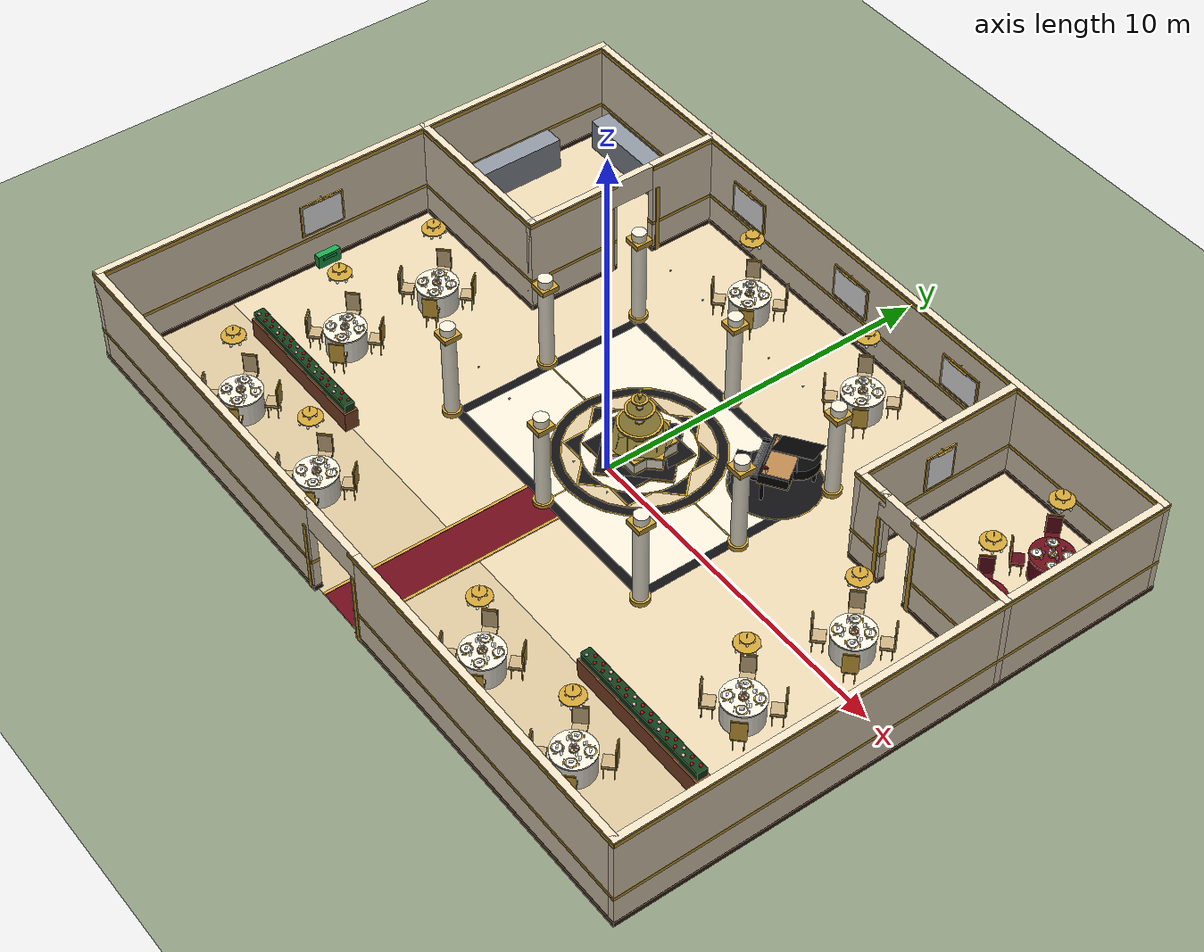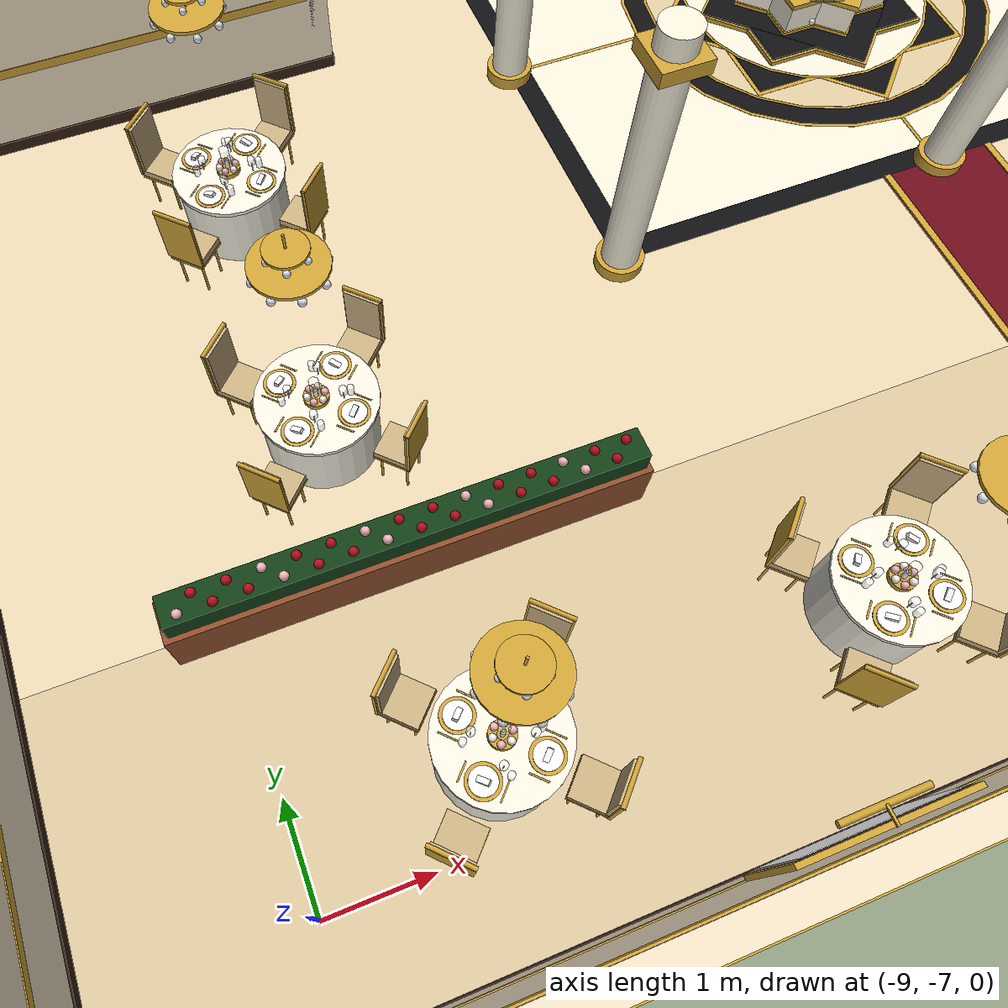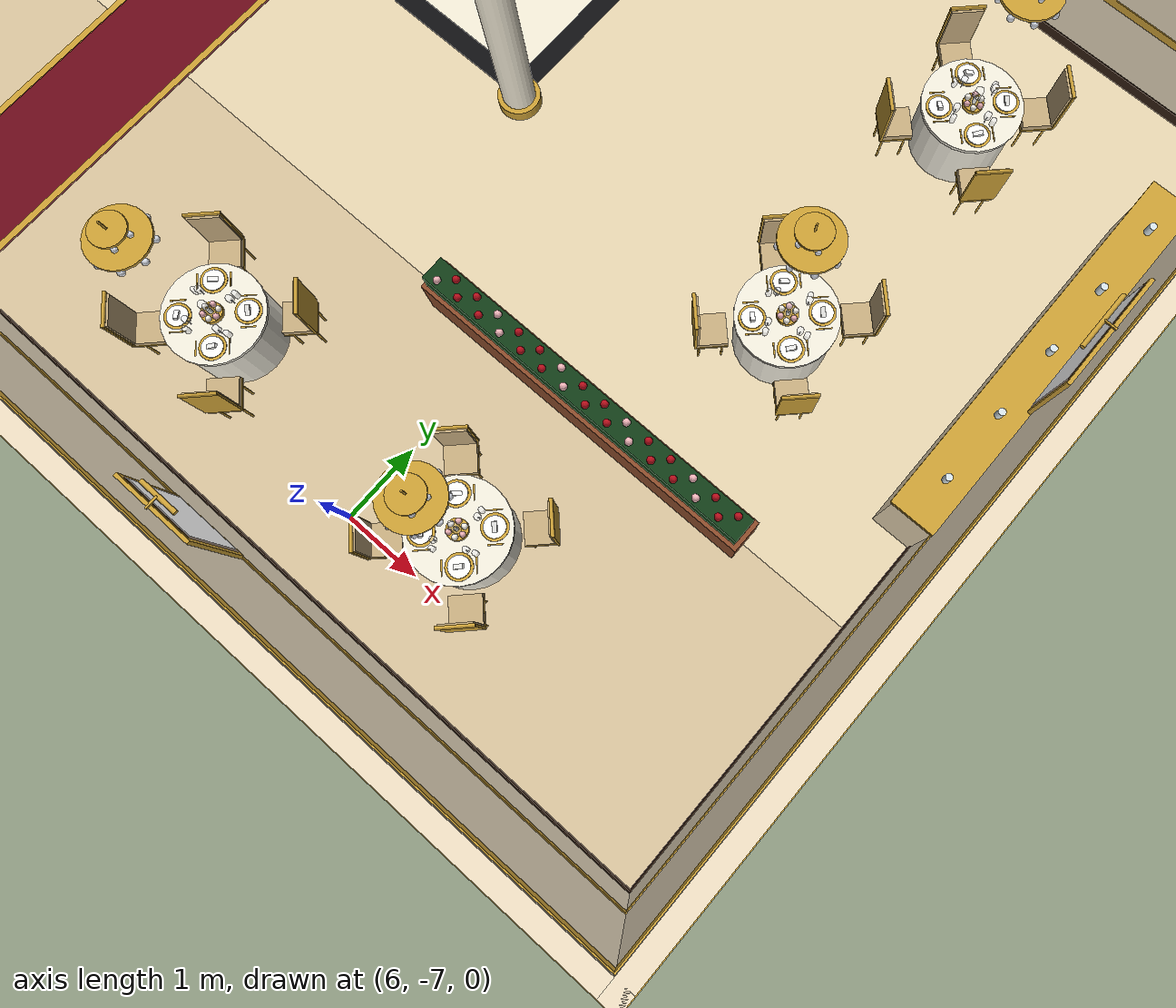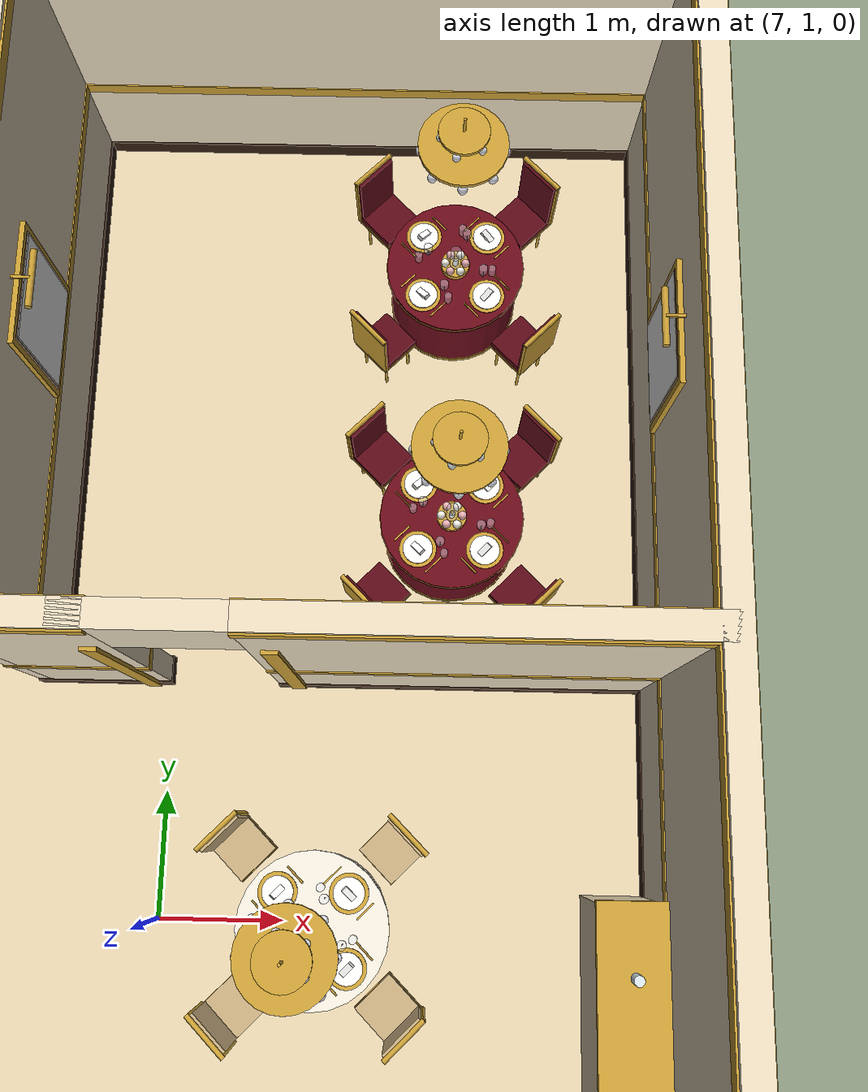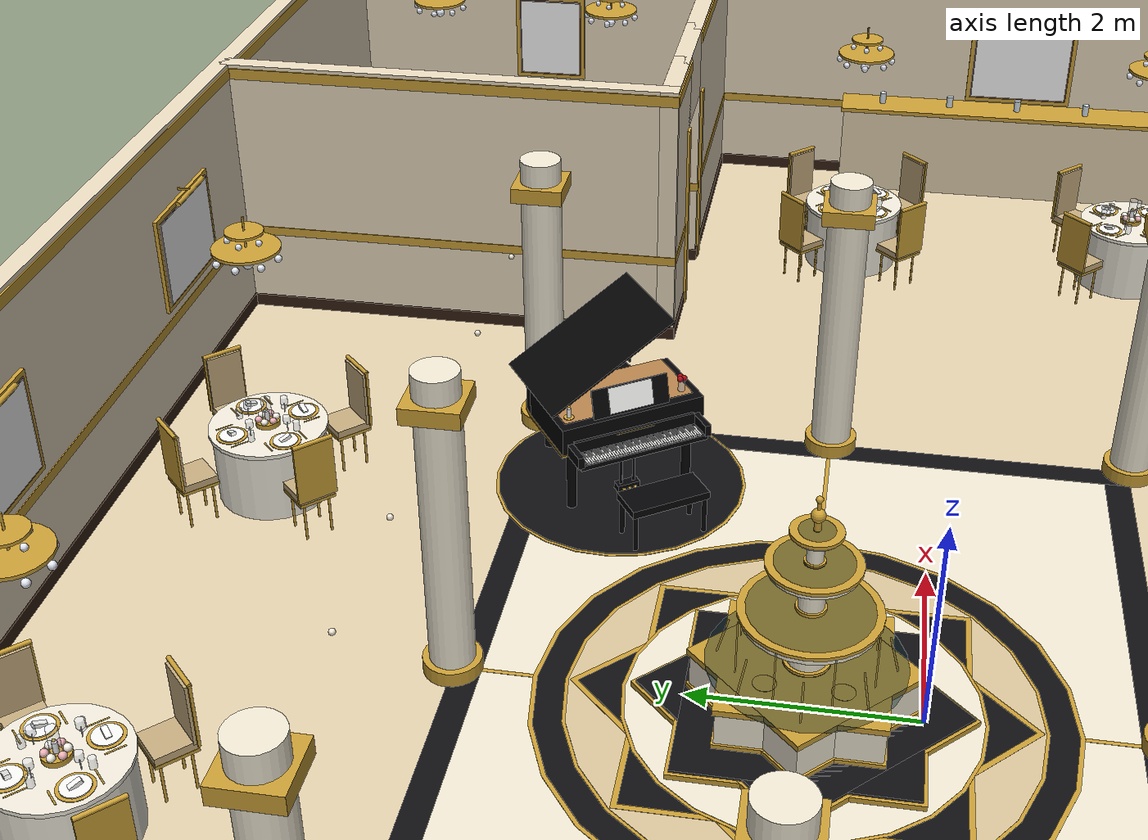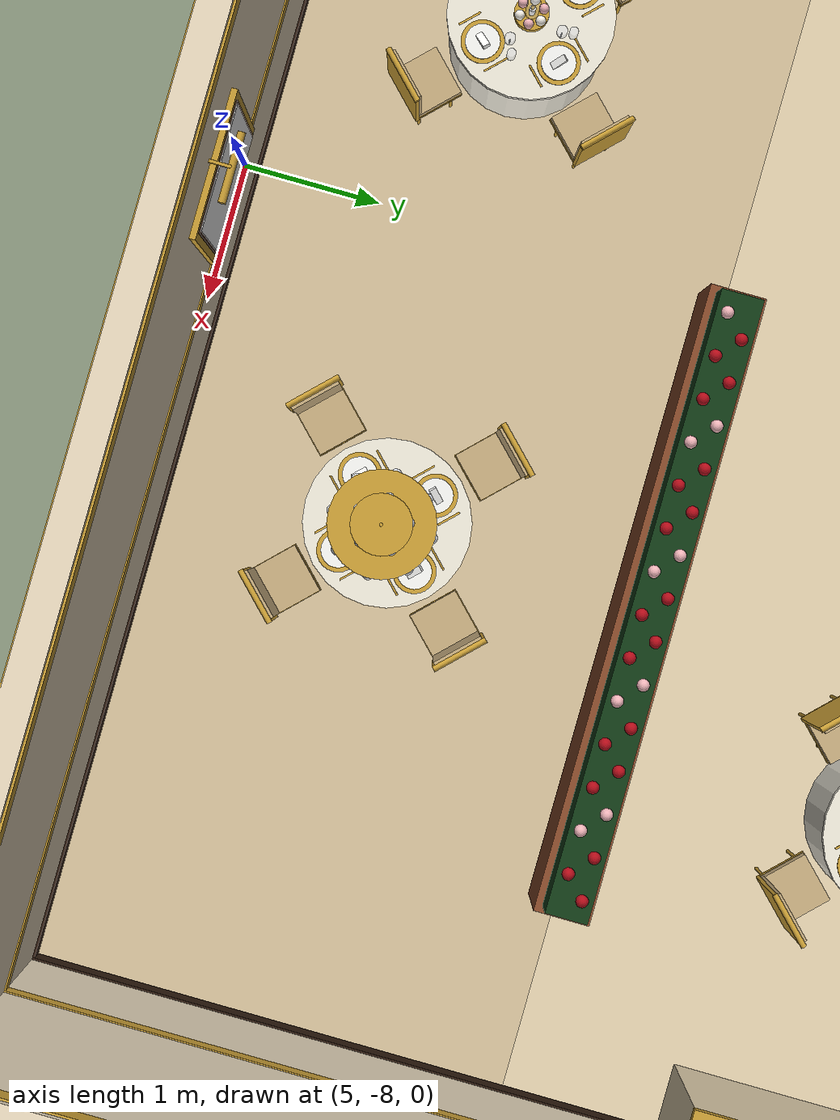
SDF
<sdf version="1.9">
 <world name="dar_tunibot">
  <physics name="1ms" type="ignored">
   <max_step_size>0.001</max_step_size>
   <real_time_factor>1.0</real_time_factor>
  </physics>
  <plugin filename="gz-sim-physics-system" name="gz::sim::systems::Physics"/>
  <plugin filename="gz-sim-user-commands-system" name="gz::sim::systems::UserCommands"/>
  <plugin filename="gz-sim-scene-broadcaster-system" name="gz::sim::systems::SceneBroadcaster"/>
  <plugin filename="gz-sim-sensors-system" name="gz::sim::systems::Sensors">
   <render_engine>ogre2</render_engine>
  </plugin>
  <scene>
   <ambient>0.30 0.27 0.30 1</ambient>
   <background>0.04 0.06 0.14 1</background>
   <shadows>true</shadows>
  </scene>
  <light name="sun" type="directional">
   <pose>0 0 12 0 0 0</pose>
   <diffuse>0.45 0.38 0.32 1</diffuse>
   <specular>0.1 0.1 0.1 1</specular>
   <direction>-0.4 0.2 -0.9</direction>
  </light>
  <model name="ground_plane">
   <static>true</static>
   <link name="link">
    <collision name="collision">
     <geometry><plane><normal>0 0 1</normal><size>60 60</size></plane></geometry>
    </collision>
    <visual name="visual">
     <geometry><plane><normal>0 0 1</normal><size>60 60</size></plane></geometry>
     <material><ambient>0.55 0.6 0.5 1</ambient><diffuse>0.55 0.6 0.5 1</diffuse></material>
    </visual>
   </link>
  </model>
  <model name="floors">
   <static>true</static>
   <link name="link">
    <visual name="floor_v">
     <pose>0.000 0.000 0.005 0.0000 0.0000 0.0000</pose>
     <geometry><box><size>22.000 16.000 0.010</size></box></geometry>
     <material>
      <ambient>0.9 0.83 0.69 1</ambient>
      <diffuse>0.9 0.83 0.69 1</diffuse>
      <specular>0.1 0.1 0.1 1</specular>
     </material>
    </visual>
    <visual name="terrace_v">
     <pose>0.000 -6.200 0.007 0.0000 0.0000 0.0000</pose>
     <geometry><box><size>22.000 3.600 0.010</size></box></geometry>
     <material>
      <ambient>0.84 0.76 0.61 1</ambient>
      <diffuse>0.84 0.76 0.61 1</diffuse>
      <specular>0.1 0.1 0.1 1</specular>
     </material>
    </visual>
    <visual name="court_ivory_v">
     <pose>0.000 1.000 0.011 0.0000 0.0000 0.0000</pose>
     <geometry><box><size>8.000 6.000 0.002</size></box></geometry>
     <material>
      <ambient>0.95 0.92 0.84 1</ambient>
      <diffuse>0.95 0.92 0.84 1</diffuse>
      <specular>0.1 0.1 0.1 1</specular>
     </material>
    </visual>
    <visual name="court_border0_v">
     <pose>0.000 3.875 0.013 0.0000 0.0000 0.0000</pose>
     <geometry><box><size>8.000 0.250 0.002</size></box></geometry>
     <material>
      <ambient>0.06 0.06 0.07 1</ambient>
      <diffuse>0.06 0.06 0.07 1</diffuse>
      <specular>0.1 0.1 0.1 1</specular>
     </material>
    </visual>
    <visual name="court_border1_v">
     <pose>0.000 -1.875 0.013 0.0000 0.0000 0.0000</pose>
     <geometry><box><size>8.000 0.250 0.002</size></box></geometry>
     <material>
      <ambient>0.06 0.06 0.07 1</ambient>
      <diffuse>0.06 0.06 0.07 1</diffuse>
      <specular>0.1 0.1 0.1 1</specular>
     </material>
    </visual>
    <visual name="court_border2_v">
     <pose>-3.875 1.000 0.013 0.0000 0.0000 0.0000</pose>
     <geometry><box><size>0.250 6.000 0.002</size></box></geometry>
     <material>
      <ambient>0.06 0.06 0.07 1</ambient>
      <diffuse>0.06 0.06 0.07 1</diffuse>
      <specular>0.1 0.1 0.1 1</specular>
     </material>
    </visual>
    <visual name="court_border3_v">
     <pose>3.875 1.000 0.013 0.0000 0.0000 0.0000</pose>
     <geometry><box><size>0.250 6.000 0.002</size></box></geometry>
     <material>
      <ambient>0.06 0.06 0.07 1</ambient>
      <diffuse>0.06 0.06 0.07 1</diffuse>
      <specular>0.1 0.1 0.1 1</specular>
     </material>
    </visual>
    <visual name="court_ray0_v">
     <pose>1.875 1.000 0.013 0.0000 0.0000 0.0000</pose>
     <geometry><box><size>3.750 0.040 0.002</size></box></geometry>
     <material>
      <ambient>0.8 0.63 0.21 1</ambient>
      <diffuse>0.8 0.63 0.21 1</diffuse>
      <specular>0.1 0.1 0.1 1</specular>
     </material>
    </visual>
    <visual name="court_ray1_v">
     <pose>-1.875 1.000 0.013 0.0000 0.0000 3.1416</pose>
     <geometry><box><size>3.750 0.040 0.002</size></box></geometry>
     <material>
      <ambient>0.8 0.63 0.21 1</ambient>
      <diffuse>0.8 0.63 0.21 1</diffuse>
      <specular>0.1 0.1 0.1 1</specular>
     </material>
    </visual>
    <visual name="court_ray2_v">
     <pose>0.000 2.375 0.013 0.0000 0.0000 1.5708</pose>
     <geometry><box><size>2.750 0.040 0.002</size></box></geometry>
     <material>
      <ambient>0.8 0.63 0.21 1</ambient>
      <diffuse>0.8 0.63 0.21 1</diffuse>
      <specular>0.1 0.1 0.1 1</specular>
     </material>
    </visual>
    <visual name="court_ray3_v">
     <pose>0.000 -0.375 0.013 0.0000 0.0000 -1.5708</pose>
     <geometry><box><size>2.750 0.040 0.002</size></box></geometry>
     <material>
      <ambient>0.8 0.63 0.21 1</ambient>
      <diffuse>0.8 0.63 0.21 1</diffuse>
      <specular>0.1 0.1 0.1 1</specular>
     </material>
    </visual>
    <visual name="medallion0_v">
     <pose>0.000 1.000 0.015 0.0000 0.0000 0.0000</pose>
     <geometry><cylinder><radius>2.300</radius><length>0.002</length></cylinder></geometry>
     <material>
      <ambient>0.8 0.63 0.21 1</ambient>
      <diffuse>0.8 0.63 0.21 1</diffuse>
      <specular>0.1 0.1 0.1 1</specular>
     </material>
    </visual>
    <visual name="medallion1_v">
     <pose>0.000 1.000 0.017 0.0000 0.0000 0.0000</pose>
     <geometry><cylinder><radius>2.260</radius><length>0.002</length></cylinder></geometry>
     <material>
      <ambient>0.06 0.06 0.07 1</ambient>
      <diffuse>0.06 0.06 0.07 1</diffuse>
      <specular>0.1 0.1 0.1 1</specular>
     </material>
    </visual>
    <visual name="medallion2_v">
     <pose>0.000 1.000 0.019 0.0000 0.0000 0.0000</pose>
     <geometry><cylinder><radius>2.020</radius><length>0.002</length></cylinder></geometry>
     <material>
      <ambient>0.8 0.63 0.21 1</ambient>
      <diffuse>0.8 0.63 0.21 1</diffuse>
      <specular>0.1 0.1 0.1 1</specular>
     </material>
    </visual>
    <visual name="medallion3_v">
     <pose>0.000 1.000 0.021 0.0000 0.0000 0.0000</pose>
     <geometry><cylinder><radius>1.990</radius><length>0.002</length></cylinder></geometry>
     <material>
      <ambient>0.86 0.78 0.62 1</ambient>
      <diffuse>0.86 0.78 0.62 1</diffuse>
      <specular>0.1 0.1 0.1 1</specular>
     </material>
    </visual>
    <visual name="star0_0_v">
     <pose>0.000 1.000 0.023 0.0000 0.0000 0.0000</pose>
     <geometry><box><size>2.800 2.800 0.002</size></box></geometry>
     <material>
      <ambient>0.8 0.63 0.21 1</ambient>
      <diffuse>0.8 0.63 0.21 1</diffuse>
      <specular>0.1 0.1 0.1 1</specular>
     </material>
    </visual>
    <visual name="star0_1_v">
     <pose>0.000 1.000 0.023 0.0000 0.0000 0.7854</pose>
     <geometry><box><size>2.800 2.800 0.002</size></box></geometry>
     <material>
      <ambient>0.8 0.63 0.21 1</ambient>
      <diffuse>0.8 0.63 0.21 1</diffuse>
      <specular>0.1 0.1 0.1 1</specular>
     </material>
    </visual>
    <visual name="star1_0_v">
     <pose>0.000 1.000 0.025 0.0000 0.0000 0.0000</pose>
     <geometry><box><size>2.700 2.700 0.002</size></box></geometry>
     <material>
      <ambient>0.06 0.06 0.07 1</ambient>
      <diffuse>0.06 0.06 0.07 1</diffuse>
      <specular>0.1 0.1 0.1 1</specular>
     </material>
    </visual>
    <visual name="star1_1_v">
     <pose>0.000 1.000 0.025 0.0000 0.0000 0.7854</pose>
     <geometry><box><size>2.700 2.700 0.002</size></box></geometry>
     <material>
      <ambient>0.06 0.06 0.07 1</ambient>
      <diffuse>0.06 0.06 0.07 1</diffuse>
      <specular>0.1 0.1 0.1 1</specular>
     </material>
    </visual>
    <visual name="medallion_gold_ring_v">
     <pose>0.000 1.000 0.027 0.0000 0.0000 0.0000</pose>
     <geometry><cylinder><radius>1.530</radius><length>0.002</length></cylinder></geometry>
     <material>
      <ambient>0.8 0.63 0.21 1</ambient>
      <diffuse>0.8 0.63 0.21 1</diffuse>
      <specular>0.1 0.1 0.1 1</specular>
     </material>
    </visual>
    <visual name="medallion_centre_v">
     <pose>0.000 1.000 0.029 0.0000 0.0000 0.0000</pose>
     <geometry><cylinder><radius>1.500</radius><length>0.002</length></cylinder></geometry>
     <material>
      <ambient>0.95 0.92 0.84 1</ambient>
      <diffuse>0.95 0.92 0.84 1</diffuse>
      <specular>0.1 0.1 0.1 1</specular>
     </material>
    </visual>
    <visual name="carpet_v">
     <pose>0.000 -5.000 0.020 0.0000 0.0000 0.0000</pose>
     <geometry><box><size>1.400 6.000 0.020</size></box></geometry>
     <material>
      <ambient>0.42 0.04 0.1 1</ambient>
      <diffuse>0.42 0.04 0.1 1</diffuse>
      <specular>0.1 0.1 0.1 1</specular>
     </material>
    </visual>
    <visual name="carpet_edge_-1_v">
     <pose>-0.660 -5.000 0.031 0.0000 0.0000 0.0000</pose>
     <geometry><box><size>0.080 6.000 0.020</size></box></geometry>
     <material>
      <ambient>0.8 0.63 0.21 1</ambient>
      <diffuse>0.8 0.63 0.21 1</diffuse>
      <specular>0.1 0.1 0.1 1</specular>
     </material>
    </visual>
    <visual name="carpet_edge_1_v">
     <pose>0.660 -5.000 0.031 0.0000 0.0000 0.0000</pose>
     <geometry><box><size>0.080 6.000 0.020</size></box></geometry>
     <material>
      <ambient>0.8 0.63 0.21 1</ambient>
      <diffuse>0.8 0.63 0.21 1</diffuse>
      <specular>0.1 0.1 0.1 1</specular>
     </material>
    </visual>
   </link>
  </model>
  <model name="dar_walls">
   <static>true</static>
   <link name="link">
    <visual name="wall0_v">
     <pose>0.000 8.000 1.500 0.0000 0.0000 0.0000</pose>
     <geometry><box><size>22.200 0.200 3.000</size></box></geometry>
     <material>
      <ambient>0.93 0.87 0.76 1</ambient>
      <diffuse>0.93 0.87 0.76 1</diffuse>
      <specular>0.1 0.1 0.1 1</specular>
     </material>
    </visual>
    <collision name="wall0_c">
     <pose>0.000 8.000 1.500 0.0000 0.0000 0.0000</pose>
     <geometry><box><size>22.200 0.200 3.000</size></box></geometry>
    </collision>
    <visual name="skirting0_v">
     <pose>0.000 8.000 0.075 0.0000 0.0000 0.0000</pose>
     <geometry><box><size>22.210 0.230 0.150</size></box></geometry>
     <material>
      <ambient>0.2 0.12 0.07 1</ambient>
      <diffuse>0.2 0.12 0.07 1</diffuse>
      <specular>0.1 0.1 0.1 1</specular>
     </material>
    </visual>
    <visual name="rail0_v">
     <pose>0.000 8.000 1.000 0.0000 0.0000 0.0000</pose>
     <geometry><box><size>22.210 0.220 0.100</size></box></geometry>
     <material>
      <ambient>0.8 0.63 0.21 1</ambient>
      <diffuse>0.8 0.63 0.21 1</diffuse>
      <specular>0.1 0.1 0.1 1</specular>
     </material>
    </visual>
    <visual name="crown0_v">
     <pose>0.000 8.000 2.900 0.0000 0.0000 0.0000</pose>
     <geometry><box><size>22.210 0.230 0.120</size></box></geometry>
     <material>
      <ambient>0.8 0.63 0.21 1</ambient>
      <diffuse>0.8 0.63 0.21 1</diffuse>
      <specular>0.1 0.1 0.1 1</specular>
     </material>
    </visual>
    <visual name="wall1_v">
     <pose>-11.000 0.000 1.500 0.0000 0.0000 1.5708</pose>
     <geometry><box><size>16.200 0.200 3.000</size></box></geometry>
     <material>
      <ambient>0.93 0.87 0.76 1</ambient>
      <diffuse>0.93 0.87 0.76 1</diffuse>
      <specular>0.1 0.1 0.1 1</specular>
     </material>
    </visual>
    <collision name="wall1_c">
     <pose>-11.000 0.000 1.500 0.0000 0.0000 1.5708</pose>
     <geometry><box><size>16.200 0.200 3.000</size></box></geometry>
    </collision>
    <visual name="skirting1_v">
     <pose>-11.000 0.000 0.075 0.0000 0.0000 1.5708</pose>
     <geometry><box><size>16.210 0.230 0.150</size></box></geometry>
     <material>
      <ambient>0.2 0.12 0.07 1</ambient>
      <diffuse>0.2 0.12 0.07 1</diffuse>
      <specular>0.1 0.1 0.1 1</specular>
     </material>
    </visual>
    <visual name="rail1_v">
     <pose>-11.000 0.000 1.000 0.0000 0.0000 1.5708</pose>
     <geometry><box><size>16.210 0.220 0.100</size></box></geometry>
     <material>
      <ambient>0.8 0.63 0.21 1</ambient>
      <diffuse>0.8 0.63 0.21 1</diffuse>
      <specular>0.1 0.1 0.1 1</specular>
     </material>
    </visual>
    <visual name="crown1_v">
     <pose>-11.000 0.000 2.900 0.0000 0.0000 1.5708</pose>
     <geometry><box><size>16.210 0.230 0.120</size></box></geometry>
     <material>
      <ambient>0.8 0.63 0.21 1</ambient>
      <diffuse>0.8 0.63 0.21 1</diffuse>
      <specular>0.1 0.1 0.1 1</specular>
     </material>
    </visual>
    <visual name="wall2_v">
     <pose>11.000 0.000 1.500 0.0000 0.0000 1.5708</pose>
     <geometry><box><size>16.200 0.200 3.000</size></box></geometry>
     <material>
      <ambient>0.93 0.87 0.76 1</ambient>
      <diffuse>0.93 0.87 0.76 1</diffuse>
      <specular>0.1 0.1 0.1 1</specular>
     </material>
    </visual>
    <collision name="wall2_c">
     <pose>11.000 0.000 1.500 0.0000 0.0000 1.5708</pose>
     <geometry><box><size>16.200 0.200 3.000</size></box></geometry>
    </collision>
    <visual name="skirting2_v">
     <pose>11.000 0.000 0.075 0.0000 0.0000 1.5708</pose>
     <geometry><box><size>16.210 0.230 0.150</size></box></geometry>
     <material>
      <ambient>0.2 0.12 0.07 1</ambient>
      <diffuse>0.2 0.12 0.07 1</diffuse>
      <specular>0.1 0.1 0.1 1</specular>
     </material>
    </visual>
    <visual name="rail2_v">
     <pose>11.000 0.000 1.000 0.0000 0.0000 1.5708</pose>
     <geometry><box><size>16.210 0.220 0.100</size></box></geometry>
     <material>
      <ambient>0.8 0.63 0.21 1</ambient>
      <diffuse>0.8 0.63 0.21 1</diffuse>
      <specular>0.1 0.1 0.1 1</specular>
     </material>
    </visual>
    <visual name="crown2_v">
     <pose>11.000 0.000 2.900 0.0000 0.0000 1.5708</pose>
     <geometry><box><size>16.210 0.230 0.120</size></box></geometry>
     <material>
      <ambient>0.8 0.63 0.21 1</ambient>
      <diffuse>0.8 0.63 0.21 1</diffuse>
      <specular>0.1 0.1 0.1 1</specular>
     </material>
    </visual>
    <visual name="wall3_v">
     <pose>-6.000 -8.000 1.500 0.0000 0.0000 0.0000</pose>
     <geometry><box><size>10.200 0.200 3.000</size></box></geometry>
     <material>
      <ambient>0.93 0.87 0.76 1</ambient>
      <diffuse>0.93 0.87 0.76 1</diffuse>
      <specular>0.1 0.1 0.1 1</specular>
     </material>
    </visual>
    <collision name="wall3_c">
     <pose>-6.000 -8.000 1.500 0.0000 0.0000 0.0000</pose>
     <geometry><box><size>10.200 0.200 3.000</size></box></geometry>
    </collision>
    <visual name="skirting3_v">
     <pose>-6.000 -8.000 0.075 0.0000 0.0000 0.0000</pose>
     <geometry><box><size>10.210 0.230 0.150</size></box></geometry>
     <material>
      <ambient>0.2 0.12 0.07 1</ambient>
      <diffuse>0.2 0.12 0.07 1</diffuse>
      <specular>0.1 0.1 0.1 1</specular>
     </material>
    </visual>
    <visual name="rail3_v">
     <pose>-6.000 -8.000 1.000 0.0000 0.0000 0.0000</pose>
     <geometry><box><size>10.210 0.220 0.100</size></box></geometry>
     <material>
      <ambient>0.8 0.63 0.21 1</ambient>
      <diffuse>0.8 0.63 0.21 1</diffuse>
      <specular>0.1 0.1 0.1 1</specular>
     </material>
    </visual>
    <visual name="crown3_v">
     <pose>-6.000 -8.000 2.900 0.0000 0.0000 0.0000</pose>
     <geometry><box><size>10.210 0.230 0.120</size></box></geometry>
     <material>
      <ambient>0.8 0.63 0.21 1</ambient>
      <diffuse>0.8 0.63 0.21 1</diffuse>
      <specular>0.1 0.1 0.1 1</specular>
     </material>
    </visual>
    <visual name="wall4_v">
     <pose>6.000 -8.000 1.500 0.0000 0.0000 0.0000</pose>
     <geometry><box><size>10.200 0.200 3.000</size></box></geometry>
     <material>
      <ambient>0.93 0.87 0.76 1</ambient>
      <diffuse>0.93 0.87 0.76 1</diffuse>
      <specular>0.1 0.1 0.1 1</specular>
     </material>
    </visual>
    <collision name="wall4_c">
     <pose>6.000 -8.000 1.500 0.0000 0.0000 0.0000</pose>
     <geometry><box><size>10.200 0.200 3.000</size></box></geometry>
    </collision>
    <visual name="skirting4_v">
     <pose>6.000 -8.000 0.075 0.0000 0.0000 0.0000</pose>
     <geometry><box><size>10.210 0.230 0.150</size></box></geometry>
     <material>
      <ambient>0.2 0.12 0.07 1</ambient>
      <diffuse>0.2 0.12 0.07 1</diffuse>
      <specular>0.1 0.1 0.1 1</specular>
     </material>
    </visual>
    <visual name="rail4_v">
     <pose>6.000 -8.000 1.000 0.0000 0.0000 0.0000</pose>
     <geometry><box><size>10.210 0.220 0.100</size></box></geometry>
     <material>
      <ambient>0.8 0.63 0.21 1</ambient>
      <diffuse>0.8 0.63 0.21 1</diffuse>
      <specular>0.1 0.1 0.1 1</specular>
     </material>
    </visual>
    <visual name="crown4_v">
     <pose>6.000 -8.000 2.900 0.0000 0.0000 0.0000</pose>
     <geometry><box><size>10.210 0.230 0.120</size></box></geometry>
     <material>
      <ambient>0.8 0.63 0.21 1</ambient>
      <diffuse>0.8 0.63 0.21 1</diffuse>
      <specular>0.1 0.1 0.1 1</specular>
     </material>
    </visual>
    <visual name="wall5_v">
     <pose>-8.500 2.000 1.500 0.0000 0.0000 0.0000</pose>
     <geometry><box><size>5.200 0.200 3.000</size></box></geometry>
     <material>
      <ambient>0.93 0.87 0.76 1</ambient>
      <diffuse>0.93 0.87 0.76 1</diffuse>
      <specular>0.1 0.1 0.1 1</specular>
     </material>
    </visual>
    <collision name="wall5_c">
     <pose>-8.500 2.000 1.500 0.0000 0.0000 0.0000</pose>
     <geometry><box><size>5.200 0.200 3.000</size></box></geometry>
    </collision>
    <visual name="skirting5_v">
     <pose>-8.500 2.000 0.075 0.0000 0.0000 0.0000</pose>
     <geometry><box><size>5.210 0.230 0.150</size></box></geometry>
     <material>
      <ambient>0.2 0.12 0.07 1</ambient>
      <diffuse>0.2 0.12 0.07 1</diffuse>
      <specular>0.1 0.1 0.1 1</specular>
     </material>
    </visual>
    <visual name="rail5_v">
     <pose>-8.500 2.000 1.000 0.0000 0.0000 0.0000</pose>
     <geometry><box><size>5.210 0.220 0.100</size></box></geometry>
     <material>
      <ambient>0.8 0.63 0.21 1</ambient>
      <diffuse>0.8 0.63 0.21 1</diffuse>
      <specular>0.1 0.1 0.1 1</specular>
     </material>
    </visual>
    <visual name="crown5_v">
     <pose>-8.500 2.000 2.900 0.0000 0.0000 0.0000</pose>
     <geometry><box><size>5.210 0.230 0.120</size></box></geometry>
     <material>
      <ambient>0.8 0.63 0.21 1</ambient>
      <diffuse>0.8 0.63 0.21 1</diffuse>
      <specular>0.1 0.1 0.1 1</specular>
     </material>
    </visual>
    <visual name="wall6_v">
     <pose>-6.000 3.300 1.500 0.0000 0.0000 1.5708</pose>
     <geometry><box><size>2.800 0.200 3.000</size></box></geometry>
     <material>
      <ambient>0.93 0.87 0.76 1</ambient>
      <diffuse>0.93 0.87 0.76 1</diffuse>
      <specular>0.1 0.1 0.1 1</specular>
     </material>
    </visual>
    <collision name="wall6_c">
     <pose>-6.000 3.300 1.500 0.0000 0.0000 1.5708</pose>
     <geometry><box><size>2.800 0.200 3.000</size></box></geometry>
    </collision>
    <visual name="skirting6_v">
     <pose>-6.000 3.300 0.075 0.0000 0.0000 1.5708</pose>
     <geometry><box><size>2.810 0.230 0.150</size></box></geometry>
     <material>
      <ambient>0.2 0.12 0.07 1</ambient>
      <diffuse>0.2 0.12 0.07 1</diffuse>
      <specular>0.1 0.1 0.1 1</specular>
     </material>
    </visual>
    <visual name="rail6_v">
     <pose>-6.000 3.300 1.000 0.0000 0.0000 1.5708</pose>
     <geometry><box><size>2.810 0.220 0.100</size></box></geometry>
     <material>
      <ambient>0.8 0.63 0.21 1</ambient>
      <diffuse>0.8 0.63 0.21 1</diffuse>
      <specular>0.1 0.1 0.1 1</specular>
     </material>
    </visual>
    <visual name="crown6_v">
     <pose>-6.000 3.300 2.900 0.0000 0.0000 1.5708</pose>
     <geometry><box><size>2.810 0.230 0.120</size></box></geometry>
     <material>
      <ambient>0.8 0.63 0.21 1</ambient>
      <diffuse>0.8 0.63 0.21 1</diffuse>
      <specular>0.1 0.1 0.1 1</specular>
     </material>
    </visual>
    <visual name="wall7_v">
     <pose>-6.000 7.000 1.500 0.0000 0.0000 1.5708</pose>
     <geometry><box><size>2.200 0.200 3.000</size></box></geometry>
     <material>
      <ambient>0.93 0.87 0.76 1</ambient>
      <diffuse>0.93 0.87 0.76 1</diffuse>
      <specular>0.1 0.1 0.1 1</specular>
     </material>
    </visual>
    <collision name="wall7_c">
     <pose>-6.000 7.000 1.500 0.0000 0.0000 1.5708</pose>
     <geometry><box><size>2.200 0.200 3.000</size></box></geometry>
    </collision>
    <visual name="skirting7_v">
     <pose>-6.000 7.000 0.075 0.0000 0.0000 1.5708</pose>
     <geometry><box><size>2.210 0.230 0.150</size></box></geometry>
     <material>
      <ambient>0.2 0.12 0.07 1</ambient>
      <diffuse>0.2 0.12 0.07 1</diffuse>
      <specular>0.1 0.1 0.1 1</specular>
     </material>
    </visual>
    <visual name="rail7_v">
     <pose>-6.000 7.000 1.000 0.0000 0.0000 1.5708</pose>
     <geometry><box><size>2.210 0.220 0.100</size></box></geometry>
     <material>
      <ambient>0.8 0.63 0.21 1</ambient>
      <diffuse>0.8 0.63 0.21 1</diffuse>
      <specular>0.1 0.1 0.1 1</specular>
     </material>
    </visual>
    <visual name="crown7_v">
     <pose>-6.000 7.000 2.900 0.0000 0.0000 1.5708</pose>
     <geometry><box><size>2.210 0.230 0.120</size></box></geometry>
     <material>
      <ambient>0.8 0.63 0.21 1</ambient>
      <diffuse>0.8 0.63 0.21 1</diffuse>
      <specular>0.1 0.1 0.1 1</specular>
     </material>
    </visual>
    <visual name="wall8_v">
     <pose>6.000 5.500 1.500 0.0000 0.0000 1.5708</pose>
     <geometry><box><size>5.200 0.200 3.000</size></box></geometry>
     <material>
      <ambient>0.93 0.87 0.76 1</ambient>
      <diffuse>0.93 0.87 0.76 1</diffuse>
      <specular>0.1 0.1 0.1 1</specular>
     </material>
    </visual>
    <collision name="wall8_c">
     <pose>6.000 5.500 1.500 0.0000 0.0000 1.5708</pose>
     <geometry><box><size>5.200 0.200 3.000</size></box></geometry>
    </collision>
    <visual name="skirting8_v">
     <pose>6.000 5.500 0.075 0.0000 0.0000 1.5708</pose>
     <geometry><box><size>5.210 0.230 0.150</size></box></geometry>
     <material>
      <ambient>0.2 0.12 0.07 1</ambient>
      <diffuse>0.2 0.12 0.07 1</diffuse>
      <specular>0.1 0.1 0.1 1</specular>
     </material>
    </visual>
    <visual name="rail8_v">
     <pose>6.000 5.500 1.000 0.0000 0.0000 1.5708</pose>
     <geometry><box><size>5.210 0.220 0.100</size></box></geometry>
     <material>
      <ambient>0.8 0.63 0.21 1</ambient>
      <diffuse>0.8 0.63 0.21 1</diffuse>
      <specular>0.1 0.1 0.1 1</specular>
     </material>
    </visual>
    <visual name="crown8_v">
     <pose>6.000 5.500 2.900 0.0000 0.0000 1.5708</pose>
     <geometry><box><size>5.210 0.230 0.120</size></box></geometry>
     <material>
      <ambient>0.8 0.63 0.21 1</ambient>
      <diffuse>0.8 0.63 0.21 1</diffuse>
      <specular>0.1 0.1 0.1 1</specular>
     </material>
    </visual>
    <visual name="wall9_v">
     <pose>6.450 3.000 1.500 0.0000 0.0000 0.0000</pose>
     <geometry><box><size>1.100 0.200 3.000</size></box></geometry>
     <material>
      <ambient>0.93 0.87 0.76 1</ambient>
      <diffuse>0.93 0.87 0.76 1</diffuse>
      <specular>0.1 0.1 0.1 1</specular>
     </material>
    </visual>
    <collision name="wall9_c">
     <pose>6.450 3.000 1.500 0.0000 0.0000 0.0000</pose>
     <geometry><box><size>1.100 0.200 3.000</size></box></geometry>
    </collision>
    <visual name="skirting9_v">
     <pose>6.450 3.000 0.075 0.0000 0.0000 0.0000</pose>
     <geometry><box><size>1.110 0.230 0.150</size></box></geometry>
     <material>
      <ambient>0.2 0.12 0.07 1</ambient>
      <diffuse>0.2 0.12 0.07 1</diffuse>
      <specular>0.1 0.1 0.1 1</specular>
     </material>
    </visual>
    <visual name="rail9_v">
     <pose>6.450 3.000 1.000 0.0000 0.0000 0.0000</pose>
     <geometry><box><size>1.110 0.220 0.100</size></box></geometry>
     <material>
      <ambient>0.8 0.63 0.21 1</ambient>
      <diffuse>0.8 0.63 0.21 1</diffuse>
      <specular>0.1 0.1 0.1 1</specular>
     </material>
    </visual>
    <visual name="crown9_v">
     <pose>6.450 3.000 2.900 0.0000 0.0000 0.0000</pose>
     <geometry><box><size>1.110 0.230 0.120</size></box></geometry>
     <material>
      <ambient>0.8 0.63 0.21 1</ambient>
      <diffuse>0.8 0.63 0.21 1</diffuse>
      <specular>0.1 0.1 0.1 1</specular>
     </material>
    </visual>
    <visual name="wall10_v">
     <pose>9.500 3.000 1.500 0.0000 0.0000 0.0000</pose>
     <geometry><box><size>3.200 0.200 3.000</size></box></geometry>
     <material>
      <ambient>0.93 0.87 0.76 1</ambient>
      <diffuse>0.93 0.87 0.76 1</diffuse>
      <specular>0.1 0.1 0.1 1</specular>
     </material>
    </visual>
    <collision name="wall10_c">
     <pose>9.500 3.000 1.500 0.0000 0.0000 0.0000</pose>
     <geometry><box><size>3.200 0.200 3.000</size></box></geometry>
    </collision>
    <visual name="skirting10_v">
     <pose>9.500 3.000 0.075 0.0000 0.0000 0.0000</pose>
     <geometry><box><size>3.210 0.230 0.150</size></box></geometry>
     <material>
      <ambient>0.2 0.12 0.07 1</ambient>
      <diffuse>0.2 0.12 0.07 1</diffuse>
      <specular>0.1 0.1 0.1 1</specular>
     </material>
    </visual>
    <visual name="rail10_v">
     <pose>9.500 3.000 1.000 0.0000 0.0000 0.0000</pose>
     <geometry><box><size>3.210 0.220 0.100</size></box></geometry>
     <material>
      <ambient>0.8 0.63 0.21 1</ambient>
      <diffuse>0.8 0.63 0.21 1</diffuse>
      <specular>0.1 0.1 0.1 1</specular>
     </material>
    </visual>
    <visual name="crown10_v">
     <pose>9.500 3.000 2.900 0.0000 0.0000 0.0000</pose>
     <geometry><box><size>3.210 0.230 0.120</size></box></geometry>
     <material>
      <ambient>0.8 0.63 0.21 1</ambient>
      <diffuse>0.8 0.63 0.21 1</diffuse>
      <specular>0.1 0.1 0.1 1</specular>
     </material>
    </visual>
   </link>
  </model>
  <model name="kitchen_door">
   <static>true</static>
   <pose>-6.0 5.3 0 0 0 1.5707963267948966</pose>
   <link name="link">
    <visual name="post_a_v">
     <pose>-0.760 0.000 1.100 0.0000 0.0000 0.0000</pose>
     <geometry><box><size>0.120 0.260 2.200</size></box></geometry>
     <material>
      <ambient>0.8 0.63 0.21 1</ambient>
      <diffuse>0.8 0.63 0.21 1</diffuse>
      <specular>0.1 0.1 0.1 1</specular>
     </material>
    </visual>
    <visual name="post_b_v">
     <pose>0.760 0.000 1.100 0.0000 0.0000 0.0000</pose>
     <geometry><box><size>0.120 0.260 2.200</size></box></geometry>
     <material>
      <ambient>0.8 0.63 0.21 1</ambient>
      <diffuse>0.8 0.63 0.21 1</diffuse>
      <specular>0.1 0.1 0.1 1</specular>
     </material>
    </visual>
    <visual name="lintel_v">
     <pose>0.000 0.000 2.600 0.0000 0.0000 0.0000</pose>
     <geometry><box><size>1.640 0.200 0.800</size></box></geometry>
     <material>
      <ambient>0.93 0.87 0.76 1</ambient>
      <diffuse>0.93 0.87 0.76 1</diffuse>
      <specular>0.1 0.1 0.1 1</specular>
     </material>
    </visual>
    <collision name="lintel_c">
     <pose>0.000 0.000 2.600 0.0000 0.0000 0.0000</pose>
     <geometry><box><size>1.640 0.200 0.800</size></box></geometry>
    </collision>
   </link>
  </model>
  <model name="salon_arch">
   <static>true</static>
   <pose>7.45 3.0 0 0 0 0.0</pose>
   <link name="link">
    <visual name="post_a_v">
     <pose>-0.610 0.000 1.100 0.0000 0.0000 0.0000</pose>
     <geometry><box><size>0.120 0.260 2.200</size></box></geometry>
     <material>
      <ambient>0.8 0.63 0.21 1</ambient>
      <diffuse>0.8 0.63 0.21 1</diffuse>
      <specular>0.1 0.1 0.1 1</specular>
     </material>
    </visual>
    <visual name="post_b_v">
     <pose>0.610 0.000 1.100 0.0000 0.0000 0.0000</pose>
     <geometry><box><size>0.120 0.260 2.200</size></box></geometry>
     <material>
      <ambient>0.8 0.63 0.21 1</ambient>
      <diffuse>0.8 0.63 0.21 1</diffuse>
      <specular>0.1 0.1 0.1 1</specular>
     </material>
    </visual>
    <visual name="lintel_v">
     <pose>0.000 0.000 2.600 0.0000 0.0000 0.0000</pose>
     <geometry><box><size>1.340 0.200 0.800</size></box></geometry>
     <material>
      <ambient>0.93 0.87 0.76 1</ambient>
      <diffuse>0.93 0.87 0.76 1</diffuse>
      <specular>0.1 0.1 0.1 1</specular>
     </material>
    </visual>
    <collision name="lintel_c">
     <pose>0.000 0.000 2.600 0.0000 0.0000 0.0000</pose>
     <geometry><box><size>1.340 0.200 0.800</size></box></geometry>
    </collision>
    <visual name="medallion_v">
     <pose>0 0 2.6 1.5708 0 0</pose>
     <geometry><cylinder><radius>0.280</radius><length>0.050</length></cylinder></geometry>
     <material>
      <ambient>0.8 0.63 0.21 1</ambient>
      <diffuse>0.8 0.63 0.21 1</diffuse>
      <specular>0.1 0.1 0.1 1</specular>
     </material>
    </visual>
   </link>
  </model>
  <model name="entrance">
   <static>true</static>
   <pose>0.0 -8.0 0 0 0 0.0</pose>
   <link name="link">
    <visual name="post_a_v">
     <pose>-1.060 0.000 1.100 0.0000 0.0000 0.0000</pose>
     <geometry><box><size>0.120 0.260 2.200</size></box></geometry>
     <material>
      <ambient>0.8 0.63 0.21 1</ambient>
      <diffuse>0.8 0.63 0.21 1</diffuse>
      <specular>0.1 0.1 0.1 1</specular>
     </material>
    </visual>
    <visual name="post_b_v">
     <pose>1.060 0.000 1.100 0.0000 0.0000 0.0000</pose>
     <geometry><box><size>0.120 0.260 2.200</size></box></geometry>
     <material>
      <ambient>0.8 0.63 0.21 1</ambient>
      <diffuse>0.8 0.63 0.21 1</diffuse>
      <specular>0.1 0.1 0.1 1</specular>
     </material>
    </visual>
    <visual name="lintel_v">
     <pose>0.000 0.000 2.600 0.0000 0.0000 0.0000</pose>
     <geometry><box><size>2.240 0.200 0.800</size></box></geometry>
     <material>
      <ambient>0.93 0.87 0.76 1</ambient>
      <diffuse>0.93 0.87 0.76 1</diffuse>
      <specular>0.1 0.1 0.1 1</specular>
     </material>
    </visual>
    <collision name="lintel_c">
     <pose>0.000 0.000 2.600 0.0000 0.0000 0.0000</pose>
     <geometry><box><size>2.240 0.200 0.800</size></box></geometry>
    </collision>
   </link>
  </model>
  <model name="fountain">
   <static>true</static>
   <pose>0.0 1.0 0 0 0 0</pose>
   <link name="link">
    <visual name="step_trim_0_v">
     <pose>0.000 0.000 0.055 0.0000 0.0000 0.0000</pose>
     <geometry><box><size>2.060 2.060 0.050</size></box></geometry>
     <material>
      <ambient>0.8 0.63 0.21 1</ambient>
      <diffuse>0.8 0.63 0.21 1</diffuse>
      <specular>0.1 0.1 0.1 1</specular>
     </material>
    </visual>
    <visual name="step_trim_1_v">
     <pose>0.000 0.000 0.055 0.0000 0.0000 0.7854</pose>
     <geometry><box><size>2.060 2.060 0.050</size></box></geometry>
     <material>
      <ambient>0.8 0.63 0.21 1</ambient>
      <diffuse>0.8 0.63 0.21 1</diffuse>
      <specular>0.1 0.1 0.1 1</specular>
     </material>
    </visual>
    <visual name="step_0_v">
     <pose>0.000 0.000 0.065 0.0000 0.0000 0.0000</pose>
     <geometry><box><size>2.000 2.000 0.070</size></box></geometry>
     <material>
      <ambient>0.06 0.06 0.07 1</ambient>
      <diffuse>0.06 0.06 0.07 1</diffuse>
      <specular>0.1 0.1 0.1 1</specular>
     </material>
    </visual>
    <visual name="step_1_v">
     <pose>0.000 0.000 0.065 0.0000 0.0000 0.7854</pose>
     <geometry><box><size>2.000 2.000 0.070</size></box></geometry>
     <material>
      <ambient>0.06 0.06 0.07 1</ambient>
      <diffuse>0.06 0.06 0.07 1</diffuse>
      <specular>0.1 0.1 0.1 1</specular>
     </material>
    </visual>
    <visual name="basin_0_v">
     <pose>0.000 0.000 0.250 0.0000 0.0000 0.0000</pose>
     <geometry><box><size>1.360 1.360 0.500</size></box></geometry>
     <material>
      <ambient>0.95 0.92 0.84 1</ambient>
      <diffuse>0.95 0.92 0.84 1</diffuse>
      <specular>0.1 0.1 0.1 1</specular>
     </material>
    </visual>
    <collision name="basin_0_c">
     <pose>0.000 0.000 0.250 0.0000 0.0000 0.0000</pose>
     <geometry><box><size>1.360 1.360 0.500</size></box></geometry>
    </collision>
    <visual name="basin_1_v">
     <pose>0.000 0.000 0.250 0.0000 0.0000 0.7854</pose>
     <geometry><box><size>1.360 1.360 0.500</size></box></geometry>
     <material>
      <ambient>0.95 0.92 0.84 1</ambient>
      <diffuse>0.95 0.92 0.84 1</diffuse>
      <specular>0.1 0.1 0.1 1</specular>
     </material>
    </visual>
    <collision name="basin_1_c">
     <pose>0.000 0.000 0.250 0.0000 0.0000 0.7854</pose>
     <geometry><box><size>1.360 1.360 0.500</size></box></geometry>
    </collision>
    <visual name="basin_foot_0_v">
     <pose>0.000 0.000 0.120 0.0000 0.0000 0.0000</pose>
     <geometry><box><size>1.400 1.400 0.040</size></box></geometry>
     <material>
      <ambient>0.8 0.63 0.21 1</ambient>
      <diffuse>0.8 0.63 0.21 1</diffuse>
      <specular>0.1 0.1 0.1 1</specular>
     </material>
    </visual>
    <visual name="basin_foot_1_v">
     <pose>0.000 0.000 0.120 0.0000 0.0000 0.7854</pose>
     <geometry><box><size>1.400 1.400 0.040</size></box></geometry>
     <material>
      <ambient>0.8 0.63 0.21 1</ambient>
      <diffuse>0.8 0.63 0.21 1</diffuse>
      <specular>0.1 0.1 0.1 1</specular>
     </material>
    </visual>
    <visual name="basin_rim_0_v">
     <pose>0.000 0.000 0.477 0.0000 0.0000 0.0000</pose>
     <geometry><box><size>1.400 1.400 0.055</size></box></geometry>
     <material>
      <ambient>0.8 0.63 0.21 1</ambient>
      <diffuse>0.8 0.63 0.21 1</diffuse>
      <specular>0.1 0.1 0.1 1</specular>
     </material>
    </visual>
    <visual name="basin_rim_1_v">
     <pose>0.000 0.000 0.477 0.0000 0.0000 0.7854</pose>
     <geometry><box><size>1.400 1.400 0.055</size></box></geometry>
     <material>
      <ambient>0.8 0.63 0.21 1</ambient>
      <diffuse>0.8 0.63 0.21 1</diffuse>
      <specular>0.1 0.1 0.1 1</specular>
     </material>
    </visual>
    <visual name="water_v">
     <pose>0.000 0.000 0.516 0.0000 0.0000 0.0000</pose>
     <geometry><cylinder><radius>0.840</radius><length>0.008</length></cylinder></geometry>
     <transparency>0.6</transparency>
     <material>
      <ambient>0.01 0.13 0.15 1</ambient>
      <diffuse>0.01 0.13 0.15 1</diffuse>
      <specular>0.1 0.1 0.1 1</specular>
      <emissive>0.01 0.05 0.06 1</emissive>
     </material>
    </visual>
    <visual name="pedestal1_v">
     <pose>0.000 0.000 0.750 0.0000 0.0000 0.0000</pose>
     <geometry><cylinder><radius>0.170</radius><length>0.500</length></cylinder></geometry>
     <material>
      <ambient>0.95 0.92 0.84 1</ambient>
      <diffuse>0.95 0.92 0.84 1</diffuse>
      <specular>0.1 0.1 0.1 1</specular>
     </material>
    </visual>
    <collision name="pedestal1_c">
     <pose>0.000 0.000 0.750 0.0000 0.0000 0.0000</pose>
     <geometry><cylinder><radius>0.170</radius><length>0.500</length></cylinder></geometry>
    </collision>
    <visual name="pedestal1_collar_v">
     <pose>0.000 0.000 0.530 0.0000 0.0000 0.0000</pose>
     <geometry><cylinder><radius>0.200</radius><length>0.030</length></cylinder></geometry>
     <material>
      <ambient>0.8 0.63 0.21 1</ambient>
      <diffuse>0.8 0.63 0.21 1</diffuse>
      <specular>0.1 0.1 0.1 1</specular>
     </material>
    </visual>
    <visual name="pedestal2_v">
     <pose>0.000 0.000 1.260 0.0000 0.0000 0.0000</pose>
     <geometry><cylinder><radius>0.110</radius><length>0.400</length></cylinder></geometry>
     <material>
      <ambient>0.95 0.92 0.84 1</ambient>
      <diffuse>0.95 0.92 0.84 1</diffuse>
      <specular>0.1 0.1 0.1 1</specular>
     </material>
    </visual>
    <collision name="pedestal2_c">
     <pose>0.000 0.000 1.260 0.0000 0.0000 0.0000</pose>
     <geometry><cylinder><radius>0.110</radius><length>0.400</length></cylinder></geometry>
    </collision>
    <visual name="pedestal2_collar_v">
     <pose>0.000 0.000 1.090 0.0000 0.0000 0.0000</pose>
     <geometry><cylinder><radius>0.130</radius><length>0.030</length></cylinder></geometry>
     <material>
      <ambient>0.8 0.63 0.21 1</ambient>
      <diffuse>0.8 0.63 0.21 1</diffuse>
      <specular>0.1 0.1 0.1 1</specular>
     </material>
    </visual>
    <visual name="pedestal3_v">
     <pose>0.000 0.000 1.670 0.0000 0.0000 0.0000</pose>
     <geometry><cylinder><radius>0.070</radius><length>0.280</length></cylinder></geometry>
     <material>
      <ambient>0.95 0.92 0.84 1</ambient>
      <diffuse>0.95 0.92 0.84 1</diffuse>
      <specular>0.1 0.1 0.1 1</specular>
     </material>
    </visual>
    <collision name="pedestal3_c">
     <pose>0.000 0.000 1.670 0.0000 0.0000 0.0000</pose>
     <geometry><cylinder><radius>0.070</radius><length>0.280</length></cylinder></geometry>
    </collision>
    <visual name="pedestal3_collar_v">
     <pose>0.000 0.000 1.550 0.0000 0.0000 0.0000</pose>
     <geometry><cylinder><radius>0.090</radius><length>0.025</length></cylinder></geometry>
     <material>
      <ambient>0.8 0.63 0.21 1</ambient>
      <diffuse>0.8 0.63 0.21 1</diffuse>
      <specular>0.1 0.1 0.1 1</specular>
     </material>
    </visual>
    <visual name="finial_stem_v">
     <pose>0.000 0.000 1.900 0.0000 0.0000 0.0000</pose>
     <geometry><cylinder><radius>0.030</radius><length>0.100</length></cylinder></geometry>
     <material>
      <ambient>0.8 0.63 0.21 1</ambient>
      <diffuse>0.8 0.63 0.21 1</diffuse>
      <specular>0.1 0.1 0.1 1</specular>
     </material>
    </visual>
    <visual name="finial_ball_v">
     <pose>0.000 0.000 1.990 0.0000 0.0000 0.0000</pose>
     <geometry><sphere><radius>0.060</radius></sphere></geometry>
     <material>
      <ambient>0.8 0.63 0.21 1</ambient>
      <diffuse>0.8 0.63 0.21 1</diffuse>
      <specular>0.1 0.1 0.1 1</specular>
     </material>
    </visual>
    <visual name="finial_spike_v">
     <pose>0.000 0.000 2.080 0.0000 0.0000 0.0000</pose>
     <geometry><cylinder><radius>0.015</radius><length>0.100</length></cylinder></geometry>
     <material>
      <ambient>0.8 0.63 0.21 1</ambient>
      <diffuse>0.8 0.63 0.21 1</diffuse>
      <specular>0.1 0.1 0.1 1</specular>
     </material>
    </visual>
    <visual name="finial_tip_v">
     <pose>0.000 0.000 2.140 0.0000 0.0000 0.0000</pose>
     <geometry><sphere><radius>0.030</radius></sphere></geometry>
     <material>
      <ambient>0.8 0.63 0.21 1</ambient>
      <diffuse>0.8 0.63 0.21 1</diffuse>
      <specular>0.1 0.1 0.1 1</specular>
     </material>
    </visual>
    <visual name="bowl1_under_v">
     <pose>0.000 0.000 0.940 0.0000 0.0000 0.0000</pose>
     <geometry><cylinder><radius>0.320</radius><length>0.080</length></cylinder></geometry>
     <material>
      <ambient>0.95 0.92 0.84 1</ambient>
      <diffuse>0.95 0.92 0.84 1</diffuse>
      <specular>0.1 0.1 0.1 1</specular>
     </material>
    </visual>
    <visual name="bowl1_v">
     <pose>0.000 0.000 1.020 0.0000 0.0000 0.0000</pose>
     <geometry><cylinder><radius>0.580</radius><length>0.080</length></cylinder></geometry>
     <material>
      <ambient>0.95 0.92 0.84 1</ambient>
      <diffuse>0.95 0.92 0.84 1</diffuse>
      <specular>0.1 0.1 0.1 1</specular>
     </material>
    </visual>
    <collision name="bowl1_c">
     <pose>0.000 0.000 1.020 0.0000 0.0000 0.0000</pose>
     <geometry><cylinder><radius>0.580</radius><length>0.080</length></cylinder></geometry>
    </collision>
    <visual name="bowl1_trim_v">
     <pose>0.000 0.000 1.048 0.0000 0.0000 0.0000</pose>
     <geometry><cylinder><radius>0.600</radius><length>0.030</length></cylinder></geometry>
     <material>
      <ambient>0.8 0.63 0.21 1</ambient>
      <diffuse>0.8 0.63 0.21 1</diffuse>
      <specular>0.1 0.1 0.1 1</specular>
     </material>
    </visual>
    <visual name="bowl1_water_v">
     <pose>0.000 0.000 1.067 0.0000 0.0000 0.0000</pose>
     <geometry><cylinder><radius>0.530</radius><length>0.008</length></cylinder></geometry>
     <transparency>0.6</transparency>
     <material>
      <ambient>0.01 0.13 0.15 1</ambient>
      <diffuse>0.01 0.13 0.15 1</diffuse>
      <specular>0.1 0.1 0.1 1</specular>
      <emissive>0.01 0.05 0.06 1</emissive>
     </material>
    </visual>
    <visual name="bowl2_under_v">
     <pose>0.000 0.000 1.430 0.0000 0.0000 0.0000</pose>
     <geometry><cylinder><radius>0.220</radius><length>0.070</length></cylinder></geometry>
     <material>
      <ambient>0.95 0.92 0.84 1</ambient>
      <diffuse>0.95 0.92 0.84 1</diffuse>
      <specular>0.1 0.1 0.1 1</specular>
     </material>
    </visual>
    <visual name="bowl2_v">
     <pose>0.000 0.000 1.500 0.0000 0.0000 0.0000</pose>
     <geometry><cylinder><radius>0.380</radius><length>0.070</length></cylinder></geometry>
     <material>
      <ambient>0.95 0.92 0.84 1</ambient>
      <diffuse>0.95 0.92 0.84 1</diffuse>
      <specular>0.1 0.1 0.1 1</specular>
     </material>
    </visual>
    <collision name="bowl2_c">
     <pose>0.000 0.000 1.500 0.0000 0.0000 0.0000</pose>
     <geometry><cylinder><radius>0.380</radius><length>0.070</length></cylinder></geometry>
    </collision>
    <visual name="bowl2_trim_v">
     <pose>0.000 0.000 1.523 0.0000 0.0000 0.0000</pose>
     <geometry><cylinder><radius>0.400</radius><length>0.030</length></cylinder></geometry>
     <material>
      <ambient>0.8 0.63 0.21 1</ambient>
      <diffuse>0.8 0.63 0.21 1</diffuse>
      <specular>0.1 0.1 0.1 1</specular>
     </material>
    </visual>
    <visual name="bowl2_water_v">
     <pose>0.000 0.000 1.542 0.0000 0.0000 0.0000</pose>
     <geometry><cylinder><radius>0.330</radius><length>0.008</length></cylinder></geometry>
     <transparency>0.6</transparency>
     <material>
      <ambient>0.01 0.13 0.15 1</ambient>
      <diffuse>0.01 0.13 0.15 1</diffuse>
      <specular>0.1 0.1 0.1 1</specular>
      <emissive>0.01 0.05 0.06 1</emissive>
     </material>
    </visual>
    <visual name="bowl3_under_v">
     <pose>0.000 0.000 1.770 0.0000 0.0000 0.0000</pose>
     <geometry><cylinder><radius>0.120</radius><length>0.050</length></cylinder></geometry>
     <material>
      <ambient>0.95 0.92 0.84 1</ambient>
      <diffuse>0.95 0.92 0.84 1</diffuse>
      <specular>0.1 0.1 0.1 1</specular>
     </material>
    </visual>
    <visual name="bowl3_v">
     <pose>0.000 0.000 1.820 0.0000 0.0000 0.0000</pose>
     <geometry><cylinder><radius>0.200</radius><length>0.050</length></cylinder></geometry>
     <material>
      <ambient>0.95 0.92 0.84 1</ambient>
      <diffuse>0.95 0.92 0.84 1</diffuse>
      <specular>0.1 0.1 0.1 1</specular>
     </material>
    </visual>
    <collision name="bowl3_c">
     <pose>0.000 0.000 1.820 0.0000 0.0000 0.0000</pose>
     <geometry><cylinder><radius>0.200</radius><length>0.050</length></cylinder></geometry>
    </collision>
    <visual name="bowl3_trim_v">
     <pose>0.000 0.000 1.833 0.0000 0.0000 0.0000</pose>
     <geometry><cylinder><radius>0.220</radius><length>0.030</length></cylinder></geometry>
     <material>
      <ambient>0.8 0.63 0.21 1</ambient>
      <diffuse>0.8 0.63 0.21 1</diffuse>
      <specular>0.1 0.1 0.1 1</specular>
     </material>
    </visual>
    <visual name="bowl3_water_v">
     <pose>0.000 0.000 1.852 0.0000 0.0000 0.0000</pose>
     <geometry><cylinder><radius>0.150</radius><length>0.008</length></cylinder></geometry>
     <transparency>0.6</transparency>
     <material>
      <ambient>0.01 0.13 0.15 1</ambient>
      <diffuse>0.01 0.13 0.15 1</diffuse>
      <specular>0.1 0.1 0.1 1</specular>
      <emissive>0.01 0.05 0.06 1</emissive>
     </material>
    </visual>
    <visual name="glow0_v">
     <pose>0.318 0.318 0.510 0.0000 0.0000 0.0000</pose>
     <geometry><cylinder><radius>0.100</radius><length>0.002</length></cylinder></geometry>
     <material>
      <ambient>0.8 0.63 0.21 1</ambient>
      <diffuse>0.8 0.63 0.21 1</diffuse>
      <specular>0.1 0.1 0.1 1</specular>
      <emissive>0.55 0.38 0.18 1</emissive>
     </material>
    </visual>
    <visual name="glow1_v">
     <pose>-0.318 0.318 0.510 0.0000 0.0000 0.0000</pose>
     <geometry><cylinder><radius>0.100</radius><length>0.002</length></cylinder></geometry>
     <material>
      <ambient>0.8 0.63 0.21 1</ambient>
      <diffuse>0.8 0.63 0.21 1</diffuse>
      <specular>0.1 0.1 0.1 1</specular>
      <emissive>0.55 0.38 0.18 1</emissive>
     </material>
    </visual>
    <visual name="glow2_v">
     <pose>-0.318 -0.318 0.510 0.0000 0.0000 0.0000</pose>
     <geometry><cylinder><radius>0.100</radius><length>0.002</length></cylinder></geometry>
     <material>
      <ambient>0.8 0.63 0.21 1</ambient>
      <diffuse>0.8 0.63 0.21 1</diffuse>
      <specular>0.1 0.1 0.1 1</specular>
      <emissive>0.55 0.38 0.18 1</emissive>
     </material>
    </visual>
    <visual name="glow3_v">
     <pose>0.318 -0.318 0.510 0.0000 0.0000 0.0000</pose>
     <geometry><cylinder><radius>0.100</radius><length>0.002</length></cylinder></geometry>
     <material>
      <ambient>0.8 0.63 0.21 1</ambient>
      <diffuse>0.8 0.63 0.21 1</diffuse>
      <specular>0.1 0.1 0.1 1</specular>
      <emissive>0.55 0.38 0.18 1</emissive>
     </material>
    </visual>
    <visual name="jet0_v">
     <pose>0.697 0.000 0.690 0.0000 -0.2500 0.0000</pose>
     <geometry><cylinder><radius>0.008</radius><length>0.350</length></cylinder></geometry>
     <transparency>0.6</transparency>
     <material>
      <ambient>0.01 0.13 0.15 1</ambient>
      <diffuse>0.01 0.13 0.15 1</diffuse>
      <specular>0.1 0.1 0.1 1</specular>
      <emissive>0.12 0.26 0.27 1</emissive>
     </material>
    </visual>
    <visual name="fall0_v">
     <pose>0.564 0.233 0.780 0.0000 0.0000 0.0000</pose>
     <geometry><cylinder><radius>0.006</radius><length>0.520</length></cylinder></geometry>
     <transparency>0.65</transparency>
     <material>
      <ambient>0.01 0.13 0.15 1</ambient>
      <diffuse>0.01 0.13 0.15 1</diffuse>
      <specular>0.1 0.1 0.1 1</specular>
      <emissive>0.12 0.26 0.27 1</emissive>
     </material>
    </visual>
    <visual name="jet1_v">
     <pose>0.493 0.493 0.690 0.0000 -0.2500 0.7854</pose>
     <geometry><cylinder><radius>0.008</radius><length>0.350</length></cylinder></geometry>
     <transparency>0.6</transparency>
     <material>
      <ambient>0.01 0.13 0.15 1</ambient>
      <diffuse>0.01 0.13 0.15 1</diffuse>
      <specular>0.1 0.1 0.1 1</specular>
      <emissive>0.12 0.26 0.27 1</emissive>
     </material>
    </visual>
    <visual name="fall1_v">
     <pose>0.233 0.564 0.780 0.0000 0.0000 0.0000</pose>
     <geometry><cylinder><radius>0.006</radius><length>0.520</length></cylinder></geometry>
     <transparency>0.65</transparency>
     <material>
      <ambient>0.01 0.13 0.15 1</ambient>
      <diffuse>0.01 0.13 0.15 1</diffuse>
      <specular>0.1 0.1 0.1 1</specular>
      <emissive>0.12 0.26 0.27 1</emissive>
     </material>
    </visual>
    <visual name="jet2_v">
     <pose>0.000 0.697 0.690 0.0000 -0.2500 1.5708</pose>
     <geometry><cylinder><radius>0.008</radius><length>0.350</length></cylinder></geometry>
     <transparency>0.6</transparency>
     <material>
      <ambient>0.01 0.13 0.15 1</ambient>
      <diffuse>0.01 0.13 0.15 1</diffuse>
      <specular>0.1 0.1 0.1 1</specular>
      <emissive>0.12 0.26 0.27 1</emissive>
     </material>
    </visual>
    <visual name="fall2_v">
     <pose>-0.233 0.564 0.780 0.0000 0.0000 0.0000</pose>
     <geometry><cylinder><radius>0.006</radius><length>0.520</length></cylinder></geometry>
     <transparency>0.65</transparency>
     <material>
      <ambient>0.01 0.13 0.15 1</ambient>
      <diffuse>0.01 0.13 0.15 1</diffuse>
      <specular>0.1 0.1 0.1 1</specular>
      <emissive>0.12 0.26 0.27 1</emissive>
     </material>
    </visual>
    <visual name="jet3_v">
     <pose>-0.493 0.493 0.690 0.0000 -0.2500 2.3562</pose>
     <geometry><cylinder><radius>0.008</radius><length>0.350</length></cylinder></geometry>
     <transparency>0.6</transparency>
     <material>
      <ambient>0.01 0.13 0.15 1</ambient>
      <diffuse>0.01 0.13 0.15 1</diffuse>
      <specular>0.1 0.1 0.1 1</specular>
      <emissive>0.12 0.26 0.27 1</emissive>
     </material>
    </visual>
    <visual name="fall3_v">
     <pose>-0.564 0.233 0.780 0.0000 0.0000 0.0000</pose>
     <geometry><cylinder><radius>0.006</radius><length>0.520</length></cylinder></geometry>
     <transparency>0.65</transparency>
     <material>
      <ambient>0.01 0.13 0.15 1</ambient>
      <diffuse>0.01 0.13 0.15 1</diffuse>
      <specular>0.1 0.1 0.1 1</specular>
      <emissive>0.12 0.26 0.27 1</emissive>
     </material>
    </visual>
    <visual name="jet4_v">
     <pose>-0.697 0.000 0.690 0.0000 -0.2500 3.1416</pose>
     <geometry><cylinder><radius>0.008</radius><length>0.350</length></cylinder></geometry>
     <transparency>0.6</transparency>
     <material>
      <ambient>0.01 0.13 0.15 1</ambient>
      <diffuse>0.01 0.13 0.15 1</diffuse>
      <specular>0.1 0.1 0.1 1</specular>
      <emissive>0.12 0.26 0.27 1</emissive>
     </material>
    </visual>
    <visual name="fall4_v">
     <pose>-0.564 -0.233 0.780 0.0000 0.0000 0.0000</pose>
     <geometry><cylinder><radius>0.006</radius><length>0.520</length></cylinder></geometry>
     <transparency>0.65</transparency>
     <material>
      <ambient>0.01 0.13 0.15 1</ambient>
      <diffuse>0.01 0.13 0.15 1</diffuse>
      <specular>0.1 0.1 0.1 1</specular>
      <emissive>0.12 0.26 0.27 1</emissive>
     </material>
    </visual>
    <visual name="jet5_v">
     <pose>-0.493 -0.493 0.690 0.0000 -0.2500 3.9270</pose>
     <geometry><cylinder><radius>0.008</radius><length>0.350</length></cylinder></geometry>
     <transparency>0.6</transparency>
     <material>
      <ambient>0.01 0.13 0.15 1</ambient>
      <diffuse>0.01 0.13 0.15 1</diffuse>
      <specular>0.1 0.1 0.1 1</specular>
      <emissive>0.12 0.26 0.27 1</emissive>
     </material>
    </visual>
    <visual name="fall5_v">
     <pose>-0.233 -0.564 0.780 0.0000 0.0000 0.0000</pose>
     <geometry><cylinder><radius>0.006</radius><length>0.520</length></cylinder></geometry>
     <transparency>0.65</transparency>
     <material>
      <ambient>0.01 0.13 0.15 1</ambient>
      <diffuse>0.01 0.13 0.15 1</diffuse>
      <specular>0.1 0.1 0.1 1</specular>
      <emissive>0.12 0.26 0.27 1</emissive>
     </material>
    </visual>
    <visual name="jet6_v">
     <pose>-0.000 -0.697 0.690 0.0000 -0.2500 4.7124</pose>
     <geometry><cylinder><radius>0.008</radius><length>0.350</length></cylinder></geometry>
     <transparency>0.6</transparency>
     <material>
      <ambient>0.01 0.13 0.15 1</ambient>
      <diffuse>0.01 0.13 0.15 1</diffuse>
      <specular>0.1 0.1 0.1 1</specular>
      <emissive>0.12 0.26 0.27 1</emissive>
     </material>
    </visual>
    <visual name="fall6_v">
     <pose>0.233 -0.564 0.780 0.0000 0.0000 0.0000</pose>
     <geometry><cylinder><radius>0.006</radius><length>0.520</length></cylinder></geometry>
     <transparency>0.65</transparency>
     <material>
      <ambient>0.01 0.13 0.15 1</ambient>
      <diffuse>0.01 0.13 0.15 1</diffuse>
      <specular>0.1 0.1 0.1 1</specular>
      <emissive>0.12 0.26 0.27 1</emissive>
     </material>
    </visual>
    <visual name="jet7_v">
     <pose>0.493 -0.493 0.690 0.0000 -0.2500 5.4978</pose>
     <geometry><cylinder><radius>0.008</radius><length>0.350</length></cylinder></geometry>
     <transparency>0.6</transparency>
     <material>
      <ambient>0.01 0.13 0.15 1</ambient>
      <diffuse>0.01 0.13 0.15 1</diffuse>
      <specular>0.1 0.1 0.1 1</specular>
      <emissive>0.12 0.26 0.27 1</emissive>
     </material>
    </visual>
    <visual name="fall7_v">
     <pose>0.564 -0.233 0.780 0.0000 0.0000 0.0000</pose>
     <geometry><cylinder><radius>0.006</radius><length>0.520</length></cylinder></geometry>
     <transparency>0.65</transparency>
     <material>
      <ambient>0.01 0.13 0.15 1</ambient>
      <diffuse>0.01 0.13 0.15 1</diffuse>
      <specular>0.1 0.1 0.1 1</specular>
      <emissive>0.12 0.26 0.27 1</emissive>
     </material>
    </visual>
   </link>
  </model>
  <model name="column_0">
   <static>true</static>
   <pose>-4 -2 0 0 0 0</pose>
   <link name="link">
    <visual name="base_v">
     <pose>0.000 0.000 0.075 0.0000 0.0000 0.0000</pose>
     <geometry><cylinder><radius>0.260</radius><length>0.150</length></cylinder></geometry>
     <material>
      <ambient>0.8 0.63 0.21 1</ambient>
      <diffuse>0.8 0.63 0.21 1</diffuse>
      <specular>0.1 0.1 0.1 1</specular>
     </material>
    </visual>
    <collision name="base_c">
     <pose>0.000 0.000 0.075 0.0000 0.0000 0.0000</pose>
     <geometry><cylinder><radius>0.260</radius><length>0.150</length></cylinder></geometry>
    </collision>
    <visual name="shaft_v">
     <pose>0.000 0.000 1.500 0.0000 0.0000 0.0000</pose>
     <geometry><cylinder><radius>0.200</radius><length>3.000</length></cylinder></geometry>
     <material>
      <ambient>0.95 0.92 0.84 1</ambient>
      <diffuse>0.95 0.92 0.84 1</diffuse>
      <specular>0.1 0.1 0.1 1</specular>
     </material>
    </visual>
    <collision name="shaft_c">
     <pose>0.000 0.000 1.500 0.0000 0.0000 0.0000</pose>
     <geometry><cylinder><radius>0.200</radius><length>3.000</length></cylinder></geometry>
    </collision>
    <visual name="capital_v">
     <pose>0.000 0.000 2.700 0.0000 0.0000 0.0000</pose>
     <geometry><box><size>0.500 0.500 0.150</size></box></geometry>
     <material>
      <ambient>0.8 0.63 0.21 1</ambient>
      <diffuse>0.8 0.63 0.21 1</diffuse>
      <specular>0.1 0.1 0.1 1</specular>
     </material>
    </visual>
   </link>
  </model>
  <model name="column_1">
   <static>true</static>
   <pose>0 -2 0 0 0 0</pose>
   <link name="link">
    <visual name="base_v">
     <pose>0.000 0.000 0.075 0.0000 0.0000 0.0000</pose>
     <geometry><cylinder><radius>0.260</radius><length>0.150</length></cylinder></geometry>
     <material>
      <ambient>0.8 0.63 0.21 1</ambient>
      <diffuse>0.8 0.63 0.21 1</diffuse>
      <specular>0.1 0.1 0.1 1</specular>
     </material>
    </visual>
    <collision name="base_c">
     <pose>0.000 0.000 0.075 0.0000 0.0000 0.0000</pose>
     <geometry><cylinder><radius>0.260</radius><length>0.150</length></cylinder></geometry>
    </collision>
    <visual name="shaft_v">
     <pose>0.000 0.000 1.500 0.0000 0.0000 0.0000</pose>
     <geometry><cylinder><radius>0.200</radius><length>3.000</length></cylinder></geometry>
     <material>
      <ambient>0.95 0.92 0.84 1</ambient>
      <diffuse>0.95 0.92 0.84 1</diffuse>
      <specular>0.1 0.1 0.1 1</specular>
     </material>
    </visual>
    <collision name="shaft_c">
     <pose>0.000 0.000 1.500 0.0000 0.0000 0.0000</pose>
     <geometry><cylinder><radius>0.200</radius><length>3.000</length></cylinder></geometry>
    </collision>
    <visual name="capital_v">
     <pose>0.000 0.000 2.700 0.0000 0.0000 0.0000</pose>
     <geometry><box><size>0.500 0.500 0.150</size></box></geometry>
     <material>
      <ambient>0.8 0.63 0.21 1</ambient>
      <diffuse>0.8 0.63 0.21 1</diffuse>
      <specular>0.1 0.1 0.1 1</specular>
     </material>
    </visual>
   </link>
  </model>
  <model name="column_2">
   <static>true</static>
   <pose>4 -2 0 0 0 0</pose>
   <link name="link">
    <visual name="base_v">
     <pose>0.000 0.000 0.075 0.0000 0.0000 0.0000</pose>
     <geometry><cylinder><radius>0.260</radius><length>0.150</length></cylinder></geometry>
     <material>
      <ambient>0.8 0.63 0.21 1</ambient>
      <diffuse>0.8 0.63 0.21 1</diffuse>
      <specular>0.1 0.1 0.1 1</specular>
     </material>
    </visual>
    <collision name="base_c">
     <pose>0.000 0.000 0.075 0.0000 0.0000 0.0000</pose>
     <geometry><cylinder><radius>0.260</radius><length>0.150</length></cylinder></geometry>
    </collision>
    <visual name="shaft_v">
     <pose>0.000 0.000 1.500 0.0000 0.0000 0.0000</pose>
     <geometry><cylinder><radius>0.200</radius><length>3.000</length></cylinder></geometry>
     <material>
      <ambient>0.95 0.92 0.84 1</ambient>
      <diffuse>0.95 0.92 0.84 1</diffuse>
      <specular>0.1 0.1 0.1 1</specular>
     </material>
    </visual>
    <collision name="shaft_c">
     <pose>0.000 0.000 1.500 0.0000 0.0000 0.0000</pose>
     <geometry><cylinder><radius>0.200</radius><length>3.000</length></cylinder></geometry>
    </collision>
    <visual name="capital_v">
     <pose>0.000 0.000 2.700 0.0000 0.0000 0.0000</pose>
     <geometry><box><size>0.500 0.500 0.150</size></box></geometry>
     <material>
      <ambient>0.8 0.63 0.21 1</ambient>
      <diffuse>0.8 0.63 0.21 1</diffuse>
      <specular>0.1 0.1 0.1 1</specular>
     </material>
    </visual>
   </link>
  </model>
  <model name="column_3">
   <static>true</static>
   <pose>-4 4 0 0 0 0</pose>
   <link name="link">
    <visual name="base_v">
     <pose>0.000 0.000 0.075 0.0000 0.0000 0.0000</pose>
     <geometry><cylinder><radius>0.260</radius><length>0.150</length></cylinder></geometry>
     <material>
      <ambient>0.8 0.63 0.21 1</ambient>
      <diffuse>0.8 0.63 0.21 1</diffuse>
      <specular>0.1 0.1 0.1 1</specular>
     </material>
    </visual>
    <collision name="base_c">
     <pose>0.000 0.000 0.075 0.0000 0.0000 0.0000</pose>
     <geometry><cylinder><radius>0.260</radius><length>0.150</length></cylinder></geometry>
    </collision>
    <visual name="shaft_v">
     <pose>0.000 0.000 1.500 0.0000 0.0000 0.0000</pose>
     <geometry><cylinder><radius>0.200</radius><length>3.000</length></cylinder></geometry>
     <material>
      <ambient>0.95 0.92 0.84 1</ambient>
      <diffuse>0.95 0.92 0.84 1</diffuse>
      <specular>0.1 0.1 0.1 1</specular>
     </material>
    </visual>
    <collision name="shaft_c">
     <pose>0.000 0.000 1.500 0.0000 0.0000 0.0000</pose>
     <geometry><cylinder><radius>0.200</radius><length>3.000</length></cylinder></geometry>
    </collision>
    <visual name="capital_v">
     <pose>0.000 0.000 2.700 0.0000 0.0000 0.0000</pose>
     <geometry><box><size>0.500 0.500 0.150</size></box></geometry>
     <material>
      <ambient>0.8 0.63 0.21 1</ambient>
      <diffuse>0.8 0.63 0.21 1</diffuse>
      <specular>0.1 0.1 0.1 1</specular>
     </material>
    </visual>
   </link>
  </model>
  <model name="column_4">
   <static>true</static>
   <pose>0 4 0 0 0 0</pose>
   <link name="link">
    <visual name="base_v">
     <pose>0.000 0.000 0.075 0.0000 0.0000 0.0000</pose>
     <geometry><cylinder><radius>0.260</radius><length>0.150</length></cylinder></geometry>
     <material>
      <ambient>0.8 0.63 0.21 1</ambient>
      <diffuse>0.8 0.63 0.21 1</diffuse>
      <specular>0.1 0.1 0.1 1</specular>
     </material>
    </visual>
    <collision name="base_c">
     <pose>0.000 0.000 0.075 0.0000 0.0000 0.0000</pose>
     <geometry><cylinder><radius>0.260</radius><length>0.150</length></cylinder></geometry>
    </collision>
    <visual name="shaft_v">
     <pose>0.000 0.000 1.500 0.0000 0.0000 0.0000</pose>
     <geometry><cylinder><radius>0.200</radius><length>3.000</length></cylinder></geometry>
     <material>
      <ambient>0.95 0.92 0.84 1</ambient>
      <diffuse>0.95 0.92 0.84 1</diffuse>
      <specular>0.1 0.1 0.1 1</specular>
     </material>
    </visual>
    <collision name="shaft_c">
     <pose>0.000 0.000 1.500 0.0000 0.0000 0.0000</pose>
     <geometry><cylinder><radius>0.200</radius><length>3.000</length></cylinder></geometry>
    </collision>
    <visual name="capital_v">
     <pose>0.000 0.000 2.700 0.0000 0.0000 0.0000</pose>
     <geometry><box><size>0.500 0.500 0.150</size></box></geometry>
     <material>
      <ambient>0.8 0.63 0.21 1</ambient>
      <diffuse>0.8 0.63 0.21 1</diffuse>
      <specular>0.1 0.1 0.1 1</specular>
     </material>
    </visual>
   </link>
  </model>
  <model name="column_5">
   <static>true</static>
   <pose>4 4 0 0 0 0</pose>
   <link name="link">
    <visual name="base_v">
     <pose>0.000 0.000 0.075 0.0000 0.0000 0.0000</pose>
     <geometry><cylinder><radius>0.260</radius><length>0.150</length></cylinder></geometry>
     <material>
      <ambient>0.8 0.63 0.21 1</ambient>
      <diffuse>0.8 0.63 0.21 1</diffuse>
      <specular>0.1 0.1 0.1 1</specular>
     </material>
    </visual>
    <collision name="base_c">
     <pose>0.000 0.000 0.075 0.0000 0.0000 0.0000</pose>
     <geometry><cylinder><radius>0.260</radius><length>0.150</length></cylinder></geometry>
    </collision>
    <visual name="shaft_v">
     <pose>0.000 0.000 1.500 0.0000 0.0000 0.0000</pose>
     <geometry><cylinder><radius>0.200</radius><length>3.000</length></cylinder></geometry>
     <material>
      <ambient>0.95 0.92 0.84 1</ambient>
      <diffuse>0.95 0.92 0.84 1</diffuse>
      <specular>0.1 0.1 0.1 1</specular>
     </material>
    </visual>
    <collision name="shaft_c">
     <pose>0.000 0.000 1.500 0.0000 0.0000 0.0000</pose>
     <geometry><cylinder><radius>0.200</radius><length>3.000</length></cylinder></geometry>
    </collision>
    <visual name="capital_v">
     <pose>0.000 0.000 2.700 0.0000 0.0000 0.0000</pose>
     <geometry><box><size>0.500 0.500 0.150</size></box></geometry>
     <material>
      <ambient>0.8 0.63 0.21 1</ambient>
      <diffuse>0.8 0.63 0.21 1</diffuse>
      <specular>0.1 0.1 0.1 1</specular>
     </material>
    </visual>
   </link>
  </model>
  <model name="column_6">
   <static>true</static>
   <pose>-4 1 0 0 0 0</pose>
   <link name="link">
    <visual name="base_v">
     <pose>0.000 0.000 0.075 0.0000 0.0000 0.0000</pose>
     <geometry><cylinder><radius>0.260</radius><length>0.150</length></cylinder></geometry>
     <material>
      <ambient>0.8 0.63 0.21 1</ambient>
      <diffuse>0.8 0.63 0.21 1</diffuse>
      <specular>0.1 0.1 0.1 1</specular>
     </material>
    </visual>
    <collision name="base_c">
     <pose>0.000 0.000 0.075 0.0000 0.0000 0.0000</pose>
     <geometry><cylinder><radius>0.260</radius><length>0.150</length></cylinder></geometry>
    </collision>
    <visual name="shaft_v">
     <pose>0.000 0.000 1.500 0.0000 0.0000 0.0000</pose>
     <geometry><cylinder><radius>0.200</radius><length>3.000</length></cylinder></geometry>
     <material>
      <ambient>0.95 0.92 0.84 1</ambient>
      <diffuse>0.95 0.92 0.84 1</diffuse>
      <specular>0.1 0.1 0.1 1</specular>
     </material>
    </visual>
    <collision name="shaft_c">
     <pose>0.000 0.000 1.500 0.0000 0.0000 0.0000</pose>
     <geometry><cylinder><radius>0.200</radius><length>3.000</length></cylinder></geometry>
    </collision>
    <visual name="capital_v">
     <pose>0.000 0.000 2.700 0.0000 0.0000 0.0000</pose>
     <geometry><box><size>0.500 0.500 0.150</size></box></geometry>
     <material>
      <ambient>0.8 0.63 0.21 1</ambient>
      <diffuse>0.8 0.63 0.21 1</diffuse>
      <specular>0.1 0.1 0.1 1</specular>
     </material>
    </visual>
   </link>
  </model>
  <model name="column_7">
   <static>true</static>
   <pose>4 1 0 0 0 0</pose>
   <link name="link">
    <visual name="base_v">
     <pose>0.000 0.000 0.075 0.0000 0.0000 0.0000</pose>
     <geometry><cylinder><radius>0.260</radius><length>0.150</length></cylinder></geometry>
     <material>
      <ambient>0.8 0.63 0.21 1</ambient>
      <diffuse>0.8 0.63 0.21 1</diffuse>
      <specular>0.1 0.1 0.1 1</specular>
     </material>
    </visual>
    <collision name="base_c">
     <pose>0.000 0.000 0.075 0.0000 0.0000 0.0000</pose>
     <geometry><cylinder><radius>0.260</radius><length>0.150</length></cylinder></geometry>
    </collision>
    <visual name="shaft_v">
     <pose>0.000 0.000 1.500 0.0000 0.0000 0.0000</pose>
     <geometry><cylinder><radius>0.200</radius><length>3.000</length></cylinder></geometry>
     <material>
      <ambient>0.95 0.92 0.84 1</ambient>
      <diffuse>0.95 0.92 0.84 1</diffuse>
      <specular>0.1 0.1 0.1 1</specular>
     </material>
    </visual>
    <collision name="shaft_c">
     <pose>0.000 0.000 1.500 0.0000 0.0000 0.0000</pose>
     <geometry><cylinder><radius>0.200</radius><length>3.000</length></cylinder></geometry>
    </collision>
    <visual name="capital_v">
     <pose>0.000 0.000 2.700 0.0000 0.0000 0.0000</pose>
     <geometry><box><size>0.500 0.500 0.150</size></box></geometry>
     <material>
      <ambient>0.8 0.63 0.21 1</ambient>
      <diffuse>0.8 0.63 0.21 1</diffuse>
      <specular>0.1 0.1 0.1 1</specular>
     </material>
    </visual>
   </link>
  </model>
  <model name="table_1">
   <static>true</static>
   <pose>-2.3 6.4 0 0 0 0</pose>
   <link name="link">
    <visual name="cloth_v">
     <pose>0.000 0.000 0.370 0.0000 0.0000 0.0000</pose>
     <geometry><cylinder><radius>0.550</radius><length>0.740</length></cylinder></geometry>
     <material>
      <ambient>0.95 0.93 0.87 1</ambient>
      <diffuse>0.95 0.93 0.87 1</diffuse>
      <specular>0.1 0.1 0.1 1</specular>
     </material>
    </visual>
    <collision name="cloth_c">
     <pose>0.000 0.000 0.370 0.0000 0.0000 0.0000</pose>
     <geometry><cylinder><radius>0.550</radius><length>0.740</length></cylinder></geometry>
    </collision>
    <visual name="drape_v">
     <pose>0.000 0.000 0.750 0.0000 0.0000 0.0000</pose>
     <geometry><cylinder><radius>0.580</radius><length>0.040</length></cylinder></geometry>
     <material>
      <ambient>0.95 0.93 0.87 1</ambient>
      <diffuse>0.95 0.93 0.87 1</diffuse>
      <specular>0.1 0.1 0.1 1</specular>
     </material>
    </visual>
    <visual name="bowl_v">
     <pose>0.000 0.000 0.795 0.0000 0.0000 0.0000</pose>
     <geometry><cylinder><radius>0.120</radius><length>0.050</length></cylinder></geometry>
     <material>
      <ambient>0.8 0.63 0.21 1</ambient>
      <diffuse>0.8 0.63 0.21 1</diffuse>
      <specular>0.1 0.1 0.1 1</specular>
     </material>
    </visual>
    <visual name="bowl_foot_v">
     <pose>0.000 0.000 0.775 0.0000 0.0000 0.0000</pose>
     <geometry><cylinder><radius>0.060</radius><length>0.020</length></cylinder></geometry>
     <material>
      <ambient>0.8 0.63 0.21 1</ambient>
      <diffuse>0.8 0.63 0.21 1</diffuse>
      <specular>0.1 0.1 0.1 1</specular>
     </material>
    </visual>
    <visual name="candle_v">
     <pose>0.000 0.000 0.870 0.0000 0.0000 0.0000</pose>
     <geometry><cylinder><radius>0.022</radius><length>0.100</length></cylinder></geometry>
     <material>
      <ambient>0.98 0.98 0.97 1</ambient>
      <diffuse>0.98 0.98 0.97 1</diffuse>
      <specular>0.1 0.1 0.1 1</specular>
     </material>
    </visual>
    <visual name="flame_v">
     <pose>0.000 0.000 0.935 0.0000 0.0000 0.0000</pose>
     <geometry><sphere><radius>0.014</radius></sphere></geometry>
     <material>
      <ambient>0.8 0.63 0.21 1</ambient>
      <diffuse>0.8 0.63 0.21 1</diffuse>
      <specular>0.1 0.1 0.1 1</specular>
      <emissive>1.0 0.6 0.2 1</emissive>
     </material>
    </visual>
    <visual name="hurricane_v">
     <pose>0.000 0.000 0.940 0.0000 0.0000 0.0000</pose>
     <geometry><cylinder><radius>0.045</radius><length>0.240</length></cylinder></geometry>
     <transparency>0.75</transparency>
     <material>
      <ambient>0.9 0.92 0.96 1</ambient>
      <diffuse>0.9 0.92 0.96 1</diffuse>
      <specular>0.1 0.1 0.1 1</specular>
     </material>
    </visual>
    <visual name="rose0_v">
     <pose>0.085 0.000 0.835 0.0000 0.0000 0.0000</pose>
     <geometry><sphere><radius>0.035</radius></sphere></geometry>
     <material>
      <ambient>0.93 0.7 0.72 1</ambient>
      <diffuse>0.93 0.7 0.72 1</diffuse>
      <specular>0.1 0.1 0.1 1</specular>
     </material>
    </visual>
    <visual name="rose1_v">
     <pose>0.043 0.074 0.835 0.0000 0.0000 0.0000</pose>
     <geometry><sphere><radius>0.035</radius></sphere></geometry>
     <material>
      <ambient>0.97 0.95 0.91 1</ambient>
      <diffuse>0.97 0.95 0.91 1</diffuse>
      <specular>0.1 0.1 0.1 1</specular>
     </material>
    </visual>
    <visual name="rose2_v">
     <pose>-0.042 0.074 0.835 0.0000 0.0000 0.0000</pose>
     <geometry><sphere><radius>0.035</radius></sphere></geometry>
     <material>
      <ambient>0.93 0.7 0.72 1</ambient>
      <diffuse>0.93 0.7 0.72 1</diffuse>
      <specular>0.1 0.1 0.1 1</specular>
     </material>
    </visual>
    <visual name="rose3_v">
     <pose>-0.085 0.000 0.835 0.0000 0.0000 0.0000</pose>
     <geometry><sphere><radius>0.035</radius></sphere></geometry>
     <material>
      <ambient>0.97 0.95 0.91 1</ambient>
      <diffuse>0.97 0.95 0.91 1</diffuse>
      <specular>0.1 0.1 0.1 1</specular>
     </material>
    </visual>
    <visual name="rose4_v">
     <pose>-0.043 -0.074 0.835 0.0000 0.0000 0.0000</pose>
     <geometry><sphere><radius>0.035</radius></sphere></geometry>
     <material>
      <ambient>0.93 0.7 0.72 1</ambient>
      <diffuse>0.93 0.7 0.72 1</diffuse>
      <specular>0.1 0.1 0.1 1</specular>
     </material>
    </visual>
    <visual name="rose5_v">
     <pose>0.043 -0.074 0.835 0.0000 0.0000 0.0000</pose>
     <geometry><sphere><radius>0.035</radius></sphere></geometry>
     <material>
      <ambient>0.97 0.95 0.91 1</ambient>
      <diffuse>0.97 0.95 0.91 1</diffuse>
      <specular>0.1 0.1 0.1 1</specular>
     </material>
    </visual>
    <collision name="seat0_c">
     <pose>0.580 0.580 0.225 0.0000 0.0000 0.0000</pose>
     <geometry><box><size>0.400 0.400 0.450</size></box></geometry>
    </collision>
    <visual name="seat_frame0_v">
     <pose>0.580 0.580 0.430 0.0000 0.0000 0.7854</pose>
     <geometry><box><size>0.370 0.370 0.030</size></box></geometry>
     <material>
      <ambient>0.8 0.63 0.21 1</ambient>
      <diffuse>0.8 0.63 0.21 1</diffuse>
      <specular>0.1 0.1 0.1 1</specular>
     </material>
    </visual>
    <visual name="cushion0_v">
     <pose>0.580 0.580 0.480 0.0000 0.0000 0.7854</pose>
     <geometry><box><size>0.360 0.360 0.070</size></box></geometry>
     <material>
      <ambient>0.78 0.68 0.5 1</ambient>
      <diffuse>0.78 0.68 0.5 1</diffuse>
      <specular>0.1 0.1 0.1 1</specular>
     </material>
    </visual>
    <visual name="back_frame0_v">
     <pose>0.707 0.707 0.780 0.0000 0.0000 0.7854</pose>
     <geometry><box><size>0.025 0.400 0.620</size></box></geometry>
     <material>
      <ambient>0.8 0.63 0.21 1</ambient>
      <diffuse>0.8 0.63 0.21 1</diffuse>
      <specular>0.1 0.1 0.1 1</specular>
     </material>
    </visual>
    <visual name="back0_v">
     <pose>0.697 0.697 0.780 0.0000 0.0000 0.7854</pose>
     <geometry><box><size>0.050 0.360 0.580</size></box></geometry>
     <material>
      <ambient>0.78 0.68 0.5 1</ambient>
      <diffuse>0.78 0.68 0.5 1</diffuse>
      <specular>0.1 0.1 0.1 1</specular>
     </material>
    </visual>
    <visual name="back_top0_v">
     <pose>0.707 0.707 1.090 1.5708 0.0000 0.7854</pose>
     <geometry><cylinder><radius>0.020</radius><length>0.400</length></cylinder></geometry>
     <material>
      <ambient>0.8 0.63 0.21 1</ambient>
      <diffuse>0.8 0.63 0.21 1</diffuse>
      <specular>0.1 0.1 0.1 1</specular>
     </material>
    </visual>
    <visual name="leg0_0_v">
     <pose>0.580 0.396 0.210 0.0000 0.0000 0.7854</pose>
     <geometry><cylinder><radius>0.012</radius><length>0.420</length></cylinder></geometry>
     <material>
      <ambient>0.8 0.63 0.21 1</ambient>
      <diffuse>0.8 0.63 0.21 1</diffuse>
      <specular>0.1 0.1 0.1 1</specular>
     </material>
    </visual>
    <visual name="leg0_1_v">
     <pose>0.396 0.580 0.210 0.0000 0.0000 0.7854</pose>
     <geometry><cylinder><radius>0.012</radius><length>0.420</length></cylinder></geometry>
     <material>
      <ambient>0.8 0.63 0.21 1</ambient>
      <diffuse>0.8 0.63 0.21 1</diffuse>
      <specular>0.1 0.1 0.1 1</specular>
     </material>
    </visual>
    <visual name="leg0_2_v">
     <pose>0.764 0.580 0.210 0.0000 0.0000 0.7854</pose>
     <geometry><cylinder><radius>0.012</radius><length>0.420</length></cylinder></geometry>
     <material>
      <ambient>0.8 0.63 0.21 1</ambient>
      <diffuse>0.8 0.63 0.21 1</diffuse>
      <specular>0.1 0.1 0.1 1</specular>
     </material>
    </visual>
    <visual name="leg0_3_v">
     <pose>0.580 0.764 0.210 0.0000 0.0000 0.7854</pose>
     <geometry><cylinder><radius>0.012</radius><length>0.420</length></cylinder></geometry>
     <material>
      <ambient>0.8 0.63 0.21 1</ambient>
      <diffuse>0.8 0.63 0.21 1</diffuse>
      <specular>0.1 0.1 0.1 1</specular>
     </material>
    </visual>
    <visual name="charger0_v">
     <pose>0.269 0.269 0.773 0.0000 0.0000 0.7854</pose>
     <geometry><cylinder><radius>0.150</radius><length>0.006</length></cylinder></geometry>
     <material>
      <ambient>0.8 0.63 0.21 1</ambient>
      <diffuse>0.8 0.63 0.21 1</diffuse>
      <specular>0.1 0.1 0.1 1</specular>
     </material>
    </visual>
    <visual name="plate0_v">
     <pose>0.269 0.269 0.781 0.0000 0.0000 0.7854</pose>
     <geometry><cylinder><radius>0.120</radius><length>0.010</length></cylinder></geometry>
     <material>
      <ambient>0.98 0.98 0.97 1</ambient>
      <diffuse>0.98 0.98 0.97 1</diffuse>
      <specular>0.1 0.1 0.1 1</specular>
     </material>
    </visual>
    <visual name="napkin0_v">
     <pose>0.269 0.269 0.803 0.3500 0.0000 0.7854</pose>
     <geometry><box><size>0.050 0.110 0.035</size></box></geometry>
     <material>
      <ambient>0.98 0.98 0.97 1</ambient>
      <diffuse>0.98 0.98 0.97 1</diffuse>
      <specular>0.1 0.1 0.1 1</specular>
     </material>
    </visual>
    <visual name="fork0_v">
     <pose>0.396 0.141 0.772 0.0000 0.0000 0.7854</pose>
     <geometry><box><size>0.170 0.014 0.004</size></box></geometry>
     <material>
      <ambient>0.8 0.63 0.21 1</ambient>
      <diffuse>0.8 0.63 0.21 1</diffuse>
      <specular>0.1 0.1 0.1 1</specular>
     </material>
    </visual>
    <visual name="knife0_v">
     <pose>0.141 0.396 0.772 0.0000 0.0000 0.7854</pose>
     <geometry><box><size>0.180 0.012 0.004</size></box></geometry>
     <material>
      <ambient>0.8 0.63 0.21 1</ambient>
      <diffuse>0.8 0.63 0.21 1</diffuse>
      <specular>0.1 0.1 0.1 1</specular>
     </material>
    </visual>
    <visual name="wine_stem0_v">
     <pose>0.092 0.233 0.820 0.0000 0.0000 0.7854</pose>
     <geometry><cylinder><radius>0.004</radius><length>0.100</length></cylinder></geometry>
     <material>
      <ambient>0.9 0.92 0.96 1</ambient>
      <diffuse>0.9 0.92 0.96 1</diffuse>
      <specular>0.1 0.1 0.1 1</specular>
     </material>
    </visual>
    <visual name="wine_bowl0_v">
     <pose>0.092 0.233 0.905 0.0000 0.0000 0.7854</pose>
     <geometry><cylinder><radius>0.035</radius><length>0.070</length></cylinder></geometry>
     <transparency>0.6</transparency>
     <material>
      <ambient>0.9 0.92 0.96 1</ambient>
      <diffuse>0.9 0.92 0.96 1</diffuse>
      <specular>0.1 0.1 0.1 1</specular>
     </material>
    </visual>
    <visual name="water0_v">
     <pose>0.057 0.311 0.820 0.0000 0.0000 0.7854</pose>
     <geometry><cylinder><radius>0.030</radius><length>0.100</length></cylinder></geometry>
     <transparency>0.6</transparency>
     <material>
      <ambient>0.9 0.92 0.96 1</ambient>
      <diffuse>0.9 0.92 0.96 1</diffuse>
      <specular>0.1 0.1 0.1 1</specular>
     </material>
    </visual>
    <collision name="seat1_c">
     <pose>-0.580 0.580 0.225 0.0000 0.0000 0.0000</pose>
     <geometry><box><size>0.400 0.400 0.450</size></box></geometry>
    </collision>
    <visual name="seat_frame1_v">
     <pose>-0.580 0.580 0.430 0.0000 0.0000 2.3562</pose>
     <geometry><box><size>0.370 0.370 0.030</size></box></geometry>
     <material>
      <ambient>0.8 0.63 0.21 1</ambient>
      <diffuse>0.8 0.63 0.21 1</diffuse>
      <specular>0.1 0.1 0.1 1</specular>
     </material>
    </visual>
    <visual name="cushion1_v">
     <pose>-0.580 0.580 0.480 0.0000 0.0000 2.3562</pose>
     <geometry><box><size>0.360 0.360 0.070</size></box></geometry>
     <material>
      <ambient>0.78 0.68 0.5 1</ambient>
      <diffuse>0.78 0.68 0.5 1</diffuse>
      <specular>0.1 0.1 0.1 1</specular>
     </material>
    </visual>
    <visual name="back_frame1_v">
     <pose>-0.707 0.707 0.780 0.0000 0.0000 2.3562</pose>
     <geometry><box><size>0.025 0.400 0.620</size></box></geometry>
     <material>
      <ambient>0.8 0.63 0.21 1</ambient>
      <diffuse>0.8 0.63 0.21 1</diffuse>
      <specular>0.1 0.1 0.1 1</specular>
     </material>
    </visual>
    <visual name="back1_v">
     <pose>-0.697 0.697 0.780 0.0000 0.0000 2.3562</pose>
     <geometry><box><size>0.050 0.360 0.580</size></box></geometry>
     <material>
      <ambient>0.78 0.68 0.5 1</ambient>
      <diffuse>0.78 0.68 0.5 1</diffuse>
      <specular>0.1 0.1 0.1 1</specular>
     </material>
    </visual>
    <visual name="back_top1_v">
     <pose>-0.707 0.707 1.090 1.5708 0.0000 2.3562</pose>
     <geometry><cylinder><radius>0.020</radius><length>0.400</length></cylinder></geometry>
     <material>
      <ambient>0.8 0.63 0.21 1</ambient>
      <diffuse>0.8 0.63 0.21 1</diffuse>
      <specular>0.1 0.1 0.1 1</specular>
     </material>
    </visual>
    <visual name="leg1_0_v">
     <pose>-0.396 0.580 0.210 0.0000 0.0000 2.3562</pose>
     <geometry><cylinder><radius>0.012</radius><length>0.420</length></cylinder></geometry>
     <material>
      <ambient>0.8 0.63 0.21 1</ambient>
      <diffuse>0.8 0.63 0.21 1</diffuse>
      <specular>0.1 0.1 0.1 1</specular>
     </material>
    </visual>
    <visual name="leg1_1_v">
     <pose>-0.580 0.396 0.210 0.0000 0.0000 2.3562</pose>
     <geometry><cylinder><radius>0.012</radius><length>0.420</length></cylinder></geometry>
     <material>
      <ambient>0.8 0.63 0.21 1</ambient>
      <diffuse>0.8 0.63 0.21 1</diffuse>
      <specular>0.1 0.1 0.1 1</specular>
     </material>
    </visual>
    <visual name="leg1_2_v">
     <pose>-0.580 0.764 0.210 0.0000 0.0000 2.3562</pose>
     <geometry><cylinder><radius>0.012</radius><length>0.420</length></cylinder></geometry>
     <material>
      <ambient>0.8 0.63 0.21 1</ambient>
      <diffuse>0.8 0.63 0.21 1</diffuse>
      <specular>0.1 0.1 0.1 1</specular>
     </material>
    </visual>
    <visual name="leg1_3_v">
     <pose>-0.764 0.580 0.210 0.0000 0.0000 2.3562</pose>
     <geometry><cylinder><radius>0.012</radius><length>0.420</length></cylinder></geometry>
     <material>
      <ambient>0.8 0.63 0.21 1</ambient>
      <diffuse>0.8 0.63 0.21 1</diffuse>
      <specular>0.1 0.1 0.1 1</specular>
     </material>
    </visual>
    <visual name="charger1_v">
     <pose>-0.269 0.269 0.773 0.0000 0.0000 2.3562</pose>
     <geometry><cylinder><radius>0.150</radius><length>0.006</length></cylinder></geometry>
     <material>
      <ambient>0.8 0.63 0.21 1</ambient>
      <diffuse>0.8 0.63 0.21 1</diffuse>
      <specular>0.1 0.1 0.1 1</specular>
     </material>
    </visual>
    <visual name="plate1_v">
     <pose>-0.269 0.269 0.781 0.0000 0.0000 2.3562</pose>
     <geometry><cylinder><radius>0.120</radius><length>0.010</length></cylinder></geometry>
     <material>
      <ambient>0.98 0.98 0.97 1</ambient>
      <diffuse>0.98 0.98 0.97 1</diffuse>
      <specular>0.1 0.1 0.1 1</specular>
     </material>
    </visual>
    <visual name="napkin1_v">
     <pose>-0.269 0.269 0.803 0.3500 0.0000 2.3562</pose>
     <geometry><box><size>0.050 0.110 0.035</size></box></geometry>
     <material>
      <ambient>0.98 0.98 0.97 1</ambient>
      <diffuse>0.98 0.98 0.97 1</diffuse>
      <specular>0.1 0.1 0.1 1</specular>
     </material>
    </visual>
    <visual name="fork1_v">
     <pose>-0.141 0.396 0.772 0.0000 0.0000 2.3562</pose>
     <geometry><box><size>0.170 0.014 0.004</size></box></geometry>
     <material>
      <ambient>0.8 0.63 0.21 1</ambient>
      <diffuse>0.8 0.63 0.21 1</diffuse>
      <specular>0.1 0.1 0.1 1</specular>
     </material>
    </visual>
    <visual name="knife1_v">
     <pose>-0.396 0.141 0.772 0.0000 0.0000 2.3562</pose>
     <geometry><box><size>0.180 0.012 0.004</size></box></geometry>
     <material>
      <ambient>0.8 0.63 0.21 1</ambient>
      <diffuse>0.8 0.63 0.21 1</diffuse>
      <specular>0.1 0.1 0.1 1</specular>
     </material>
    </visual>
    <visual name="wine_stem1_v">
     <pose>-0.233 0.092 0.820 0.0000 0.0000 2.3562</pose>
     <geometry><cylinder><radius>0.004</radius><length>0.100</length></cylinder></geometry>
     <material>
      <ambient>0.9 0.92 0.96 1</ambient>
      <diffuse>0.9 0.92 0.96 1</diffuse>
      <specular>0.1 0.1 0.1 1</specular>
     </material>
    </visual>
    <visual name="wine_bowl1_v">
     <pose>-0.233 0.092 0.905 0.0000 0.0000 2.3562</pose>
     <geometry><cylinder><radius>0.035</radius><length>0.070</length></cylinder></geometry>
     <transparency>0.6</transparency>
     <material>
      <ambient>0.9 0.92 0.96 1</ambient>
      <diffuse>0.9 0.92 0.96 1</diffuse>
      <specular>0.1 0.1 0.1 1</specular>
     </material>
    </visual>
    <visual name="water1_v">
     <pose>-0.311 0.057 0.820 0.0000 0.0000 2.3562</pose>
     <geometry><cylinder><radius>0.030</radius><length>0.100</length></cylinder></geometry>
     <transparency>0.6</transparency>
     <material>
      <ambient>0.9 0.92 0.96 1</ambient>
      <diffuse>0.9 0.92 0.96 1</diffuse>
      <specular>0.1 0.1 0.1 1</specular>
     </material>
    </visual>
    <collision name="seat2_c">
     <pose>-0.580 -0.580 0.225 0.0000 0.0000 0.0000</pose>
     <geometry><box><size>0.400 0.400 0.450</size></box></geometry>
    </collision>
    <visual name="seat_frame2_v">
     <pose>-0.580 -0.580 0.430 0.0000 0.0000 3.9270</pose>
     <geometry><box><size>0.370 0.370 0.030</size></box></geometry>
     <material>
      <ambient>0.8 0.63 0.21 1</ambient>
      <diffuse>0.8 0.63 0.21 1</diffuse>
      <specular>0.1 0.1 0.1 1</specular>
     </material>
    </visual>
    <visual name="cushion2_v">
     <pose>-0.580 -0.580 0.480 0.0000 0.0000 3.9270</pose>
     <geometry><box><size>0.360 0.360 0.070</size></box></geometry>
     <material>
      <ambient>0.78 0.68 0.5 1</ambient>
      <diffuse>0.78 0.68 0.5 1</diffuse>
      <specular>0.1 0.1 0.1 1</specular>
     </material>
    </visual>
    <visual name="back_frame2_v">
     <pose>-0.707 -0.707 0.780 0.0000 0.0000 3.9270</pose>
     <geometry><box><size>0.025 0.400 0.620</size></box></geometry>
     <material>
      <ambient>0.8 0.63 0.21 1</ambient>
      <diffuse>0.8 0.63 0.21 1</diffuse>
      <specular>0.1 0.1 0.1 1</specular>
     </material>
    </visual>
    <visual name="back2_v">
     <pose>-0.697 -0.697 0.780 0.0000 0.0000 3.9270</pose>
     <geometry><box><size>0.050 0.360 0.580</size></box></geometry>
     <material>
      <ambient>0.78 0.68 0.5 1</ambient>
      <diffuse>0.78 0.68 0.5 1</diffuse>
      <specular>0.1 0.1 0.1 1</specular>
     </material>
    </visual>
    <visual name="back_top2_v">
     <pose>-0.707 -0.707 1.090 1.5708 0.0000 3.9270</pose>
     <geometry><cylinder><radius>0.020</radius><length>0.400</length></cylinder></geometry>
     <material>
      <ambient>0.8 0.63 0.21 1</ambient>
      <diffuse>0.8 0.63 0.21 1</diffuse>
      <specular>0.1 0.1 0.1 1</specular>
     </material>
    </visual>
    <visual name="leg2_0_v">
     <pose>-0.580 -0.396 0.210 0.0000 0.0000 3.9270</pose>
     <geometry><cylinder><radius>0.012</radius><length>0.420</length></cylinder></geometry>
     <material>
      <ambient>0.8 0.63 0.21 1</ambient>
      <diffuse>0.8 0.63 0.21 1</diffuse>
      <specular>0.1 0.1 0.1 1</specular>
     </material>
    </visual>
    <visual name="leg2_1_v">
     <pose>-0.396 -0.580 0.210 0.0000 0.0000 3.9270</pose>
     <geometry><cylinder><radius>0.012</radius><length>0.420</length></cylinder></geometry>
     <material>
      <ambient>0.8 0.63 0.21 1</ambient>
      <diffuse>0.8 0.63 0.21 1</diffuse>
      <specular>0.1 0.1 0.1 1</specular>
     </material>
    </visual>
    <visual name="leg2_2_v">
     <pose>-0.764 -0.580 0.210 0.0000 0.0000 3.9270</pose>
     <geometry><cylinder><radius>0.012</radius><length>0.420</length></cylinder></geometry>
     <material>
      <ambient>0.8 0.63 0.21 1</ambient>
      <diffuse>0.8 0.63 0.21 1</diffuse>
      <specular>0.1 0.1 0.1 1</specular>
     </material>
    </visual>
    <visual name="leg2_3_v">
     <pose>-0.580 -0.764 0.210 0.0000 0.0000 3.9270</pose>
     <geometry><cylinder><radius>0.012</radius><length>0.420</length></cylinder></geometry>
     <material>
      <ambient>0.8 0.63 0.21 1</ambient>
      <diffuse>0.8 0.63 0.21 1</diffuse>
      <specular>0.1 0.1 0.1 1</specular>
     </material>
    </visual>
    <visual name="charger2_v">
     <pose>-0.269 -0.269 0.773 0.0000 0.0000 3.9270</pose>
     <geometry><cylinder><radius>0.150</radius><length>0.006</length></cylinder></geometry>
     <material>
      <ambient>0.8 0.63 0.21 1</ambient>
      <diffuse>0.8 0.63 0.21 1</diffuse>
      <specular>0.1 0.1 0.1 1</specular>
     </material>
    </visual>
    <visual name="plate2_v">
     <pose>-0.269 -0.269 0.781 0.0000 0.0000 3.9270</pose>
     <geometry><cylinder><radius>0.120</radius><length>0.010</length></cylinder></geometry>
     <material>
      <ambient>0.98 0.98 0.97 1</ambient>
      <diffuse>0.98 0.98 0.97 1</diffuse>
      <specular>0.1 0.1 0.1 1</specular>
     </material>
    </visual>
    <visual name="napkin2_v">
     <pose>-0.269 -0.269 0.803 0.3500 0.0000 3.9270</pose>
     <geometry><box><size>0.050 0.110 0.035</size></box></geometry>
     <material>
      <ambient>0.98 0.98 0.97 1</ambient>
      <diffuse>0.98 0.98 0.97 1</diffuse>
      <specular>0.1 0.1 0.1 1</specular>
     </material>
    </visual>
    <visual name="fork2_v">
     <pose>-0.396 -0.141 0.772 0.0000 0.0000 3.9270</pose>
     <geometry><box><size>0.170 0.014 0.004</size></box></geometry>
     <material>
      <ambient>0.8 0.63 0.21 1</ambient>
      <diffuse>0.8 0.63 0.21 1</diffuse>
      <specular>0.1 0.1 0.1 1</specular>
     </material>
    </visual>
    <visual name="knife2_v">
     <pose>-0.141 -0.396 0.772 0.0000 0.0000 3.9270</pose>
     <geometry><box><size>0.180 0.012 0.004</size></box></geometry>
     <material>
      <ambient>0.8 0.63 0.21 1</ambient>
      <diffuse>0.8 0.63 0.21 1</diffuse>
      <specular>0.1 0.1 0.1 1</specular>
     </material>
    </visual>
    <visual name="wine_stem2_v">
     <pose>-0.092 -0.233 0.820 0.0000 0.0000 3.9270</pose>
     <geometry><cylinder><radius>0.004</radius><length>0.100</length></cylinder></geometry>
     <material>
      <ambient>0.9 0.92 0.96 1</ambient>
      <diffuse>0.9 0.92 0.96 1</diffuse>
      <specular>0.1 0.1 0.1 1</specular>
     </material>
    </visual>
    <visual name="wine_bowl2_v">
     <pose>-0.092 -0.233 0.905 0.0000 0.0000 3.9270</pose>
     <geometry><cylinder><radius>0.035</radius><length>0.070</length></cylinder></geometry>
     <transparency>0.6</transparency>
     <material>
      <ambient>0.9 0.92 0.96 1</ambient>
      <diffuse>0.9 0.92 0.96 1</diffuse>
      <specular>0.1 0.1 0.1 1</specular>
     </material>
    </visual>
    <visual name="water2_v">
     <pose>-0.057 -0.311 0.820 0.0000 0.0000 3.9270</pose>
     <geometry><cylinder><radius>0.030</radius><length>0.100</length></cylinder></geometry>
     <transparency>0.6</transparency>
     <material>
      <ambient>0.9 0.92 0.96 1</ambient>
      <diffuse>0.9 0.92 0.96 1</diffuse>
      <specular>0.1 0.1 0.1 1</specular>
     </material>
    </visual>
    <collision name="seat3_c">
     <pose>0.580 -0.580 0.225 0.0000 0.0000 0.0000</pose>
     <geometry><box><size>0.400 0.400 0.450</size></box></geometry>
    </collision>
    <visual name="seat_frame3_v">
     <pose>0.580 -0.580 0.430 0.0000 0.0000 5.4978</pose>
     <geometry><box><size>0.370 0.370 0.030</size></box></geometry>
     <material>
      <ambient>0.8 0.63 0.21 1</ambient>
      <diffuse>0.8 0.63 0.21 1</diffuse>
      <specular>0.1 0.1 0.1 1</specular>
     </material>
    </visual>
    <visual name="cushion3_v">
     <pose>0.580 -0.580 0.480 0.0000 0.0000 5.4978</pose>
     <geometry><box><size>0.360 0.360 0.070</size></box></geometry>
     <material>
      <ambient>0.78 0.68 0.5 1</ambient>
      <diffuse>0.78 0.68 0.5 1</diffuse>
      <specular>0.1 0.1 0.1 1</specular>
     </material>
    </visual>
    <visual name="back_frame3_v">
     <pose>0.707 -0.707 0.780 0.0000 0.0000 5.4978</pose>
     <geometry><box><size>0.025 0.400 0.620</size></box></geometry>
     <material>
      <ambient>0.8 0.63 0.21 1</ambient>
      <diffuse>0.8 0.63 0.21 1</diffuse>
      <specular>0.1 0.1 0.1 1</specular>
     </material>
    </visual>
    <visual name="back3_v">
     <pose>0.697 -0.697 0.780 0.0000 0.0000 5.4978</pose>
     <geometry><box><size>0.050 0.360 0.580</size></box></geometry>
     <material>
      <ambient>0.78 0.68 0.5 1</ambient>
      <diffuse>0.78 0.68 0.5 1</diffuse>
      <specular>0.1 0.1 0.1 1</specular>
     </material>
    </visual>
    <visual name="back_top3_v">
     <pose>0.707 -0.707 1.090 1.5708 0.0000 5.4978</pose>
     <geometry><cylinder><radius>0.020</radius><length>0.400</length></cylinder></geometry>
     <material>
      <ambient>0.8 0.63 0.21 1</ambient>
      <diffuse>0.8 0.63 0.21 1</diffuse>
      <specular>0.1 0.1 0.1 1</specular>
     </material>
    </visual>
    <visual name="leg3_0_v">
     <pose>0.396 -0.580 0.210 0.0000 0.0000 5.4978</pose>
     <geometry><cylinder><radius>0.012</radius><length>0.420</length></cylinder></geometry>
     <material>
      <ambient>0.8 0.63 0.21 1</ambient>
      <diffuse>0.8 0.63 0.21 1</diffuse>
      <specular>0.1 0.1 0.1 1</specular>
     </material>
    </visual>
    <visual name="leg3_1_v">
     <pose>0.580 -0.396 0.210 0.0000 0.0000 5.4978</pose>
     <geometry><cylinder><radius>0.012</radius><length>0.420</length></cylinder></geometry>
     <material>
      <ambient>0.8 0.63 0.21 1</ambient>
      <diffuse>0.8 0.63 0.21 1</diffuse>
      <specular>0.1 0.1 0.1 1</specular>
     </material>
    </visual>
    <visual name="leg3_2_v">
     <pose>0.580 -0.764 0.210 0.0000 0.0000 5.4978</pose>
     <geometry><cylinder><radius>0.012</radius><length>0.420</length></cylinder></geometry>
     <material>
      <ambient>0.8 0.63 0.21 1</ambient>
      <diffuse>0.8 0.63 0.21 1</diffuse>
      <specular>0.1 0.1 0.1 1</specular>
     </material>
    </visual>
    <visual name="leg3_3_v">
     <pose>0.764 -0.580 0.210 0.0000 0.0000 5.4978</pose>
     <geometry><cylinder><radius>0.012</radius><length>0.420</length></cylinder></geometry>
     <material>
      <ambient>0.8 0.63 0.21 1</ambient>
      <diffuse>0.8 0.63 0.21 1</diffuse>
      <specular>0.1 0.1 0.1 1</specular>
     </material>
    </visual>
    <visual name="charger3_v">
     <pose>0.269 -0.269 0.773 0.0000 0.0000 5.4978</pose>
     <geometry><cylinder><radius>0.150</radius><length>0.006</length></cylinder></geometry>
     <material>
      <ambient>0.8 0.63 0.21 1</ambient>
      <diffuse>0.8 0.63 0.21 1</diffuse>
      <specular>0.1 0.1 0.1 1</specular>
     </material>
    </visual>
    <visual name="plate3_v">
     <pose>0.269 -0.269 0.781 0.0000 0.0000 5.4978</pose>
     <geometry><cylinder><radius>0.120</radius><length>0.010</length></cylinder></geometry>
     <material>
      <ambient>0.98 0.98 0.97 1</ambient>
      <diffuse>0.98 0.98 0.97 1</diffuse>
      <specular>0.1 0.1 0.1 1</specular>
     </material>
    </visual>
    <visual name="napkin3_v">
     <pose>0.269 -0.269 0.803 0.3500 0.0000 5.4978</pose>
     <geometry><box><size>0.050 0.110 0.035</size></box></geometry>
     <material>
      <ambient>0.98 0.98 0.97 1</ambient>
      <diffuse>0.98 0.98 0.97 1</diffuse>
      <specular>0.1 0.1 0.1 1</specular>
     </material>
    </visual>
    <visual name="fork3_v">
     <pose>0.141 -0.396 0.772 0.0000 0.0000 5.4978</pose>
     <geometry><box><size>0.170 0.014 0.004</size></box></geometry>
     <material>
      <ambient>0.8 0.63 0.21 1</ambient>
      <diffuse>0.8 0.63 0.21 1</diffuse>
      <specular>0.1 0.1 0.1 1</specular>
     </material>
    </visual>
    <visual name="knife3_v">
     <pose>0.396 -0.141 0.772 0.0000 0.0000 5.4978</pose>
     <geometry><box><size>0.180 0.012 0.004</size></box></geometry>
     <material>
      <ambient>0.8 0.63 0.21 1</ambient>
      <diffuse>0.8 0.63 0.21 1</diffuse>
      <specular>0.1 0.1 0.1 1</specular>
     </material>
    </visual>
    <visual name="wine_stem3_v">
     <pose>0.233 -0.092 0.820 0.0000 0.0000 5.4978</pose>
     <geometry><cylinder><radius>0.004</radius><length>0.100</length></cylinder></geometry>
     <material>
      <ambient>0.9 0.92 0.96 1</ambient>
      <diffuse>0.9 0.92 0.96 1</diffuse>
      <specular>0.1 0.1 0.1 1</specular>
     </material>
    </visual>
    <visual name="wine_bowl3_v">
     <pose>0.233 -0.092 0.905 0.0000 0.0000 5.4978</pose>
     <geometry><cylinder><radius>0.035</radius><length>0.070</length></cylinder></geometry>
     <transparency>0.6</transparency>
     <material>
      <ambient>0.9 0.92 0.96 1</ambient>
      <diffuse>0.9 0.92 0.96 1</diffuse>
      <specular>0.1 0.1 0.1 1</specular>
     </material>
    </visual>
    <visual name="water3_v">
     <pose>0.311 -0.057 0.820 0.0000 0.0000 5.4978</pose>
     <geometry><cylinder><radius>0.030</radius><length>0.100</length></cylinder></geometry>
     <transparency>0.6</transparency>
     <material>
      <ambient>0.9 0.92 0.96 1</ambient>
      <diffuse>0.9 0.92 0.96 1</diffuse>
      <specular>0.1 0.1 0.1 1</specular>
     </material>
    </visual>
    <visual name="chand_rod_v">
     <pose>0.000 0.000 2.750 0.0000 0.0000 0.0000</pose>
     <geometry><cylinder><radius>0.010</radius><length>0.500</length></cylinder></geometry>
     <material>
      <ambient>0.8 0.63 0.21 1</ambient>
      <diffuse>0.8 0.63 0.21 1</diffuse>
      <specular>0.1 0.1 0.1 1</specular>
     </material>
    </visual>
    <visual name="chand_ring_v">
     <pose>0.000 0.000 2.680 0.0000 0.0000 0.0000</pose>
     <geometry><cylinder><radius>0.320</radius><length>0.030</length></cylinder></geometry>
     <material>
      <ambient>0.8 0.63 0.21 1</ambient>
      <diffuse>0.8 0.63 0.21 1</diffuse>
      <specular>0.1 0.1 0.1 1</specular>
     </material>
    </visual>
    <visual name="chand_ring_top_v">
     <pose>0.000 0.000 2.850 0.0000 0.0000 0.0000</pose>
     <geometry><cylinder><radius>0.180</radius><length>0.025</length></cylinder></geometry>
     <material>
      <ambient>0.8 0.63 0.21 1</ambient>
      <diffuse>0.8 0.63 0.21 1</diffuse>
      <specular>0.1 0.1 0.1 1</specular>
     </material>
    </visual>
    <visual name="chand_drop_v">
     <pose>0.000 0.000 2.520 0.0000 0.0000 0.0000</pose>
     <geometry><sphere><radius>0.050</radius></sphere></geometry>
     <material>
      <ambient>0.9 0.92 0.96 1</ambient>
      <diffuse>0.9 0.92 0.96 1</diffuse>
      <specular>0.1 0.1 0.1 1</specular>
      <emissive>0.55 0.52 0.45 1</emissive>
     </material>
    </visual>
    <visual name="crystal0_0_v">
     <pose>0.300 0.000 2.600 0.0000 0.0000 0.0000</pose>
     <geometry><sphere><radius>0.035</radius></sphere></geometry>
     <material>
      <ambient>0.9 0.92 0.96 1</ambient>
      <diffuse>0.9 0.92 0.96 1</diffuse>
      <specular>0.1 0.1 0.1 1</specular>
      <emissive>0.55 0.52 0.45 1</emissive>
     </material>
    </visual>
    <visual name="crystal0_1_v">
     <pose>0.212 0.212 2.600 0.0000 0.0000 0.0000</pose>
     <geometry><sphere><radius>0.035</radius></sphere></geometry>
     <material>
      <ambient>0.9 0.92 0.96 1</ambient>
      <diffuse>0.9 0.92 0.96 1</diffuse>
      <specular>0.1 0.1 0.1 1</specular>
      <emissive>0.55 0.52 0.45 1</emissive>
     </material>
    </visual>
    <visual name="crystal0_2_v">
     <pose>0.000 0.300 2.600 0.0000 0.0000 0.0000</pose>
     <geometry><sphere><radius>0.035</radius></sphere></geometry>
     <material>
      <ambient>0.9 0.92 0.96 1</ambient>
      <diffuse>0.9 0.92 0.96 1</diffuse>
      <specular>0.1 0.1 0.1 1</specular>
      <emissive>0.55 0.52 0.45 1</emissive>
     </material>
    </visual>
    <visual name="crystal0_3_v">
     <pose>-0.212 0.212 2.600 0.0000 0.0000 0.0000</pose>
     <geometry><sphere><radius>0.035</radius></sphere></geometry>
     <material>
      <ambient>0.9 0.92 0.96 1</ambient>
      <diffuse>0.9 0.92 0.96 1</diffuse>
      <specular>0.1 0.1 0.1 1</specular>
      <emissive>0.55 0.52 0.45 1</emissive>
     </material>
    </visual>
    <visual name="crystal0_4_v">
     <pose>-0.300 0.000 2.600 0.0000 0.0000 0.0000</pose>
     <geometry><sphere><radius>0.035</radius></sphere></geometry>
     <material>
      <ambient>0.9 0.92 0.96 1</ambient>
      <diffuse>0.9 0.92 0.96 1</diffuse>
      <specular>0.1 0.1 0.1 1</specular>
      <emissive>0.55 0.52 0.45 1</emissive>
     </material>
    </visual>
    <visual name="crystal0_5_v">
     <pose>-0.212 -0.212 2.600 0.0000 0.0000 0.0000</pose>
     <geometry><sphere><radius>0.035</radius></sphere></geometry>
     <material>
      <ambient>0.9 0.92 0.96 1</ambient>
      <diffuse>0.9 0.92 0.96 1</diffuse>
      <specular>0.1 0.1 0.1 1</specular>
      <emissive>0.55 0.52 0.45 1</emissive>
     </material>
    </visual>
    <visual name="crystal0_6_v">
     <pose>-0.000 -0.300 2.600 0.0000 0.0000 0.0000</pose>
     <geometry><sphere><radius>0.035</radius></sphere></geometry>
     <material>
      <ambient>0.9 0.92 0.96 1</ambient>
      <diffuse>0.9 0.92 0.96 1</diffuse>
      <specular>0.1 0.1 0.1 1</specular>
      <emissive>0.55 0.52 0.45 1</emissive>
     </material>
    </visual>
    <visual name="crystal0_7_v">
     <pose>0.212 -0.212 2.600 0.0000 0.0000 0.0000</pose>
     <geometry><sphere><radius>0.035</radius></sphere></geometry>
     <material>
      <ambient>0.9 0.92 0.96 1</ambient>
      <diffuse>0.9 0.92 0.96 1</diffuse>
      <specular>0.1 0.1 0.1 1</specular>
      <emissive>0.55 0.52 0.45 1</emissive>
     </material>
    </visual>
    <visual name="crystal1_0_v">
     <pose>0.129 0.094 2.770 0.0000 0.0000 0.0000</pose>
     <geometry><sphere><radius>0.030</radius></sphere></geometry>
     <material>
      <ambient>0.9 0.92 0.96 1</ambient>
      <diffuse>0.9 0.92 0.96 1</diffuse>
      <specular>0.1 0.1 0.1 1</specular>
      <emissive>0.55 0.52 0.45 1</emissive>
     </material>
    </visual>
    <visual name="crystal1_1_v">
     <pose>-0.049 0.152 2.770 0.0000 0.0000 0.0000</pose>
     <geometry><sphere><radius>0.030</radius></sphere></geometry>
     <material>
      <ambient>0.9 0.92 0.96 1</ambient>
      <diffuse>0.9 0.92 0.96 1</diffuse>
      <specular>0.1 0.1 0.1 1</specular>
      <emissive>0.55 0.52 0.45 1</emissive>
     </material>
    </visual>
    <visual name="crystal1_2_v">
     <pose>-0.160 0.000 2.770 0.0000 0.0000 0.0000</pose>
     <geometry><sphere><radius>0.030</radius></sphere></geometry>
     <material>
      <ambient>0.9 0.92 0.96 1</ambient>
      <diffuse>0.9 0.92 0.96 1</diffuse>
      <specular>0.1 0.1 0.1 1</specular>
      <emissive>0.55 0.52 0.45 1</emissive>
     </material>
    </visual>
    <visual name="crystal1_3_v">
     <pose>-0.049 -0.152 2.770 0.0000 0.0000 0.0000</pose>
     <geometry><sphere><radius>0.030</radius></sphere></geometry>
     <material>
      <ambient>0.9 0.92 0.96 1</ambient>
      <diffuse>0.9 0.92 0.96 1</diffuse>
      <specular>0.1 0.1 0.1 1</specular>
      <emissive>0.55 0.52 0.45 1</emissive>
     </material>
    </visual>
    <visual name="crystal1_4_v">
     <pose>0.129 -0.094 2.770 0.0000 0.0000 0.0000</pose>
     <geometry><sphere><radius>0.030</radius></sphere></geometry>
     <material>
      <ambient>0.9 0.92 0.96 1</ambient>
      <diffuse>0.9 0.92 0.96 1</diffuse>
      <specular>0.1 0.1 0.1 1</specular>
      <emissive>0.55 0.52 0.45 1</emissive>
     </material>
    </visual>
   </link>
  </model>
  <model name="table_2">
   <static>true</static>
   <pose>2.3 6.4 0 0 0 0</pose>
   <link name="link">
    <visual name="cloth_v">
     <pose>0.000 0.000 0.370 0.0000 0.0000 0.0000</pose>
     <geometry><cylinder><radius>0.550</radius><length>0.740</length></cylinder></geometry>
     <material>
      <ambient>0.95 0.93 0.87 1</ambient>
      <diffuse>0.95 0.93 0.87 1</diffuse>
      <specular>0.1 0.1 0.1 1</specular>
     </material>
    </visual>
    <collision name="cloth_c">
     <pose>0.000 0.000 0.370 0.0000 0.0000 0.0000</pose>
     <geometry><cylinder><radius>0.550</radius><length>0.740</length></cylinder></geometry>
    </collision>
    <visual name="drape_v">
     <pose>0.000 0.000 0.750 0.0000 0.0000 0.0000</pose>
     <geometry><cylinder><radius>0.580</radius><length>0.040</length></cylinder></geometry>
     <material>
      <ambient>0.95 0.93 0.87 1</ambient>
      <diffuse>0.95 0.93 0.87 1</diffuse>
      <specular>0.1 0.1 0.1 1</specular>
     </material>
    </visual>
    <visual name="bowl_v">
     <pose>0.000 0.000 0.795 0.0000 0.0000 0.0000</pose>
     <geometry><cylinder><radius>0.120</radius><length>0.050</length></cylinder></geometry>
     <material>
      <ambient>0.8 0.63 0.21 1</ambient>
      <diffuse>0.8 0.63 0.21 1</diffuse>
      <specular>0.1 0.1 0.1 1</specular>
     </material>
    </visual>
    <visual name="bowl_foot_v">
     <pose>0.000 0.000 0.775 0.0000 0.0000 0.0000</pose>
     <geometry><cylinder><radius>0.060</radius><length>0.020</length></cylinder></geometry>
     <material>
      <ambient>0.8 0.63 0.21 1</ambient>
      <diffuse>0.8 0.63 0.21 1</diffuse>
      <specular>0.1 0.1 0.1 1</specular>
     </material>
    </visual>
    <visual name="candle_v">
     <pose>0.000 0.000 0.870 0.0000 0.0000 0.0000</pose>
     <geometry><cylinder><radius>0.022</radius><length>0.100</length></cylinder></geometry>
     <material>
      <ambient>0.98 0.98 0.97 1</ambient>
      <diffuse>0.98 0.98 0.97 1</diffuse>
      <specular>0.1 0.1 0.1 1</specular>
     </material>
    </visual>
    <visual name="flame_v">
     <pose>0.000 0.000 0.935 0.0000 0.0000 0.0000</pose>
     <geometry><sphere><radius>0.014</radius></sphere></geometry>
     <material>
      <ambient>0.8 0.63 0.21 1</ambient>
      <diffuse>0.8 0.63 0.21 1</diffuse>
      <specular>0.1 0.1 0.1 1</specular>
      <emissive>1.0 0.6 0.2 1</emissive>
     </material>
    </visual>
    <visual name="hurricane_v">
     <pose>0.000 0.000 0.940 0.0000 0.0000 0.0000</pose>
     <geometry><cylinder><radius>0.045</radius><length>0.240</length></cylinder></geometry>
     <transparency>0.75</transparency>
     <material>
      <ambient>0.9 0.92 0.96 1</ambient>
      <diffuse>0.9 0.92 0.96 1</diffuse>
      <specular>0.1 0.1 0.1 1</specular>
     </material>
    </visual>
    <visual name="rose0_v">
     <pose>0.085 0.000 0.835 0.0000 0.0000 0.0000</pose>
     <geometry><sphere><radius>0.035</radius></sphere></geometry>
     <material>
      <ambient>0.93 0.7 0.72 1</ambient>
      <diffuse>0.93 0.7 0.72 1</diffuse>
      <specular>0.1 0.1 0.1 1</specular>
     </material>
    </visual>
    <visual name="rose1_v">
     <pose>0.043 0.074 0.835 0.0000 0.0000 0.0000</pose>
     <geometry><sphere><radius>0.035</radius></sphere></geometry>
     <material>
      <ambient>0.97 0.95 0.91 1</ambient>
      <diffuse>0.97 0.95 0.91 1</diffuse>
      <specular>0.1 0.1 0.1 1</specular>
     </material>
    </visual>
    <visual name="rose2_v">
     <pose>-0.042 0.074 0.835 0.0000 0.0000 0.0000</pose>
     <geometry><sphere><radius>0.035</radius></sphere></geometry>
     <material>
      <ambient>0.93 0.7 0.72 1</ambient>
      <diffuse>0.93 0.7 0.72 1</diffuse>
      <specular>0.1 0.1 0.1 1</specular>
     </material>
    </visual>
    <visual name="rose3_v">
     <pose>-0.085 0.000 0.835 0.0000 0.0000 0.0000</pose>
     <geometry><sphere><radius>0.035</radius></sphere></geometry>
     <material>
      <ambient>0.97 0.95 0.91 1</ambient>
      <diffuse>0.97 0.95 0.91 1</diffuse>
      <specular>0.1 0.1 0.1 1</specular>
     </material>
    </visual>
    <visual name="rose4_v">
     <pose>-0.043 -0.074 0.835 0.0000 0.0000 0.0000</pose>
     <geometry><sphere><radius>0.035</radius></sphere></geometry>
     <material>
      <ambient>0.93 0.7 0.72 1</ambient>
      <diffuse>0.93 0.7 0.72 1</diffuse>
      <specular>0.1 0.1 0.1 1</specular>
     </material>
    </visual>
    <visual name="rose5_v">
     <pose>0.043 -0.074 0.835 0.0000 0.0000 0.0000</pose>
     <geometry><sphere><radius>0.035</radius></sphere></geometry>
     <material>
      <ambient>0.97 0.95 0.91 1</ambient>
      <diffuse>0.97 0.95 0.91 1</diffuse>
      <specular>0.1 0.1 0.1 1</specular>
     </material>
    </visual>
    <collision name="seat0_c">
     <pose>0.580 0.580 0.225 0.0000 0.0000 0.0000</pose>
     <geometry><box><size>0.400 0.400 0.450</size></box></geometry>
    </collision>
    <visual name="seat_frame0_v">
     <pose>0.580 0.580 0.430 0.0000 0.0000 0.7854</pose>
     <geometry><box><size>0.370 0.370 0.030</size></box></geometry>
     <material>
      <ambient>0.8 0.63 0.21 1</ambient>
      <diffuse>0.8 0.63 0.21 1</diffuse>
      <specular>0.1 0.1 0.1 1</specular>
     </material>
    </visual>
    <visual name="cushion0_v">
     <pose>0.580 0.580 0.480 0.0000 0.0000 0.7854</pose>
     <geometry><box><size>0.360 0.360 0.070</size></box></geometry>
     <material>
      <ambient>0.78 0.68 0.5 1</ambient>
      <diffuse>0.78 0.68 0.5 1</diffuse>
      <specular>0.1 0.1 0.1 1</specular>
     </material>
    </visual>
    <visual name="back_frame0_v">
     <pose>0.707 0.707 0.780 0.0000 0.0000 0.7854</pose>
     <geometry><box><size>0.025 0.400 0.620</size></box></geometry>
     <material>
      <ambient>0.8 0.63 0.21 1</ambient>
      <diffuse>0.8 0.63 0.21 1</diffuse>
      <specular>0.1 0.1 0.1 1</specular>
     </material>
    </visual>
    <visual name="back0_v">
     <pose>0.697 0.697 0.780 0.0000 0.0000 0.7854</pose>
     <geometry><box><size>0.050 0.360 0.580</size></box></geometry>
     <material>
      <ambient>0.78 0.68 0.5 1</ambient>
      <diffuse>0.78 0.68 0.5 1</diffuse>
      <specular>0.1 0.1 0.1 1</specular>
     </material>
    </visual>
    <visual name="back_top0_v">
     <pose>0.707 0.707 1.090 1.5708 0.0000 0.7854</pose>
     <geometry><cylinder><radius>0.020</radius><length>0.400</length></cylinder></geometry>
     <material>
      <ambient>0.8 0.63 0.21 1</ambient>
      <diffuse>0.8 0.63 0.21 1</diffuse>
      <specular>0.1 0.1 0.1 1</specular>
     </material>
    </visual>
    <visual name="leg0_0_v">
     <pose>0.580 0.396 0.210 0.0000 0.0000 0.7854</pose>
     <geometry><cylinder><radius>0.012</radius><length>0.420</length></cylinder></geometry>
     <material>
      <ambient>0.8 0.63 0.21 1</ambient>
      <diffuse>0.8 0.63 0.21 1</diffuse>
      <specular>0.1 0.1 0.1 1</specular>
     </material>
    </visual>
    <visual name="leg0_1_v">
     <pose>0.396 0.580 0.210 0.0000 0.0000 0.7854</pose>
     <geometry><cylinder><radius>0.012</radius><length>0.420</length></cylinder></geometry>
     <material>
      <ambient>0.8 0.63 0.21 1</ambient>
      <diffuse>0.8 0.63 0.21 1</diffuse>
      <specular>0.1 0.1 0.1 1</specular>
     </material>
    </visual>
    <visual name="leg0_2_v">
     <pose>0.764 0.580 0.210 0.0000 0.0000 0.7854</pose>
     <geometry><cylinder><radius>0.012</radius><length>0.420</length></cylinder></geometry>
     <material>
      <ambient>0.8 0.63 0.21 1</ambient>
      <diffuse>0.8 0.63 0.21 1</diffuse>
      <specular>0.1 0.1 0.1 1</specular>
     </material>
    </visual>
    <visual name="leg0_3_v">
     <pose>0.580 0.764 0.210 0.0000 0.0000 0.7854</pose>
     <geometry><cylinder><radius>0.012</radius><length>0.420</length></cylinder></geometry>
     <material>
      <ambient>0.8 0.63 0.21 1</ambient>
      <diffuse>0.8 0.63 0.21 1</diffuse>
      <specular>0.1 0.1 0.1 1</specular>
     </material>
    </visual>
    <visual name="charger0_v">
     <pose>0.269 0.269 0.773 0.0000 0.0000 0.7854</pose>
     <geometry><cylinder><radius>0.150</radius><length>0.006</length></cylinder></geometry>
     <material>
      <ambient>0.8 0.63 0.21 1</ambient>
      <diffuse>0.8 0.63 0.21 1</diffuse>
      <specular>0.1 0.1 0.1 1</specular>
     </material>
    </visual>
    <visual name="plate0_v">
     <pose>0.269 0.269 0.781 0.0000 0.0000 0.7854</pose>
     <geometry><cylinder><radius>0.120</radius><length>0.010</length></cylinder></geometry>
     <material>
      <ambient>0.98 0.98 0.97 1</ambient>
      <diffuse>0.98 0.98 0.97 1</diffuse>
      <specular>0.1 0.1 0.1 1</specular>
     </material>
    </visual>
    <visual name="napkin0_v">
     <pose>0.269 0.269 0.803 0.3500 0.0000 0.7854</pose>
     <geometry><box><size>0.050 0.110 0.035</size></box></geometry>
     <material>
      <ambient>0.98 0.98 0.97 1</ambient>
      <diffuse>0.98 0.98 0.97 1</diffuse>
      <specular>0.1 0.1 0.1 1</specular>
     </material>
    </visual>
    <visual name="fork0_v">
     <pose>0.396 0.141 0.772 0.0000 0.0000 0.7854</pose>
     <geometry><box><size>0.170 0.014 0.004</size></box></geometry>
     <material>
      <ambient>0.8 0.63 0.21 1</ambient>
      <diffuse>0.8 0.63 0.21 1</diffuse>
      <specular>0.1 0.1 0.1 1</specular>
     </material>
    </visual>
    <visual name="knife0_v">
     <pose>0.141 0.396 0.772 0.0000 0.0000 0.7854</pose>
     <geometry><box><size>0.180 0.012 0.004</size></box></geometry>
     <material>
      <ambient>0.8 0.63 0.21 1</ambient>
      <diffuse>0.8 0.63 0.21 1</diffuse>
      <specular>0.1 0.1 0.1 1</specular>
     </material>
    </visual>
    <visual name="wine_stem0_v">
     <pose>0.092 0.233 0.820 0.0000 0.0000 0.7854</pose>
     <geometry><cylinder><radius>0.004</radius><length>0.100</length></cylinder></geometry>
     <material>
      <ambient>0.9 0.92 0.96 1</ambient>
      <diffuse>0.9 0.92 0.96 1</diffuse>
      <specular>0.1 0.1 0.1 1</specular>
     </material>
    </visual>
    <visual name="wine_bowl0_v">
     <pose>0.092 0.233 0.905 0.0000 0.0000 0.7854</pose>
     <geometry><cylinder><radius>0.035</radius><length>0.070</length></cylinder></geometry>
     <transparency>0.6</transparency>
     <material>
      <ambient>0.9 0.92 0.96 1</ambient>
      <diffuse>0.9 0.92 0.96 1</diffuse>
      <specular>0.1 0.1 0.1 1</specular>
     </material>
    </visual>
    <visual name="water0_v">
     <pose>0.057 0.311 0.820 0.0000 0.0000 0.7854</pose>
     <geometry><cylinder><radius>0.030</radius><length>0.100</length></cylinder></geometry>
     <transparency>0.6</transparency>
     <material>
      <ambient>0.9 0.92 0.96 1</ambient>
      <diffuse>0.9 0.92 0.96 1</diffuse>
      <specular>0.1 0.1 0.1 1</specular>
     </material>
    </visual>
    <collision name="seat1_c">
     <pose>-0.580 0.580 0.225 0.0000 0.0000 0.0000</pose>
     <geometry><box><size>0.400 0.400 0.450</size></box></geometry>
    </collision>
    <visual name="seat_frame1_v">
     <pose>-0.580 0.580 0.430 0.0000 0.0000 2.3562</pose>
     <geometry><box><size>0.370 0.370 0.030</size></box></geometry>
     <material>
      <ambient>0.8 0.63 0.21 1</ambient>
      <diffuse>0.8 0.63 0.21 1</diffuse>
      <specular>0.1 0.1 0.1 1</specular>
     </material>
    </visual>
    <visual name="cushion1_v">
     <pose>-0.580 0.580 0.480 0.0000 0.0000 2.3562</pose>
     <geometry><box><size>0.360 0.360 0.070</size></box></geometry>
     <material>
      <ambient>0.78 0.68 0.5 1</ambient>
      <diffuse>0.78 0.68 0.5 1</diffuse>
      <specular>0.1 0.1 0.1 1</specular>
     </material>
    </visual>
    <visual name="back_frame1_v">
     <pose>-0.707 0.707 0.780 0.0000 0.0000 2.3562</pose>
     <geometry><box><size>0.025 0.400 0.620</size></box></geometry>
     <material>
      <ambient>0.8 0.63 0.21 1</ambient>
      <diffuse>0.8 0.63 0.21 1</diffuse>
      <specular>0.1 0.1 0.1 1</specular>
     </material>
    </visual>
    <visual name="back1_v">
     <pose>-0.697 0.697 0.780 0.0000 0.0000 2.3562</pose>
     <geometry><box><size>0.050 0.360 0.580</size></box></geometry>
     <material>
      <ambient>0.78 0.68 0.5 1</ambient>
      <diffuse>0.78 0.68 0.5 1</diffuse>
      <specular>0.1 0.1 0.1 1</specular>
     </material>
    </visual>
    <visual name="back_top1_v">
     <pose>-0.707 0.707 1.090 1.5708 0.0000 2.3562</pose>
     <geometry><cylinder><radius>0.020</radius><length>0.400</length></cylinder></geometry>
     <material>
      <ambient>0.8 0.63 0.21 1</ambient>
      <diffuse>0.8 0.63 0.21 1</diffuse>
      <specular>0.1 0.1 0.1 1</specular>
     </material>
    </visual>
    <visual name="leg1_0_v">
     <pose>-0.396 0.580 0.210 0.0000 0.0000 2.3562</pose>
     <geometry><cylinder><radius>0.012</radius><length>0.420</length></cylinder></geometry>
     <material>
      <ambient>0.8 0.63 0.21 1</ambient>
      <diffuse>0.8 0.63 0.21 1</diffuse>
      <specular>0.1 0.1 0.1 1</specular>
     </material>
    </visual>
    <visual name="leg1_1_v">
     <pose>-0.580 0.396 0.210 0.0000 0.0000 2.3562</pose>
     <geometry><cylinder><radius>0.012</radius><length>0.420</length></cylinder></geometry>
     <material>
      <ambient>0.8 0.63 0.21 1</ambient>
      <diffuse>0.8 0.63 0.21 1</diffuse>
      <specular>0.1 0.1 0.1 1</specular>
     </material>
    </visual>
    <visual name="leg1_2_v">
     <pose>-0.580 0.764 0.210 0.0000 0.0000 2.3562</pose>
     <geometry><cylinder><radius>0.012</radius><length>0.420</length></cylinder></geometry>
     <material>
      <ambient>0.8 0.63 0.21 1</ambient>
      <diffuse>0.8 0.63 0.21 1</diffuse>
      <specular>0.1 0.1 0.1 1</specular>
     </material>
    </visual>
    <visual name="leg1_3_v">
     <pose>-0.764 0.580 0.210 0.0000 0.0000 2.3562</pose>
     <geometry><cylinder><radius>0.012</radius><length>0.420</length></cylinder></geometry>
     <material>
      <ambient>0.8 0.63 0.21 1</ambient>
      <diffuse>0.8 0.63 0.21 1</diffuse>
      <specular>0.1 0.1 0.1 1</specular>
     </material>
    </visual>
    <visual name="charger1_v">
     <pose>-0.269 0.269 0.773 0.0000 0.0000 2.3562</pose>
     <geometry><cylinder><radius>0.150</radius><length>0.006</length></cylinder></geometry>
     <material>
      <ambient>0.8 0.63 0.21 1</ambient>
      <diffuse>0.8 0.63 0.21 1</diffuse>
      <specular>0.1 0.1 0.1 1</specular>
     </material>
    </visual>
    <visual name="plate1_v">
     <pose>-0.269 0.269 0.781 0.0000 0.0000 2.3562</pose>
     <geometry><cylinder><radius>0.120</radius><length>0.010</length></cylinder></geometry>
     <material>
      <ambient>0.98 0.98 0.97 1</ambient>
      <diffuse>0.98 0.98 0.97 1</diffuse>
      <specular>0.1 0.1 0.1 1</specular>
     </material>
    </visual>
    <visual name="napkin1_v">
     <pose>-0.269 0.269 0.803 0.3500 0.0000 2.3562</pose>
     <geometry><box><size>0.050 0.110 0.035</size></box></geometry>
     <material>
      <ambient>0.98 0.98 0.97 1</ambient>
      <diffuse>0.98 0.98 0.97 1</diffuse>
      <specular>0.1 0.1 0.1 1</specular>
     </material>
    </visual>
    <visual name="fork1_v">
     <pose>-0.141 0.396 0.772 0.0000 0.0000 2.3562</pose>
     <geometry><box><size>0.170 0.014 0.004</size></box></geometry>
     <material>
      <ambient>0.8 0.63 0.21 1</ambient>
      <diffuse>0.8 0.63 0.21 1</diffuse>
      <specular>0.1 0.1 0.1 1</specular>
     </material>
    </visual>
    <visual name="knife1_v">
     <pose>-0.396 0.141 0.772 0.0000 0.0000 2.3562</pose>
     <geometry><box><size>0.180 0.012 0.004</size></box></geometry>
     <material>
      <ambient>0.8 0.63 0.21 1</ambient>
      <diffuse>0.8 0.63 0.21 1</diffuse>
      <specular>0.1 0.1 0.1 1</specular>
     </material>
    </visual>
    <visual name="wine_stem1_v">
     <pose>-0.233 0.092 0.820 0.0000 0.0000 2.3562</pose>
     <geometry><cylinder><radius>0.004</radius><length>0.100</length></cylinder></geometry>
     <material>
      <ambient>0.9 0.92 0.96 1</ambient>
      <diffuse>0.9 0.92 0.96 1</diffuse>
      <specular>0.1 0.1 0.1 1</specular>
     </material>
    </visual>
    <visual name="wine_bowl1_v">
     <pose>-0.233 0.092 0.905 0.0000 0.0000 2.3562</pose>
     <geometry><cylinder><radius>0.035</radius><length>0.070</length></cylinder></geometry>
     <transparency>0.6</transparency>
     <material>
      <ambient>0.9 0.92 0.96 1</ambient>
      <diffuse>0.9 0.92 0.96 1</diffuse>
      <specular>0.1 0.1 0.1 1</specular>
     </material>
    </visual>
    <visual name="water1_v">
     <pose>-0.311 0.057 0.820 0.0000 0.0000 2.3562</pose>
     <geometry><cylinder><radius>0.030</radius><length>0.100</length></cylinder></geometry>
     <transparency>0.6</transparency>
     <material>
      <ambient>0.9 0.92 0.96 1</ambient>
      <diffuse>0.9 0.92 0.96 1</diffuse>
      <specular>0.1 0.1 0.1 1</specular>
     </material>
    </visual>
    <collision name="seat2_c">
     <pose>-0.580 -0.580 0.225 0.0000 0.0000 0.0000</pose>
     <geometry><box><size>0.400 0.400 0.450</size></box></geometry>
    </collision>
    <visual name="seat_frame2_v">
     <pose>-0.580 -0.580 0.430 0.0000 0.0000 3.9270</pose>
     <geometry><box><size>0.370 0.370 0.030</size></box></geometry>
     <material>
      <ambient>0.8 0.63 0.21 1</ambient>
      <diffuse>0.8 0.63 0.21 1</diffuse>
      <specular>0.1 0.1 0.1 1</specular>
     </material>
    </visual>
    <visual name="cushion2_v">
     <pose>-0.580 -0.580 0.480 0.0000 0.0000 3.9270</pose>
     <geometry><box><size>0.360 0.360 0.070</size></box></geometry>
     <material>
      <ambient>0.78 0.68 0.5 1</ambient>
      <diffuse>0.78 0.68 0.5 1</diffuse>
      <specular>0.1 0.1 0.1 1</specular>
     </material>
    </visual>
    <visual name="back_frame2_v">
     <pose>-0.707 -0.707 0.780 0.0000 0.0000 3.9270</pose>
     <geometry><box><size>0.025 0.400 0.620</size></box></geometry>
     <material>
      <ambient>0.8 0.63 0.21 1</ambient>
      <diffuse>0.8 0.63 0.21 1</diffuse>
      <specular>0.1 0.1 0.1 1</specular>
     </material>
    </visual>
    <visual name="back2_v">
     <pose>-0.697 -0.697 0.780 0.0000 0.0000 3.9270</pose>
     <geometry><box><size>0.050 0.360 0.580</size></box></geometry>
     <material>
      <ambient>0.78 0.68 0.5 1</ambient>
      <diffuse>0.78 0.68 0.5 1</diffuse>
      <specular>0.1 0.1 0.1 1</specular>
     </material>
    </visual>
    <visual name="back_top2_v">
     <pose>-0.707 -0.707 1.090 1.5708 0.0000 3.9270</pose>
     <geometry><cylinder><radius>0.020</radius><length>0.400</length></cylinder></geometry>
     <material>
      <ambient>0.8 0.63 0.21 1</ambient>
      <diffuse>0.8 0.63 0.21 1</diffuse>
      <specular>0.1 0.1 0.1 1</specular>
     </material>
    </visual>
    <visual name="leg2_0_v">
     <pose>-0.580 -0.396 0.210 0.0000 0.0000 3.9270</pose>
     <geometry><cylinder><radius>0.012</radius><length>0.420</length></cylinder></geometry>
     <material>
      <ambient>0.8 0.63 0.21 1</ambient>
      <diffuse>0.8 0.63 0.21 1</diffuse>
      <specular>0.1 0.1 0.1 1</specular>
     </material>
    </visual>
    <visual name="leg2_1_v">
     <pose>-0.396 -0.580 0.210 0.0000 0.0000 3.9270</pose>
     <geometry><cylinder><radius>0.012</radius><length>0.420</length></cylinder></geometry>
     <material>
      <ambient>0.8 0.63 0.21 1</ambient>
      <diffuse>0.8 0.63 0.21 1</diffuse>
      <specular>0.1 0.1 0.1 1</specular>
     </material>
    </visual>
    <visual name="leg2_2_v">
     <pose>-0.764 -0.580 0.210 0.0000 0.0000 3.9270</pose>
     <geometry><cylinder><radius>0.012</radius><length>0.420</length></cylinder></geometry>
     <material>
      <ambient>0.8 0.63 0.21 1</ambient>
      <diffuse>0.8 0.63 0.21 1</diffuse>
      <specular>0.1 0.1 0.1 1</specular>
     </material>
    </visual>
    <visual name="leg2_3_v">
     <pose>-0.580 -0.764 0.210 0.0000 0.0000 3.9270</pose>
     <geometry><cylinder><radius>0.012</radius><length>0.420</length></cylinder></geometry>
     <material>
      <ambient>0.8 0.63 0.21 1</ambient>
      <diffuse>0.8 0.63 0.21 1</diffuse>
      <specular>0.1 0.1 0.1 1</specular>
     </material>
    </visual>
    <visual name="charger2_v">
     <pose>-0.269 -0.269 0.773 0.0000 0.0000 3.9270</pose>
     <geometry><cylinder><radius>0.150</radius><length>0.006</length></cylinder></geometry>
     <material>
      <ambient>0.8 0.63 0.21 1</ambient>
      <diffuse>0.8 0.63 0.21 1</diffuse>
      <specular>0.1 0.1 0.1 1</specular>
     </material>
    </visual>
    <visual name="plate2_v">
     <pose>-0.269 -0.269 0.781 0.0000 0.0000 3.9270</pose>
     <geometry><cylinder><radius>0.120</radius><length>0.010</length></cylinder></geometry>
     <material>
      <ambient>0.98 0.98 0.97 1</ambient>
      <diffuse>0.98 0.98 0.97 1</diffuse>
      <specular>0.1 0.1 0.1 1</specular>
     </material>
    </visual>
    <visual name="napkin2_v">
     <pose>-0.269 -0.269 0.803 0.3500 0.0000 3.9270</pose>
     <geometry><box><size>0.050 0.110 0.035</size></box></geometry>
     <material>
      <ambient>0.98 0.98 0.97 1</ambient>
      <diffuse>0.98 0.98 0.97 1</diffuse>
      <specular>0.1 0.1 0.1 1</specular>
     </material>
    </visual>
    <visual name="fork2_v">
     <pose>-0.396 -0.141 0.772 0.0000 0.0000 3.9270</pose>
     <geometry><box><size>0.170 0.014 0.004</size></box></geometry>
     <material>
      <ambient>0.8 0.63 0.21 1</ambient>
      <diffuse>0.8 0.63 0.21 1</diffuse>
      <specular>0.1 0.1 0.1 1</specular>
     </material>
    </visual>
    <visual name="knife2_v">
     <pose>-0.141 -0.396 0.772 0.0000 0.0000 3.9270</pose>
     <geometry><box><size>0.180 0.012 0.004</size></box></geometry>
     <material>
      <ambient>0.8 0.63 0.21 1</ambient>
      <diffuse>0.8 0.63 0.21 1</diffuse>
      <specular>0.1 0.1 0.1 1</specular>
     </material>
    </visual>
    <visual name="wine_stem2_v">
     <pose>-0.092 -0.233 0.820 0.0000 0.0000 3.9270</pose>
     <geometry><cylinder><radius>0.004</radius><length>0.100</length></cylinder></geometry>
     <material>
      <ambient>0.9 0.92 0.96 1</ambient>
      <diffuse>0.9 0.92 0.96 1</diffuse>
      <specular>0.1 0.1 0.1 1</specular>
     </material>
    </visual>
    <visual name="wine_bowl2_v">
     <pose>-0.092 -0.233 0.905 0.0000 0.0000 3.9270</pose>
     <geometry><cylinder><radius>0.035</radius><length>0.070</length></cylinder></geometry>
     <transparency>0.6</transparency>
     <material>
      <ambient>0.9 0.92 0.96 1</ambient>
      <diffuse>0.9 0.92 0.96 1</diffuse>
      <specular>0.1 0.1 0.1 1</specular>
     </material>
    </visual>
    <visual name="water2_v">
     <pose>-0.057 -0.311 0.820 0.0000 0.0000 3.9270</pose>
     <geometry><cylinder><radius>0.030</radius><length>0.100</length></cylinder></geometry>
     <transparency>0.6</transparency>
     <material>
      <ambient>0.9 0.92 0.96 1</ambient>
      <diffuse>0.9 0.92 0.96 1</diffuse>
      <specular>0.1 0.1 0.1 1</specular>
     </material>
    </visual>
    <collision name="seat3_c">
     <pose>0.580 -0.580 0.225 0.0000 0.0000 0.0000</pose>
     <geometry><box><size>0.400 0.400 0.450</size></box></geometry>
    </collision>
    <visual name="seat_frame3_v">
     <pose>0.580 -0.580 0.430 0.0000 0.0000 5.4978</pose>
     <geometry><box><size>0.370 0.370 0.030</size></box></geometry>
     <material>
      <ambient>0.8 0.63 0.21 1</ambient>
      <diffuse>0.8 0.63 0.21 1</diffuse>
      <specular>0.1 0.1 0.1 1</specular>
     </material>
    </visual>
    <visual name="cushion3_v">
     <pose>0.580 -0.580 0.480 0.0000 0.0000 5.4978</pose>
     <geometry><box><size>0.360 0.360 0.070</size></box></geometry>
     <material>
      <ambient>0.78 0.68 0.5 1</ambient>
      <diffuse>0.78 0.68 0.5 1</diffuse>
      <specular>0.1 0.1 0.1 1</specular>
     </material>
    </visual>
    <visual name="back_frame3_v">
     <pose>0.707 -0.707 0.780 0.0000 0.0000 5.4978</pose>
     <geometry><box><size>0.025 0.400 0.620</size></box></geometry>
     <material>
      <ambient>0.8 0.63 0.21 1</ambient>
      <diffuse>0.8 0.63 0.21 1</diffuse>
      <specular>0.1 0.1 0.1 1</specular>
     </material>
    </visual>
    <visual name="back3_v">
     <pose>0.697 -0.697 0.780 0.0000 0.0000 5.4978</pose>
     <geometry><box><size>0.050 0.360 0.580</size></box></geometry>
     <material>
      <ambient>0.78 0.68 0.5 1</ambient>
      <diffuse>0.78 0.68 0.5 1</diffuse>
      <specular>0.1 0.1 0.1 1</specular>
     </material>
    </visual>
    <visual name="back_top3_v">
     <pose>0.707 -0.707 1.090 1.5708 0.0000 5.4978</pose>
     <geometry><cylinder><radius>0.020</radius><length>0.400</length></cylinder></geometry>
     <material>
      <ambient>0.8 0.63 0.21 1</ambient>
      <diffuse>0.8 0.63 0.21 1</diffuse>
      <specular>0.1 0.1 0.1 1</specular>
     </material>
    </visual>
    <visual name="leg3_0_v">
     <pose>0.396 -0.580 0.210 0.0000 0.0000 5.4978</pose>
     <geometry><cylinder><radius>0.012</radius><length>0.420</length></cylinder></geometry>
     <material>
      <ambient>0.8 0.63 0.21 1</ambient>
      <diffuse>0.8 0.63 0.21 1</diffuse>
      <specular>0.1 0.1 0.1 1</specular>
     </material>
    </visual>
    <visual name="leg3_1_v">
     <pose>0.580 -0.396 0.210 0.0000 0.0000 5.4978</pose>
     <geometry><cylinder><radius>0.012</radius><length>0.420</length></cylinder></geometry>
     <material>
      <ambient>0.8 0.63 0.21 1</ambient>
      <diffuse>0.8 0.63 0.21 1</diffuse>
      <specular>0.1 0.1 0.1 1</specular>
     </material>
    </visual>
    <visual name="leg3_2_v">
     <pose>0.580 -0.764 0.210 0.0000 0.0000 5.4978</pose>
     <geometry><cylinder><radius>0.012</radius><length>0.420</length></cylinder></geometry>
     <material>
      <ambient>0.8 0.63 0.21 1</ambient>
      <diffuse>0.8 0.63 0.21 1</diffuse>
      <specular>0.1 0.1 0.1 1</specular>
     </material>
    </visual>
    <visual name="leg3_3_v">
     <pose>0.764 -0.580 0.210 0.0000 0.0000 5.4978</pose>
     <geometry><cylinder><radius>0.012</radius><length>0.420</length></cylinder></geometry>
     <material>
      <ambient>0.8 0.63 0.21 1</ambient>
      <diffuse>0.8 0.63 0.21 1</diffuse>
      <specular>0.1 0.1 0.1 1</specular>
     </material>
    </visual>
    <visual name="charger3_v">
     <pose>0.269 -0.269 0.773 0.0000 0.0000 5.4978</pose>
     <geometry><cylinder><radius>0.150</radius><length>0.006</length></cylinder></geometry>
     <material>
      <ambient>0.8 0.63 0.21 1</ambient>
      <diffuse>0.8 0.63 0.21 1</diffuse>
      <specular>0.1 0.1 0.1 1</specular>
     </material>
    </visual>
    <visual name="plate3_v">
     <pose>0.269 -0.269 0.781 0.0000 0.0000 5.4978</pose>
     <geometry><cylinder><radius>0.120</radius><length>0.010</length></cylinder></geometry>
     <material>
      <ambient>0.98 0.98 0.97 1</ambient>
      <diffuse>0.98 0.98 0.97 1</diffuse>
      <specular>0.1 0.1 0.1 1</specular>
     </material>
    </visual>
    <visual name="napkin3_v">
     <pose>0.269 -0.269 0.803 0.3500 0.0000 5.4978</pose>
     <geometry><box><size>0.050 0.110 0.035</size></box></geometry>
     <material>
      <ambient>0.98 0.98 0.97 1</ambient>
      <diffuse>0.98 0.98 0.97 1</diffuse>
      <specular>0.1 0.1 0.1 1</specular>
     </material>
    </visual>
    <visual name="fork3_v">
     <pose>0.141 -0.396 0.772 0.0000 0.0000 5.4978</pose>
     <geometry><box><size>0.170 0.014 0.004</size></box></geometry>
     <material>
      <ambient>0.8 0.63 0.21 1</ambient>
      <diffuse>0.8 0.63 0.21 1</diffuse>
      <specular>0.1 0.1 0.1 1</specular>
     </material>
    </visual>
    <visual name="knife3_v">
     <pose>0.396 -0.141 0.772 0.0000 0.0000 5.4978</pose>
     <geometry><box><size>0.180 0.012 0.004</size></box></geometry>
     <material>
      <ambient>0.8 0.63 0.21 1</ambient>
      <diffuse>0.8 0.63 0.21 1</diffuse>
      <specular>0.1 0.1 0.1 1</specular>
     </material>
    </visual>
    <visual name="wine_stem3_v">
     <pose>0.233 -0.092 0.820 0.0000 0.0000 5.4978</pose>
     <geometry><cylinder><radius>0.004</radius><length>0.100</length></cylinder></geometry>
     <material>
      <ambient>0.9 0.92 0.96 1</ambient>
      <diffuse>0.9 0.92 0.96 1</diffuse>
      <specular>0.1 0.1 0.1 1</specular>
     </material>
    </visual>
    <visual name="wine_bowl3_v">
     <pose>0.233 -0.092 0.905 0.0000 0.0000 5.4978</pose>
     <geometry><cylinder><radius>0.035</radius><length>0.070</length></cylinder></geometry>
     <transparency>0.6</transparency>
     <material>
      <ambient>0.9 0.92 0.96 1</ambient>
      <diffuse>0.9 0.92 0.96 1</diffuse>
      <specular>0.1 0.1 0.1 1</specular>
     </material>
    </visual>
    <visual name="water3_v">
     <pose>0.311 -0.057 0.820 0.0000 0.0000 5.4978</pose>
     <geometry><cylinder><radius>0.030</radius><length>0.100</length></cylinder></geometry>
     <transparency>0.6</transparency>
     <material>
      <ambient>0.9 0.92 0.96 1</ambient>
      <diffuse>0.9 0.92 0.96 1</diffuse>
      <specular>0.1 0.1 0.1 1</specular>
     </material>
    </visual>
    <visual name="chand_rod_v">
     <pose>0.000 0.000 2.750 0.0000 0.0000 0.0000</pose>
     <geometry><cylinder><radius>0.010</radius><length>0.500</length></cylinder></geometry>
     <material>
      <ambient>0.8 0.63 0.21 1</ambient>
      <diffuse>0.8 0.63 0.21 1</diffuse>
      <specular>0.1 0.1 0.1 1</specular>
     </material>
    </visual>
    <visual name="chand_ring_v">
     <pose>0.000 0.000 2.680 0.0000 0.0000 0.0000</pose>
     <geometry><cylinder><radius>0.320</radius><length>0.030</length></cylinder></geometry>
     <material>
      <ambient>0.8 0.63 0.21 1</ambient>
      <diffuse>0.8 0.63 0.21 1</diffuse>
      <specular>0.1 0.1 0.1 1</specular>
     </material>
    </visual>
    <visual name="chand_ring_top_v">
     <pose>0.000 0.000 2.850 0.0000 0.0000 0.0000</pose>
     <geometry><cylinder><radius>0.180</radius><length>0.025</length></cylinder></geometry>
     <material>
      <ambient>0.8 0.63 0.21 1</ambient>
      <diffuse>0.8 0.63 0.21 1</diffuse>
      <specular>0.1 0.1 0.1 1</specular>
     </material>
    </visual>
    <visual name="chand_drop_v">
     <pose>0.000 0.000 2.520 0.0000 0.0000 0.0000</pose>
     <geometry><sphere><radius>0.050</radius></sphere></geometry>
     <material>
      <ambient>0.9 0.92 0.96 1</ambient>
      <diffuse>0.9 0.92 0.96 1</diffuse>
      <specular>0.1 0.1 0.1 1</specular>
      <emissive>0.55 0.52 0.45 1</emissive>
     </material>
    </visual>
    <visual name="crystal0_0_v">
     <pose>0.300 0.000 2.600 0.0000 0.0000 0.0000</pose>
     <geometry><sphere><radius>0.035</radius></sphere></geometry>
     <material>
      <ambient>0.9 0.92 0.96 1</ambient>
      <diffuse>0.9 0.92 0.96 1</diffuse>
      <specular>0.1 0.1 0.1 1</specular>
      <emissive>0.55 0.52 0.45 1</emissive>
     </material>
    </visual>
    <visual name="crystal0_1_v">
     <pose>0.212 0.212 2.600 0.0000 0.0000 0.0000</pose>
     <geometry><sphere><radius>0.035</radius></sphere></geometry>
     <material>
      <ambient>0.9 0.92 0.96 1</ambient>
      <diffuse>0.9 0.92 0.96 1</diffuse>
      <specular>0.1 0.1 0.1 1</specular>
      <emissive>0.55 0.52 0.45 1</emissive>
     </material>
    </visual>
    <visual name="crystal0_2_v">
     <pose>0.000 0.300 2.600 0.0000 0.0000 0.0000</pose>
     <geometry><sphere><radius>0.035</radius></sphere></geometry>
     <material>
      <ambient>0.9 0.92 0.96 1</ambient>
      <diffuse>0.9 0.92 0.96 1</diffuse>
      <specular>0.1 0.1 0.1 1</specular>
      <emissive>0.55 0.52 0.45 1</emissive>
     </material>
    </visual>
    <visual name="crystal0_3_v">
     <pose>-0.212 0.212 2.600 0.0000 0.0000 0.0000</pose>
     <geometry><sphere><radius>0.035</radius></sphere></geometry>
     <material>
      <ambient>0.9 0.92 0.96 1</ambient>
      <diffuse>0.9 0.92 0.96 1</diffuse>
      <specular>0.1 0.1 0.1 1</specular>
      <emissive>0.55 0.52 0.45 1</emissive>
     </material>
    </visual>
    <visual name="crystal0_4_v">
     <pose>-0.300 0.000 2.600 0.0000 0.0000 0.0000</pose>
     <geometry><sphere><radius>0.035</radius></sphere></geometry>
     <material>
      <ambient>0.9 0.92 0.96 1</ambient>
      <diffuse>0.9 0.92 0.96 1</diffuse>
      <specular>0.1 0.1 0.1 1</specular>
      <emissive>0.55 0.52 0.45 1</emissive>
     </material>
    </visual>
    <visual name="crystal0_5_v">
     <pose>-0.212 -0.212 2.600 0.0000 0.0000 0.0000</pose>
     <geometry><sphere><radius>0.035</radius></sphere></geometry>
     <material>
      <ambient>0.9 0.92 0.96 1</ambient>
      <diffuse>0.9 0.92 0.96 1</diffuse>
      <specular>0.1 0.1 0.1 1</specular>
      <emissive>0.55 0.52 0.45 1</emissive>
     </material>
    </visual>
    <visual name="crystal0_6_v">
     <pose>-0.000 -0.300 2.600 0.0000 0.0000 0.0000</pose>
     <geometry><sphere><radius>0.035</radius></sphere></geometry>
     <material>
      <ambient>0.9 0.92 0.96 1</ambient>
      <diffuse>0.9 0.92 0.96 1</diffuse>
      <specular>0.1 0.1 0.1 1</specular>
      <emissive>0.55 0.52 0.45 1</emissive>
     </material>
    </visual>
    <visual name="crystal0_7_v">
     <pose>0.212 -0.212 2.600 0.0000 0.0000 0.0000</pose>
     <geometry><sphere><radius>0.035</radius></sphere></geometry>
     <material>
      <ambient>0.9 0.92 0.96 1</ambient>
      <diffuse>0.9 0.92 0.96 1</diffuse>
      <specular>0.1 0.1 0.1 1</specular>
      <emissive>0.55 0.52 0.45 1</emissive>
     </material>
    </visual>
    <visual name="crystal1_0_v">
     <pose>0.129 0.094 2.770 0.0000 0.0000 0.0000</pose>
     <geometry><sphere><radius>0.030</radius></sphere></geometry>
     <material>
      <ambient>0.9 0.92 0.96 1</ambient>
      <diffuse>0.9 0.92 0.96 1</diffuse>
      <specular>0.1 0.1 0.1 1</specular>
      <emissive>0.55 0.52 0.45 1</emissive>
     </material>
    </visual>
    <visual name="crystal1_1_v">
     <pose>-0.049 0.152 2.770 0.0000 0.0000 0.0000</pose>
     <geometry><sphere><radius>0.030</radius></sphere></geometry>
     <material>
      <ambient>0.9 0.92 0.96 1</ambient>
      <diffuse>0.9 0.92 0.96 1</diffuse>
      <specular>0.1 0.1 0.1 1</specular>
      <emissive>0.55 0.52 0.45 1</emissive>
     </material>
    </visual>
    <visual name="crystal1_2_v">
     <pose>-0.160 0.000 2.770 0.0000 0.0000 0.0000</pose>
     <geometry><sphere><radius>0.030</radius></sphere></geometry>
     <material>
      <ambient>0.9 0.92 0.96 1</ambient>
      <diffuse>0.9 0.92 0.96 1</diffuse>
      <specular>0.1 0.1 0.1 1</specular>
      <emissive>0.55 0.52 0.45 1</emissive>
     </material>
    </visual>
    <visual name="crystal1_3_v">
     <pose>-0.049 -0.152 2.770 0.0000 0.0000 0.0000</pose>
     <geometry><sphere><radius>0.030</radius></sphere></geometry>
     <material>
      <ambient>0.9 0.92 0.96 1</ambient>
      <diffuse>0.9 0.92 0.96 1</diffuse>
      <specular>0.1 0.1 0.1 1</specular>
      <emissive>0.55 0.52 0.45 1</emissive>
     </material>
    </visual>
    <visual name="crystal1_4_v">
     <pose>0.129 -0.094 2.770 0.0000 0.0000 0.0000</pose>
     <geometry><sphere><radius>0.030</radius></sphere></geometry>
     <material>
      <ambient>0.9 0.92 0.96 1</ambient>
      <diffuse>0.9 0.92 0.96 1</diffuse>
      <specular>0.1 0.1 0.1 1</specular>
      <emissive>0.55 0.52 0.45 1</emissive>
     </material>
    </visual>
   </link>
  </model>
  <model name="table_3">
   <static>true</static>
   <pose>8.3 1.0 0 0 0 0</pose>
   <link name="link">
    <visual name="cloth_v">
     <pose>0.000 0.000 0.370 0.0000 0.0000 0.0000</pose>
     <geometry><cylinder><radius>0.550</radius><length>0.740</length></cylinder></geometry>
     <material>
      <ambient>0.95 0.93 0.87 1</ambient>
      <diffuse>0.95 0.93 0.87 1</diffuse>
      <specular>0.1 0.1 0.1 1</specular>
     </material>
    </visual>
    <collision name="cloth_c">
     <pose>0.000 0.000 0.370 0.0000 0.0000 0.0000</pose>
     <geometry><cylinder><radius>0.550</radius><length>0.740</length></cylinder></geometry>
    </collision>
    <visual name="drape_v">
     <pose>0.000 0.000 0.750 0.0000 0.0000 0.0000</pose>
     <geometry><cylinder><radius>0.580</radius><length>0.040</length></cylinder></geometry>
     <material>
      <ambient>0.95 0.93 0.87 1</ambient>
      <diffuse>0.95 0.93 0.87 1</diffuse>
      <specular>0.1 0.1 0.1 1</specular>
     </material>
    </visual>
    <visual name="bowl_v">
     <pose>0.000 0.000 0.795 0.0000 0.0000 0.0000</pose>
     <geometry><cylinder><radius>0.120</radius><length>0.050</length></cylinder></geometry>
     <material>
      <ambient>0.8 0.63 0.21 1</ambient>
      <diffuse>0.8 0.63 0.21 1</diffuse>
      <specular>0.1 0.1 0.1 1</specular>
     </material>
    </visual>
    <visual name="bowl_foot_v">
     <pose>0.000 0.000 0.775 0.0000 0.0000 0.0000</pose>
     <geometry><cylinder><radius>0.060</radius><length>0.020</length></cylinder></geometry>
     <material>
      <ambient>0.8 0.63 0.21 1</ambient>
      <diffuse>0.8 0.63 0.21 1</diffuse>
      <specular>0.1 0.1 0.1 1</specular>
     </material>
    </visual>
    <visual name="candle_v">
     <pose>0.000 0.000 0.870 0.0000 0.0000 0.0000</pose>
     <geometry><cylinder><radius>0.022</radius><length>0.100</length></cylinder></geometry>
     <material>
      <ambient>0.98 0.98 0.97 1</ambient>
      <diffuse>0.98 0.98 0.97 1</diffuse>
      <specular>0.1 0.1 0.1 1</specular>
     </material>
    </visual>
    <visual name="flame_v">
     <pose>0.000 0.000 0.935 0.0000 0.0000 0.0000</pose>
     <geometry><sphere><radius>0.014</radius></sphere></geometry>
     <material>
      <ambient>0.8 0.63 0.21 1</ambient>
      <diffuse>0.8 0.63 0.21 1</diffuse>
      <specular>0.1 0.1 0.1 1</specular>
      <emissive>1.0 0.6 0.2 1</emissive>
     </material>
    </visual>
    <visual name="hurricane_v">
     <pose>0.000 0.000 0.940 0.0000 0.0000 0.0000</pose>
     <geometry><cylinder><radius>0.045</radius><length>0.240</length></cylinder></geometry>
     <transparency>0.75</transparency>
     <material>
      <ambient>0.9 0.92 0.96 1</ambient>
      <diffuse>0.9 0.92 0.96 1</diffuse>
      <specular>0.1 0.1 0.1 1</specular>
     </material>
    </visual>
    <visual name="rose0_v">
     <pose>0.085 0.000 0.835 0.0000 0.0000 0.0000</pose>
     <geometry><sphere><radius>0.035</radius></sphere></geometry>
     <material>
      <ambient>0.93 0.7 0.72 1</ambient>
      <diffuse>0.93 0.7 0.72 1</diffuse>
      <specular>0.1 0.1 0.1 1</specular>
     </material>
    </visual>
    <visual name="rose1_v">
     <pose>0.043 0.074 0.835 0.0000 0.0000 0.0000</pose>
     <geometry><sphere><radius>0.035</radius></sphere></geometry>
     <material>
      <ambient>0.97 0.95 0.91 1</ambient>
      <diffuse>0.97 0.95 0.91 1</diffuse>
      <specular>0.1 0.1 0.1 1</specular>
     </material>
    </visual>
    <visual name="rose2_v">
     <pose>-0.042 0.074 0.835 0.0000 0.0000 0.0000</pose>
     <geometry><sphere><radius>0.035</radius></sphere></geometry>
     <material>
      <ambient>0.93 0.7 0.72 1</ambient>
      <diffuse>0.93 0.7 0.72 1</diffuse>
      <specular>0.1 0.1 0.1 1</specular>
     </material>
    </visual>
    <visual name="rose3_v">
     <pose>-0.085 0.000 0.835 0.0000 0.0000 0.0000</pose>
     <geometry><sphere><radius>0.035</radius></sphere></geometry>
     <material>
      <ambient>0.97 0.95 0.91 1</ambient>
      <diffuse>0.97 0.95 0.91 1</diffuse>
      <specular>0.1 0.1 0.1 1</specular>
     </material>
    </visual>
    <visual name="rose4_v">
     <pose>-0.043 -0.074 0.835 0.0000 0.0000 0.0000</pose>
     <geometry><sphere><radius>0.035</radius></sphere></geometry>
     <material>
      <ambient>0.93 0.7 0.72 1</ambient>
      <diffuse>0.93 0.7 0.72 1</diffuse>
      <specular>0.1 0.1 0.1 1</specular>
     </material>
    </visual>
    <visual name="rose5_v">
     <pose>0.043 -0.074 0.835 0.0000 0.0000 0.0000</pose>
     <geometry><sphere><radius>0.035</radius></sphere></geometry>
     <material>
      <ambient>0.97 0.95 0.91 1</ambient>
      <diffuse>0.97 0.95 0.91 1</diffuse>
      <specular>0.1 0.1 0.1 1</specular>
     </material>
    </visual>
    <collision name="seat0_c">
     <pose>0.580 0.580 0.225 0.0000 0.0000 0.0000</pose>
     <geometry><box><size>0.400 0.400 0.450</size></box></geometry>
    </collision>
    <visual name="seat_frame0_v">
     <pose>0.580 0.580 0.430 0.0000 0.0000 0.7854</pose>
     <geometry><box><size>0.370 0.370 0.030</size></box></geometry>
     <material>
      <ambient>0.8 0.63 0.21 1</ambient>
      <diffuse>0.8 0.63 0.21 1</diffuse>
      <specular>0.1 0.1 0.1 1</specular>
     </material>
    </visual>
    <visual name="cushion0_v">
     <pose>0.580 0.580 0.480 0.0000 0.0000 0.7854</pose>
     <geometry><box><size>0.360 0.360 0.070</size></box></geometry>
     <material>
      <ambient>0.78 0.68 0.5 1</ambient>
      <diffuse>0.78 0.68 0.5 1</diffuse>
      <specular>0.1 0.1 0.1 1</specular>
     </material>
    </visual>
    <visual name="back_frame0_v">
     <pose>0.707 0.707 0.780 0.0000 0.0000 0.7854</pose>
     <geometry><box><size>0.025 0.400 0.620</size></box></geometry>
     <material>
      <ambient>0.8 0.63 0.21 1</ambient>
      <diffuse>0.8 0.63 0.21 1</diffuse>
      <specular>0.1 0.1 0.1 1</specular>
     </material>
    </visual>
    <visual name="back0_v">
     <pose>0.697 0.697 0.780 0.0000 0.0000 0.7854</pose>
     <geometry><box><size>0.050 0.360 0.580</size></box></geometry>
     <material>
      <ambient>0.78 0.68 0.5 1</ambient>
      <diffuse>0.78 0.68 0.5 1</diffuse>
      <specular>0.1 0.1 0.1 1</specular>
     </material>
    </visual>
    <visual name="back_top0_v">
     <pose>0.707 0.707 1.090 1.5708 0.0000 0.7854</pose>
     <geometry><cylinder><radius>0.020</radius><length>0.400</length></cylinder></geometry>
     <material>
      <ambient>0.8 0.63 0.21 1</ambient>
      <diffuse>0.8 0.63 0.21 1</diffuse>
      <specular>0.1 0.1 0.1 1</specular>
     </material>
    </visual>
    <visual name="leg0_0_v">
     <pose>0.580 0.396 0.210 0.0000 0.0000 0.7854</pose>
     <geometry><cylinder><radius>0.012</radius><length>0.420</length></cylinder></geometry>
     <material>
      <ambient>0.8 0.63 0.21 1</ambient>
      <diffuse>0.8 0.63 0.21 1</diffuse>
      <specular>0.1 0.1 0.1 1</specular>
     </material>
    </visual>
    <visual name="leg0_1_v">
     <pose>0.396 0.580 0.210 0.0000 0.0000 0.7854</pose>
     <geometry><cylinder><radius>0.012</radius><length>0.420</length></cylinder></geometry>
     <material>
      <ambient>0.8 0.63 0.21 1</ambient>
      <diffuse>0.8 0.63 0.21 1</diffuse>
      <specular>0.1 0.1 0.1 1</specular>
     </material>
    </visual>
    <visual name="leg0_2_v">
     <pose>0.764 0.580 0.210 0.0000 0.0000 0.7854</pose>
     <geometry><cylinder><radius>0.012</radius><length>0.420</length></cylinder></geometry>
     <material>
      <ambient>0.8 0.63 0.21 1</ambient>
      <diffuse>0.8 0.63 0.21 1</diffuse>
      <specular>0.1 0.1 0.1 1</specular>
     </material>
    </visual>
    <visual name="leg0_3_v">
     <pose>0.580 0.764 0.210 0.0000 0.0000 0.7854</pose>
     <geometry><cylinder><radius>0.012</radius><length>0.420</length></cylinder></geometry>
     <material>
      <ambient>0.8 0.63 0.21 1</ambient>
      <diffuse>0.8 0.63 0.21 1</diffuse>
      <specular>0.1 0.1 0.1 1</specular>
     </material>
    </visual>
    <visual name="charger0_v">
     <pose>0.269 0.269 0.773 0.0000 0.0000 0.7854</pose>
     <geometry><cylinder><radius>0.150</radius><length>0.006</length></cylinder></geometry>
     <material>
      <ambient>0.8 0.63 0.21 1</ambient>
      <diffuse>0.8 0.63 0.21 1</diffuse>
      <specular>0.1 0.1 0.1 1</specular>
     </material>
    </visual>
    <visual name="plate0_v">
     <pose>0.269 0.269 0.781 0.0000 0.0000 0.7854</pose>
     <geometry><cylinder><radius>0.120</radius><length>0.010</length></cylinder></geometry>
     <material>
      <ambient>0.98 0.98 0.97 1</ambient>
      <diffuse>0.98 0.98 0.97 1</diffuse>
      <specular>0.1 0.1 0.1 1</specular>
     </material>
    </visual>
    <visual name="napkin0_v">
     <pose>0.269 0.269 0.803 0.3500 0.0000 0.7854</pose>
     <geometry><box><size>0.050 0.110 0.035</size></box></geometry>
     <material>
      <ambient>0.98 0.98 0.97 1</ambient>
      <diffuse>0.98 0.98 0.97 1</diffuse>
      <specular>0.1 0.1 0.1 1</specular>
     </material>
    </visual>
    <visual name="fork0_v">
     <pose>0.396 0.141 0.772 0.0000 0.0000 0.7854</pose>
     <geometry><box><size>0.170 0.014 0.004</size></box></geometry>
     <material>
      <ambient>0.8 0.63 0.21 1</ambient>
      <diffuse>0.8 0.63 0.21 1</diffuse>
      <specular>0.1 0.1 0.1 1</specular>
     </material>
    </visual>
    <visual name="knife0_v">
     <pose>0.141 0.396 0.772 0.0000 0.0000 0.7854</pose>
     <geometry><box><size>0.180 0.012 0.004</size></box></geometry>
     <material>
      <ambient>0.8 0.63 0.21 1</ambient>
      <diffuse>0.8 0.63 0.21 1</diffuse>
      <specular>0.1 0.1 0.1 1</specular>
     </material>
    </visual>
    <visual name="wine_stem0_v">
     <pose>0.092 0.233 0.820 0.0000 0.0000 0.7854</pose>
     <geometry><cylinder><radius>0.004</radius><length>0.100</length></cylinder></geometry>
     <material>
      <ambient>0.9 0.92 0.96 1</ambient>
      <diffuse>0.9 0.92 0.96 1</diffuse>
      <specular>0.1 0.1 0.1 1</specular>
     </material>
    </visual>
    <visual name="wine_bowl0_v">
     <pose>0.092 0.233 0.905 0.0000 0.0000 0.7854</pose>
     <geometry><cylinder><radius>0.035</radius><length>0.070</length></cylinder></geometry>
     <transparency>0.6</transparency>
     <material>
      <ambient>0.9 0.92 0.96 1</ambient>
      <diffuse>0.9 0.92 0.96 1</diffuse>
      <specular>0.1 0.1 0.1 1</specular>
     </material>
    </visual>
    <visual name="water0_v">
     <pose>0.057 0.311 0.820 0.0000 0.0000 0.7854</pose>
     <geometry><cylinder><radius>0.030</radius><length>0.100</length></cylinder></geometry>
     <transparency>0.6</transparency>
     <material>
      <ambient>0.9 0.92 0.96 1</ambient>
      <diffuse>0.9 0.92 0.96 1</diffuse>
      <specular>0.1 0.1 0.1 1</specular>
     </material>
    </visual>
    <collision name="seat1_c">
     <pose>-0.580 0.580 0.225 0.0000 0.0000 0.0000</pose>
     <geometry><box><size>0.400 0.400 0.450</size></box></geometry>
    </collision>
    <visual name="seat_frame1_v">
     <pose>-0.580 0.580 0.430 0.0000 0.0000 2.3562</pose>
     <geometry><box><size>0.370 0.370 0.030</size></box></geometry>
     <material>
      <ambient>0.8 0.63 0.21 1</ambient>
      <diffuse>0.8 0.63 0.21 1</diffuse>
      <specular>0.1 0.1 0.1 1</specular>
     </material>
    </visual>
    <visual name="cushion1_v">
     <pose>-0.580 0.580 0.480 0.0000 0.0000 2.3562</pose>
     <geometry><box><size>0.360 0.360 0.070</size></box></geometry>
     <material>
      <ambient>0.78 0.68 0.5 1</ambient>
      <diffuse>0.78 0.68 0.5 1</diffuse>
      <specular>0.1 0.1 0.1 1</specular>
     </material>
    </visual>
    <visual name="back_frame1_v">
     <pose>-0.707 0.707 0.780 0.0000 0.0000 2.3562</pose>
     <geometry><box><size>0.025 0.400 0.620</size></box></geometry>
     <material>
      <ambient>0.8 0.63 0.21 1</ambient>
      <diffuse>0.8 0.63 0.21 1</diffuse>
      <specular>0.1 0.1 0.1 1</specular>
     </material>
    </visual>
    <visual name="back1_v">
     <pose>-0.697 0.697 0.780 0.0000 0.0000 2.3562</pose>
     <geometry><box><size>0.050 0.360 0.580</size></box></geometry>
     <material>
      <ambient>0.78 0.68 0.5 1</ambient>
      <diffuse>0.78 0.68 0.5 1</diffuse>
      <specular>0.1 0.1 0.1 1</specular>
     </material>
    </visual>
    <visual name="back_top1_v">
     <pose>-0.707 0.707 1.090 1.5708 0.0000 2.3562</pose>
     <geometry><cylinder><radius>0.020</radius><length>0.400</length></cylinder></geometry>
     <material>
      <ambient>0.8 0.63 0.21 1</ambient>
      <diffuse>0.8 0.63 0.21 1</diffuse>
      <specular>0.1 0.1 0.1 1</specular>
     </material>
    </visual>
    <visual name="leg1_0_v">
     <pose>-0.396 0.580 0.210 0.0000 0.0000 2.3562</pose>
     <geometry><cylinder><radius>0.012</radius><length>0.420</length></cylinder></geometry>
     <material>
      <ambient>0.8 0.63 0.21 1</ambient>
      <diffuse>0.8 0.63 0.21 1</diffuse>
      <specular>0.1 0.1 0.1 1</specular>
     </material>
    </visual>
    <visual name="leg1_1_v">
     <pose>-0.580 0.396 0.210 0.0000 0.0000 2.3562</pose>
     <geometry><cylinder><radius>0.012</radius><length>0.420</length></cylinder></geometry>
     <material>
      <ambient>0.8 0.63 0.21 1</ambient>
      <diffuse>0.8 0.63 0.21 1</diffuse>
      <specular>0.1 0.1 0.1 1</specular>
     </material>
    </visual>
    <visual name="leg1_2_v">
     <pose>-0.580 0.764 0.210 0.0000 0.0000 2.3562</pose>
     <geometry><cylinder><radius>0.012</radius><length>0.420</length></cylinder></geometry>
     <material>
      <ambient>0.8 0.63 0.21 1</ambient>
      <diffuse>0.8 0.63 0.21 1</diffuse>
      <specular>0.1 0.1 0.1 1</specular>
     </material>
    </visual>
    <visual name="leg1_3_v">
     <pose>-0.764 0.580 0.210 0.0000 0.0000 2.3562</pose>
     <geometry><cylinder><radius>0.012</radius><length>0.420</length></cylinder></geometry>
     <material>
      <ambient>0.8 0.63 0.21 1</ambient>
      <diffuse>0.8 0.63 0.21 1</diffuse>
      <specular>0.1 0.1 0.1 1</specular>
     </material>
    </visual>
    <visual name="charger1_v">
     <pose>-0.269 0.269 0.773 0.0000 0.0000 2.3562</pose>
     <geometry><cylinder><radius>0.150</radius><length>0.006</length></cylinder></geometry>
     <material>
      <ambient>0.8 0.63 0.21 1</ambient>
      <diffuse>0.8 0.63 0.21 1</diffuse>
      <specular>0.1 0.1 0.1 1</specular>
     </material>
    </visual>
    <visual name="plate1_v">
     <pose>-0.269 0.269 0.781 0.0000 0.0000 2.3562</pose>
     <geometry><cylinder><radius>0.120</radius><length>0.010</length></cylinder></geometry>
     <material>
      <ambient>0.98 0.98 0.97 1</ambient>
      <diffuse>0.98 0.98 0.97 1</diffuse>
      <specular>0.1 0.1 0.1 1</specular>
     </material>
    </visual>
    <visual name="napkin1_v">
     <pose>-0.269 0.269 0.803 0.3500 0.0000 2.3562</pose>
     <geometry><box><size>0.050 0.110 0.035</size></box></geometry>
     <material>
      <ambient>0.98 0.98 0.97 1</ambient>
      <diffuse>0.98 0.98 0.97 1</diffuse>
      <specular>0.1 0.1 0.1 1</specular>
     </material>
    </visual>
    <visual name="fork1_v">
     <pose>-0.141 0.396 0.772 0.0000 0.0000 2.3562</pose>
     <geometry><box><size>0.170 0.014 0.004</size></box></geometry>
     <material>
      <ambient>0.8 0.63 0.21 1</ambient>
      <diffuse>0.8 0.63 0.21 1</diffuse>
      <specular>0.1 0.1 0.1 1</specular>
     </material>
    </visual>
    <visual name="knife1_v">
     <pose>-0.396 0.141 0.772 0.0000 0.0000 2.3562</pose>
     <geometry><box><size>0.180 0.012 0.004</size></box></geometry>
     <material>
      <ambient>0.8 0.63 0.21 1</ambient>
      <diffuse>0.8 0.63 0.21 1</diffuse>
      <specular>0.1 0.1 0.1 1</specular>
     </material>
    </visual>
    <visual name="wine_stem1_v">
     <pose>-0.233 0.092 0.820 0.0000 0.0000 2.3562</pose>
     <geometry><cylinder><radius>0.004</radius><length>0.100</length></cylinder></geometry>
     <material>
      <ambient>0.9 0.92 0.96 1</ambient>
      <diffuse>0.9 0.92 0.96 1</diffuse>
      <specular>0.1 0.1 0.1 1</specular>
     </material>
    </visual>
    <visual name="wine_bowl1_v">
     <pose>-0.233 0.092 0.905 0.0000 0.0000 2.3562</pose>
     <geometry><cylinder><radius>0.035</radius><length>0.070</length></cylinder></geometry>
     <transparency>0.6</transparency>
     <material>
      <ambient>0.9 0.92 0.96 1</ambient>
      <diffuse>0.9 0.92 0.96 1</diffuse>
      <specular>0.1 0.1 0.1 1</specular>
     </material>
    </visual>
    <visual name="water1_v">
     <pose>-0.311 0.057 0.820 0.0000 0.0000 2.3562</pose>
     <geometry><cylinder><radius>0.030</radius><length>0.100</length></cylinder></geometry>
     <transparency>0.6</transparency>
     <material>
      <ambient>0.9 0.92 0.96 1</ambient>
      <diffuse>0.9 0.92 0.96 1</diffuse>
      <specular>0.1 0.1 0.1 1</specular>
     </material>
    </visual>
    <collision name="seat2_c">
     <pose>-0.580 -0.580 0.225 0.0000 0.0000 0.0000</pose>
     <geometry><box><size>0.400 0.400 0.450</size></box></geometry>
    </collision>
    <visual name="seat_frame2_v">
     <pose>-0.580 -0.580 0.430 0.0000 0.0000 3.9270</pose>
     <geometry><box><size>0.370 0.370 0.030</size></box></geometry>
     <material>
      <ambient>0.8 0.63 0.21 1</ambient>
      <diffuse>0.8 0.63 0.21 1</diffuse>
      <specular>0.1 0.1 0.1 1</specular>
     </material>
    </visual>
    <visual name="cushion2_v">
     <pose>-0.580 -0.580 0.480 0.0000 0.0000 3.9270</pose>
     <geometry><box><size>0.360 0.360 0.070</size></box></geometry>
     <material>
      <ambient>0.78 0.68 0.5 1</ambient>
      <diffuse>0.78 0.68 0.5 1</diffuse>
      <specular>0.1 0.1 0.1 1</specular>
     </material>
    </visual>
    <visual name="back_frame2_v">
     <pose>-0.707 -0.707 0.780 0.0000 0.0000 3.9270</pose>
     <geometry><box><size>0.025 0.400 0.620</size></box></geometry>
     <material>
      <ambient>0.8 0.63 0.21 1</ambient>
      <diffuse>0.8 0.63 0.21 1</diffuse>
      <specular>0.1 0.1 0.1 1</specular>
     </material>
    </visual>
    <visual name="back2_v">
     <pose>-0.697 -0.697 0.780 0.0000 0.0000 3.9270</pose>
     <geometry><box><size>0.050 0.360 0.580</size></box></geometry>
     <material>
      <ambient>0.78 0.68 0.5 1</ambient>
      <diffuse>0.78 0.68 0.5 1</diffuse>
      <specular>0.1 0.1 0.1 1</specular>
     </material>
    </visual>
    <visual name="back_top2_v">
     <pose>-0.707 -0.707 1.090 1.5708 0.0000 3.9270</pose>
     <geometry><cylinder><radius>0.020</radius><length>0.400</length></cylinder></geometry>
     <material>
      <ambient>0.8 0.63 0.21 1</ambient>
      <diffuse>0.8 0.63 0.21 1</diffuse>
      <specular>0.1 0.1 0.1 1</specular>
     </material>
    </visual>
    <visual name="leg2_0_v">
     <pose>-0.580 -0.396 0.210 0.0000 0.0000 3.9270</pose>
     <geometry><cylinder><radius>0.012</radius><length>0.420</length></cylinder></geometry>
     <material>
      <ambient>0.8 0.63 0.21 1</ambient>
      <diffuse>0.8 0.63 0.21 1</diffuse>
      <specular>0.1 0.1 0.1 1</specular>
     </material>
    </visual>
    <visual name="leg2_1_v">
     <pose>-0.396 -0.580 0.210 0.0000 0.0000 3.9270</pose>
     <geometry><cylinder><radius>0.012</radius><length>0.420</length></cylinder></geometry>
     <material>
      <ambient>0.8 0.63 0.21 1</ambient>
      <diffuse>0.8 0.63 0.21 1</diffuse>
      <specular>0.1 0.1 0.1 1</specular>
     </material>
    </visual>
    <visual name="leg2_2_v">
     <pose>-0.764 -0.580 0.210 0.0000 0.0000 3.9270</pose>
     <geometry><cylinder><radius>0.012</radius><length>0.420</length></cylinder></geometry>
     <material>
      <ambient>0.8 0.63 0.21 1</ambient>
      <diffuse>0.8 0.63 0.21 1</diffuse>
      <specular>0.1 0.1 0.1 1</specular>
     </material>
    </visual>
    <visual name="leg2_3_v">
     <pose>-0.580 -0.764 0.210 0.0000 0.0000 3.9270</pose>
     <geometry><cylinder><radius>0.012</radius><length>0.420</length></cylinder></geometry>
     <material>
      <ambient>0.8 0.63 0.21 1</ambient>
      <diffuse>0.8 0.63 0.21 1</diffuse>
      <specular>0.1 0.1 0.1 1</specular>
     </material>
    </visual>
    <visual name="charger2_v">
     <pose>-0.269 -0.269 0.773 0.0000 0.0000 3.9270</pose>
     <geometry><cylinder><radius>0.150</radius><length>0.006</length></cylinder></geometry>
     <material>
      <ambient>0.8 0.63 0.21 1</ambient>
      <diffuse>0.8 0.63 0.21 1</diffuse>
      <specular>0.1 0.1 0.1 1</specular>
     </material>
    </visual>
    <visual name="plate2_v">
     <pose>-0.269 -0.269 0.781 0.0000 0.0000 3.9270</pose>
     <geometry><cylinder><radius>0.120</radius><length>0.010</length></cylinder></geometry>
     <material>
      <ambient>0.98 0.98 0.97 1</ambient>
      <diffuse>0.98 0.98 0.97 1</diffuse>
      <specular>0.1 0.1 0.1 1</specular>
     </material>
    </visual>
    <visual name="napkin2_v">
     <pose>-0.269 -0.269 0.803 0.3500 0.0000 3.9270</pose>
     <geometry><box><size>0.050 0.110 0.035</size></box></geometry>
     <material>
      <ambient>0.98 0.98 0.97 1</ambient>
      <diffuse>0.98 0.98 0.97 1</diffuse>
      <specular>0.1 0.1 0.1 1</specular>
     </material>
    </visual>
    <visual name="fork2_v">
     <pose>-0.396 -0.141 0.772 0.0000 0.0000 3.9270</pose>
     <geometry><box><size>0.170 0.014 0.004</size></box></geometry>
     <material>
      <ambient>0.8 0.63 0.21 1</ambient>
      <diffuse>0.8 0.63 0.21 1</diffuse>
      <specular>0.1 0.1 0.1 1</specular>
     </material>
    </visual>
    <visual name="knife2_v">
     <pose>-0.141 -0.396 0.772 0.0000 0.0000 3.9270</pose>
     <geometry><box><size>0.180 0.012 0.004</size></box></geometry>
     <material>
      <ambient>0.8 0.63 0.21 1</ambient>
      <diffuse>0.8 0.63 0.21 1</diffuse>
      <specular>0.1 0.1 0.1 1</specular>
     </material>
    </visual>
    <visual name="wine_stem2_v">
     <pose>-0.092 -0.233 0.820 0.0000 0.0000 3.9270</pose>
     <geometry><cylinder><radius>0.004</radius><length>0.100</length></cylinder></geometry>
     <material>
      <ambient>0.9 0.92 0.96 1</ambient>
      <diffuse>0.9 0.92 0.96 1</diffuse>
      <specular>0.1 0.1 0.1 1</specular>
     </material>
    </visual>
    <visual name="wine_bowl2_v">
     <pose>-0.092 -0.233 0.905 0.0000 0.0000 3.9270</pose>
     <geometry><cylinder><radius>0.035</radius><length>0.070</length></cylinder></geometry>
     <transparency>0.6</transparency>
     <material>
      <ambient>0.9 0.92 0.96 1</ambient>
      <diffuse>0.9 0.92 0.96 1</diffuse>
      <specular>0.1 0.1 0.1 1</specular>
     </material>
    </visual>
    <visual name="water2_v">
     <pose>-0.057 -0.311 0.820 0.0000 0.0000 3.9270</pose>
     <geometry><cylinder><radius>0.030</radius><length>0.100</length></cylinder></geometry>
     <transparency>0.6</transparency>
     <material>
      <ambient>0.9 0.92 0.96 1</ambient>
      <diffuse>0.9 0.92 0.96 1</diffuse>
      <specular>0.1 0.1 0.1 1</specular>
     </material>
    </visual>
    <collision name="seat3_c">
     <pose>0.580 -0.580 0.225 0.0000 0.0000 0.0000</pose>
     <geometry><box><size>0.400 0.400 0.450</size></box></geometry>
    </collision>
    <visual name="seat_frame3_v">
     <pose>0.580 -0.580 0.430 0.0000 0.0000 5.4978</pose>
     <geometry><box><size>0.370 0.370 0.030</size></box></geometry>
     <material>
      <ambient>0.8 0.63 0.21 1</ambient>
      <diffuse>0.8 0.63 0.21 1</diffuse>
      <specular>0.1 0.1 0.1 1</specular>
     </material>
    </visual>
    <visual name="cushion3_v">
     <pose>0.580 -0.580 0.480 0.0000 0.0000 5.4978</pose>
     <geometry><box><size>0.360 0.360 0.070</size></box></geometry>
     <material>
      <ambient>0.78 0.68 0.5 1</ambient>
      <diffuse>0.78 0.68 0.5 1</diffuse>
      <specular>0.1 0.1 0.1 1</specular>
     </material>
    </visual>
    <visual name="back_frame3_v">
     <pose>0.707 -0.707 0.780 0.0000 0.0000 5.4978</pose>
     <geometry><box><size>0.025 0.400 0.620</size></box></geometry>
     <material>
      <ambient>0.8 0.63 0.21 1</ambient>
      <diffuse>0.8 0.63 0.21 1</diffuse>
      <specular>0.1 0.1 0.1 1</specular>
     </material>
    </visual>
    <visual name="back3_v">
     <pose>0.697 -0.697 0.780 0.0000 0.0000 5.4978</pose>
     <geometry><box><size>0.050 0.360 0.580</size></box></geometry>
     <material>
      <ambient>0.78 0.68 0.5 1</ambient>
      <diffuse>0.78 0.68 0.5 1</diffuse>
      <specular>0.1 0.1 0.1 1</specular>
     </material>
    </visual>
    <visual name="back_top3_v">
     <pose>0.707 -0.707 1.090 1.5708 0.0000 5.4978</pose>
     <geometry><cylinder><radius>0.020</radius><length>0.400</length></cylinder></geometry>
     <material>
      <ambient>0.8 0.63 0.21 1</ambient>
      <diffuse>0.8 0.63 0.21 1</diffuse>
      <specular>0.1 0.1 0.1 1</specular>
     </material>
    </visual>
    <visual name="leg3_0_v">
     <pose>0.396 -0.580 0.210 0.0000 0.0000 5.4978</pose>
     <geometry><cylinder><radius>0.012</radius><length>0.420</length></cylinder></geometry>
     <material>
      <ambient>0.8 0.63 0.21 1</ambient>
      <diffuse>0.8 0.63 0.21 1</diffuse>
      <specular>0.1 0.1 0.1 1</specular>
     </material>
    </visual>
    <visual name="leg3_1_v">
     <pose>0.580 -0.396 0.210 0.0000 0.0000 5.4978</pose>
     <geometry><cylinder><radius>0.012</radius><length>0.420</length></cylinder></geometry>
     <material>
      <ambient>0.8 0.63 0.21 1</ambient>
      <diffuse>0.8 0.63 0.21 1</diffuse>
      <specular>0.1 0.1 0.1 1</specular>
     </material>
    </visual>
    <visual name="leg3_2_v">
     <pose>0.580 -0.764 0.210 0.0000 0.0000 5.4978</pose>
     <geometry><cylinder><radius>0.012</radius><length>0.420</length></cylinder></geometry>
     <material>
      <ambient>0.8 0.63 0.21 1</ambient>
      <diffuse>0.8 0.63 0.21 1</diffuse>
      <specular>0.1 0.1 0.1 1</specular>
     </material>
    </visual>
    <visual name="leg3_3_v">
     <pose>0.764 -0.580 0.210 0.0000 0.0000 5.4978</pose>
     <geometry><cylinder><radius>0.012</radius><length>0.420</length></cylinder></geometry>
     <material>
      <ambient>0.8 0.63 0.21 1</ambient>
      <diffuse>0.8 0.63 0.21 1</diffuse>
      <specular>0.1 0.1 0.1 1</specular>
     </material>
    </visual>
    <visual name="charger3_v">
     <pose>0.269 -0.269 0.773 0.0000 0.0000 5.4978</pose>
     <geometry><cylinder><radius>0.150</radius><length>0.006</length></cylinder></geometry>
     <material>
      <ambient>0.8 0.63 0.21 1</ambient>
      <diffuse>0.8 0.63 0.21 1</diffuse>
      <specular>0.1 0.1 0.1 1</specular>
     </material>
    </visual>
    <visual name="plate3_v">
     <pose>0.269 -0.269 0.781 0.0000 0.0000 5.4978</pose>
     <geometry><cylinder><radius>0.120</radius><length>0.010</length></cylinder></geometry>
     <material>
      <ambient>0.98 0.98 0.97 1</ambient>
      <diffuse>0.98 0.98 0.97 1</diffuse>
      <specular>0.1 0.1 0.1 1</specular>
     </material>
    </visual>
    <visual name="napkin3_v">
     <pose>0.269 -0.269 0.803 0.3500 0.0000 5.4978</pose>
     <geometry><box><size>0.050 0.110 0.035</size></box></geometry>
     <material>
      <ambient>0.98 0.98 0.97 1</ambient>
      <diffuse>0.98 0.98 0.97 1</diffuse>
      <specular>0.1 0.1 0.1 1</specular>
     </material>
    </visual>
    <visual name="fork3_v">
     <pose>0.141 -0.396 0.772 0.0000 0.0000 5.4978</pose>
     <geometry><box><size>0.170 0.014 0.004</size></box></geometry>
     <material>
      <ambient>0.8 0.63 0.21 1</ambient>
      <diffuse>0.8 0.63 0.21 1</diffuse>
      <specular>0.1 0.1 0.1 1</specular>
     </material>
    </visual>
    <visual name="knife3_v">
     <pose>0.396 -0.141 0.772 0.0000 0.0000 5.4978</pose>
     <geometry><box><size>0.180 0.012 0.004</size></box></geometry>
     <material>
      <ambient>0.8 0.63 0.21 1</ambient>
      <diffuse>0.8 0.63 0.21 1</diffuse>
      <specular>0.1 0.1 0.1 1</specular>
     </material>
    </visual>
    <visual name="wine_stem3_v">
     <pose>0.233 -0.092 0.820 0.0000 0.0000 5.4978</pose>
     <geometry><cylinder><radius>0.004</radius><length>0.100</length></cylinder></geometry>
     <material>
      <ambient>0.9 0.92 0.96 1</ambient>
      <diffuse>0.9 0.92 0.96 1</diffuse>
      <specular>0.1 0.1 0.1 1</specular>
     </material>
    </visual>
    <visual name="wine_bowl3_v">
     <pose>0.233 -0.092 0.905 0.0000 0.0000 5.4978</pose>
     <geometry><cylinder><radius>0.035</radius><length>0.070</length></cylinder></geometry>
     <transparency>0.6</transparency>
     <material>
      <ambient>0.9 0.92 0.96 1</ambient>
      <diffuse>0.9 0.92 0.96 1</diffuse>
      <specular>0.1 0.1 0.1 1</specular>
     </material>
    </visual>
    <visual name="water3_v">
     <pose>0.311 -0.057 0.820 0.0000 0.0000 5.4978</pose>
     <geometry><cylinder><radius>0.030</radius><length>0.100</length></cylinder></geometry>
     <transparency>0.6</transparency>
     <material>
      <ambient>0.9 0.92 0.96 1</ambient>
      <diffuse>0.9 0.92 0.96 1</diffuse>
      <specular>0.1 0.1 0.1 1</specular>
     </material>
    </visual>
    <visual name="chand_rod_v">
     <pose>0.000 0.000 2.750 0.0000 0.0000 0.0000</pose>
     <geometry><cylinder><radius>0.010</radius><length>0.500</length></cylinder></geometry>
     <material>
      <ambient>0.8 0.63 0.21 1</ambient>
      <diffuse>0.8 0.63 0.21 1</diffuse>
      <specular>0.1 0.1 0.1 1</specular>
     </material>
    </visual>
    <visual name="chand_ring_v">
     <pose>0.000 0.000 2.680 0.0000 0.0000 0.0000</pose>
     <geometry><cylinder><radius>0.320</radius><length>0.030</length></cylinder></geometry>
     <material>
      <ambient>0.8 0.63 0.21 1</ambient>
      <diffuse>0.8 0.63 0.21 1</diffuse>
      <specular>0.1 0.1 0.1 1</specular>
     </material>
    </visual>
    <visual name="chand_ring_top_v">
     <pose>0.000 0.000 2.850 0.0000 0.0000 0.0000</pose>
     <geometry><cylinder><radius>0.180</radius><length>0.025</length></cylinder></geometry>
     <material>
      <ambient>0.8 0.63 0.21 1</ambient>
      <diffuse>0.8 0.63 0.21 1</diffuse>
      <specular>0.1 0.1 0.1 1</specular>
     </material>
    </visual>
    <visual name="chand_drop_v">
     <pose>0.000 0.000 2.520 0.0000 0.0000 0.0000</pose>
     <geometry><sphere><radius>0.050</radius></sphere></geometry>
     <material>
      <ambient>0.9 0.92 0.96 1</ambient>
      <diffuse>0.9 0.92 0.96 1</diffuse>
      <specular>0.1 0.1 0.1 1</specular>
      <emissive>0.55 0.52 0.45 1</emissive>
     </material>
    </visual>
    <visual name="crystal0_0_v">
     <pose>0.300 0.000 2.600 0.0000 0.0000 0.0000</pose>
     <geometry><sphere><radius>0.035</radius></sphere></geometry>
     <material>
      <ambient>0.9 0.92 0.96 1</ambient>
      <diffuse>0.9 0.92 0.96 1</diffuse>
      <specular>0.1 0.1 0.1 1</specular>
      <emissive>0.55 0.52 0.45 1</emissive>
     </material>
    </visual>
    <visual name="crystal0_1_v">
     <pose>0.212 0.212 2.600 0.0000 0.0000 0.0000</pose>
     <geometry><sphere><radius>0.035</radius></sphere></geometry>
     <material>
      <ambient>0.9 0.92 0.96 1</ambient>
      <diffuse>0.9 0.92 0.96 1</diffuse>
      <specular>0.1 0.1 0.1 1</specular>
      <emissive>0.55 0.52 0.45 1</emissive>
     </material>
    </visual>
    <visual name="crystal0_2_v">
     <pose>0.000 0.300 2.600 0.0000 0.0000 0.0000</pose>
     <geometry><sphere><radius>0.035</radius></sphere></geometry>
     <material>
      <ambient>0.9 0.92 0.96 1</ambient>
      <diffuse>0.9 0.92 0.96 1</diffuse>
      <specular>0.1 0.1 0.1 1</specular>
      <emissive>0.55 0.52 0.45 1</emissive>
     </material>
    </visual>
    <visual name="crystal0_3_v">
     <pose>-0.212 0.212 2.600 0.0000 0.0000 0.0000</pose>
     <geometry><sphere><radius>0.035</radius></sphere></geometry>
     <material>
      <ambient>0.9 0.92 0.96 1</ambient>
      <diffuse>0.9 0.92 0.96 1</diffuse>
      <specular>0.1 0.1 0.1 1</specular>
      <emissive>0.55 0.52 0.45 1</emissive>
     </material>
    </visual>
    <visual name="crystal0_4_v">
     <pose>-0.300 0.000 2.600 0.0000 0.0000 0.0000</pose>
     <geometry><sphere><radius>0.035</radius></sphere></geometry>
     <material>
      <ambient>0.9 0.92 0.96 1</ambient>
      <diffuse>0.9 0.92 0.96 1</diffuse>
      <specular>0.1 0.1 0.1 1</specular>
      <emissive>0.55 0.52 0.45 1</emissive>
     </material>
    </visual>
    <visual name="crystal0_5_v">
     <pose>-0.212 -0.212 2.600 0.0000 0.0000 0.0000</pose>
     <geometry><sphere><radius>0.035</radius></sphere></geometry>
     <material>
      <ambient>0.9 0.92 0.96 1</ambient>
      <diffuse>0.9 0.92 0.96 1</diffuse>
      <specular>0.1 0.1 0.1 1</specular>
      <emissive>0.55 0.52 0.45 1</emissive>
     </material>
    </visual>
    <visual name="crystal0_6_v">
     <pose>-0.000 -0.300 2.600 0.0000 0.0000 0.0000</pose>
     <geometry><sphere><radius>0.035</radius></sphere></geometry>
     <material>
      <ambient>0.9 0.92 0.96 1</ambient>
      <diffuse>0.9 0.92 0.96 1</diffuse>
      <specular>0.1 0.1 0.1 1</specular>
      <emissive>0.55 0.52 0.45 1</emissive>
     </material>
    </visual>
    <visual name="crystal0_7_v">
     <pose>0.212 -0.212 2.600 0.0000 0.0000 0.0000</pose>
     <geometry><sphere><radius>0.035</radius></sphere></geometry>
     <material>
      <ambient>0.9 0.92 0.96 1</ambient>
      <diffuse>0.9 0.92 0.96 1</diffuse>
      <specular>0.1 0.1 0.1 1</specular>
      <emissive>0.55 0.52 0.45 1</emissive>
     </material>
    </visual>
    <visual name="crystal1_0_v">
     <pose>0.129 0.094 2.770 0.0000 0.0000 0.0000</pose>
     <geometry><sphere><radius>0.030</radius></sphere></geometry>
     <material>
      <ambient>0.9 0.92 0.96 1</ambient>
      <diffuse>0.9 0.92 0.96 1</diffuse>
      <specular>0.1 0.1 0.1 1</specular>
      <emissive>0.55 0.52 0.45 1</emissive>
     </material>
    </visual>
    <visual name="crystal1_1_v">
     <pose>-0.049 0.152 2.770 0.0000 0.0000 0.0000</pose>
     <geometry><sphere><radius>0.030</radius></sphere></geometry>
     <material>
      <ambient>0.9 0.92 0.96 1</ambient>
      <diffuse>0.9 0.92 0.96 1</diffuse>
      <specular>0.1 0.1 0.1 1</specular>
      <emissive>0.55 0.52 0.45 1</emissive>
     </material>
    </visual>
    <visual name="crystal1_2_v">
     <pose>-0.160 0.000 2.770 0.0000 0.0000 0.0000</pose>
     <geometry><sphere><radius>0.030</radius></sphere></geometry>
     <material>
      <ambient>0.9 0.92 0.96 1</ambient>
      <diffuse>0.9 0.92 0.96 1</diffuse>
      <specular>0.1 0.1 0.1 1</specular>
      <emissive>0.55 0.52 0.45 1</emissive>
     </material>
    </visual>
    <visual name="crystal1_3_v">
     <pose>-0.049 -0.152 2.770 0.0000 0.0000 0.0000</pose>
     <geometry><sphere><radius>0.030</radius></sphere></geometry>
     <material>
      <ambient>0.9 0.92 0.96 1</ambient>
      <diffuse>0.9 0.92 0.96 1</diffuse>
      <specular>0.1 0.1 0.1 1</specular>
      <emissive>0.55 0.52 0.45 1</emissive>
     </material>
    </visual>
    <visual name="crystal1_4_v">
     <pose>0.129 -0.094 2.770 0.0000 0.0000 0.0000</pose>
     <geometry><sphere><radius>0.030</radius></sphere></geometry>
     <material>
      <ambient>0.9 0.92 0.96 1</ambient>
      <diffuse>0.9 0.92 0.96 1</diffuse>
      <specular>0.1 0.1 0.1 1</specular>
      <emissive>0.55 0.52 0.45 1</emissive>
     </material>
    </visual>
   </link>
  </model>
  <model name="table_4">
   <static>true</static>
   <pose>8.3 -2.3 0 0 0 0</pose>
   <link name="link">
    <visual name="cloth_v">
     <pose>0.000 0.000 0.370 0.0000 0.0000 0.0000</pose>
     <geometry><cylinder><radius>0.550</radius><length>0.740</length></cylinder></geometry>
     <material>
      <ambient>0.95 0.93 0.87 1</ambient>
      <diffuse>0.95 0.93 0.87 1</diffuse>
      <specular>0.1 0.1 0.1 1</specular>
     </material>
    </visual>
    <collision name="cloth_c">
     <pose>0.000 0.000 0.370 0.0000 0.0000 0.0000</pose>
     <geometry><cylinder><radius>0.550</radius><length>0.740</length></cylinder></geometry>
    </collision>
    <visual name="drape_v">
     <pose>0.000 0.000 0.750 0.0000 0.0000 0.0000</pose>
     <geometry><cylinder><radius>0.580</radius><length>0.040</length></cylinder></geometry>
     <material>
      <ambient>0.95 0.93 0.87 1</ambient>
      <diffuse>0.95 0.93 0.87 1</diffuse>
      <specular>0.1 0.1 0.1 1</specular>
     </material>
    </visual>
    <visual name="bowl_v">
     <pose>0.000 0.000 0.795 0.0000 0.0000 0.0000</pose>
     <geometry><cylinder><radius>0.120</radius><length>0.050</length></cylinder></geometry>
     <material>
      <ambient>0.8 0.63 0.21 1</ambient>
      <diffuse>0.8 0.63 0.21 1</diffuse>
      <specular>0.1 0.1 0.1 1</specular>
     </material>
    </visual>
    <visual name="bowl_foot_v">
     <pose>0.000 0.000 0.775 0.0000 0.0000 0.0000</pose>
     <geometry><cylinder><radius>0.060</radius><length>0.020</length></cylinder></geometry>
     <material>
      <ambient>0.8 0.63 0.21 1</ambient>
      <diffuse>0.8 0.63 0.21 1</diffuse>
      <specular>0.1 0.1 0.1 1</specular>
     </material>
    </visual>
    <visual name="candle_v">
     <pose>0.000 0.000 0.870 0.0000 0.0000 0.0000</pose>
     <geometry><cylinder><radius>0.022</radius><length>0.100</length></cylinder></geometry>
     <material>
      <ambient>0.98 0.98 0.97 1</ambient>
      <diffuse>0.98 0.98 0.97 1</diffuse>
      <specular>0.1 0.1 0.1 1</specular>
     </material>
    </visual>
    <visual name="flame_v">
     <pose>0.000 0.000 0.935 0.0000 0.0000 0.0000</pose>
     <geometry><sphere><radius>0.014</radius></sphere></geometry>
     <material>
      <ambient>0.8 0.63 0.21 1</ambient>
      <diffuse>0.8 0.63 0.21 1</diffuse>
      <specular>0.1 0.1 0.1 1</specular>
      <emissive>1.0 0.6 0.2 1</emissive>
     </material>
    </visual>
    <visual name="hurricane_v">
     <pose>0.000 0.000 0.940 0.0000 0.0000 0.0000</pose>
     <geometry><cylinder><radius>0.045</radius><length>0.240</length></cylinder></geometry>
     <transparency>0.75</transparency>
     <material>
      <ambient>0.9 0.92 0.96 1</ambient>
      <diffuse>0.9 0.92 0.96 1</diffuse>
      <specular>0.1 0.1 0.1 1</specular>
     </material>
    </visual>
    <visual name="rose0_v">
     <pose>0.085 0.000 0.835 0.0000 0.0000 0.0000</pose>
     <geometry><sphere><radius>0.035</radius></sphere></geometry>
     <material>
      <ambient>0.93 0.7 0.72 1</ambient>
      <diffuse>0.93 0.7 0.72 1</diffuse>
      <specular>0.1 0.1 0.1 1</specular>
     </material>
    </visual>
    <visual name="rose1_v">
     <pose>0.043 0.074 0.835 0.0000 0.0000 0.0000</pose>
     <geometry><sphere><radius>0.035</radius></sphere></geometry>
     <material>
      <ambient>0.97 0.95 0.91 1</ambient>
      <diffuse>0.97 0.95 0.91 1</diffuse>
      <specular>0.1 0.1 0.1 1</specular>
     </material>
    </visual>
    <visual name="rose2_v">
     <pose>-0.042 0.074 0.835 0.0000 0.0000 0.0000</pose>
     <geometry><sphere><radius>0.035</radius></sphere></geometry>
     <material>
      <ambient>0.93 0.7 0.72 1</ambient>
      <diffuse>0.93 0.7 0.72 1</diffuse>
      <specular>0.1 0.1 0.1 1</specular>
     </material>
    </visual>
    <visual name="rose3_v">
     <pose>-0.085 0.000 0.835 0.0000 0.0000 0.0000</pose>
     <geometry><sphere><radius>0.035</radius></sphere></geometry>
     <material>
      <ambient>0.97 0.95 0.91 1</ambient>
      <diffuse>0.97 0.95 0.91 1</diffuse>
      <specular>0.1 0.1 0.1 1</specular>
     </material>
    </visual>
    <visual name="rose4_v">
     <pose>-0.043 -0.074 0.835 0.0000 0.0000 0.0000</pose>
     <geometry><sphere><radius>0.035</radius></sphere></geometry>
     <material>
      <ambient>0.93 0.7 0.72 1</ambient>
      <diffuse>0.93 0.7 0.72 1</diffuse>
      <specular>0.1 0.1 0.1 1</specular>
     </material>
    </visual>
    <visual name="rose5_v">
     <pose>0.043 -0.074 0.835 0.0000 0.0000 0.0000</pose>
     <geometry><sphere><radius>0.035</radius></sphere></geometry>
     <material>
      <ambient>0.97 0.95 0.91 1</ambient>
      <diffuse>0.97 0.95 0.91 1</diffuse>
      <specular>0.1 0.1 0.1 1</specular>
     </material>
    </visual>
    <collision name="seat0_c">
     <pose>0.580 0.580 0.225 0.0000 0.0000 0.0000</pose>
     <geometry><box><size>0.400 0.400 0.450</size></box></geometry>
    </collision>
    <visual name="seat_frame0_v">
     <pose>0.580 0.580 0.430 0.0000 0.0000 0.7854</pose>
     <geometry><box><size>0.370 0.370 0.030</size></box></geometry>
     <material>
      <ambient>0.8 0.63 0.21 1</ambient>
      <diffuse>0.8 0.63 0.21 1</diffuse>
      <specular>0.1 0.1 0.1 1</specular>
     </material>
    </visual>
    <visual name="cushion0_v">
     <pose>0.580 0.580 0.480 0.0000 0.0000 0.7854</pose>
     <geometry><box><size>0.360 0.360 0.070</size></box></geometry>
     <material>
      <ambient>0.78 0.68 0.5 1</ambient>
      <diffuse>0.78 0.68 0.5 1</diffuse>
      <specular>0.1 0.1 0.1 1</specular>
     </material>
    </visual>
    <visual name="back_frame0_v">
     <pose>0.707 0.707 0.780 0.0000 0.0000 0.7854</pose>
     <geometry><box><size>0.025 0.400 0.620</size></box></geometry>
     <material>
      <ambient>0.8 0.63 0.21 1</ambient>
      <diffuse>0.8 0.63 0.21 1</diffuse>
      <specular>0.1 0.1 0.1 1</specular>
     </material>
    </visual>
    <visual name="back0_v">
     <pose>0.697 0.697 0.780 0.0000 0.0000 0.7854</pose>
     <geometry><box><size>0.050 0.360 0.580</size></box></geometry>
     <material>
      <ambient>0.78 0.68 0.5 1</ambient>
      <diffuse>0.78 0.68 0.5 1</diffuse>
      <specular>0.1 0.1 0.1 1</specular>
     </material>
    </visual>
    <visual name="back_top0_v">
     <pose>0.707 0.707 1.090 1.5708 0.0000 0.7854</pose>
     <geometry><cylinder><radius>0.020</radius><length>0.400</length></cylinder></geometry>
     <material>
      <ambient>0.8 0.63 0.21 1</ambient>
      <diffuse>0.8 0.63 0.21 1</diffuse>
      <specular>0.1 0.1 0.1 1</specular>
     </material>
    </visual>
    <visual name="leg0_0_v">
     <pose>0.580 0.396 0.210 0.0000 0.0000 0.7854</pose>
     <geometry><cylinder><radius>0.012</radius><length>0.420</length></cylinder></geometry>
     <material>
      <ambient>0.8 0.63 0.21 1</ambient>
      <diffuse>0.8 0.63 0.21 1</diffuse>
      <specular>0.1 0.1 0.1 1</specular>
     </material>
    </visual>
    <visual name="leg0_1_v">
     <pose>0.396 0.580 0.210 0.0000 0.0000 0.7854</pose>
     <geometry><cylinder><radius>0.012</radius><length>0.420</length></cylinder></geometry>
     <material>
      <ambient>0.8 0.63 0.21 1</ambient>
      <diffuse>0.8 0.63 0.21 1</diffuse>
      <specular>0.1 0.1 0.1 1</specular>
     </material>
    </visual>
    <visual name="leg0_2_v">
     <pose>0.764 0.580 0.210 0.0000 0.0000 0.7854</pose>
     <geometry><cylinder><radius>0.012</radius><length>0.420</length></cylinder></geometry>
     <material>
      <ambient>0.8 0.63 0.21 1</ambient>
      <diffuse>0.8 0.63 0.21 1</diffuse>
      <specular>0.1 0.1 0.1 1</specular>
     </material>
    </visual>
    <visual name="leg0_3_v">
     <pose>0.580 0.764 0.210 0.0000 0.0000 0.7854</pose>
     <geometry><cylinder><radius>0.012</radius><length>0.420</length></cylinder></geometry>
     <material>
      <ambient>0.8 0.63 0.21 1</ambient>
      <diffuse>0.8 0.63 0.21 1</diffuse>
      <specular>0.1 0.1 0.1 1</specular>
     </material>
    </visual>
    <visual name="charger0_v">
     <pose>0.269 0.269 0.773 0.0000 0.0000 0.7854</pose>
     <geometry><cylinder><radius>0.150</radius><length>0.006</length></cylinder></geometry>
     <material>
      <ambient>0.8 0.63 0.21 1</ambient>
      <diffuse>0.8 0.63 0.21 1</diffuse>
      <specular>0.1 0.1 0.1 1</specular>
     </material>
    </visual>
    <visual name="plate0_v">
     <pose>0.269 0.269 0.781 0.0000 0.0000 0.7854</pose>
     <geometry><cylinder><radius>0.120</radius><length>0.010</length></cylinder></geometry>
     <material>
      <ambient>0.98 0.98 0.97 1</ambient>
      <diffuse>0.98 0.98 0.97 1</diffuse>
      <specular>0.1 0.1 0.1 1</specular>
     </material>
    </visual>
    <visual name="napkin0_v">
     <pose>0.269 0.269 0.803 0.3500 0.0000 0.7854</pose>
     <geometry><box><size>0.050 0.110 0.035</size></box></geometry>
     <material>
      <ambient>0.98 0.98 0.97 1</ambient>
      <diffuse>0.98 0.98 0.97 1</diffuse>
      <specular>0.1 0.1 0.1 1</specular>
     </material>
    </visual>
    <visual name="fork0_v">
     <pose>0.396 0.141 0.772 0.0000 0.0000 0.7854</pose>
     <geometry><box><size>0.170 0.014 0.004</size></box></geometry>
     <material>
      <ambient>0.8 0.63 0.21 1</ambient>
      <diffuse>0.8 0.63 0.21 1</diffuse>
      <specular>0.1 0.1 0.1 1</specular>
     </material>
    </visual>
    <visual name="knife0_v">
     <pose>0.141 0.396 0.772 0.0000 0.0000 0.7854</pose>
     <geometry><box><size>0.180 0.012 0.004</size></box></geometry>
     <material>
      <ambient>0.8 0.63 0.21 1</ambient>
      <diffuse>0.8 0.63 0.21 1</diffuse>
      <specular>0.1 0.1 0.1 1</specular>
     </material>
    </visual>
    <visual name="wine_stem0_v">
     <pose>0.092 0.233 0.820 0.0000 0.0000 0.7854</pose>
     <geometry><cylinder><radius>0.004</radius><length>0.100</length></cylinder></geometry>
     <material>
      <ambient>0.9 0.92 0.96 1</ambient>
      <diffuse>0.9 0.92 0.96 1</diffuse>
      <specular>0.1 0.1 0.1 1</specular>
     </material>
    </visual>
    <visual name="wine_bowl0_v">
     <pose>0.092 0.233 0.905 0.0000 0.0000 0.7854</pose>
     <geometry><cylinder><radius>0.035</radius><length>0.070</length></cylinder></geometry>
     <transparency>0.6</transparency>
     <material>
      <ambient>0.9 0.92 0.96 1</ambient>
      <diffuse>0.9 0.92 0.96 1</diffuse>
      <specular>0.1 0.1 0.1 1</specular>
     </material>
    </visual>
    <visual name="water0_v">
     <pose>0.057 0.311 0.820 0.0000 0.0000 0.7854</pose>
     <geometry><cylinder><radius>0.030</radius><length>0.100</length></cylinder></geometry>
     <transparency>0.6</transparency>
     <material>
      <ambient>0.9 0.92 0.96 1</ambient>
      <diffuse>0.9 0.92 0.96 1</diffuse>
      <specular>0.1 0.1 0.1 1</specular>
     </material>
    </visual>
    <collision name="seat1_c">
     <pose>-0.580 0.580 0.225 0.0000 0.0000 0.0000</pose>
     <geometry><box><size>0.400 0.400 0.450</size></box></geometry>
    </collision>
    <visual name="seat_frame1_v">
     <pose>-0.580 0.580 0.430 0.0000 0.0000 2.3562</pose>
     <geometry><box><size>0.370 0.370 0.030</size></box></geometry>
     <material>
      <ambient>0.8 0.63 0.21 1</ambient>
      <diffuse>0.8 0.63 0.21 1</diffuse>
      <specular>0.1 0.1 0.1 1</specular>
     </material>
    </visual>
    <visual name="cushion1_v">
     <pose>-0.580 0.580 0.480 0.0000 0.0000 2.3562</pose>
     <geometry><box><size>0.360 0.360 0.070</size></box></geometry>
     <material>
      <ambient>0.78 0.68 0.5 1</ambient>
      <diffuse>0.78 0.68 0.5 1</diffuse>
      <specular>0.1 0.1 0.1 1</specular>
     </material>
    </visual>
    <visual name="back_frame1_v">
     <pose>-0.707 0.707 0.780 0.0000 0.0000 2.3562</pose>
     <geometry><box><size>0.025 0.400 0.620</size></box></geometry>
     <material>
      <ambient>0.8 0.63 0.21 1</ambient>
      <diffuse>0.8 0.63 0.21 1</diffuse>
      <specular>0.1 0.1 0.1 1</specular>
     </material>
    </visual>
    <visual name="back1_v">
     <pose>-0.697 0.697 0.780 0.0000 0.0000 2.3562</pose>
     <geometry><box><size>0.050 0.360 0.580</size></box></geometry>
     <material>
      <ambient>0.78 0.68 0.5 1</ambient>
      <diffuse>0.78 0.68 0.5 1</diffuse>
      <specular>0.1 0.1 0.1 1</specular>
     </material>
    </visual>
    <visual name="back_top1_v">
     <pose>-0.707 0.707 1.090 1.5708 0.0000 2.3562</pose>
     <geometry><cylinder><radius>0.020</radius><length>0.400</length></cylinder></geometry>
     <material>
      <ambient>0.8 0.63 0.21 1</ambient>
      <diffuse>0.8 0.63 0.21 1</diffuse>
      <specular>0.1 0.1 0.1 1</specular>
     </material>
    </visual>
    <visual name="leg1_0_v">
     <pose>-0.396 0.580 0.210 0.0000 0.0000 2.3562</pose>
     <geometry><cylinder><radius>0.012</radius><length>0.420</length></cylinder></geometry>
     <material>
      <ambient>0.8 0.63 0.21 1</ambient>
      <diffuse>0.8 0.63 0.21 1</diffuse>
      <specular>0.1 0.1 0.1 1</specular>
     </material>
    </visual>
    <visual name="leg1_1_v">
     <pose>-0.580 0.396 0.210 0.0000 0.0000 2.3562</pose>
     <geometry><cylinder><radius>0.012</radius><length>0.420</length></cylinder></geometry>
     <material>
      <ambient>0.8 0.63 0.21 1</ambient>
      <diffuse>0.8 0.63 0.21 1</diffuse>
      <specular>0.1 0.1 0.1 1</specular>
     </material>
    </visual>
    <visual name="leg1_2_v">
     <pose>-0.580 0.764 0.210 0.0000 0.0000 2.3562</pose>
     <geometry><cylinder><radius>0.012</radius><length>0.420</length></cylinder></geometry>
     <material>
      <ambient>0.8 0.63 0.21 1</ambient>
      <diffuse>0.8 0.63 0.21 1</diffuse>
      <specular>0.1 0.1 0.1 1</specular>
     </material>
    </visual>
    <visual name="leg1_3_v">
     <pose>-0.764 0.580 0.210 0.0000 0.0000 2.3562</pose>
     <geometry><cylinder><radius>0.012</radius><length>0.420</length></cylinder></geometry>
     <material>
      <ambient>0.8 0.63 0.21 1</ambient>
      <diffuse>0.8 0.63 0.21 1</diffuse>
      <specular>0.1 0.1 0.1 1</specular>
     </material>
    </visual>
    <visual name="charger1_v">
     <pose>-0.269 0.269 0.773 0.0000 0.0000 2.3562</pose>
     <geometry><cylinder><radius>0.150</radius><length>0.006</length></cylinder></geometry>
     <material>
      <ambient>0.8 0.63 0.21 1</ambient>
      <diffuse>0.8 0.63 0.21 1</diffuse>
      <specular>0.1 0.1 0.1 1</specular>
     </material>
    </visual>
    <visual name="plate1_v">
     <pose>-0.269 0.269 0.781 0.0000 0.0000 2.3562</pose>
     <geometry><cylinder><radius>0.120</radius><length>0.010</length></cylinder></geometry>
     <material>
      <ambient>0.98 0.98 0.97 1</ambient>
      <diffuse>0.98 0.98 0.97 1</diffuse>
      <specular>0.1 0.1 0.1 1</specular>
     </material>
    </visual>
    <visual name="napkin1_v">
     <pose>-0.269 0.269 0.803 0.3500 0.0000 2.3562</pose>
     <geometry><box><size>0.050 0.110 0.035</size></box></geometry>
     <material>
      <ambient>0.98 0.98 0.97 1</ambient>
      <diffuse>0.98 0.98 0.97 1</diffuse>
      <specular>0.1 0.1 0.1 1</specular>
     </material>
    </visual>
    <visual name="fork1_v">
     <pose>-0.141 0.396 0.772 0.0000 0.0000 2.3562</pose>
     <geometry><box><size>0.170 0.014 0.004</size></box></geometry>
     <material>
      <ambient>0.8 0.63 0.21 1</ambient>
      <diffuse>0.8 0.63 0.21 1</diffuse>
      <specular>0.1 0.1 0.1 1</specular>
     </material>
    </visual>
    <visual name="knife1_v">
     <pose>-0.396 0.141 0.772 0.0000 0.0000 2.3562</pose>
     <geometry><box><size>0.180 0.012 0.004</size></box></geometry>
     <material>
      <ambient>0.8 0.63 0.21 1</ambient>
      <diffuse>0.8 0.63 0.21 1</diffuse>
      <specular>0.1 0.1 0.1 1</specular>
     </material>
    </visual>
    <visual name="wine_stem1_v">
     <pose>-0.233 0.092 0.820 0.0000 0.0000 2.3562</pose>
     <geometry><cylinder><radius>0.004</radius><length>0.100</length></cylinder></geometry>
     <material>
      <ambient>0.9 0.92 0.96 1</ambient>
      <diffuse>0.9 0.92 0.96 1</diffuse>
      <specular>0.1 0.1 0.1 1</specular>
     </material>
    </visual>
    <visual name="wine_bowl1_v">
     <pose>-0.233 0.092 0.905 0.0000 0.0000 2.3562</pose>
     <geometry><cylinder><radius>0.035</radius><length>0.070</length></cylinder></geometry>
     <transparency>0.6</transparency>
     <material>
      <ambient>0.9 0.92 0.96 1</ambient>
      <diffuse>0.9 0.92 0.96 1</diffuse>
      <specular>0.1 0.1 0.1 1</specular>
     </material>
    </visual>
    <visual name="water1_v">
     <pose>-0.311 0.057 0.820 0.0000 0.0000 2.3562</pose>
     <geometry><cylinder><radius>0.030</radius><length>0.100</length></cylinder></geometry>
     <transparency>0.6</transparency>
     <material>
      <ambient>0.9 0.92 0.96 1</ambient>
      <diffuse>0.9 0.92 0.96 1</diffuse>
      <specular>0.1 0.1 0.1 1</specular>
     </material>
    </visual>
    <collision name="seat2_c">
     <pose>-0.580 -0.580 0.225 0.0000 0.0000 0.0000</pose>
     <geometry><box><size>0.400 0.400 0.450</size></box></geometry>
    </collision>
    <visual name="seat_frame2_v">
     <pose>-0.580 -0.580 0.430 0.0000 0.0000 3.9270</pose>
     <geometry><box><size>0.370 0.370 0.030</size></box></geometry>
     <material>
      <ambient>0.8 0.63 0.21 1</ambient>
      <diffuse>0.8 0.63 0.21 1</diffuse>
      <specular>0.1 0.1 0.1 1</specular>
     </material>
    </visual>
    <visual name="cushion2_v">
     <pose>-0.580 -0.580 0.480 0.0000 0.0000 3.9270</pose>
     <geometry><box><size>0.360 0.360 0.070</size></box></geometry>
     <material>
      <ambient>0.78 0.68 0.5 1</ambient>
      <diffuse>0.78 0.68 0.5 1</diffuse>
      <specular>0.1 0.1 0.1 1</specular>
     </material>
    </visual>
    <visual name="back_frame2_v">
     <pose>-0.707 -0.707 0.780 0.0000 0.0000 3.9270</pose>
     <geometry><box><size>0.025 0.400 0.620</size></box></geometry>
     <material>
      <ambient>0.8 0.63 0.21 1</ambient>
      <diffuse>0.8 0.63 0.21 1</diffuse>
      <specular>0.1 0.1 0.1 1</specular>
     </material>
    </visual>
    <visual name="back2_v">
     <pose>-0.697 -0.697 0.780 0.0000 0.0000 3.9270</pose>
     <geometry><box><size>0.050 0.360 0.580</size></box></geometry>
     <material>
      <ambient>0.78 0.68 0.5 1</ambient>
      <diffuse>0.78 0.68 0.5 1</diffuse>
      <specular>0.1 0.1 0.1 1</specular>
     </material>
    </visual>
    <visual name="back_top2_v">
     <pose>-0.707 -0.707 1.090 1.5708 0.0000 3.9270</pose>
     <geometry><cylinder><radius>0.020</radius><length>0.400</length></cylinder></geometry>
     <material>
      <ambient>0.8 0.63 0.21 1</ambient>
      <diffuse>0.8 0.63 0.21 1</diffuse>
      <specular>0.1 0.1 0.1 1</specular>
     </material>
    </visual>
    <visual name="leg2_0_v">
     <pose>-0.580 -0.396 0.210 0.0000 0.0000 3.9270</pose>
     <geometry><cylinder><radius>0.012</radius><length>0.420</length></cylinder></geometry>
     <material>
      <ambient>0.8 0.63 0.21 1</ambient>
      <diffuse>0.8 0.63 0.21 1</diffuse>
      <specular>0.1 0.1 0.1 1</specular>
     </material>
    </visual>
    <visual name="leg2_1_v">
     <pose>-0.396 -0.580 0.210 0.0000 0.0000 3.9270</pose>
     <geometry><cylinder><radius>0.012</radius><length>0.420</length></cylinder></geometry>
     <material>
      <ambient>0.8 0.63 0.21 1</ambient>
      <diffuse>0.8 0.63 0.21 1</diffuse>
      <specular>0.1 0.1 0.1 1</specular>
     </material>
    </visual>
    <visual name="leg2_2_v">
     <pose>-0.764 -0.580 0.210 0.0000 0.0000 3.9270</pose>
     <geometry><cylinder><radius>0.012</radius><length>0.420</length></cylinder></geometry>
     <material>
      <ambient>0.8 0.63 0.21 1</ambient>
      <diffuse>0.8 0.63 0.21 1</diffuse>
      <specular>0.1 0.1 0.1 1</specular>
     </material>
    </visual>
    <visual name="leg2_3_v">
     <pose>-0.580 -0.764 0.210 0.0000 0.0000 3.9270</pose>
     <geometry><cylinder><radius>0.012</radius><length>0.420</length></cylinder></geometry>
     <material>
      <ambient>0.8 0.63 0.21 1</ambient>
      <diffuse>0.8 0.63 0.21 1</diffuse>
      <specular>0.1 0.1 0.1 1</specular>
     </material>
    </visual>
    <visual name="charger2_v">
     <pose>-0.269 -0.269 0.773 0.0000 0.0000 3.9270</pose>
     <geometry><cylinder><radius>0.150</radius><length>0.006</length></cylinder></geometry>
     <material>
      <ambient>0.8 0.63 0.21 1</ambient>
      <diffuse>0.8 0.63 0.21 1</diffuse>
      <specular>0.1 0.1 0.1 1</specular>
     </material>
    </visual>
    <visual name="plate2_v">
     <pose>-0.269 -0.269 0.781 0.0000 0.0000 3.9270</pose>
     <geometry><cylinder><radius>0.120</radius><length>0.010</length></cylinder></geometry>
     <material>
      <ambient>0.98 0.98 0.97 1</ambient>
      <diffuse>0.98 0.98 0.97 1</diffuse>
      <specular>0.1 0.1 0.1 1</specular>
     </material>
    </visual>
    <visual name="napkin2_v">
     <pose>-0.269 -0.269 0.803 0.3500 0.0000 3.9270</pose>
     <geometry><box><size>0.050 0.110 0.035</size></box></geometry>
     <material>
      <ambient>0.98 0.98 0.97 1</ambient>
      <diffuse>0.98 0.98 0.97 1</diffuse>
      <specular>0.1 0.1 0.1 1</specular>
     </material>
    </visual>
    <visual name="fork2_v">
     <pose>-0.396 -0.141 0.772 0.0000 0.0000 3.9270</pose>
     <geometry><box><size>0.170 0.014 0.004</size></box></geometry>
     <material>
      <ambient>0.8 0.63 0.21 1</ambient>
      <diffuse>0.8 0.63 0.21 1</diffuse>
      <specular>0.1 0.1 0.1 1</specular>
     </material>
    </visual>
    <visual name="knife2_v">
     <pose>-0.141 -0.396 0.772 0.0000 0.0000 3.9270</pose>
     <geometry><box><size>0.180 0.012 0.004</size></box></geometry>
     <material>
      <ambient>0.8 0.63 0.21 1</ambient>
      <diffuse>0.8 0.63 0.21 1</diffuse>
      <specular>0.1 0.1 0.1 1</specular>
     </material>
    </visual>
    <visual name="wine_stem2_v">
     <pose>-0.092 -0.233 0.820 0.0000 0.0000 3.9270</pose>
     <geometry><cylinder><radius>0.004</radius><length>0.100</length></cylinder></geometry>
     <material>
      <ambient>0.9 0.92 0.96 1</ambient>
      <diffuse>0.9 0.92 0.96 1</diffuse>
      <specular>0.1 0.1 0.1 1</specular>
     </material>
    </visual>
    <visual name="wine_bowl2_v">
     <pose>-0.092 -0.233 0.905 0.0000 0.0000 3.9270</pose>
     <geometry><cylinder><radius>0.035</radius><length>0.070</length></cylinder></geometry>
     <transparency>0.6</transparency>
     <material>
      <ambient>0.9 0.92 0.96 1</ambient>
      <diffuse>0.9 0.92 0.96 1</diffuse>
      <specular>0.1 0.1 0.1 1</specular>
     </material>
    </visual>
    <visual name="water2_v">
     <pose>-0.057 -0.311 0.820 0.0000 0.0000 3.9270</pose>
     <geometry><cylinder><radius>0.030</radius><length>0.100</length></cylinder></geometry>
     <transparency>0.6</transparency>
     <material>
      <ambient>0.9 0.92 0.96 1</ambient>
      <diffuse>0.9 0.92 0.96 1</diffuse>
      <specular>0.1 0.1 0.1 1</specular>
     </material>
    </visual>
    <collision name="seat3_c">
     <pose>0.580 -0.580 0.225 0.0000 0.0000 0.0000</pose>
     <geometry><box><size>0.400 0.400 0.450</size></box></geometry>
    </collision>
    <visual name="seat_frame3_v">
     <pose>0.580 -0.580 0.430 0.0000 0.0000 5.4978</pose>
     <geometry><box><size>0.370 0.370 0.030</size></box></geometry>
     <material>
      <ambient>0.8 0.63 0.21 1</ambient>
      <diffuse>0.8 0.63 0.21 1</diffuse>
      <specular>0.1 0.1 0.1 1</specular>
     </material>
    </visual>
    <visual name="cushion3_v">
     <pose>0.580 -0.580 0.480 0.0000 0.0000 5.4978</pose>
     <geometry><box><size>0.360 0.360 0.070</size></box></geometry>
     <material>
      <ambient>0.78 0.68 0.5 1</ambient>
      <diffuse>0.78 0.68 0.5 1</diffuse>
      <specular>0.1 0.1 0.1 1</specular>
     </material>
    </visual>
    <visual name="back_frame3_v">
     <pose>0.707 -0.707 0.780 0.0000 0.0000 5.4978</pose>
     <geometry><box><size>0.025 0.400 0.620</size></box></geometry>
     <material>
      <ambient>0.8 0.63 0.21 1</ambient>
      <diffuse>0.8 0.63 0.21 1</diffuse>
      <specular>0.1 0.1 0.1 1</specular>
     </material>
    </visual>
    <visual name="back3_v">
     <pose>0.697 -0.697 0.780 0.0000 0.0000 5.4978</pose>
     <geometry><box><size>0.050 0.360 0.580</size></box></geometry>
     <material>
      <ambient>0.78 0.68 0.5 1</ambient>
      <diffuse>0.78 0.68 0.5 1</diffuse>
      <specular>0.1 0.1 0.1 1</specular>
     </material>
    </visual>
    <visual name="back_top3_v">
     <pose>0.707 -0.707 1.090 1.5708 0.0000 5.4978</pose>
     <geometry><cylinder><radius>0.020</radius><length>0.400</length></cylinder></geometry>
     <material>
      <ambient>0.8 0.63 0.21 1</ambient>
      <diffuse>0.8 0.63 0.21 1</diffuse>
      <specular>0.1 0.1 0.1 1</specular>
     </material>
    </visual>
    <visual name="leg3_0_v">
     <pose>0.396 -0.580 0.210 0.0000 0.0000 5.4978</pose>
     <geometry><cylinder><radius>0.012</radius><length>0.420</length></cylinder></geometry>
     <material>
      <ambient>0.8 0.63 0.21 1</ambient>
      <diffuse>0.8 0.63 0.21 1</diffuse>
      <specular>0.1 0.1 0.1 1</specular>
     </material>
    </visual>
    <visual name="leg3_1_v">
     <pose>0.580 -0.396 0.210 0.0000 0.0000 5.4978</pose>
     <geometry><cylinder><radius>0.012</radius><length>0.420</length></cylinder></geometry>
     <material>
      <ambient>0.8 0.63 0.21 1</ambient>
      <diffuse>0.8 0.63 0.21 1</diffuse>
      <specular>0.1 0.1 0.1 1</specular>
     </material>
    </visual>
    <visual name="leg3_2_v">
     <pose>0.580 -0.764 0.210 0.0000 0.0000 5.4978</pose>
     <geometry><cylinder><radius>0.012</radius><length>0.420</length></cylinder></geometry>
     <material>
      <ambient>0.8 0.63 0.21 1</ambient>
      <diffuse>0.8 0.63 0.21 1</diffuse>
      <specular>0.1 0.1 0.1 1</specular>
     </material>
    </visual>
    <visual name="leg3_3_v">
     <pose>0.764 -0.580 0.210 0.0000 0.0000 5.4978</pose>
     <geometry><cylinder><radius>0.012</radius><length>0.420</length></cylinder></geometry>
     <material>
      <ambient>0.8 0.63 0.21 1</ambient>
      <diffuse>0.8 0.63 0.21 1</diffuse>
      <specular>0.1 0.1 0.1 1</specular>
     </material>
    </visual>
    <visual name="charger3_v">
     <pose>0.269 -0.269 0.773 0.0000 0.0000 5.4978</pose>
     <geometry><cylinder><radius>0.150</radius><length>0.006</length></cylinder></geometry>
     <material>
      <ambient>0.8 0.63 0.21 1</ambient>
      <diffuse>0.8 0.63 0.21 1</diffuse>
      <specular>0.1 0.1 0.1 1</specular>
     </material>
    </visual>
    <visual name="plate3_v">
     <pose>0.269 -0.269 0.781 0.0000 0.0000 5.4978</pose>
     <geometry><cylinder><radius>0.120</radius><length>0.010</length></cylinder></geometry>
     <material>
      <ambient>0.98 0.98 0.97 1</ambient>
      <diffuse>0.98 0.98 0.97 1</diffuse>
      <specular>0.1 0.1 0.1 1</specular>
     </material>
    </visual>
    <visual name="napkin3_v">
     <pose>0.269 -0.269 0.803 0.3500 0.0000 5.4978</pose>
     <geometry><box><size>0.050 0.110 0.035</size></box></geometry>
     <material>
      <ambient>0.98 0.98 0.97 1</ambient>
      <diffuse>0.98 0.98 0.97 1</diffuse>
      <specular>0.1 0.1 0.1 1</specular>
     </material>
    </visual>
    <visual name="fork3_v">
     <pose>0.141 -0.396 0.772 0.0000 0.0000 5.4978</pose>
     <geometry><box><size>0.170 0.014 0.004</size></box></geometry>
     <material>
      <ambient>0.8 0.63 0.21 1</ambient>
      <diffuse>0.8 0.63 0.21 1</diffuse>
      <specular>0.1 0.1 0.1 1</specular>
     </material>
    </visual>
    <visual name="knife3_v">
     <pose>0.396 -0.141 0.772 0.0000 0.0000 5.4978</pose>
     <geometry><box><size>0.180 0.012 0.004</size></box></geometry>
     <material>
      <ambient>0.8 0.63 0.21 1</ambient>
      <diffuse>0.8 0.63 0.21 1</diffuse>
      <specular>0.1 0.1 0.1 1</specular>
     </material>
    </visual>
    <visual name="wine_stem3_v">
     <pose>0.233 -0.092 0.820 0.0000 0.0000 5.4978</pose>
     <geometry><cylinder><radius>0.004</radius><length>0.100</length></cylinder></geometry>
     <material>
      <ambient>0.9 0.92 0.96 1</ambient>
      <diffuse>0.9 0.92 0.96 1</diffuse>
      <specular>0.1 0.1 0.1 1</specular>
     </material>
    </visual>
    <visual name="wine_bowl3_v">
     <pose>0.233 -0.092 0.905 0.0000 0.0000 5.4978</pose>
     <geometry><cylinder><radius>0.035</radius><length>0.070</length></cylinder></geometry>
     <transparency>0.6</transparency>
     <material>
      <ambient>0.9 0.92 0.96 1</ambient>
      <diffuse>0.9 0.92 0.96 1</diffuse>
      <specular>0.1 0.1 0.1 1</specular>
     </material>
    </visual>
    <visual name="water3_v">
     <pose>0.311 -0.057 0.820 0.0000 0.0000 5.4978</pose>
     <geometry><cylinder><radius>0.030</radius><length>0.100</length></cylinder></geometry>
     <transparency>0.6</transparency>
     <material>
      <ambient>0.9 0.92 0.96 1</ambient>
      <diffuse>0.9 0.92 0.96 1</diffuse>
      <specular>0.1 0.1 0.1 1</specular>
     </material>
    </visual>
    <visual name="chand_rod_v">
     <pose>0.000 0.000 2.750 0.0000 0.0000 0.0000</pose>
     <geometry><cylinder><radius>0.010</radius><length>0.500</length></cylinder></geometry>
     <material>
      <ambient>0.8 0.63 0.21 1</ambient>
      <diffuse>0.8 0.63 0.21 1</diffuse>
      <specular>0.1 0.1 0.1 1</specular>
     </material>
    </visual>
    <visual name="chand_ring_v">
     <pose>0.000 0.000 2.680 0.0000 0.0000 0.0000</pose>
     <geometry><cylinder><radius>0.320</radius><length>0.030</length></cylinder></geometry>
     <material>
      <ambient>0.8 0.63 0.21 1</ambient>
      <diffuse>0.8 0.63 0.21 1</diffuse>
      <specular>0.1 0.1 0.1 1</specular>
     </material>
    </visual>
    <visual name="chand_ring_top_v">
     <pose>0.000 0.000 2.850 0.0000 0.0000 0.0000</pose>
     <geometry><cylinder><radius>0.180</radius><length>0.025</length></cylinder></geometry>
     <material>
      <ambient>0.8 0.63 0.21 1</ambient>
      <diffuse>0.8 0.63 0.21 1</diffuse>
      <specular>0.1 0.1 0.1 1</specular>
     </material>
    </visual>
    <visual name="chand_drop_v">
     <pose>0.000 0.000 2.520 0.0000 0.0000 0.0000</pose>
     <geometry><sphere><radius>0.050</radius></sphere></geometry>
     <material>
      <ambient>0.9 0.92 0.96 1</ambient>
      <diffuse>0.9 0.92 0.96 1</diffuse>
      <specular>0.1 0.1 0.1 1</specular>
      <emissive>0.55 0.52 0.45 1</emissive>
     </material>
    </visual>
    <visual name="crystal0_0_v">
     <pose>0.300 0.000 2.600 0.0000 0.0000 0.0000</pose>
     <geometry><sphere><radius>0.035</radius></sphere></geometry>
     <material>
      <ambient>0.9 0.92 0.96 1</ambient>
      <diffuse>0.9 0.92 0.96 1</diffuse>
      <specular>0.1 0.1 0.1 1</specular>
      <emissive>0.55 0.52 0.45 1</emissive>
     </material>
    </visual>
    <visual name="crystal0_1_v">
     <pose>0.212 0.212 2.600 0.0000 0.0000 0.0000</pose>
     <geometry><sphere><radius>0.035</radius></sphere></geometry>
     <material>
      <ambient>0.9 0.92 0.96 1</ambient>
      <diffuse>0.9 0.92 0.96 1</diffuse>
      <specular>0.1 0.1 0.1 1</specular>
      <emissive>0.55 0.52 0.45 1</emissive>
     </material>
    </visual>
    <visual name="crystal0_2_v">
     <pose>0.000 0.300 2.600 0.0000 0.0000 0.0000</pose>
     <geometry><sphere><radius>0.035</radius></sphere></geometry>
     <material>
      <ambient>0.9 0.92 0.96 1</ambient>
      <diffuse>0.9 0.92 0.96 1</diffuse>
      <specular>0.1 0.1 0.1 1</specular>
      <emissive>0.55 0.52 0.45 1</emissive>
     </material>
    </visual>
    <visual name="crystal0_3_v">
     <pose>-0.212 0.212 2.600 0.0000 0.0000 0.0000</pose>
     <geometry><sphere><radius>0.035</radius></sphere></geometry>
     <material>
      <ambient>0.9 0.92 0.96 1</ambient>
      <diffuse>0.9 0.92 0.96 1</diffuse>
      <specular>0.1 0.1 0.1 1</specular>
      <emissive>0.55 0.52 0.45 1</emissive>
     </material>
    </visual>
    <visual name="crystal0_4_v">
     <pose>-0.300 0.000 2.600 0.0000 0.0000 0.0000</pose>
     <geometry><sphere><radius>0.035</radius></sphere></geometry>
     <material>
      <ambient>0.9 0.92 0.96 1</ambient>
      <diffuse>0.9 0.92 0.96 1</diffuse>
      <specular>0.1 0.1 0.1 1</specular>
      <emissive>0.55 0.52 0.45 1</emissive>
     </material>
    </visual>
    <visual name="crystal0_5_v">
     <pose>-0.212 -0.212 2.600 0.0000 0.0000 0.0000</pose>
     <geometry><sphere><radius>0.035</radius></sphere></geometry>
     <material>
      <ambient>0.9 0.92 0.96 1</ambient>
      <diffuse>0.9 0.92 0.96 1</diffuse>
      <specular>0.1 0.1 0.1 1</specular>
      <emissive>0.55 0.52 0.45 1</emissive>
     </material>
    </visual>
    <visual name="crystal0_6_v">
     <pose>-0.000 -0.300 2.600 0.0000 0.0000 0.0000</pose>
     <geometry><sphere><radius>0.035</radius></sphere></geometry>
     <material>
      <ambient>0.9 0.92 0.96 1</ambient>
      <diffuse>0.9 0.92 0.96 1</diffuse>
      <specular>0.1 0.1 0.1 1</specular>
      <emissive>0.55 0.52 0.45 1</emissive>
     </material>
    </visual>
    <visual name="crystal0_7_v">
     <pose>0.212 -0.212 2.600 0.0000 0.0000 0.0000</pose>
     <geometry><sphere><radius>0.035</radius></sphere></geometry>
     <material>
      <ambient>0.9 0.92 0.96 1</ambient>
      <diffuse>0.9 0.92 0.96 1</diffuse>
      <specular>0.1 0.1 0.1 1</specular>
      <emissive>0.55 0.52 0.45 1</emissive>
     </material>
    </visual>
    <visual name="crystal1_0_v">
     <pose>0.129 0.094 2.770 0.0000 0.0000 0.0000</pose>
     <geometry><sphere><radius>0.030</radius></sphere></geometry>
     <material>
      <ambient>0.9 0.92 0.96 1</ambient>
      <diffuse>0.9 0.92 0.96 1</diffuse>
      <specular>0.1 0.1 0.1 1</specular>
      <emissive>0.55 0.52 0.45 1</emissive>
     </material>
    </visual>
    <visual name="crystal1_1_v">
     <pose>-0.049 0.152 2.770 0.0000 0.0000 0.0000</pose>
     <geometry><sphere><radius>0.030</radius></sphere></geometry>
     <material>
      <ambient>0.9 0.92 0.96 1</ambient>
      <diffuse>0.9 0.92 0.96 1</diffuse>
      <specular>0.1 0.1 0.1 1</specular>
      <emissive>0.55 0.52 0.45 1</emissive>
     </material>
    </visual>
    <visual name="crystal1_2_v">
     <pose>-0.160 0.000 2.770 0.0000 0.0000 0.0000</pose>
     <geometry><sphere><radius>0.030</radius></sphere></geometry>
     <material>
      <ambient>0.9 0.92 0.96 1</ambient>
      <diffuse>0.9 0.92 0.96 1</diffuse>
      <specular>0.1 0.1 0.1 1</specular>
      <emissive>0.55 0.52 0.45 1</emissive>
     </material>
    </visual>
    <visual name="crystal1_3_v">
     <pose>-0.049 -0.152 2.770 0.0000 0.0000 0.0000</pose>
     <geometry><sphere><radius>0.030</radius></sphere></geometry>
     <material>
      <ambient>0.9 0.92 0.96 1</ambient>
      <diffuse>0.9 0.92 0.96 1</diffuse>
      <specular>0.1 0.1 0.1 1</specular>
      <emissive>0.55 0.52 0.45 1</emissive>
     </material>
    </visual>
    <visual name="crystal1_4_v">
     <pose>0.129 -0.094 2.770 0.0000 0.0000 0.0000</pose>
     <geometry><sphere><radius>0.030</radius></sphere></geometry>
     <material>
      <ambient>0.9 0.92 0.96 1</ambient>
      <diffuse>0.9 0.92 0.96 1</diffuse>
      <specular>0.1 0.1 0.1 1</specular>
      <emissive>0.55 0.52 0.45 1</emissive>
     </material>
    </visual>
   </link>
  </model>
  <model name="table_5">
   <static>true</static>
   <pose>-7.2 -6.3 0 0 0 0</pose>
   <link name="link">
    <visual name="cloth_v">
     <pose>0.000 0.000 0.370 0.0000 0.0000 0.0000</pose>
     <geometry><cylinder><radius>0.550</radius><length>0.740</length></cylinder></geometry>
     <material>
      <ambient>0.95 0.93 0.87 1</ambient>
      <diffuse>0.95 0.93 0.87 1</diffuse>
      <specular>0.1 0.1 0.1 1</specular>
     </material>
    </visual>
    <collision name="cloth_c">
     <pose>0.000 0.000 0.370 0.0000 0.0000 0.0000</pose>
     <geometry><cylinder><radius>0.550</radius><length>0.740</length></cylinder></geometry>
    </collision>
    <visual name="drape_v">
     <pose>0.000 0.000 0.750 0.0000 0.0000 0.0000</pose>
     <geometry><cylinder><radius>0.580</radius><length>0.040</length></cylinder></geometry>
     <material>
      <ambient>0.95 0.93 0.87 1</ambient>
      <diffuse>0.95 0.93 0.87 1</diffuse>
      <specular>0.1 0.1 0.1 1</specular>
     </material>
    </visual>
    <visual name="bowl_v">
     <pose>0.000 0.000 0.795 0.0000 0.0000 0.0000</pose>
     <geometry><cylinder><radius>0.120</radius><length>0.050</length></cylinder></geometry>
     <material>
      <ambient>0.8 0.63 0.21 1</ambient>
      <diffuse>0.8 0.63 0.21 1</diffuse>
      <specular>0.1 0.1 0.1 1</specular>
     </material>
    </visual>
    <visual name="bowl_foot_v">
     <pose>0.000 0.000 0.775 0.0000 0.0000 0.0000</pose>
     <geometry><cylinder><radius>0.060</radius><length>0.020</length></cylinder></geometry>
     <material>
      <ambient>0.8 0.63 0.21 1</ambient>
      <diffuse>0.8 0.63 0.21 1</diffuse>
      <specular>0.1 0.1 0.1 1</specular>
     </material>
    </visual>
    <visual name="candle_v">
     <pose>0.000 0.000 0.870 0.0000 0.0000 0.0000</pose>
     <geometry><cylinder><radius>0.022</radius><length>0.100</length></cylinder></geometry>
     <material>
      <ambient>0.98 0.98 0.97 1</ambient>
      <diffuse>0.98 0.98 0.97 1</diffuse>
      <specular>0.1 0.1 0.1 1</specular>
     </material>
    </visual>
    <visual name="flame_v">
     <pose>0.000 0.000 0.935 0.0000 0.0000 0.0000</pose>
     <geometry><sphere><radius>0.014</radius></sphere></geometry>
     <material>
      <ambient>0.8 0.63 0.21 1</ambient>
      <diffuse>0.8 0.63 0.21 1</diffuse>
      <specular>0.1 0.1 0.1 1</specular>
      <emissive>1.0 0.6 0.2 1</emissive>
     </material>
    </visual>
    <visual name="hurricane_v">
     <pose>0.000 0.000 0.940 0.0000 0.0000 0.0000</pose>
     <geometry><cylinder><radius>0.045</radius><length>0.240</length></cylinder></geometry>
     <transparency>0.75</transparency>
     <material>
      <ambient>0.9 0.92 0.96 1</ambient>
      <diffuse>0.9 0.92 0.96 1</diffuse>
      <specular>0.1 0.1 0.1 1</specular>
     </material>
    </visual>
    <visual name="rose0_v">
     <pose>0.085 0.000 0.835 0.0000 0.0000 0.0000</pose>
     <geometry><sphere><radius>0.035</radius></sphere></geometry>
     <material>
      <ambient>0.93 0.7 0.72 1</ambient>
      <diffuse>0.93 0.7 0.72 1</diffuse>
      <specular>0.1 0.1 0.1 1</specular>
     </material>
    </visual>
    <visual name="rose1_v">
     <pose>0.043 0.074 0.835 0.0000 0.0000 0.0000</pose>
     <geometry><sphere><radius>0.035</radius></sphere></geometry>
     <material>
      <ambient>0.97 0.95 0.91 1</ambient>
      <diffuse>0.97 0.95 0.91 1</diffuse>
      <specular>0.1 0.1 0.1 1</specular>
     </material>
    </visual>
    <visual name="rose2_v">
     <pose>-0.042 0.074 0.835 0.0000 0.0000 0.0000</pose>
     <geometry><sphere><radius>0.035</radius></sphere></geometry>
     <material>
      <ambient>0.93 0.7 0.72 1</ambient>
      <diffuse>0.93 0.7 0.72 1</diffuse>
      <specular>0.1 0.1 0.1 1</specular>
     </material>
    </visual>
    <visual name="rose3_v">
     <pose>-0.085 0.000 0.835 0.0000 0.0000 0.0000</pose>
     <geometry><sphere><radius>0.035</radius></sphere></geometry>
     <material>
      <ambient>0.97 0.95 0.91 1</ambient>
      <diffuse>0.97 0.95 0.91 1</diffuse>
      <specular>0.1 0.1 0.1 1</specular>
     </material>
    </visual>
    <visual name="rose4_v">
     <pose>-0.043 -0.074 0.835 0.0000 0.0000 0.0000</pose>
     <geometry><sphere><radius>0.035</radius></sphere></geometry>
     <material>
      <ambient>0.93 0.7 0.72 1</ambient>
      <diffuse>0.93 0.7 0.72 1</diffuse>
      <specular>0.1 0.1 0.1 1</specular>
     </material>
    </visual>
    <visual name="rose5_v">
     <pose>0.043 -0.074 0.835 0.0000 0.0000 0.0000</pose>
     <geometry><sphere><radius>0.035</radius></sphere></geometry>
     <material>
      <ambient>0.97 0.95 0.91 1</ambient>
      <diffuse>0.97 0.95 0.91 1</diffuse>
      <specular>0.1 0.1 0.1 1</specular>
     </material>
    </visual>
    <collision name="seat0_c">
     <pose>0.580 0.580 0.225 0.0000 0.0000 0.0000</pose>
     <geometry><box><size>0.400 0.400 0.450</size></box></geometry>
    </collision>
    <visual name="seat_frame0_v">
     <pose>0.580 0.580 0.430 0.0000 0.0000 0.7854</pose>
     <geometry><box><size>0.370 0.370 0.030</size></box></geometry>
     <material>
      <ambient>0.8 0.63 0.21 1</ambient>
      <diffuse>0.8 0.63 0.21 1</diffuse>
      <specular>0.1 0.1 0.1 1</specular>
     </material>
    </visual>
    <visual name="cushion0_v">
     <pose>0.580 0.580 0.480 0.0000 0.0000 0.7854</pose>
     <geometry><box><size>0.360 0.360 0.070</size></box></geometry>
     <material>
      <ambient>0.78 0.68 0.5 1</ambient>
      <diffuse>0.78 0.68 0.5 1</diffuse>
      <specular>0.1 0.1 0.1 1</specular>
     </material>
    </visual>
    <visual name="back_frame0_v">
     <pose>0.707 0.707 0.780 0.0000 0.0000 0.7854</pose>
     <geometry><box><size>0.025 0.400 0.620</size></box></geometry>
     <material>
      <ambient>0.8 0.63 0.21 1</ambient>
      <diffuse>0.8 0.63 0.21 1</diffuse>
      <specular>0.1 0.1 0.1 1</specular>
     </material>
    </visual>
    <visual name="back0_v">
     <pose>0.697 0.697 0.780 0.0000 0.0000 0.7854</pose>
     <geometry><box><size>0.050 0.360 0.580</size></box></geometry>
     <material>
      <ambient>0.78 0.68 0.5 1</ambient>
      <diffuse>0.78 0.68 0.5 1</diffuse>
      <specular>0.1 0.1 0.1 1</specular>
     </material>
    </visual>
    <visual name="back_top0_v">
     <pose>0.707 0.707 1.090 1.5708 0.0000 0.7854</pose>
     <geometry><cylinder><radius>0.020</radius><length>0.400</length></cylinder></geometry>
     <material>
      <ambient>0.8 0.63 0.21 1</ambient>
      <diffuse>0.8 0.63 0.21 1</diffuse>
      <specular>0.1 0.1 0.1 1</specular>
     </material>
    </visual>
    <visual name="leg0_0_v">
     <pose>0.580 0.396 0.210 0.0000 0.0000 0.7854</pose>
     <geometry><cylinder><radius>0.012</radius><length>0.420</length></cylinder></geometry>
     <material>
      <ambient>0.8 0.63 0.21 1</ambient>
      <diffuse>0.8 0.63 0.21 1</diffuse>
      <specular>0.1 0.1 0.1 1</specular>
     </material>
    </visual>
    <visual name="leg0_1_v">
     <pose>0.396 0.580 0.210 0.0000 0.0000 0.7854</pose>
     <geometry><cylinder><radius>0.012</radius><length>0.420</length></cylinder></geometry>
     <material>
      <ambient>0.8 0.63 0.21 1</ambient>
      <diffuse>0.8 0.63 0.21 1</diffuse>
      <specular>0.1 0.1 0.1 1</specular>
     </material>
    </visual>
    <visual name="leg0_2_v">
     <pose>0.764 0.580 0.210 0.0000 0.0000 0.7854</pose>
     <geometry><cylinder><radius>0.012</radius><length>0.420</length></cylinder></geometry>
     <material>
      <ambient>0.8 0.63 0.21 1</ambient>
      <diffuse>0.8 0.63 0.21 1</diffuse>
      <specular>0.1 0.1 0.1 1</specular>
     </material>
    </visual>
    <visual name="leg0_3_v">
     <pose>0.580 0.764 0.210 0.0000 0.0000 0.7854</pose>
     <geometry><cylinder><radius>0.012</radius><length>0.420</length></cylinder></geometry>
     <material>
      <ambient>0.8 0.63 0.21 1</ambient>
      <diffuse>0.8 0.63 0.21 1</diffuse>
      <specular>0.1 0.1 0.1 1</specular>
     </material>
    </visual>
    <visual name="charger0_v">
     <pose>0.269 0.269 0.773 0.0000 0.0000 0.7854</pose>
     <geometry><cylinder><radius>0.150</radius><length>0.006</length></cylinder></geometry>
     <material>
      <ambient>0.8 0.63 0.21 1</ambient>
      <diffuse>0.8 0.63 0.21 1</diffuse>
      <specular>0.1 0.1 0.1 1</specular>
     </material>
    </visual>
    <visual name="plate0_v">
     <pose>0.269 0.269 0.781 0.0000 0.0000 0.7854</pose>
     <geometry><cylinder><radius>0.120</radius><length>0.010</length></cylinder></geometry>
     <material>
      <ambient>0.98 0.98 0.97 1</ambient>
      <diffuse>0.98 0.98 0.97 1</diffuse>
      <specular>0.1 0.1 0.1 1</specular>
     </material>
    </visual>
    <visual name="napkin0_v">
     <pose>0.269 0.269 0.803 0.3500 0.0000 0.7854</pose>
     <geometry><box><size>0.050 0.110 0.035</size></box></geometry>
     <material>
      <ambient>0.98 0.98 0.97 1</ambient>
      <diffuse>0.98 0.98 0.97 1</diffuse>
      <specular>0.1 0.1 0.1 1</specular>
     </material>
    </visual>
    <visual name="fork0_v">
     <pose>0.396 0.141 0.772 0.0000 0.0000 0.7854</pose>
     <geometry><box><size>0.170 0.014 0.004</size></box></geometry>
     <material>
      <ambient>0.8 0.63 0.21 1</ambient>
      <diffuse>0.8 0.63 0.21 1</diffuse>
      <specular>0.1 0.1 0.1 1</specular>
     </material>
    </visual>
    <visual name="knife0_v">
     <pose>0.141 0.396 0.772 0.0000 0.0000 0.7854</pose>
     <geometry><box><size>0.180 0.012 0.004</size></box></geometry>
     <material>
      <ambient>0.8 0.63 0.21 1</ambient>
      <diffuse>0.8 0.63 0.21 1</diffuse>
      <specular>0.1 0.1 0.1 1</specular>
     </material>
    </visual>
    <visual name="wine_stem0_v">
     <pose>0.092 0.233 0.820 0.0000 0.0000 0.7854</pose>
     <geometry><cylinder><radius>0.004</radius><length>0.100</length></cylinder></geometry>
     <material>
      <ambient>0.9 0.92 0.96 1</ambient>
      <diffuse>0.9 0.92 0.96 1</diffuse>
      <specular>0.1 0.1 0.1 1</specular>
     </material>
    </visual>
    <visual name="wine_bowl0_v">
     <pose>0.092 0.233 0.905 0.0000 0.0000 0.7854</pose>
     <geometry><cylinder><radius>0.035</radius><length>0.070</length></cylinder></geometry>
     <transparency>0.6</transparency>
     <material>
      <ambient>0.9 0.92 0.96 1</ambient>
      <diffuse>0.9 0.92 0.96 1</diffuse>
      <specular>0.1 0.1 0.1 1</specular>
     </material>
    </visual>
    <visual name="water0_v">
     <pose>0.057 0.311 0.820 0.0000 0.0000 0.7854</pose>
     <geometry><cylinder><radius>0.030</radius><length>0.100</length></cylinder></geometry>
     <transparency>0.6</transparency>
     <material>
      <ambient>0.9 0.92 0.96 1</ambient>
      <diffuse>0.9 0.92 0.96 1</diffuse>
      <specular>0.1 0.1 0.1 1</specular>
     </material>
    </visual>
    <collision name="seat1_c">
     <pose>-0.580 0.580 0.225 0.0000 0.0000 0.0000</pose>
     <geometry><box><size>0.400 0.400 0.450</size></box></geometry>
    </collision>
    <visual name="seat_frame1_v">
     <pose>-0.580 0.580 0.430 0.0000 0.0000 2.3562</pose>
     <geometry><box><size>0.370 0.370 0.030</size></box></geometry>
     <material>
      <ambient>0.8 0.63 0.21 1</ambient>
      <diffuse>0.8 0.63 0.21 1</diffuse>
      <specular>0.1 0.1 0.1 1</specular>
     </material>
    </visual>
    <visual name="cushion1_v">
     <pose>-0.580 0.580 0.480 0.0000 0.0000 2.3562</pose>
     <geometry><box><size>0.360 0.360 0.070</size></box></geometry>
     <material>
      <ambient>0.78 0.68 0.5 1</ambient>
      <diffuse>0.78 0.68 0.5 1</diffuse>
      <specular>0.1 0.1 0.1 1</specular>
     </material>
    </visual>
    <visual name="back_frame1_v">
     <pose>-0.707 0.707 0.780 0.0000 0.0000 2.3562</pose>
     <geometry><box><size>0.025 0.400 0.620</size></box></geometry>
     <material>
      <ambient>0.8 0.63 0.21 1</ambient>
      <diffuse>0.8 0.63 0.21 1</diffuse>
      <specular>0.1 0.1 0.1 1</specular>
     </material>
    </visual>
    <visual name="back1_v">
     <pose>-0.697 0.697 0.780 0.0000 0.0000 2.3562</pose>
     <geometry><box><size>0.050 0.360 0.580</size></box></geometry>
     <material>
      <ambient>0.78 0.68 0.5 1</ambient>
      <diffuse>0.78 0.68 0.5 1</diffuse>
      <specular>0.1 0.1 0.1 1</specular>
     </material>
    </visual>
    <visual name="back_top1_v">
     <pose>-0.707 0.707 1.090 1.5708 0.0000 2.3562</pose>
     <geometry><cylinder><radius>0.020</radius><length>0.400</length></cylinder></geometry>
     <material>
      <ambient>0.8 0.63 0.21 1</ambient>
      <diffuse>0.8 0.63 0.21 1</diffuse>
      <specular>0.1 0.1 0.1 1</specular>
     </material>
    </visual>
    <visual name="leg1_0_v">
     <pose>-0.396 0.580 0.210 0.0000 0.0000 2.3562</pose>
     <geometry><cylinder><radius>0.012</radius><length>0.420</length></cylinder></geometry>
     <material>
      <ambient>0.8 0.63 0.21 1</ambient>
      <diffuse>0.8 0.63 0.21 1</diffuse>
      <specular>0.1 0.1 0.1 1</specular>
     </material>
    </visual>
    <visual name="leg1_1_v">
     <pose>-0.580 0.396 0.210 0.0000 0.0000 2.3562</pose>
     <geometry><cylinder><radius>0.012</radius><length>0.420</length></cylinder></geometry>
     <material>
      <ambient>0.8 0.63 0.21 1</ambient>
      <diffuse>0.8 0.63 0.21 1</diffuse>
      <specular>0.1 0.1 0.1 1</specular>
     </material>
    </visual>
    <visual name="leg1_2_v">
     <pose>-0.580 0.764 0.210 0.0000 0.0000 2.3562</pose>
     <geometry><cylinder><radius>0.012</radius><length>0.420</length></cylinder></geometry>
     <material>
      <ambient>0.8 0.63 0.21 1</ambient>
      <diffuse>0.8 0.63 0.21 1</diffuse>
      <specular>0.1 0.1 0.1 1</specular>
     </material>
    </visual>
    <visual name="leg1_3_v">
     <pose>-0.764 0.580 0.210 0.0000 0.0000 2.3562</pose>
     <geometry><cylinder><radius>0.012</radius><length>0.420</length></cylinder></geometry>
     <material>
      <ambient>0.8 0.63 0.21 1</ambient>
      <diffuse>0.8 0.63 0.21 1</diffuse>
      <specular>0.1 0.1 0.1 1</specular>
     </material>
    </visual>
    <visual name="charger1_v">
     <pose>-0.269 0.269 0.773 0.0000 0.0000 2.3562</pose>
     <geometry><cylinder><radius>0.150</radius><length>0.006</length></cylinder></geometry>
     <material>
      <ambient>0.8 0.63 0.21 1</ambient>
      <diffuse>0.8 0.63 0.21 1</diffuse>
      <specular>0.1 0.1 0.1 1</specular>
     </material>
    </visual>
    <visual name="plate1_v">
     <pose>-0.269 0.269 0.781 0.0000 0.0000 2.3562</pose>
     <geometry><cylinder><radius>0.120</radius><length>0.010</length></cylinder></geometry>
     <material>
      <ambient>0.98 0.98 0.97 1</ambient>
      <diffuse>0.98 0.98 0.97 1</diffuse>
      <specular>0.1 0.1 0.1 1</specular>
     </material>
    </visual>
    <visual name="napkin1_v">
     <pose>-0.269 0.269 0.803 0.3500 0.0000 2.3562</pose>
     <geometry><box><size>0.050 0.110 0.035</size></box></geometry>
     <material>
      <ambient>0.98 0.98 0.97 1</ambient>
      <diffuse>0.98 0.98 0.97 1</diffuse>
      <specular>0.1 0.1 0.1 1</specular>
     </material>
    </visual>
    <visual name="fork1_v">
     <pose>-0.141 0.396 0.772 0.0000 0.0000 2.3562</pose>
     <geometry><box><size>0.170 0.014 0.004</size></box></geometry>
     <material>
      <ambient>0.8 0.63 0.21 1</ambient>
      <diffuse>0.8 0.63 0.21 1</diffuse>
      <specular>0.1 0.1 0.1 1</specular>
     </material>
    </visual>
    <visual name="knife1_v">
     <pose>-0.396 0.141 0.772 0.0000 0.0000 2.3562</pose>
     <geometry><box><size>0.180 0.012 0.004</size></box></geometry>
     <material>
      <ambient>0.8 0.63 0.21 1</ambient>
      <diffuse>0.8 0.63 0.21 1</diffuse>
      <specular>0.1 0.1 0.1 1</specular>
     </material>
    </visual>
    <visual name="wine_stem1_v">
     <pose>-0.233 0.092 0.820 0.0000 0.0000 2.3562</pose>
     <geometry><cylinder><radius>0.004</radius><length>0.100</length></cylinder></geometry>
     <material>
      <ambient>0.9 0.92 0.96 1</ambient>
      <diffuse>0.9 0.92 0.96 1</diffuse>
      <specular>0.1 0.1 0.1 1</specular>
     </material>
    </visual>
    <visual name="wine_bowl1_v">
     <pose>-0.233 0.092 0.905 0.0000 0.0000 2.3562</pose>
     <geometry><cylinder><radius>0.035</radius><length>0.070</length></cylinder></geometry>
     <transparency>0.6</transparency>
     <material>
      <ambient>0.9 0.92 0.96 1</ambient>
      <diffuse>0.9 0.92 0.96 1</diffuse>
      <specular>0.1 0.1 0.1 1</specular>
     </material>
    </visual>
    <visual name="water1_v">
     <pose>-0.311 0.057 0.820 0.0000 0.0000 2.3562</pose>
     <geometry><cylinder><radius>0.030</radius><length>0.100</length></cylinder></geometry>
     <transparency>0.6</transparency>
     <material>
      <ambient>0.9 0.92 0.96 1</ambient>
      <diffuse>0.9 0.92 0.96 1</diffuse>
      <specular>0.1 0.1 0.1 1</specular>
     </material>
    </visual>
    <collision name="seat2_c">
     <pose>-0.580 -0.580 0.225 0.0000 0.0000 0.0000</pose>
     <geometry><box><size>0.400 0.400 0.450</size></box></geometry>
    </collision>
    <visual name="seat_frame2_v">
     <pose>-0.580 -0.580 0.430 0.0000 0.0000 3.9270</pose>
     <geometry><box><size>0.370 0.370 0.030</size></box></geometry>
     <material>
      <ambient>0.8 0.63 0.21 1</ambient>
      <diffuse>0.8 0.63 0.21 1</diffuse>
      <specular>0.1 0.1 0.1 1</specular>
     </material>
    </visual>
    <visual name="cushion2_v">
     <pose>-0.580 -0.580 0.480 0.0000 0.0000 3.9270</pose>
     <geometry><box><size>0.360 0.360 0.070</size></box></geometry>
     <material>
      <ambient>0.78 0.68 0.5 1</ambient>
      <diffuse>0.78 0.68 0.5 1</diffuse>
      <specular>0.1 0.1 0.1 1</specular>
     </material>
    </visual>
    <visual name="back_frame2_v">
     <pose>-0.707 -0.707 0.780 0.0000 0.0000 3.9270</pose>
     <geometry><box><size>0.025 0.400 0.620</size></box></geometry>
     <material>
      <ambient>0.8 0.63 0.21 1</ambient>
      <diffuse>0.8 0.63 0.21 1</diffuse>
      <specular>0.1 0.1 0.1 1</specular>
     </material>
    </visual>
    <visual name="back2_v">
     <pose>-0.697 -0.697 0.780 0.0000 0.0000 3.9270</pose>
     <geometry><box><size>0.050 0.360 0.580</size></box></geometry>
     <material>
      <ambient>0.78 0.68 0.5 1</ambient>
      <diffuse>0.78 0.68 0.5 1</diffuse>
      <specular>0.1 0.1 0.1 1</specular>
     </material>
    </visual>
    <visual name="back_top2_v">
     <pose>-0.707 -0.707 1.090 1.5708 0.0000 3.9270</pose>
     <geometry><cylinder><radius>0.020</radius><length>0.400</length></cylinder></geometry>
     <material>
      <ambient>0.8 0.63 0.21 1</ambient>
      <diffuse>0.8 0.63 0.21 1</diffuse>
      <specular>0.1 0.1 0.1 1</specular>
     </material>
    </visual>
    <visual name="leg2_0_v">
     <pose>-0.580 -0.396 0.210 0.0000 0.0000 3.9270</pose>
     <geometry><cylinder><radius>0.012</radius><length>0.420</length></cylinder></geometry>
     <material>
      <ambient>0.8 0.63 0.21 1</ambient>
      <diffuse>0.8 0.63 0.21 1</diffuse>
      <specular>0.1 0.1 0.1 1</specular>
     </material>
    </visual>
    <visual name="leg2_1_v">
     <pose>-0.396 -0.580 0.210 0.0000 0.0000 3.9270</pose>
     <geometry><cylinder><radius>0.012</radius><length>0.420</length></cylinder></geometry>
     <material>
      <ambient>0.8 0.63 0.21 1</ambient>
      <diffuse>0.8 0.63 0.21 1</diffuse>
      <specular>0.1 0.1 0.1 1</specular>
     </material>
    </visual>
    <visual name="leg2_2_v">
     <pose>-0.764 -0.580 0.210 0.0000 0.0000 3.9270</pose>
     <geometry><cylinder><radius>0.012</radius><length>0.420</length></cylinder></geometry>
     <material>
      <ambient>0.8 0.63 0.21 1</ambient>
      <diffuse>0.8 0.63 0.21 1</diffuse>
      <specular>0.1 0.1 0.1 1</specular>
     </material>
    </visual>
    <visual name="leg2_3_v">
     <pose>-0.580 -0.764 0.210 0.0000 0.0000 3.9270</pose>
     <geometry><cylinder><radius>0.012</radius><length>0.420</length></cylinder></geometry>
     <material>
      <ambient>0.8 0.63 0.21 1</ambient>
      <diffuse>0.8 0.63 0.21 1</diffuse>
      <specular>0.1 0.1 0.1 1</specular>
     </material>
    </visual>
    <visual name="charger2_v">
     <pose>-0.269 -0.269 0.773 0.0000 0.0000 3.9270</pose>
     <geometry><cylinder><radius>0.150</radius><length>0.006</length></cylinder></geometry>
     <material>
      <ambient>0.8 0.63 0.21 1</ambient>
      <diffuse>0.8 0.63 0.21 1</diffuse>
      <specular>0.1 0.1 0.1 1</specular>
     </material>
    </visual>
    <visual name="plate2_v">
     <pose>-0.269 -0.269 0.781 0.0000 0.0000 3.9270</pose>
     <geometry><cylinder><radius>0.120</radius><length>0.010</length></cylinder></geometry>
     <material>
      <ambient>0.98 0.98 0.97 1</ambient>
      <diffuse>0.98 0.98 0.97 1</diffuse>
      <specular>0.1 0.1 0.1 1</specular>
     </material>
    </visual>
    <visual name="napkin2_v">
     <pose>-0.269 -0.269 0.803 0.3500 0.0000 3.9270</pose>
     <geometry><box><size>0.050 0.110 0.035</size></box></geometry>
     <material>
      <ambient>0.98 0.98 0.97 1</ambient>
      <diffuse>0.98 0.98 0.97 1</diffuse>
      <specular>0.1 0.1 0.1 1</specular>
     </material>
    </visual>
    <visual name="fork2_v">
     <pose>-0.396 -0.141 0.772 0.0000 0.0000 3.9270</pose>
     <geometry><box><size>0.170 0.014 0.004</size></box></geometry>
     <material>
      <ambient>0.8 0.63 0.21 1</ambient>
      <diffuse>0.8 0.63 0.21 1</diffuse>
      <specular>0.1 0.1 0.1 1</specular>
     </material>
    </visual>
    <visual name="knife2_v">
     <pose>-0.141 -0.396 0.772 0.0000 0.0000 3.9270</pose>
     <geometry><box><size>0.180 0.012 0.004</size></box></geometry>
     <material>
      <ambient>0.8 0.63 0.21 1</ambient>
      <diffuse>0.8 0.63 0.21 1</diffuse>
      <specular>0.1 0.1 0.1 1</specular>
     </material>
    </visual>
    <visual name="wine_stem2_v">
     <pose>-0.092 -0.233 0.820 0.0000 0.0000 3.9270</pose>
     <geometry><cylinder><radius>0.004</radius><length>0.100</length></cylinder></geometry>
     <material>
      <ambient>0.9 0.92 0.96 1</ambient>
      <diffuse>0.9 0.92 0.96 1</diffuse>
      <specular>0.1 0.1 0.1 1</specular>
     </material>
    </visual>
    <visual name="wine_bowl2_v">
     <pose>-0.092 -0.233 0.905 0.0000 0.0000 3.9270</pose>
     <geometry><cylinder><radius>0.035</radius><length>0.070</length></cylinder></geometry>
     <transparency>0.6</transparency>
     <material>
      <ambient>0.9 0.92 0.96 1</ambient>
      <diffuse>0.9 0.92 0.96 1</diffuse>
      <specular>0.1 0.1 0.1 1</specular>
     </material>
    </visual>
    <visual name="water2_v">
     <pose>-0.057 -0.311 0.820 0.0000 0.0000 3.9270</pose>
     <geometry><cylinder><radius>0.030</radius><length>0.100</length></cylinder></geometry>
     <transparency>0.6</transparency>
     <material>
      <ambient>0.9 0.92 0.96 1</ambient>
      <diffuse>0.9 0.92 0.96 1</diffuse>
      <specular>0.1 0.1 0.1 1</specular>
     </material>
    </visual>
    <collision name="seat3_c">
     <pose>0.580 -0.580 0.225 0.0000 0.0000 0.0000</pose>
     <geometry><box><size>0.400 0.400 0.450</size></box></geometry>
    </collision>
    <visual name="seat_frame3_v">
     <pose>0.580 -0.580 0.430 0.0000 0.0000 5.4978</pose>
     <geometry><box><size>0.370 0.370 0.030</size></box></geometry>
     <material>
      <ambient>0.8 0.63 0.21 1</ambient>
      <diffuse>0.8 0.63 0.21 1</diffuse>
      <specular>0.1 0.1 0.1 1</specular>
     </material>
    </visual>
    <visual name="cushion3_v">
     <pose>0.580 -0.580 0.480 0.0000 0.0000 5.4978</pose>
     <geometry><box><size>0.360 0.360 0.070</size></box></geometry>
     <material>
      <ambient>0.78 0.68 0.5 1</ambient>
      <diffuse>0.78 0.68 0.5 1</diffuse>
      <specular>0.1 0.1 0.1 1</specular>
     </material>
    </visual>
    <visual name="back_frame3_v">
     <pose>0.707 -0.707 0.780 0.0000 0.0000 5.4978</pose>
     <geometry><box><size>0.025 0.400 0.620</size></box></geometry>
     <material>
      <ambient>0.8 0.63 0.21 1</ambient>
      <diffuse>0.8 0.63 0.21 1</diffuse>
      <specular>0.1 0.1 0.1 1</specular>
     </material>
    </visual>
    <visual name="back3_v">
     <pose>0.697 -0.697 0.780 0.0000 0.0000 5.4978</pose>
     <geometry><box><size>0.050 0.360 0.580</size></box></geometry>
     <material>
      <ambient>0.78 0.68 0.5 1</ambient>
      <diffuse>0.78 0.68 0.5 1</diffuse>
      <specular>0.1 0.1 0.1 1</specular>
     </material>
    </visual>
    <visual name="back_top3_v">
     <pose>0.707 -0.707 1.090 1.5708 0.0000 5.4978</pose>
     <geometry><cylinder><radius>0.020</radius><length>0.400</length></cylinder></geometry>
     <material>
      <ambient>0.8 0.63 0.21 1</ambient>
      <diffuse>0.8 0.63 0.21 1</diffuse>
      <specular>0.1 0.1 0.1 1</specular>
     </material>
    </visual>
    <visual name="leg3_0_v">
     <pose>0.396 -0.580 0.210 0.0000 0.0000 5.4978</pose>
     <geometry><cylinder><radius>0.012</radius><length>0.420</length></cylinder></geometry>
     <material>
      <ambient>0.8 0.63 0.21 1</ambient>
      <diffuse>0.8 0.63 0.21 1</diffuse>
      <specular>0.1 0.1 0.1 1</specular>
     </material>
    </visual>
    <visual name="leg3_1_v">
     <pose>0.580 -0.396 0.210 0.0000 0.0000 5.4978</pose>
     <geometry><cylinder><radius>0.012</radius><length>0.420</length></cylinder></geometry>
     <material>
      <ambient>0.8 0.63 0.21 1</ambient>
      <diffuse>0.8 0.63 0.21 1</diffuse>
      <specular>0.1 0.1 0.1 1</specular>
     </material>
    </visual>
    <visual name="leg3_2_v">
     <pose>0.580 -0.764 0.210 0.0000 0.0000 5.4978</pose>
     <geometry><cylinder><radius>0.012</radius><length>0.420</length></cylinder></geometry>
     <material>
      <ambient>0.8 0.63 0.21 1</ambient>
      <diffuse>0.8 0.63 0.21 1</diffuse>
      <specular>0.1 0.1 0.1 1</specular>
     </material>
    </visual>
    <visual name="leg3_3_v">
     <pose>0.764 -0.580 0.210 0.0000 0.0000 5.4978</pose>
     <geometry><cylinder><radius>0.012</radius><length>0.420</length></cylinder></geometry>
     <material>
      <ambient>0.8 0.63 0.21 1</ambient>
      <diffuse>0.8 0.63 0.21 1</diffuse>
      <specular>0.1 0.1 0.1 1</specular>
     </material>
    </visual>
    <visual name="charger3_v">
     <pose>0.269 -0.269 0.773 0.0000 0.0000 5.4978</pose>
     <geometry><cylinder><radius>0.150</radius><length>0.006</length></cylinder></geometry>
     <material>
      <ambient>0.8 0.63 0.21 1</ambient>
      <diffuse>0.8 0.63 0.21 1</diffuse>
      <specular>0.1 0.1 0.1 1</specular>
     </material>
    </visual>
    <visual name="plate3_v">
     <pose>0.269 -0.269 0.781 0.0000 0.0000 5.4978</pose>
     <geometry><cylinder><radius>0.120</radius><length>0.010</length></cylinder></geometry>
     <material>
      <ambient>0.98 0.98 0.97 1</ambient>
      <diffuse>0.98 0.98 0.97 1</diffuse>
      <specular>0.1 0.1 0.1 1</specular>
     </material>
    </visual>
    <visual name="napkin3_v">
     <pose>0.269 -0.269 0.803 0.3500 0.0000 5.4978</pose>
     <geometry><box><size>0.050 0.110 0.035</size></box></geometry>
     <material>
      <ambient>0.98 0.98 0.97 1</ambient>
      <diffuse>0.98 0.98 0.97 1</diffuse>
      <specular>0.1 0.1 0.1 1</specular>
     </material>
    </visual>
    <visual name="fork3_v">
     <pose>0.141 -0.396 0.772 0.0000 0.0000 5.4978</pose>
     <geometry><box><size>0.170 0.014 0.004</size></box></geometry>
     <material>
      <ambient>0.8 0.63 0.21 1</ambient>
      <diffuse>0.8 0.63 0.21 1</diffuse>
      <specular>0.1 0.1 0.1 1</specular>
     </material>
    </visual>
    <visual name="knife3_v">
     <pose>0.396 -0.141 0.772 0.0000 0.0000 5.4978</pose>
     <geometry><box><size>0.180 0.012 0.004</size></box></geometry>
     <material>
      <ambient>0.8 0.63 0.21 1</ambient>
      <diffuse>0.8 0.63 0.21 1</diffuse>
      <specular>0.1 0.1 0.1 1</specular>
     </material>
    </visual>
    <visual name="wine_stem3_v">
     <pose>0.233 -0.092 0.820 0.0000 0.0000 5.4978</pose>
     <geometry><cylinder><radius>0.004</radius><length>0.100</length></cylinder></geometry>
     <material>
      <ambient>0.9 0.92 0.96 1</ambient>
      <diffuse>0.9 0.92 0.96 1</diffuse>
      <specular>0.1 0.1 0.1 1</specular>
     </material>
    </visual>
    <visual name="wine_bowl3_v">
     <pose>0.233 -0.092 0.905 0.0000 0.0000 5.4978</pose>
     <geometry><cylinder><radius>0.035</radius><length>0.070</length></cylinder></geometry>
     <transparency>0.6</transparency>
     <material>
      <ambient>0.9 0.92 0.96 1</ambient>
      <diffuse>0.9 0.92 0.96 1</diffuse>
      <specular>0.1 0.1 0.1 1</specular>
     </material>
    </visual>
    <visual name="water3_v">
     <pose>0.311 -0.057 0.820 0.0000 0.0000 5.4978</pose>
     <geometry><cylinder><radius>0.030</radius><length>0.100</length></cylinder></geometry>
     <transparency>0.6</transparency>
     <material>
      <ambient>0.9 0.92 0.96 1</ambient>
      <diffuse>0.9 0.92 0.96 1</diffuse>
      <specular>0.1 0.1 0.1 1</specular>
     </material>
    </visual>
    <visual name="chand_rod_v">
     <pose>0.000 0.000 2.750 0.0000 0.0000 0.0000</pose>
     <geometry><cylinder><radius>0.010</radius><length>0.500</length></cylinder></geometry>
     <material>
      <ambient>0.8 0.63 0.21 1</ambient>
      <diffuse>0.8 0.63 0.21 1</diffuse>
      <specular>0.1 0.1 0.1 1</specular>
     </material>
    </visual>
    <visual name="chand_ring_v">
     <pose>0.000 0.000 2.680 0.0000 0.0000 0.0000</pose>
     <geometry><cylinder><radius>0.320</radius><length>0.030</length></cylinder></geometry>
     <material>
      <ambient>0.8 0.63 0.21 1</ambient>
      <diffuse>0.8 0.63 0.21 1</diffuse>
      <specular>0.1 0.1 0.1 1</specular>
     </material>
    </visual>
    <visual name="chand_ring_top_v">
     <pose>0.000 0.000 2.850 0.0000 0.0000 0.0000</pose>
     <geometry><cylinder><radius>0.180</radius><length>0.025</length></cylinder></geometry>
     <material>
      <ambient>0.8 0.63 0.21 1</ambient>
      <diffuse>0.8 0.63 0.21 1</diffuse>
      <specular>0.1 0.1 0.1 1</specular>
     </material>
    </visual>
    <visual name="chand_drop_v">
     <pose>0.000 0.000 2.520 0.0000 0.0000 0.0000</pose>
     <geometry><sphere><radius>0.050</radius></sphere></geometry>
     <material>
      <ambient>0.9 0.92 0.96 1</ambient>
      <diffuse>0.9 0.92 0.96 1</diffuse>
      <specular>0.1 0.1 0.1 1</specular>
      <emissive>0.55 0.52 0.45 1</emissive>
     </material>
    </visual>
    <visual name="crystal0_0_v">
     <pose>0.300 0.000 2.600 0.0000 0.0000 0.0000</pose>
     <geometry><sphere><radius>0.035</radius></sphere></geometry>
     <material>
      <ambient>0.9 0.92 0.96 1</ambient>
      <diffuse>0.9 0.92 0.96 1</diffuse>
      <specular>0.1 0.1 0.1 1</specular>
      <emissive>0.55 0.52 0.45 1</emissive>
     </material>
    </visual>
    <visual name="crystal0_1_v">
     <pose>0.212 0.212 2.600 0.0000 0.0000 0.0000</pose>
     <geometry><sphere><radius>0.035</radius></sphere></geometry>
     <material>
      <ambient>0.9 0.92 0.96 1</ambient>
      <diffuse>0.9 0.92 0.96 1</diffuse>
      <specular>0.1 0.1 0.1 1</specular>
      <emissive>0.55 0.52 0.45 1</emissive>
     </material>
    </visual>
    <visual name="crystal0_2_v">
     <pose>0.000 0.300 2.600 0.0000 0.0000 0.0000</pose>
     <geometry><sphere><radius>0.035</radius></sphere></geometry>
     <material>
      <ambient>0.9 0.92 0.96 1</ambient>
      <diffuse>0.9 0.92 0.96 1</diffuse>
      <specular>0.1 0.1 0.1 1</specular>
      <emissive>0.55 0.52 0.45 1</emissive>
     </material>
    </visual>
    <visual name="crystal0_3_v">
     <pose>-0.212 0.212 2.600 0.0000 0.0000 0.0000</pose>
     <geometry><sphere><radius>0.035</radius></sphere></geometry>
     <material>
      <ambient>0.9 0.92 0.96 1</ambient>
      <diffuse>0.9 0.92 0.96 1</diffuse>
      <specular>0.1 0.1 0.1 1</specular>
      <emissive>0.55 0.52 0.45 1</emissive>
     </material>
    </visual>
    <visual name="crystal0_4_v">
     <pose>-0.300 0.000 2.600 0.0000 0.0000 0.0000</pose>
     <geometry><sphere><radius>0.035</radius></sphere></geometry>
     <material>
      <ambient>0.9 0.92 0.96 1</ambient>
      <diffuse>0.9 0.92 0.96 1</diffuse>
      <specular>0.1 0.1 0.1 1</specular>
      <emissive>0.55 0.52 0.45 1</emissive>
     </material>
    </visual>
    <visual name="crystal0_5_v">
     <pose>-0.212 -0.212 2.600 0.0000 0.0000 0.0000</pose>
     <geometry><sphere><radius>0.035</radius></sphere></geometry>
     <material>
      <ambient>0.9 0.92 0.96 1</ambient>
      <diffuse>0.9 0.92 0.96 1</diffuse>
      <specular>0.1 0.1 0.1 1</specular>
      <emissive>0.55 0.52 0.45 1</emissive>
     </material>
    </visual>
    <visual name="crystal0_6_v">
     <pose>-0.000 -0.300 2.600 0.0000 0.0000 0.0000</pose>
     <geometry><sphere><radius>0.035</radius></sphere></geometry>
     <material>
      <ambient>0.9 0.92 0.96 1</ambient>
      <diffuse>0.9 0.92 0.96 1</diffuse>
      <specular>0.1 0.1 0.1 1</specular>
      <emissive>0.55 0.52 0.45 1</emissive>
     </material>
    </visual>
    <visual name="crystal0_7_v">
     <pose>0.212 -0.212 2.600 0.0000 0.0000 0.0000</pose>
     <geometry><sphere><radius>0.035</radius></sphere></geometry>
     <material>
      <ambient>0.9 0.92 0.96 1</ambient>
      <diffuse>0.9 0.92 0.96 1</diffuse>
      <specular>0.1 0.1 0.1 1</specular>
      <emissive>0.55 0.52 0.45 1</emissive>
     </material>
    </visual>
    <visual name="crystal1_0_v">
     <pose>0.129 0.094 2.770 0.0000 0.0000 0.0000</pose>
     <geometry><sphere><radius>0.030</radius></sphere></geometry>
     <material>
      <ambient>0.9 0.92 0.96 1</ambient>
      <diffuse>0.9 0.92 0.96 1</diffuse>
      <specular>0.1 0.1 0.1 1</specular>
      <emissive>0.55 0.52 0.45 1</emissive>
     </material>
    </visual>
    <visual name="crystal1_1_v">
     <pose>-0.049 0.152 2.770 0.0000 0.0000 0.0000</pose>
     <geometry><sphere><radius>0.030</radius></sphere></geometry>
     <material>
      <ambient>0.9 0.92 0.96 1</ambient>
      <diffuse>0.9 0.92 0.96 1</diffuse>
      <specular>0.1 0.1 0.1 1</specular>
      <emissive>0.55 0.52 0.45 1</emissive>
     </material>
    </visual>
    <visual name="crystal1_2_v">
     <pose>-0.160 0.000 2.770 0.0000 0.0000 0.0000</pose>
     <geometry><sphere><radius>0.030</radius></sphere></geometry>
     <material>
      <ambient>0.9 0.92 0.96 1</ambient>
      <diffuse>0.9 0.92 0.96 1</diffuse>
      <specular>0.1 0.1 0.1 1</specular>
      <emissive>0.55 0.52 0.45 1</emissive>
     </material>
    </visual>
    <visual name="crystal1_3_v">
     <pose>-0.049 -0.152 2.770 0.0000 0.0000 0.0000</pose>
     <geometry><sphere><radius>0.030</radius></sphere></geometry>
     <material>
      <ambient>0.9 0.92 0.96 1</ambient>
      <diffuse>0.9 0.92 0.96 1</diffuse>
      <specular>0.1 0.1 0.1 1</specular>
      <emissive>0.55 0.52 0.45 1</emissive>
     </material>
    </visual>
    <visual name="crystal1_4_v">
     <pose>0.129 -0.094 2.770 0.0000 0.0000 0.0000</pose>
     <geometry><sphere><radius>0.030</radius></sphere></geometry>
     <material>
      <ambient>0.9 0.92 0.96 1</ambient>
      <diffuse>0.9 0.92 0.96 1</diffuse>
      <specular>0.1 0.1 0.1 1</specular>
      <emissive>0.55 0.52 0.45 1</emissive>
     </material>
    </visual>
   </link>
  </model>
  <model name="table_6">
   <static>true</static>
   <pose>-3.6 -6.3 0 0 0 0</pose>
   <link name="link">
    <visual name="cloth_v">
     <pose>0.000 0.000 0.370 0.0000 0.0000 0.0000</pose>
     <geometry><cylinder><radius>0.550</radius><length>0.740</length></cylinder></geometry>
     <material>
      <ambient>0.95 0.93 0.87 1</ambient>
      <diffuse>0.95 0.93 0.87 1</diffuse>
      <specular>0.1 0.1 0.1 1</specular>
     </material>
    </visual>
    <collision name="cloth_c">
     <pose>0.000 0.000 0.370 0.0000 0.0000 0.0000</pose>
     <geometry><cylinder><radius>0.550</radius><length>0.740</length></cylinder></geometry>
    </collision>
    <visual name="drape_v">
     <pose>0.000 0.000 0.750 0.0000 0.0000 0.0000</pose>
     <geometry><cylinder><radius>0.580</radius><length>0.040</length></cylinder></geometry>
     <material>
      <ambient>0.95 0.93 0.87 1</ambient>
      <diffuse>0.95 0.93 0.87 1</diffuse>
      <specular>0.1 0.1 0.1 1</specular>
     </material>
    </visual>
    <visual name="bowl_v">
     <pose>0.000 0.000 0.795 0.0000 0.0000 0.0000</pose>
     <geometry><cylinder><radius>0.120</radius><length>0.050</length></cylinder></geometry>
     <material>
      <ambient>0.8 0.63 0.21 1</ambient>
      <diffuse>0.8 0.63 0.21 1</diffuse>
      <specular>0.1 0.1 0.1 1</specular>
     </material>
    </visual>
    <visual name="bowl_foot_v">
     <pose>0.000 0.000 0.775 0.0000 0.0000 0.0000</pose>
     <geometry><cylinder><radius>0.060</radius><length>0.020</length></cylinder></geometry>
     <material>
      <ambient>0.8 0.63 0.21 1</ambient>
      <diffuse>0.8 0.63 0.21 1</diffuse>
      <specular>0.1 0.1 0.1 1</specular>
     </material>
    </visual>
    <visual name="candle_v">
     <pose>0.000 0.000 0.870 0.0000 0.0000 0.0000</pose>
     <geometry><cylinder><radius>0.022</radius><length>0.100</length></cylinder></geometry>
     <material>
      <ambient>0.98 0.98 0.97 1</ambient>
      <diffuse>0.98 0.98 0.97 1</diffuse>
      <specular>0.1 0.1 0.1 1</specular>
     </material>
    </visual>
    <visual name="flame_v">
     <pose>0.000 0.000 0.935 0.0000 0.0000 0.0000</pose>
     <geometry><sphere><radius>0.014</radius></sphere></geometry>
     <material>
      <ambient>0.8 0.63 0.21 1</ambient>
      <diffuse>0.8 0.63 0.21 1</diffuse>
      <specular>0.1 0.1 0.1 1</specular>
      <emissive>1.0 0.6 0.2 1</emissive>
     </material>
    </visual>
    <visual name="hurricane_v">
     <pose>0.000 0.000 0.940 0.0000 0.0000 0.0000</pose>
     <geometry><cylinder><radius>0.045</radius><length>0.240</length></cylinder></geometry>
     <transparency>0.75</transparency>
     <material>
      <ambient>0.9 0.92 0.96 1</ambient>
      <diffuse>0.9 0.92 0.96 1</diffuse>
      <specular>0.1 0.1 0.1 1</specular>
     </material>
    </visual>
    <visual name="rose0_v">
     <pose>0.085 0.000 0.835 0.0000 0.0000 0.0000</pose>
     <geometry><sphere><radius>0.035</radius></sphere></geometry>
     <material>
      <ambient>0.93 0.7 0.72 1</ambient>
      <diffuse>0.93 0.7 0.72 1</diffuse>
      <specular>0.1 0.1 0.1 1</specular>
     </material>
    </visual>
    <visual name="rose1_v">
     <pose>0.043 0.074 0.835 0.0000 0.0000 0.0000</pose>
     <geometry><sphere><radius>0.035</radius></sphere></geometry>
     <material>
      <ambient>0.97 0.95 0.91 1</ambient>
      <diffuse>0.97 0.95 0.91 1</diffuse>
      <specular>0.1 0.1 0.1 1</specular>
     </material>
    </visual>
    <visual name="rose2_v">
     <pose>-0.042 0.074 0.835 0.0000 0.0000 0.0000</pose>
     <geometry><sphere><radius>0.035</radius></sphere></geometry>
     <material>
      <ambient>0.93 0.7 0.72 1</ambient>
      <diffuse>0.93 0.7 0.72 1</diffuse>
      <specular>0.1 0.1 0.1 1</specular>
     </material>
    </visual>
    <visual name="rose3_v">
     <pose>-0.085 0.000 0.835 0.0000 0.0000 0.0000</pose>
     <geometry><sphere><radius>0.035</radius></sphere></geometry>
     <material>
      <ambient>0.97 0.95 0.91 1</ambient>
      <diffuse>0.97 0.95 0.91 1</diffuse>
      <specular>0.1 0.1 0.1 1</specular>
     </material>
    </visual>
    <visual name="rose4_v">
     <pose>-0.043 -0.074 0.835 0.0000 0.0000 0.0000</pose>
     <geometry><sphere><radius>0.035</radius></sphere></geometry>
     <material>
      <ambient>0.93 0.7 0.72 1</ambient>
      <diffuse>0.93 0.7 0.72 1</diffuse>
      <specular>0.1 0.1 0.1 1</specular>
     </material>
    </visual>
    <visual name="rose5_v">
     <pose>0.043 -0.074 0.835 0.0000 0.0000 0.0000</pose>
     <geometry><sphere><radius>0.035</radius></sphere></geometry>
     <material>
      <ambient>0.97 0.95 0.91 1</ambient>
      <diffuse>0.97 0.95 0.91 1</diffuse>
      <specular>0.1 0.1 0.1 1</specular>
     </material>
    </visual>
    <collision name="seat0_c">
     <pose>0.580 0.580 0.225 0.0000 0.0000 0.0000</pose>
     <geometry><box><size>0.400 0.400 0.450</size></box></geometry>
    </collision>
    <visual name="seat_frame0_v">
     <pose>0.580 0.580 0.430 0.0000 0.0000 0.7854</pose>
     <geometry><box><size>0.370 0.370 0.030</size></box></geometry>
     <material>
      <ambient>0.8 0.63 0.21 1</ambient>
      <diffuse>0.8 0.63 0.21 1</diffuse>
      <specular>0.1 0.1 0.1 1</specular>
     </material>
    </visual>
    <visual name="cushion0_v">
     <pose>0.580 0.580 0.480 0.0000 0.0000 0.7854</pose>
     <geometry><box><size>0.360 0.360 0.070</size></box></geometry>
     <material>
      <ambient>0.78 0.68 0.5 1</ambient>
      <diffuse>0.78 0.68 0.5 1</diffuse>
      <specular>0.1 0.1 0.1 1</specular>
     </material>
    </visual>
    <visual name="back_frame0_v">
     <pose>0.707 0.707 0.780 0.0000 0.0000 0.7854</pose>
     <geometry><box><size>0.025 0.400 0.620</size></box></geometry>
     <material>
      <ambient>0.8 0.63 0.21 1</ambient>
      <diffuse>0.8 0.63 0.21 1</diffuse>
      <specular>0.1 0.1 0.1 1</specular>
     </material>
    </visual>
    <visual name="back0_v">
     <pose>0.697 0.697 0.780 0.0000 0.0000 0.7854</pose>
     <geometry><box><size>0.050 0.360 0.580</size></box></geometry>
     <material>
      <ambient>0.78 0.68 0.5 1</ambient>
      <diffuse>0.78 0.68 0.5 1</diffuse>
      <specular>0.1 0.1 0.1 1</specular>
     </material>
    </visual>
    <visual name="back_top0_v">
     <pose>0.707 0.707 1.090 1.5708 0.0000 0.7854</pose>
     <geometry><cylinder><radius>0.020</radius><length>0.400</length></cylinder></geometry>
     <material>
      <ambient>0.8 0.63 0.21 1</ambient>
      <diffuse>0.8 0.63 0.21 1</diffuse>
      <specular>0.1 0.1 0.1 1</specular>
     </material>
    </visual>
    <visual name="leg0_0_v">
     <pose>0.580 0.396 0.210 0.0000 0.0000 0.7854</pose>
     <geometry><cylinder><radius>0.012</radius><length>0.420</length></cylinder></geometry>
     <material>
      <ambient>0.8 0.63 0.21 1</ambient>
      <diffuse>0.8 0.63 0.21 1</diffuse>
      <specular>0.1 0.1 0.1 1</specular>
     </material>
    </visual>
    <visual name="leg0_1_v">
     <pose>0.396 0.580 0.210 0.0000 0.0000 0.7854</pose>
     <geometry><cylinder><radius>0.012</radius><length>0.420</length></cylinder></geometry>
     <material>
      <ambient>0.8 0.63 0.21 1</ambient>
      <diffuse>0.8 0.63 0.21 1</diffuse>
      <specular>0.1 0.1 0.1 1</specular>
     </material>
    </visual>
    <visual name="leg0_2_v">
     <pose>0.764 0.580 0.210 0.0000 0.0000 0.7854</pose>
     <geometry><cylinder><radius>0.012</radius><length>0.420</length></cylinder></geometry>
     <material>
      <ambient>0.8 0.63 0.21 1</ambient>
      <diffuse>0.8 0.63 0.21 1</diffuse>
      <specular>0.1 0.1 0.1 1</specular>
     </material>
    </visual>
    <visual name="leg0_3_v">
     <pose>0.580 0.764 0.210 0.0000 0.0000 0.7854</pose>
     <geometry><cylinder><radius>0.012</radius><length>0.420</length></cylinder></geometry>
     <material>
      <ambient>0.8 0.63 0.21 1</ambient>
      <diffuse>0.8 0.63 0.21 1</diffuse>
      <specular>0.1 0.1 0.1 1</specular>
     </material>
    </visual>
    <visual name="charger0_v">
     <pose>0.269 0.269 0.773 0.0000 0.0000 0.7854</pose>
     <geometry><cylinder><radius>0.150</radius><length>0.006</length></cylinder></geometry>
     <material>
      <ambient>0.8 0.63 0.21 1</ambient>
      <diffuse>0.8 0.63 0.21 1</diffuse>
      <specular>0.1 0.1 0.1 1</specular>
     </material>
    </visual>
    <visual name="plate0_v">
     <pose>0.269 0.269 0.781 0.0000 0.0000 0.7854</pose>
     <geometry><cylinder><radius>0.120</radius><length>0.010</length></cylinder></geometry>
     <material>
      <ambient>0.98 0.98 0.97 1</ambient>
      <diffuse>0.98 0.98 0.97 1</diffuse>
      <specular>0.1 0.1 0.1 1</specular>
     </material>
    </visual>
    <visual name="napkin0_v">
     <pose>0.269 0.269 0.803 0.3500 0.0000 0.7854</pose>
     <geometry><box><size>0.050 0.110 0.035</size></box></geometry>
     <material>
      <ambient>0.98 0.98 0.97 1</ambient>
      <diffuse>0.98 0.98 0.97 1</diffuse>
      <specular>0.1 0.1 0.1 1</specular>
     </material>
    </visual>
    <visual name="fork0_v">
     <pose>0.396 0.141 0.772 0.0000 0.0000 0.7854</pose>
     <geometry><box><size>0.170 0.014 0.004</size></box></geometry>
     <material>
      <ambient>0.8 0.63 0.21 1</ambient>
      <diffuse>0.8 0.63 0.21 1</diffuse>
      <specular>0.1 0.1 0.1 1</specular>
     </material>
    </visual>
    <visual name="knife0_v">
     <pose>0.141 0.396 0.772 0.0000 0.0000 0.7854</pose>
     <geometry><box><size>0.180 0.012 0.004</size></box></geometry>
     <material>
      <ambient>0.8 0.63 0.21 1</ambient>
      <diffuse>0.8 0.63 0.21 1</diffuse>
      <specular>0.1 0.1 0.1 1</specular>
     </material>
    </visual>
    <visual name="wine_stem0_v">
     <pose>0.092 0.233 0.820 0.0000 0.0000 0.7854</pose>
     <geometry><cylinder><radius>0.004</radius><length>0.100</length></cylinder></geometry>
     <material>
      <ambient>0.9 0.92 0.96 1</ambient>
      <diffuse>0.9 0.92 0.96 1</diffuse>
      <specular>0.1 0.1 0.1 1</specular>
     </material>
    </visual>
    <visual name="wine_bowl0_v">
     <pose>0.092 0.233 0.905 0.0000 0.0000 0.7854</pose>
     <geometry><cylinder><radius>0.035</radius><length>0.070</length></cylinder></geometry>
     <transparency>0.6</transparency>
     <material>
      <ambient>0.9 0.92 0.96 1</ambient>
      <diffuse>0.9 0.92 0.96 1</diffuse>
      <specular>0.1 0.1 0.1 1</specular>
     </material>
    </visual>
    <visual name="water0_v">
     <pose>0.057 0.311 0.820 0.0000 0.0000 0.7854</pose>
     <geometry><cylinder><radius>0.030</radius><length>0.100</length></cylinder></geometry>
     <transparency>0.6</transparency>
     <material>
      <ambient>0.9 0.92 0.96 1</ambient>
      <diffuse>0.9 0.92 0.96 1</diffuse>
      <specular>0.1 0.1 0.1 1</specular>
     </material>
    </visual>
    <collision name="seat1_c">
     <pose>-0.580 0.580 0.225 0.0000 0.0000 0.0000</pose>
     <geometry><box><size>0.400 0.400 0.450</size></box></geometry>
    </collision>
    <visual name="seat_frame1_v">
     <pose>-0.580 0.580 0.430 0.0000 0.0000 2.3562</pose>
     <geometry><box><size>0.370 0.370 0.030</size></box></geometry>
     <material>
      <ambient>0.8 0.63 0.21 1</ambient>
      <diffuse>0.8 0.63 0.21 1</diffuse>
      <specular>0.1 0.1 0.1 1</specular>
     </material>
    </visual>
    <visual name="cushion1_v">
     <pose>-0.580 0.580 0.480 0.0000 0.0000 2.3562</pose>
     <geometry><box><size>0.360 0.360 0.070</size></box></geometry>
     <material>
      <ambient>0.78 0.68 0.5 1</ambient>
      <diffuse>0.78 0.68 0.5 1</diffuse>
      <specular>0.1 0.1 0.1 1</specular>
     </material>
    </visual>
    <visual name="back_frame1_v">
     <pose>-0.707 0.707 0.780 0.0000 0.0000 2.3562</pose>
     <geometry><box><size>0.025 0.400 0.620</size></box></geometry>
     <material>
      <ambient>0.8 0.63 0.21 1</ambient>
      <diffuse>0.8 0.63 0.21 1</diffuse>
      <specular>0.1 0.1 0.1 1</specular>
     </material>
    </visual>
    <visual name="back1_v">
     <pose>-0.697 0.697 0.780 0.0000 0.0000 2.3562</pose>
     <geometry><box><size>0.050 0.360 0.580</size></box></geometry>
     <material>
      <ambient>0.78 0.68 0.5 1</ambient>
      <diffuse>0.78 0.68 0.5 1</diffuse>
      <specular>0.1 0.1 0.1 1</specular>
     </material>
    </visual>
    <visual name="back_top1_v">
     <pose>-0.707 0.707 1.090 1.5708 0.0000 2.3562</pose>
     <geometry><cylinder><radius>0.020</radius><length>0.400</length></cylinder></geometry>
     <material>
      <ambient>0.8 0.63 0.21 1</ambient>
      <diffuse>0.8 0.63 0.21 1</diffuse>
      <specular>0.1 0.1 0.1 1</specular>
     </material>
    </visual>
    <visual name="leg1_0_v">
     <pose>-0.396 0.580 0.210 0.0000 0.0000 2.3562</pose>
     <geometry><cylinder><radius>0.012</radius><length>0.420</length></cylinder></geometry>
     <material>
      <ambient>0.8 0.63 0.21 1</ambient>
      <diffuse>0.8 0.63 0.21 1</diffuse>
      <specular>0.1 0.1 0.1 1</specular>
     </material>
    </visual>
    <visual name="leg1_1_v">
     <pose>-0.580 0.396 0.210 0.0000 0.0000 2.3562</pose>
     <geometry><cylinder><radius>0.012</radius><length>0.420</length></cylinder></geometry>
     <material>
      <ambient>0.8 0.63 0.21 1</ambient>
      <diffuse>0.8 0.63 0.21 1</diffuse>
      <specular>0.1 0.1 0.1 1</specular>
     </material>
    </visual>
    <visual name="leg1_2_v">
     <pose>-0.580 0.764 0.210 0.0000 0.0000 2.3562</pose>
     <geometry><cylinder><radius>0.012</radius><length>0.420</length></cylinder></geometry>
     <material>
      <ambient>0.8 0.63 0.21 1</ambient>
      <diffuse>0.8 0.63 0.21 1</diffuse>
      <specular>0.1 0.1 0.1 1</specular>
     </material>
    </visual>
    <visual name="leg1_3_v">
     <pose>-0.764 0.580 0.210 0.0000 0.0000 2.3562</pose>
     <geometry><cylinder><radius>0.012</radius><length>0.420</length></cylinder></geometry>
     <material>
      <ambient>0.8 0.63 0.21 1</ambient>
      <diffuse>0.8 0.63 0.21 1</diffuse>
      <specular>0.1 0.1 0.1 1</specular>
     </material>
    </visual>
    <visual name="charger1_v">
     <pose>-0.269 0.269 0.773 0.0000 0.0000 2.3562</pose>
     <geometry><cylinder><radius>0.150</radius><length>0.006</length></cylinder></geometry>
     <material>
      <ambient>0.8 0.63 0.21 1</ambient>
      <diffuse>0.8 0.63 0.21 1</diffuse>
      <specular>0.1 0.1 0.1 1</specular>
     </material>
    </visual>
    <visual name="plate1_v">
     <pose>-0.269 0.269 0.781 0.0000 0.0000 2.3562</pose>
     <geometry><cylinder><radius>0.120</radius><length>0.010</length></cylinder></geometry>
     <material>
      <ambient>0.98 0.98 0.97 1</ambient>
      <diffuse>0.98 0.98 0.97 1</diffuse>
      <specular>0.1 0.1 0.1 1</specular>
     </material>
    </visual>
    <visual name="napkin1_v">
     <pose>-0.269 0.269 0.803 0.3500 0.0000 2.3562</pose>
     <geometry><box><size>0.050 0.110 0.035</size></box></geometry>
     <material>
      <ambient>0.98 0.98 0.97 1</ambient>
      <diffuse>0.98 0.98 0.97 1</diffuse>
      <specular>0.1 0.1 0.1 1</specular>
     </material>
    </visual>
    <visual name="fork1_v">
     <pose>-0.141 0.396 0.772 0.0000 0.0000 2.3562</pose>
     <geometry><box><size>0.170 0.014 0.004</size></box></geometry>
     <material>
      <ambient>0.8 0.63 0.21 1</ambient>
      <diffuse>0.8 0.63 0.21 1</diffuse>
      <specular>0.1 0.1 0.1 1</specular>
     </material>
    </visual>
    <visual name="knife1_v">
     <pose>-0.396 0.141 0.772 0.0000 0.0000 2.3562</pose>
     <geometry><box><size>0.180 0.012 0.004</size></box></geometry>
     <material>
      <ambient>0.8 0.63 0.21 1</ambient>
      <diffuse>0.8 0.63 0.21 1</diffuse>
      <specular>0.1 0.1 0.1 1</specular>
     </material>
    </visual>
    <visual name="wine_stem1_v">
     <pose>-0.233 0.092 0.820 0.0000 0.0000 2.3562</pose>
     <geometry><cylinder><radius>0.004</radius><length>0.100</length></cylinder></geometry>
     <material>
      <ambient>0.9 0.92 0.96 1</ambient>
      <diffuse>0.9 0.92 0.96 1</diffuse>
      <specular>0.1 0.1 0.1 1</specular>
     </material>
    </visual>
    <visual name="wine_bowl1_v">
     <pose>-0.233 0.092 0.905 0.0000 0.0000 2.3562</pose>
     <geometry><cylinder><radius>0.035</radius><length>0.070</length></cylinder></geometry>
     <transparency>0.6</transparency>
     <material>
      <ambient>0.9 0.92 0.96 1</ambient>
      <diffuse>0.9 0.92 0.96 1</diffuse>
      <specular>0.1 0.1 0.1 1</specular>
     </material>
    </visual>
    <visual name="water1_v">
     <pose>-0.311 0.057 0.820 0.0000 0.0000 2.3562</pose>
     <geometry><cylinder><radius>0.030</radius><length>0.100</length></cylinder></geometry>
     <transparency>0.6</transparency>
     <material>
      <ambient>0.9 0.92 0.96 1</ambient>
      <diffuse>0.9 0.92 0.96 1</diffuse>
      <specular>0.1 0.1 0.1 1</specular>
     </material>
    </visual>
    <collision name="seat2_c">
     <pose>-0.580 -0.580 0.225 0.0000 0.0000 0.0000</pose>
     <geometry><box><size>0.400 0.400 0.450</size></box></geometry>
    </collision>
    <visual name="seat_frame2_v">
     <pose>-0.580 -0.580 0.430 0.0000 0.0000 3.9270</pose>
     <geometry><box><size>0.370 0.370 0.030</size></box></geometry>
     <material>
      <ambient>0.8 0.63 0.21 1</ambient>
      <diffuse>0.8 0.63 0.21 1</diffuse>
      <specular>0.1 0.1 0.1 1</specular>
     </material>
    </visual>
    <visual name="cushion2_v">
     <pose>-0.580 -0.580 0.480 0.0000 0.0000 3.9270</pose>
     <geometry><box><size>0.360 0.360 0.070</size></box></geometry>
     <material>
      <ambient>0.78 0.68 0.5 1</ambient>
      <diffuse>0.78 0.68 0.5 1</diffuse>
      <specular>0.1 0.1 0.1 1</specular>
     </material>
    </visual>
    <visual name="back_frame2_v">
     <pose>-0.707 -0.707 0.780 0.0000 0.0000 3.9270</pose>
     <geometry><box><size>0.025 0.400 0.620</size></box></geometry>
     <material>
      <ambient>0.8 0.63 0.21 1</ambient>
      <diffuse>0.8 0.63 0.21 1</diffuse>
      <specular>0.1 0.1 0.1 1</specular>
     </material>
    </visual>
    <visual name="back2_v">
     <pose>-0.697 -0.697 0.780 0.0000 0.0000 3.9270</pose>
     <geometry><box><size>0.050 0.360 0.580</size></box></geometry>
     <material>
      <ambient>0.78 0.68 0.5 1</ambient>
      <diffuse>0.78 0.68 0.5 1</diffuse>
      <specular>0.1 0.1 0.1 1</specular>
     </material>
    </visual>
    <visual name="back_top2_v">
     <pose>-0.707 -0.707 1.090 1.5708 0.0000 3.9270</pose>
     <geometry><cylinder><radius>0.020</radius><length>0.400</length></cylinder></geometry>
     <material>
      <ambient>0.8 0.63 0.21 1</ambient>
      <diffuse>0.8 0.63 0.21 1</diffuse>
      <specular>0.1 0.1 0.1 1</specular>
     </material>
    </visual>
    <visual name="leg2_0_v">
     <pose>-0.580 -0.396 0.210 0.0000 0.0000 3.9270</pose>
     <geometry><cylinder><radius>0.012</radius><length>0.420</length></cylinder></geometry>
     <material>
      <ambient>0.8 0.63 0.21 1</ambient>
      <diffuse>0.8 0.63 0.21 1</diffuse>
      <specular>0.1 0.1 0.1 1</specular>
     </material>
    </visual>
    <visual name="leg2_1_v">
     <pose>-0.396 -0.580 0.210 0.0000 0.0000 3.9270</pose>
     <geometry><cylinder><radius>0.012</radius><length>0.420</length></cylinder></geometry>
     <material>
      <ambient>0.8 0.63 0.21 1</ambient>
      <diffuse>0.8 0.63 0.21 1</diffuse>
      <specular>0.1 0.1 0.1 1</specular>
     </material>
    </visual>
    <visual name="leg2_2_v">
     <pose>-0.764 -0.580 0.210 0.0000 0.0000 3.9270</pose>
     <geometry><cylinder><radius>0.012</radius><length>0.420</length></cylinder></geometry>
     <material>
      <ambient>0.8 0.63 0.21 1</ambient>
      <diffuse>0.8 0.63 0.21 1</diffuse>
      <specular>0.1 0.1 0.1 1</specular>
     </material>
    </visual>
    <visual name="leg2_3_v">
     <pose>-0.580 -0.764 0.210 0.0000 0.0000 3.9270</pose>
     <geometry><cylinder><radius>0.012</radius><length>0.420</length></cylinder></geometry>
     <material>
      <ambient>0.8 0.63 0.21 1</ambient>
      <diffuse>0.8 0.63 0.21 1</diffuse>
      <specular>0.1 0.1 0.1 1</specular>
     </material>
    </visual>
    <visual name="charger2_v">
     <pose>-0.269 -0.269 0.773 0.0000 0.0000 3.9270</pose>
     <geometry><cylinder><radius>0.150</radius><length>0.006</length></cylinder></geometry>
     <material>
      <ambient>0.8 0.63 0.21 1</ambient>
      <diffuse>0.8 0.63 0.21 1</diffuse>
      <specular>0.1 0.1 0.1 1</specular>
     </material>
    </visual>
    <visual name="plate2_v">
     <pose>-0.269 -0.269 0.781 0.0000 0.0000 3.9270</pose>
     <geometry><cylinder><radius>0.120</radius><length>0.010</length></cylinder></geometry>
     <material>
      <ambient>0.98 0.98 0.97 1</ambient>
      <diffuse>0.98 0.98 0.97 1</diffuse>
      <specular>0.1 0.1 0.1 1</specular>
     </material>
    </visual>
    <visual name="napkin2_v">
     <pose>-0.269 -0.269 0.803 0.3500 0.0000 3.9270</pose>
     <geometry><box><size>0.050 0.110 0.035</size></box></geometry>
     <material>
      <ambient>0.98 0.98 0.97 1</ambient>
      <diffuse>0.98 0.98 0.97 1</diffuse>
      <specular>0.1 0.1 0.1 1</specular>
     </material>
    </visual>
    <visual name="fork2_v">
     <pose>-0.396 -0.141 0.772 0.0000 0.0000 3.9270</pose>
     <geometry><box><size>0.170 0.014 0.004</size></box></geometry>
     <material>
      <ambient>0.8 0.63 0.21 1</ambient>
      <diffuse>0.8 0.63 0.21 1</diffuse>
      <specular>0.1 0.1 0.1 1</specular>
     </material>
    </visual>
    <visual name="knife2_v">
     <pose>-0.141 -0.396 0.772 0.0000 0.0000 3.9270</pose>
     <geometry><box><size>0.180 0.012 0.004</size></box></geometry>
     <material>
      <ambient>0.8 0.63 0.21 1</ambient>
      <diffuse>0.8 0.63 0.21 1</diffuse>
      <specular>0.1 0.1 0.1 1</specular>
     </material>
    </visual>
    <visual name="wine_stem2_v">
     <pose>-0.092 -0.233 0.820 0.0000 0.0000 3.9270</pose>
     <geometry><cylinder><radius>0.004</radius><length>0.100</length></cylinder></geometry>
     <material>
      <ambient>0.9 0.92 0.96 1</ambient>
      <diffuse>0.9 0.92 0.96 1</diffuse>
      <specular>0.1 0.1 0.1 1</specular>
     </material>
    </visual>
    <visual name="wine_bowl2_v">
     <pose>-0.092 -0.233 0.905 0.0000 0.0000 3.9270</pose>
     <geometry><cylinder><radius>0.035</radius><length>0.070</length></cylinder></geometry>
     <transparency>0.6</transparency>
     <material>
      <ambient>0.9 0.92 0.96 1</ambient>
      <diffuse>0.9 0.92 0.96 1</diffuse>
      <specular>0.1 0.1 0.1 1</specular>
     </material>
    </visual>
    <visual name="water2_v">
     <pose>-0.057 -0.311 0.820 0.0000 0.0000 3.9270</pose>
     <geometry><cylinder><radius>0.030</radius><length>0.100</length></cylinder></geometry>
     <transparency>0.6</transparency>
     <material>
      <ambient>0.9 0.92 0.96 1</ambient>
      <diffuse>0.9 0.92 0.96 1</diffuse>
      <specular>0.1 0.1 0.1 1</specular>
     </material>
    </visual>
    <collision name="seat3_c">
     <pose>0.580 -0.580 0.225 0.0000 0.0000 0.0000</pose>
     <geometry><box><size>0.400 0.400 0.450</size></box></geometry>
    </collision>
    <visual name="seat_frame3_v">
     <pose>0.580 -0.580 0.430 0.0000 0.0000 5.4978</pose>
     <geometry><box><size>0.370 0.370 0.030</size></box></geometry>
     <material>
      <ambient>0.8 0.63 0.21 1</ambient>
      <diffuse>0.8 0.63 0.21 1</diffuse>
      <specular>0.1 0.1 0.1 1</specular>
     </material>
    </visual>
    <visual name="cushion3_v">
     <pose>0.580 -0.580 0.480 0.0000 0.0000 5.4978</pose>
     <geometry><box><size>0.360 0.360 0.070</size></box></geometry>
     <material>
      <ambient>0.78 0.68 0.5 1</ambient>
      <diffuse>0.78 0.68 0.5 1</diffuse>
      <specular>0.1 0.1 0.1 1</specular>
     </material>
    </visual>
    <visual name="back_frame3_v">
     <pose>0.707 -0.707 0.780 0.0000 0.0000 5.4978</pose>
     <geometry><box><size>0.025 0.400 0.620</size></box></geometry>
     <material>
      <ambient>0.8 0.63 0.21 1</ambient>
      <diffuse>0.8 0.63 0.21 1</diffuse>
      <specular>0.1 0.1 0.1 1</specular>
     </material>
    </visual>
    <visual name="back3_v">
     <pose>0.697 -0.697 0.780 0.0000 0.0000 5.4978</pose>
     <geometry><box><size>0.050 0.360 0.580</size></box></geometry>
     <material>
      <ambient>0.78 0.68 0.5 1</ambient>
      <diffuse>0.78 0.68 0.5 1</diffuse>
      <specular>0.1 0.1 0.1 1</specular>
     </material>
    </visual>
    <visual name="back_top3_v">
     <pose>0.707 -0.707 1.090 1.5708 0.0000 5.4978</pose>
     <geometry><cylinder><radius>0.020</radius><length>0.400</length></cylinder></geometry>
     <material>
      <ambient>0.8 0.63 0.21 1</ambient>
      <diffuse>0.8 0.63 0.21 1</diffuse>
      <specular>0.1 0.1 0.1 1</specular>
     </material>
    </visual>
    <visual name="leg3_0_v">
     <pose>0.396 -0.580 0.210 0.0000 0.0000 5.4978</pose>
     <geometry><cylinder><radius>0.012</radius><length>0.420</length></cylinder></geometry>
     <material>
      <ambient>0.8 0.63 0.21 1</ambient>
      <diffuse>0.8 0.63 0.21 1</diffuse>
      <specular>0.1 0.1 0.1 1</specular>
     </material>
    </visual>
    <visual name="leg3_1_v">
     <pose>0.580 -0.396 0.210 0.0000 0.0000 5.4978</pose>
     <geometry><cylinder><radius>0.012</radius><length>0.420</length></cylinder></geometry>
     <material>
      <ambient>0.8 0.63 0.21 1</ambient>
      <diffuse>0.8 0.63 0.21 1</diffuse>
      <specular>0.1 0.1 0.1 1</specular>
     </material>
    </visual>
    <visual name="leg3_2_v">
     <pose>0.580 -0.764 0.210 0.0000 0.0000 5.4978</pose>
     <geometry><cylinder><radius>0.012</radius><length>0.420</length></cylinder></geometry>
     <material>
      <ambient>0.8 0.63 0.21 1</ambient>
      <diffuse>0.8 0.63 0.21 1</diffuse>
      <specular>0.1 0.1 0.1 1</specular>
     </material>
    </visual>
    <visual name="leg3_3_v">
     <pose>0.764 -0.580 0.210 0.0000 0.0000 5.4978</pose>
     <geometry><cylinder><radius>0.012</radius><length>0.420</length></cylinder></geometry>
     <material>
      <ambient>0.8 0.63 0.21 1</ambient>
      <diffuse>0.8 0.63 0.21 1</diffuse>
      <specular>0.1 0.1 0.1 1</specular>
     </material>
    </visual>
    <visual name="charger3_v">
     <pose>0.269 -0.269 0.773 0.0000 0.0000 5.4978</pose>
     <geometry><cylinder><radius>0.150</radius><length>0.006</length></cylinder></geometry>
     <material>
      <ambient>0.8 0.63 0.21 1</ambient>
      <diffuse>0.8 0.63 0.21 1</diffuse>
      <specular>0.1 0.1 0.1 1</specular>
     </material>
    </visual>
    <visual name="plate3_v">
     <pose>0.269 -0.269 0.781 0.0000 0.0000 5.4978</pose>
     <geometry><cylinder><radius>0.120</radius><length>0.010</length></cylinder></geometry>
     <material>
      <ambient>0.98 0.98 0.97 1</ambient>
      <diffuse>0.98 0.98 0.97 1</diffuse>
      <specular>0.1 0.1 0.1 1</specular>
     </material>
    </visual>
    <visual name="napkin3_v">
     <pose>0.269 -0.269 0.803 0.3500 0.0000 5.4978</pose>
     <geometry><box><size>0.050 0.110 0.035</size></box></geometry>
     <material>
      <ambient>0.98 0.98 0.97 1</ambient>
      <diffuse>0.98 0.98 0.97 1</diffuse>
      <specular>0.1 0.1 0.1 1</specular>
     </material>
    </visual>
    <visual name="fork3_v">
     <pose>0.141 -0.396 0.772 0.0000 0.0000 5.4978</pose>
     <geometry><box><size>0.170 0.014 0.004</size></box></geometry>
     <material>
      <ambient>0.8 0.63 0.21 1</ambient>
      <diffuse>0.8 0.63 0.21 1</diffuse>
      <specular>0.1 0.1 0.1 1</specular>
     </material>
    </visual>
    <visual name="knife3_v">
     <pose>0.396 -0.141 0.772 0.0000 0.0000 5.4978</pose>
     <geometry><box><size>0.180 0.012 0.004</size></box></geometry>
     <material>
      <ambient>0.8 0.63 0.21 1</ambient>
      <diffuse>0.8 0.63 0.21 1</diffuse>
      <specular>0.1 0.1 0.1 1</specular>
     </material>
    </visual>
    <visual name="wine_stem3_v">
     <pose>0.233 -0.092 0.820 0.0000 0.0000 5.4978</pose>
     <geometry><cylinder><radius>0.004</radius><length>0.100</length></cylinder></geometry>
     <material>
      <ambient>0.9 0.92 0.96 1</ambient>
      <diffuse>0.9 0.92 0.96 1</diffuse>
      <specular>0.1 0.1 0.1 1</specular>
     </material>
    </visual>
    <visual name="wine_bowl3_v">
     <pose>0.233 -0.092 0.905 0.0000 0.0000 5.4978</pose>
     <geometry><cylinder><radius>0.035</radius><length>0.070</length></cylinder></geometry>
     <transparency>0.6</transparency>
     <material>
      <ambient>0.9 0.92 0.96 1</ambient>
      <diffuse>0.9 0.92 0.96 1</diffuse>
      <specular>0.1 0.1 0.1 1</specular>
     </material>
    </visual>
    <visual name="water3_v">
     <pose>0.311 -0.057 0.820 0.0000 0.0000 5.4978</pose>
     <geometry><cylinder><radius>0.030</radius><length>0.100</length></cylinder></geometry>
     <transparency>0.6</transparency>
     <material>
      <ambient>0.9 0.92 0.96 1</ambient>
      <diffuse>0.9 0.92 0.96 1</diffuse>
      <specular>0.1 0.1 0.1 1</specular>
     </material>
    </visual>
    <visual name="chand_rod_v">
     <pose>0.000 0.000 2.750 0.0000 0.0000 0.0000</pose>
     <geometry><cylinder><radius>0.010</radius><length>0.500</length></cylinder></geometry>
     <material>
      <ambient>0.8 0.63 0.21 1</ambient>
      <diffuse>0.8 0.63 0.21 1</diffuse>
      <specular>0.1 0.1 0.1 1</specular>
     </material>
    </visual>
    <visual name="chand_ring_v">
     <pose>0.000 0.000 2.680 0.0000 0.0000 0.0000</pose>
     <geometry><cylinder><radius>0.320</radius><length>0.030</length></cylinder></geometry>
     <material>
      <ambient>0.8 0.63 0.21 1</ambient>
      <diffuse>0.8 0.63 0.21 1</diffuse>
      <specular>0.1 0.1 0.1 1</specular>
     </material>
    </visual>
    <visual name="chand_ring_top_v">
     <pose>0.000 0.000 2.850 0.0000 0.0000 0.0000</pose>
     <geometry><cylinder><radius>0.180</radius><length>0.025</length></cylinder></geometry>
     <material>
      <ambient>0.8 0.63 0.21 1</ambient>
      <diffuse>0.8 0.63 0.21 1</diffuse>
      <specular>0.1 0.1 0.1 1</specular>
     </material>
    </visual>
    <visual name="chand_drop_v">
     <pose>0.000 0.000 2.520 0.0000 0.0000 0.0000</pose>
     <geometry><sphere><radius>0.050</radius></sphere></geometry>
     <material>
      <ambient>0.9 0.92 0.96 1</ambient>
      <diffuse>0.9 0.92 0.96 1</diffuse>
      <specular>0.1 0.1 0.1 1</specular>
      <emissive>0.55 0.52 0.45 1</emissive>
     </material>
    </visual>
    <visual name="crystal0_0_v">
     <pose>0.300 0.000 2.600 0.0000 0.0000 0.0000</pose>
     <geometry><sphere><radius>0.035</radius></sphere></geometry>
     <material>
      <ambient>0.9 0.92 0.96 1</ambient>
      <diffuse>0.9 0.92 0.96 1</diffuse>
      <specular>0.1 0.1 0.1 1</specular>
      <emissive>0.55 0.52 0.45 1</emissive>
     </material>
    </visual>
    <visual name="crystal0_1_v">
     <pose>0.212 0.212 2.600 0.0000 0.0000 0.0000</pose>
     <geometry><sphere><radius>0.035</radius></sphere></geometry>
     <material>
      <ambient>0.9 0.92 0.96 1</ambient>
      <diffuse>0.9 0.92 0.96 1</diffuse>
      <specular>0.1 0.1 0.1 1</specular>
      <emissive>0.55 0.52 0.45 1</emissive>
     </material>
    </visual>
    <visual name="crystal0_2_v">
     <pose>0.000 0.300 2.600 0.0000 0.0000 0.0000</pose>
     <geometry><sphere><radius>0.035</radius></sphere></geometry>
     <material>
      <ambient>0.9 0.92 0.96 1</ambient>
      <diffuse>0.9 0.92 0.96 1</diffuse>
      <specular>0.1 0.1 0.1 1</specular>
      <emissive>0.55 0.52 0.45 1</emissive>
     </material>
    </visual>
    <visual name="crystal0_3_v">
     <pose>-0.212 0.212 2.600 0.0000 0.0000 0.0000</pose>
     <geometry><sphere><radius>0.035</radius></sphere></geometry>
     <material>
      <ambient>0.9 0.92 0.96 1</ambient>
      <diffuse>0.9 0.92 0.96 1</diffuse>
      <specular>0.1 0.1 0.1 1</specular>
      <emissive>0.55 0.52 0.45 1</emissive>
     </material>
    </visual>
    <visual name="crystal0_4_v">
     <pose>-0.300 0.000 2.600 0.0000 0.0000 0.0000</pose>
     <geometry><sphere><radius>0.035</radius></sphere></geometry>
     <material>
      <ambient>0.9 0.92 0.96 1</ambient>
      <diffuse>0.9 0.92 0.96 1</diffuse>
      <specular>0.1 0.1 0.1 1</specular>
      <emissive>0.55 0.52 0.45 1</emissive>
     </material>
    </visual>
    <visual name="crystal0_5_v">
     <pose>-0.212 -0.212 2.600 0.0000 0.0000 0.0000</pose>
     <geometry><sphere><radius>0.035</radius></sphere></geometry>
     <material>
      <ambient>0.9 0.92 0.96 1</ambient>
      <diffuse>0.9 0.92 0.96 1</diffuse>
      <specular>0.1 0.1 0.1 1</specular>
      <emissive>0.55 0.52 0.45 1</emissive>
     </material>
    </visual>
    <visual name="crystal0_6_v">
     <pose>-0.000 -0.300 2.600 0.0000 0.0000 0.0000</pose>
     <geometry><sphere><radius>0.035</radius></sphere></geometry>
     <material>
      <ambient>0.9 0.92 0.96 1</ambient>
      <diffuse>0.9 0.92 0.96 1</diffuse>
      <specular>0.1 0.1 0.1 1</specular>
      <emissive>0.55 0.52 0.45 1</emissive>
     </material>
    </visual>
    <visual name="crystal0_7_v">
     <pose>0.212 -0.212 2.600 0.0000 0.0000 0.0000</pose>
     <geometry><sphere><radius>0.035</radius></sphere></geometry>
     <material>
      <ambient>0.9 0.92 0.96 1</ambient>
      <diffuse>0.9 0.92 0.96 1</diffuse>
      <specular>0.1 0.1 0.1 1</specular>
      <emissive>0.55 0.52 0.45 1</emissive>
     </material>
    </visual>
    <visual name="crystal1_0_v">
     <pose>0.129 0.094 2.770 0.0000 0.0000 0.0000</pose>
     <geometry><sphere><radius>0.030</radius></sphere></geometry>
     <material>
      <ambient>0.9 0.92 0.96 1</ambient>
      <diffuse>0.9 0.92 0.96 1</diffuse>
      <specular>0.1 0.1 0.1 1</specular>
      <emissive>0.55 0.52 0.45 1</emissive>
     </material>
    </visual>
    <visual name="crystal1_1_v">
     <pose>-0.049 0.152 2.770 0.0000 0.0000 0.0000</pose>
     <geometry><sphere><radius>0.030</radius></sphere></geometry>
     <material>
      <ambient>0.9 0.92 0.96 1</ambient>
      <diffuse>0.9 0.92 0.96 1</diffuse>
      <specular>0.1 0.1 0.1 1</specular>
      <emissive>0.55 0.52 0.45 1</emissive>
     </material>
    </visual>
    <visual name="crystal1_2_v">
     <pose>-0.160 0.000 2.770 0.0000 0.0000 0.0000</pose>
     <geometry><sphere><radius>0.030</radius></sphere></geometry>
     <material>
      <ambient>0.9 0.92 0.96 1</ambient>
      <diffuse>0.9 0.92 0.96 1</diffuse>
      <specular>0.1 0.1 0.1 1</specular>
      <emissive>0.55 0.52 0.45 1</emissive>
     </material>
    </visual>
    <visual name="crystal1_3_v">
     <pose>-0.049 -0.152 2.770 0.0000 0.0000 0.0000</pose>
     <geometry><sphere><radius>0.030</radius></sphere></geometry>
     <material>
      <ambient>0.9 0.92 0.96 1</ambient>
      <diffuse>0.9 0.92 0.96 1</diffuse>
      <specular>0.1 0.1 0.1 1</specular>
      <emissive>0.55 0.52 0.45 1</emissive>
     </material>
    </visual>
    <visual name="crystal1_4_v">
     <pose>0.129 -0.094 2.770 0.0000 0.0000 0.0000</pose>
     <geometry><sphere><radius>0.030</radius></sphere></geometry>
     <material>
      <ambient>0.9 0.92 0.96 1</ambient>
      <diffuse>0.9 0.92 0.96 1</diffuse>
      <specular>0.1 0.1 0.1 1</specular>
      <emissive>0.55 0.52 0.45 1</emissive>
     </material>
    </visual>
   </link>
  </model>
  <model name="table_7">
   <static>true</static>
   <pose>3.6 -6.3 0 0 0 0</pose>
   <link name="link">
    <visual name="cloth_v">
     <pose>0.000 0.000 0.370 0.0000 0.0000 0.0000</pose>
     <geometry><cylinder><radius>0.550</radius><length>0.740</length></cylinder></geometry>
     <material>
      <ambient>0.95 0.93 0.87 1</ambient>
      <diffuse>0.95 0.93 0.87 1</diffuse>
      <specular>0.1 0.1 0.1 1</specular>
     </material>
    </visual>
    <collision name="cloth_c">
     <pose>0.000 0.000 0.370 0.0000 0.0000 0.0000</pose>
     <geometry><cylinder><radius>0.550</radius><length>0.740</length></cylinder></geometry>
    </collision>
    <visual name="drape_v">
     <pose>0.000 0.000 0.750 0.0000 0.0000 0.0000</pose>
     <geometry><cylinder><radius>0.580</radius><length>0.040</length></cylinder></geometry>
     <material>
      <ambient>0.95 0.93 0.87 1</ambient>
      <diffuse>0.95 0.93 0.87 1</diffuse>
      <specular>0.1 0.1 0.1 1</specular>
     </material>
    </visual>
    <visual name="bowl_v">
     <pose>0.000 0.000 0.795 0.0000 0.0000 0.0000</pose>
     <geometry><cylinder><radius>0.120</radius><length>0.050</length></cylinder></geometry>
     <material>
      <ambient>0.8 0.63 0.21 1</ambient>
      <diffuse>0.8 0.63 0.21 1</diffuse>
      <specular>0.1 0.1 0.1 1</specular>
     </material>
    </visual>
    <visual name="bowl_foot_v">
     <pose>0.000 0.000 0.775 0.0000 0.0000 0.0000</pose>
     <geometry><cylinder><radius>0.060</radius><length>0.020</length></cylinder></geometry>
     <material>
      <ambient>0.8 0.63 0.21 1</ambient>
      <diffuse>0.8 0.63 0.21 1</diffuse>
      <specular>0.1 0.1 0.1 1</specular>
     </material>
    </visual>
    <visual name="candle_v">
     <pose>0.000 0.000 0.870 0.0000 0.0000 0.0000</pose>
     <geometry><cylinder><radius>0.022</radius><length>0.100</length></cylinder></geometry>
     <material>
      <ambient>0.98 0.98 0.97 1</ambient>
      <diffuse>0.98 0.98 0.97 1</diffuse>
      <specular>0.1 0.1 0.1 1</specular>
     </material>
    </visual>
    <visual name="flame_v">
     <pose>0.000 0.000 0.935 0.0000 0.0000 0.0000</pose>
     <geometry><sphere><radius>0.014</radius></sphere></geometry>
     <material>
      <ambient>0.8 0.63 0.21 1</ambient>
      <diffuse>0.8 0.63 0.21 1</diffuse>
      <specular>0.1 0.1 0.1 1</specular>
      <emissive>1.0 0.6 0.2 1</emissive>
     </material>
    </visual>
    <visual name="hurricane_v">
     <pose>0.000 0.000 0.940 0.0000 0.0000 0.0000</pose>
     <geometry><cylinder><radius>0.045</radius><length>0.240</length></cylinder></geometry>
     <transparency>0.75</transparency>
     <material>
      <ambient>0.9 0.92 0.96 1</ambient>
      <diffuse>0.9 0.92 0.96 1</diffuse>
      <specular>0.1 0.1 0.1 1</specular>
     </material>
    </visual>
    <visual name="rose0_v">
     <pose>0.085 0.000 0.835 0.0000 0.0000 0.0000</pose>
     <geometry><sphere><radius>0.035</radius></sphere></geometry>
     <material>
      <ambient>0.93 0.7 0.72 1</ambient>
      <diffuse>0.93 0.7 0.72 1</diffuse>
      <specular>0.1 0.1 0.1 1</specular>
     </material>
    </visual>
    <visual name="rose1_v">
     <pose>0.043 0.074 0.835 0.0000 0.0000 0.0000</pose>
     <geometry><sphere><radius>0.035</radius></sphere></geometry>
     <material>
      <ambient>0.97 0.95 0.91 1</ambient>
      <diffuse>0.97 0.95 0.91 1</diffuse>
      <specular>0.1 0.1 0.1 1</specular>
     </material>
    </visual>
    <visual name="rose2_v">
     <pose>-0.042 0.074 0.835 0.0000 0.0000 0.0000</pose>
     <geometry><sphere><radius>0.035</radius></sphere></geometry>
     <material>
      <ambient>0.93 0.7 0.72 1</ambient>
      <diffuse>0.93 0.7 0.72 1</diffuse>
      <specular>0.1 0.1 0.1 1</specular>
     </material>
    </visual>
    <visual name="rose3_v">
     <pose>-0.085 0.000 0.835 0.0000 0.0000 0.0000</pose>
     <geometry><sphere><radius>0.035</radius></sphere></geometry>
     <material>
      <ambient>0.97 0.95 0.91 1</ambient>
      <diffuse>0.97 0.95 0.91 1</diffuse>
      <specular>0.1 0.1 0.1 1</specular>
     </material>
    </visual>
    <visual name="rose4_v">
     <pose>-0.043 -0.074 0.835 0.0000 0.0000 0.0000</pose>
     <geometry><sphere><radius>0.035</radius></sphere></geometry>
     <material>
      <ambient>0.93 0.7 0.72 1</ambient>
      <diffuse>0.93 0.7 0.72 1</diffuse>
      <specular>0.1 0.1 0.1 1</specular>
     </material>
    </visual>
    <visual name="rose5_v">
     <pose>0.043 -0.074 0.835 0.0000 0.0000 0.0000</pose>
     <geometry><sphere><radius>0.035</radius></sphere></geometry>
     <material>
      <ambient>0.97 0.95 0.91 1</ambient>
      <diffuse>0.97 0.95 0.91 1</diffuse>
      <specular>0.1 0.1 0.1 1</specular>
     </material>
    </visual>
    <collision name="seat0_c">
     <pose>0.580 0.580 0.225 0.0000 0.0000 0.0000</pose>
     <geometry><box><size>0.400 0.400 0.450</size></box></geometry>
    </collision>
    <visual name="seat_frame0_v">
     <pose>0.580 0.580 0.430 0.0000 0.0000 0.7854</pose>
     <geometry><box><size>0.370 0.370 0.030</size></box></geometry>
     <material>
      <ambient>0.8 0.63 0.21 1</ambient>
      <diffuse>0.8 0.63 0.21 1</diffuse>
      <specular>0.1 0.1 0.1 1</specular>
     </material>
    </visual>
    <visual name="cushion0_v">
     <pose>0.580 0.580 0.480 0.0000 0.0000 0.7854</pose>
     <geometry><box><size>0.360 0.360 0.070</size></box></geometry>
     <material>
      <ambient>0.78 0.68 0.5 1</ambient>
      <diffuse>0.78 0.68 0.5 1</diffuse>
      <specular>0.1 0.1 0.1 1</specular>
     </material>
    </visual>
    <visual name="back_frame0_v">
     <pose>0.707 0.707 0.780 0.0000 0.0000 0.7854</pose>
     <geometry><box><size>0.025 0.400 0.620</size></box></geometry>
     <material>
      <ambient>0.8 0.63 0.21 1</ambient>
      <diffuse>0.8 0.63 0.21 1</diffuse>
      <specular>0.1 0.1 0.1 1</specular>
     </material>
    </visual>
    <visual name="back0_v">
     <pose>0.697 0.697 0.780 0.0000 0.0000 0.7854</pose>
     <geometry><box><size>0.050 0.360 0.580</size></box></geometry>
     <material>
      <ambient>0.78 0.68 0.5 1</ambient>
      <diffuse>0.78 0.68 0.5 1</diffuse>
      <specular>0.1 0.1 0.1 1</specular>
     </material>
    </visual>
    <visual name="back_top0_v">
     <pose>0.707 0.707 1.090 1.5708 0.0000 0.7854</pose>
     <geometry><cylinder><radius>0.020</radius><length>0.400</length></cylinder></geometry>
     <material>
      <ambient>0.8 0.63 0.21 1</ambient>
      <diffuse>0.8 0.63 0.21 1</diffuse>
      <specular>0.1 0.1 0.1 1</specular>
     </material>
    </visual>
    <visual name="leg0_0_v">
     <pose>0.580 0.396 0.210 0.0000 0.0000 0.7854</pose>
     <geometry><cylinder><radius>0.012</radius><length>0.420</length></cylinder></geometry>
     <material>
      <ambient>0.8 0.63 0.21 1</ambient>
      <diffuse>0.8 0.63 0.21 1</diffuse>
      <specular>0.1 0.1 0.1 1</specular>
     </material>
    </visual>
    <visual name="leg0_1_v">
     <pose>0.396 0.580 0.210 0.0000 0.0000 0.7854</pose>
     <geometry><cylinder><radius>0.012</radius><length>0.420</length></cylinder></geometry>
     <material>
      <ambient>0.8 0.63 0.21 1</ambient>
      <diffuse>0.8 0.63 0.21 1</diffuse>
      <specular>0.1 0.1 0.1 1</specular>
     </material>
    </visual>
    <visual name="leg0_2_v">
     <pose>0.764 0.580 0.210 0.0000 0.0000 0.7854</pose>
     <geometry><cylinder><radius>0.012</radius><length>0.420</length></cylinder></geometry>
     <material>
      <ambient>0.8 0.63 0.21 1</ambient>
      <diffuse>0.8 0.63 0.21 1</diffuse>
      <specular>0.1 0.1 0.1 1</specular>
     </material>
    </visual>
    <visual name="leg0_3_v">
     <pose>0.580 0.764 0.210 0.0000 0.0000 0.7854</pose>
     <geometry><cylinder><radius>0.012</radius><length>0.420</length></cylinder></geometry>
     <material>
      <ambient>0.8 0.63 0.21 1</ambient>
      <diffuse>0.8 0.63 0.21 1</diffuse>
      <specular>0.1 0.1 0.1 1</specular>
     </material>
    </visual>
    <visual name="charger0_v">
     <pose>0.269 0.269 0.773 0.0000 0.0000 0.7854</pose>
     <geometry><cylinder><radius>0.150</radius><length>0.006</length></cylinder></geometry>
     <material>
      <ambient>0.8 0.63 0.21 1</ambient>
      <diffuse>0.8 0.63 0.21 1</diffuse>
      <specular>0.1 0.1 0.1 1</specular>
     </material>
    </visual>
    <visual name="plate0_v">
     <pose>0.269 0.269 0.781 0.0000 0.0000 0.7854</pose>
     <geometry><cylinder><radius>0.120</radius><length>0.010</length></cylinder></geometry>
     <material>
      <ambient>0.98 0.98 0.97 1</ambient>
      <diffuse>0.98 0.98 0.97 1</diffuse>
      <specular>0.1 0.1 0.1 1</specular>
     </material>
    </visual>
    <visual name="napkin0_v">
     <pose>0.269 0.269 0.803 0.3500 0.0000 0.7854</pose>
     <geometry><box><size>0.050 0.110 0.035</size></box></geometry>
     <material>
      <ambient>0.98 0.98 0.97 1</ambient>
      <diffuse>0.98 0.98 0.97 1</diffuse>
      <specular>0.1 0.1 0.1 1</specular>
     </material>
    </visual>
    <visual name="fork0_v">
     <pose>0.396 0.141 0.772 0.0000 0.0000 0.7854</pose>
     <geometry><box><size>0.170 0.014 0.004</size></box></geometry>
     <material>
      <ambient>0.8 0.63 0.21 1</ambient>
      <diffuse>0.8 0.63 0.21 1</diffuse>
      <specular>0.1 0.1 0.1 1</specular>
     </material>
    </visual>
    <visual name="knife0_v">
     <pose>0.141 0.396 0.772 0.0000 0.0000 0.7854</pose>
     <geometry><box><size>0.180 0.012 0.004</size></box></geometry>
     <material>
      <ambient>0.8 0.63 0.21 1</ambient>
      <diffuse>0.8 0.63 0.21 1</diffuse>
      <specular>0.1 0.1 0.1 1</specular>
     </material>
    </visual>
    <visual name="wine_stem0_v">
     <pose>0.092 0.233 0.820 0.0000 0.0000 0.7854</pose>
     <geometry><cylinder><radius>0.004</radius><length>0.100</length></cylinder></geometry>
     <material>
      <ambient>0.9 0.92 0.96 1</ambient>
      <diffuse>0.9 0.92 0.96 1</diffuse>
      <specular>0.1 0.1 0.1 1</specular>
     </material>
    </visual>
    <visual name="wine_bowl0_v">
     <pose>0.092 0.233 0.905 0.0000 0.0000 0.7854</pose>
     <geometry><cylinder><radius>0.035</radius><length>0.070</length></cylinder></geometry>
     <transparency>0.6</transparency>
     <material>
      <ambient>0.9 0.92 0.96 1</ambient>
      <diffuse>0.9 0.92 0.96 1</diffuse>
      <specular>0.1 0.1 0.1 1</specular>
     </material>
    </visual>
    <visual name="water0_v">
     <pose>0.057 0.311 0.820 0.0000 0.0000 0.7854</pose>
     <geometry><cylinder><radius>0.030</radius><length>0.100</length></cylinder></geometry>
     <transparency>0.6</transparency>
     <material>
      <ambient>0.9 0.92 0.96 1</ambient>
      <diffuse>0.9 0.92 0.96 1</diffuse>
      <specular>0.1 0.1 0.1 1</specular>
     </material>
    </visual>
    <collision name="seat1_c">
     <pose>-0.580 0.580 0.225 0.0000 0.0000 0.0000</pose>
     <geometry><box><size>0.400 0.400 0.450</size></box></geometry>
    </collision>
    <visual name="seat_frame1_v">
     <pose>-0.580 0.580 0.430 0.0000 0.0000 2.3562</pose>
     <geometry><box><size>0.370 0.370 0.030</size></box></geometry>
     <material>
      <ambient>0.8 0.63 0.21 1</ambient>
      <diffuse>0.8 0.63 0.21 1</diffuse>
      <specular>0.1 0.1 0.1 1</specular>
     </material>
    </visual>
    <visual name="cushion1_v">
     <pose>-0.580 0.580 0.480 0.0000 0.0000 2.3562</pose>
     <geometry><box><size>0.360 0.360 0.070</size></box></geometry>
     <material>
      <ambient>0.78 0.68 0.5 1</ambient>
      <diffuse>0.78 0.68 0.5 1</diffuse>
      <specular>0.1 0.1 0.1 1</specular>
     </material>
    </visual>
    <visual name="back_frame1_v">
     <pose>-0.707 0.707 0.780 0.0000 0.0000 2.3562</pose>
     <geometry><box><size>0.025 0.400 0.620</size></box></geometry>
     <material>
      <ambient>0.8 0.63 0.21 1</ambient>
      <diffuse>0.8 0.63 0.21 1</diffuse>
      <specular>0.1 0.1 0.1 1</specular>
     </material>
    </visual>
    <visual name="back1_v">
     <pose>-0.697 0.697 0.780 0.0000 0.0000 2.3562</pose>
     <geometry><box><size>0.050 0.360 0.580</size></box></geometry>
     <material>
      <ambient>0.78 0.68 0.5 1</ambient>
      <diffuse>0.78 0.68 0.5 1</diffuse>
      <specular>0.1 0.1 0.1 1</specular>
     </material>
    </visual>
    <visual name="back_top1_v">
     <pose>-0.707 0.707 1.090 1.5708 0.0000 2.3562</pose>
     <geometry><cylinder><radius>0.020</radius><length>0.400</length></cylinder></geometry>
     <material>
      <ambient>0.8 0.63 0.21 1</ambient>
      <diffuse>0.8 0.63 0.21 1</diffuse>
      <specular>0.1 0.1 0.1 1</specular>
     </material>
    </visual>
    <visual name="leg1_0_v">
     <pose>-0.396 0.580 0.210 0.0000 0.0000 2.3562</pose>
     <geometry><cylinder><radius>0.012</radius><length>0.420</length></cylinder></geometry>
     <material>
      <ambient>0.8 0.63 0.21 1</ambient>
      <diffuse>0.8 0.63 0.21 1</diffuse>
      <specular>0.1 0.1 0.1 1</specular>
     </material>
    </visual>
    <visual name="leg1_1_v">
     <pose>-0.580 0.396 0.210 0.0000 0.0000 2.3562</pose>
     <geometry><cylinder><radius>0.012</radius><length>0.420</length></cylinder></geometry>
     <material>
      <ambient>0.8 0.63 0.21 1</ambient>
      <diffuse>0.8 0.63 0.21 1</diffuse>
      <specular>0.1 0.1 0.1 1</specular>
     </material>
    </visual>
    <visual name="leg1_2_v">
     <pose>-0.580 0.764 0.210 0.0000 0.0000 2.3562</pose>
     <geometry><cylinder><radius>0.012</radius><length>0.420</length></cylinder></geometry>
     <material>
      <ambient>0.8 0.63 0.21 1</ambient>
      <diffuse>0.8 0.63 0.21 1</diffuse>
      <specular>0.1 0.1 0.1 1</specular>
     </material>
    </visual>
    <visual name="leg1_3_v">
     <pose>-0.764 0.580 0.210 0.0000 0.0000 2.3562</pose>
     <geometry><cylinder><radius>0.012</radius><length>0.420</length></cylinder></geometry>
     <material>
      <ambient>0.8 0.63 0.21 1</ambient>
      <diffuse>0.8 0.63 0.21 1</diffuse>
      <specular>0.1 0.1 0.1 1</specular>
     </material>
    </visual>
    <visual name="charger1_v">
     <pose>-0.269 0.269 0.773 0.0000 0.0000 2.3562</pose>
     <geometry><cylinder><radius>0.150</radius><length>0.006</length></cylinder></geometry>
     <material>
      <ambient>0.8 0.63 0.21 1</ambient>
      <diffuse>0.8 0.63 0.21 1</diffuse>
      <specular>0.1 0.1 0.1 1</specular>
     </material>
    </visual>
    <visual name="plate1_v">
     <pose>-0.269 0.269 0.781 0.0000 0.0000 2.3562</pose>
     <geometry><cylinder><radius>0.120</radius><length>0.010</length></cylinder></geometry>
     <material>
      <ambient>0.98 0.98 0.97 1</ambient>
      <diffuse>0.98 0.98 0.97 1</diffuse>
      <specular>0.1 0.1 0.1 1</specular>
     </material>
    </visual>
    <visual name="napkin1_v">
     <pose>-0.269 0.269 0.803 0.3500 0.0000 2.3562</pose>
     <geometry><box><size>0.050 0.110 0.035</size></box></geometry>
     <material>
      <ambient>0.98 0.98 0.97 1</ambient>
      <diffuse>0.98 0.98 0.97 1</diffuse>
      <specular>0.1 0.1 0.1 1</specular>
     </material>
    </visual>
    <visual name="fork1_v">
     <pose>-0.141 0.396 0.772 0.0000 0.0000 2.3562</pose>
     <geometry><box><size>0.170 0.014 0.004</size></box></geometry>
     <material>
      <ambient>0.8 0.63 0.21 1</ambient>
      <diffuse>0.8 0.63 0.21 1</diffuse>
      <specular>0.1 0.1 0.1 1</specular>
     </material>
    </visual>
    <visual name="knife1_v">
     <pose>-0.396 0.141 0.772 0.0000 0.0000 2.3562</pose>
     <geometry><box><size>0.180 0.012 0.004</size></box></geometry>
     <material>
      <ambient>0.8 0.63 0.21 1</ambient>
      <diffuse>0.8 0.63 0.21 1</diffuse>
      <specular>0.1 0.1 0.1 1</specular>
     </material>
    </visual>
    <visual name="wine_stem1_v">
     <pose>-0.233 0.092 0.820 0.0000 0.0000 2.3562</pose>
     <geometry><cylinder><radius>0.004</radius><length>0.100</length></cylinder></geometry>
     <material>
      <ambient>0.9 0.92 0.96 1</ambient>
      <diffuse>0.9 0.92 0.96 1</diffuse>
      <specular>0.1 0.1 0.1 1</specular>
     </material>
    </visual>
    <visual name="wine_bowl1_v">
     <pose>-0.233 0.092 0.905 0.0000 0.0000 2.3562</pose>
     <geometry><cylinder><radius>0.035</radius><length>0.070</length></cylinder></geometry>
     <transparency>0.6</transparency>
     <material>
      <ambient>0.9 0.92 0.96 1</ambient>
      <diffuse>0.9 0.92 0.96 1</diffuse>
      <specular>0.1 0.1 0.1 1</specular>
     </material>
    </visual>
    <visual name="water1_v">
     <pose>-0.311 0.057 0.820 0.0000 0.0000 2.3562</pose>
     <geometry><cylinder><radius>0.030</radius><length>0.100</length></cylinder></geometry>
     <transparency>0.6</transparency>
     <material>
      <ambient>0.9 0.92 0.96 1</ambient>
      <diffuse>0.9 0.92 0.96 1</diffuse>
      <specular>0.1 0.1 0.1 1</specular>
     </material>
    </visual>
    <collision name="seat2_c">
     <pose>-0.580 -0.580 0.225 0.0000 0.0000 0.0000</pose>
     <geometry><box><size>0.400 0.400 0.450</size></box></geometry>
    </collision>
    <visual name="seat_frame2_v">
     <pose>-0.580 -0.580 0.430 0.0000 0.0000 3.9270</pose>
     <geometry><box><size>0.370 0.370 0.030</size></box></geometry>
     <material>
      <ambient>0.8 0.63 0.21 1</ambient>
      <diffuse>0.8 0.63 0.21 1</diffuse>
      <specular>0.1 0.1 0.1 1</specular>
     </material>
    </visual>
    <visual name="cushion2_v">
     <pose>-0.580 -0.580 0.480 0.0000 0.0000 3.9270</pose>
     <geometry><box><size>0.360 0.360 0.070</size></box></geometry>
     <material>
      <ambient>0.78 0.68 0.5 1</ambient>
      <diffuse>0.78 0.68 0.5 1</diffuse>
      <specular>0.1 0.1 0.1 1</specular>
     </material>
    </visual>
    <visual name="back_frame2_v">
     <pose>-0.707 -0.707 0.780 0.0000 0.0000 3.9270</pose>
     <geometry><box><size>0.025 0.400 0.620</size></box></geometry>
     <material>
      <ambient>0.8 0.63 0.21 1</ambient>
      <diffuse>0.8 0.63 0.21 1</diffuse>
      <specular>0.1 0.1 0.1 1</specular>
     </material>
    </visual>
    <visual name="back2_v">
     <pose>-0.697 -0.697 0.780 0.0000 0.0000 3.9270</pose>
     <geometry><box><size>0.050 0.360 0.580</size></box></geometry>
     <material>
      <ambient>0.78 0.68 0.5 1</ambient>
      <diffuse>0.78 0.68 0.5 1</diffuse>
      <specular>0.1 0.1 0.1 1</specular>
     </material>
    </visual>
    <visual name="back_top2_v">
     <pose>-0.707 -0.707 1.090 1.5708 0.0000 3.9270</pose>
     <geometry><cylinder><radius>0.020</radius><length>0.400</length></cylinder></geometry>
     <material>
      <ambient>0.8 0.63 0.21 1</ambient>
      <diffuse>0.8 0.63 0.21 1</diffuse>
      <specular>0.1 0.1 0.1 1</specular>
     </material>
    </visual>
    <visual name="leg2_0_v">
     <pose>-0.580 -0.396 0.210 0.0000 0.0000 3.9270</pose>
     <geometry><cylinder><radius>0.012</radius><length>0.420</length></cylinder></geometry>
     <material>
      <ambient>0.8 0.63 0.21 1</ambient>
      <diffuse>0.8 0.63 0.21 1</diffuse>
      <specular>0.1 0.1 0.1 1</specular>
     </material>
    </visual>
    <visual name="leg2_1_v">
     <pose>-0.396 -0.580 0.210 0.0000 0.0000 3.9270</pose>
     <geometry><cylinder><radius>0.012</radius><length>0.420</length></cylinder></geometry>
     <material>
      <ambient>0.8 0.63 0.21 1</ambient>
      <diffuse>0.8 0.63 0.21 1</diffuse>
      <specular>0.1 0.1 0.1 1</specular>
     </material>
    </visual>
    <visual name="leg2_2_v">
     <pose>-0.764 -0.580 0.210 0.0000 0.0000 3.9270</pose>
     <geometry><cylinder><radius>0.012</radius><length>0.420</length></cylinder></geometry>
     <material>
      <ambient>0.8 0.63 0.21 1</ambient>
      <diffuse>0.8 0.63 0.21 1</diffuse>
      <specular>0.1 0.1 0.1 1</specular>
     </material>
    </visual>
    <visual name="leg2_3_v">
     <pose>-0.580 -0.764 0.210 0.0000 0.0000 3.9270</pose>
     <geometry><cylinder><radius>0.012</radius><length>0.420</length></cylinder></geometry>
     <material>
      <ambient>0.8 0.63 0.21 1</ambient>
      <diffuse>0.8 0.63 0.21 1</diffuse>
      <specular>0.1 0.1 0.1 1</specular>
     </material>
    </visual>
    <visual name="charger2_v">
     <pose>-0.269 -0.269 0.773 0.0000 0.0000 3.9270</pose>
     <geometry><cylinder><radius>0.150</radius><length>0.006</length></cylinder></geometry>
     <material>
      <ambient>0.8 0.63 0.21 1</ambient>
      <diffuse>0.8 0.63 0.21 1</diffuse>
      <specular>0.1 0.1 0.1 1</specular>
     </material>
    </visual>
    <visual name="plate2_v">
     <pose>-0.269 -0.269 0.781 0.0000 0.0000 3.9270</pose>
     <geometry><cylinder><radius>0.120</radius><length>0.010</length></cylinder></geometry>
     <material>
      <ambient>0.98 0.98 0.97 1</ambient>
      <diffuse>0.98 0.98 0.97 1</diffuse>
      <specular>0.1 0.1 0.1 1</specular>
     </material>
    </visual>
    <visual name="napkin2_v">
     <pose>-0.269 -0.269 0.803 0.3500 0.0000 3.9270</pose>
     <geometry><box><size>0.050 0.110 0.035</size></box></geometry>
     <material>
      <ambient>0.98 0.98 0.97 1</ambient>
      <diffuse>0.98 0.98 0.97 1</diffuse>
      <specular>0.1 0.1 0.1 1</specular>
     </material>
    </visual>
    <visual name="fork2_v">
     <pose>-0.396 -0.141 0.772 0.0000 0.0000 3.9270</pose>
     <geometry><box><size>0.170 0.014 0.004</size></box></geometry>
     <material>
      <ambient>0.8 0.63 0.21 1</ambient>
      <diffuse>0.8 0.63 0.21 1</diffuse>
      <specular>0.1 0.1 0.1 1</specular>
     </material>
    </visual>
    <visual name="knife2_v">
     <pose>-0.141 -0.396 0.772 0.0000 0.0000 3.9270</pose>
     <geometry><box><size>0.180 0.012 0.004</size></box></geometry>
     <material>
      <ambient>0.8 0.63 0.21 1</ambient>
      <diffuse>0.8 0.63 0.21 1</diffuse>
      <specular>0.1 0.1 0.1 1</specular>
     </material>
    </visual>
    <visual name="wine_stem2_v">
     <pose>-0.092 -0.233 0.820 0.0000 0.0000 3.9270</pose>
     <geometry><cylinder><radius>0.004</radius><length>0.100</length></cylinder></geometry>
     <material>
      <ambient>0.9 0.92 0.96 1</ambient>
      <diffuse>0.9 0.92 0.96 1</diffuse>
      <specular>0.1 0.1 0.1 1</specular>
     </material>
    </visual>
    <visual name="wine_bowl2_v">
     <pose>-0.092 -0.233 0.905 0.0000 0.0000 3.9270</pose>
     <geometry><cylinder><radius>0.035</radius><length>0.070</length></cylinder></geometry>
     <transparency>0.6</transparency>
     <material>
      <ambient>0.9 0.92 0.96 1</ambient>
      <diffuse>0.9 0.92 0.96 1</diffuse>
      <specular>0.1 0.1 0.1 1</specular>
     </material>
    </visual>
    <visual name="water2_v">
     <pose>-0.057 -0.311 0.820 0.0000 0.0000 3.9270</pose>
     <geometry><cylinder><radius>0.030</radius><length>0.100</length></cylinder></geometry>
     <transparency>0.6</transparency>
     <material>
      <ambient>0.9 0.92 0.96 1</ambient>
      <diffuse>0.9 0.92 0.96 1</diffuse>
      <specular>0.1 0.1 0.1 1</specular>
     </material>
    </visual>
    <collision name="seat3_c">
     <pose>0.580 -0.580 0.225 0.0000 0.0000 0.0000</pose>
     <geometry><box><size>0.400 0.400 0.450</size></box></geometry>
    </collision>
    <visual name="seat_frame3_v">
     <pose>0.580 -0.580 0.430 0.0000 0.0000 5.4978</pose>
     <geometry><box><size>0.370 0.370 0.030</size></box></geometry>
     <material>
      <ambient>0.8 0.63 0.21 1</ambient>
      <diffuse>0.8 0.63 0.21 1</diffuse>
      <specular>0.1 0.1 0.1 1</specular>
     </material>
    </visual>
    <visual name="cushion3_v">
     <pose>0.580 -0.580 0.480 0.0000 0.0000 5.4978</pose>
     <geometry><box><size>0.360 0.360 0.070</size></box></geometry>
     <material>
      <ambient>0.78 0.68 0.5 1</ambient>
      <diffuse>0.78 0.68 0.5 1</diffuse>
      <specular>0.1 0.1 0.1 1</specular>
     </material>
    </visual>
    <visual name="back_frame3_v">
     <pose>0.707 -0.707 0.780 0.0000 0.0000 5.4978</pose>
     <geometry><box><size>0.025 0.400 0.620</size></box></geometry>
     <material>
      <ambient>0.8 0.63 0.21 1</ambient>
      <diffuse>0.8 0.63 0.21 1</diffuse>
      <specular>0.1 0.1 0.1 1</specular>
     </material>
    </visual>
    <visual name="back3_v">
     <pose>0.697 -0.697 0.780 0.0000 0.0000 5.4978</pose>
     <geometry><box><size>0.050 0.360 0.580</size></box></geometry>
     <material>
      <ambient>0.78 0.68 0.5 1</ambient>
      <diffuse>0.78 0.68 0.5 1</diffuse>
      <specular>0.1 0.1 0.1 1</specular>
     </material>
    </visual>
    <visual name="back_top3_v">
     <pose>0.707 -0.707 1.090 1.5708 0.0000 5.4978</pose>
     <geometry><cylinder><radius>0.020</radius><length>0.400</length></cylinder></geometry>
     <material>
      <ambient>0.8 0.63 0.21 1</ambient>
      <diffuse>0.8 0.63 0.21 1</diffuse>
      <specular>0.1 0.1 0.1 1</specular>
     </material>
    </visual>
    <visual name="leg3_0_v">
     <pose>0.396 -0.580 0.210 0.0000 0.0000 5.4978</pose>
     <geometry><cylinder><radius>0.012</radius><length>0.420</length></cylinder></geometry>
     <material>
      <ambient>0.8 0.63 0.21 1</ambient>
      <diffuse>0.8 0.63 0.21 1</diffuse>
      <specular>0.1 0.1 0.1 1</specular>
     </material>
    </visual>
    <visual name="leg3_1_v">
     <pose>0.580 -0.396 0.210 0.0000 0.0000 5.4978</pose>
     <geometry><cylinder><radius>0.012</radius><length>0.420</length></cylinder></geometry>
     <material>
      <ambient>0.8 0.63 0.21 1</ambient>
      <diffuse>0.8 0.63 0.21 1</diffuse>
      <specular>0.1 0.1 0.1 1</specular>
     </material>
    </visual>
    <visual name="leg3_2_v">
     <pose>0.580 -0.764 0.210 0.0000 0.0000 5.4978</pose>
     <geometry><cylinder><radius>0.012</radius><length>0.420</length></cylinder></geometry>
     <material>
      <ambient>0.8 0.63 0.21 1</ambient>
      <diffuse>0.8 0.63 0.21 1</diffuse>
      <specular>0.1 0.1 0.1 1</specular>
     </material>
    </visual>
    <visual name="leg3_3_v">
     <pose>0.764 -0.580 0.210 0.0000 0.0000 5.4978</pose>
     <geometry><cylinder><radius>0.012</radius><length>0.420</length></cylinder></geometry>
     <material>
      <ambient>0.8 0.63 0.21 1</ambient>
      <diffuse>0.8 0.63 0.21 1</diffuse>
      <specular>0.1 0.1 0.1 1</specular>
     </material>
    </visual>
    <visual name="charger3_v">
     <pose>0.269 -0.269 0.773 0.0000 0.0000 5.4978</pose>
     <geometry><cylinder><radius>0.150</radius><length>0.006</length></cylinder></geometry>
     <material>
      <ambient>0.8 0.63 0.21 1</ambient>
      <diffuse>0.8 0.63 0.21 1</diffuse>
      <specular>0.1 0.1 0.1 1</specular>
     </material>
    </visual>
    <visual name="plate3_v">
     <pose>0.269 -0.269 0.781 0.0000 0.0000 5.4978</pose>
     <geometry><cylinder><radius>0.120</radius><length>0.010</length></cylinder></geometry>
     <material>
      <ambient>0.98 0.98 0.97 1</ambient>
      <diffuse>0.98 0.98 0.97 1</diffuse>
      <specular>0.1 0.1 0.1 1</specular>
     </material>
    </visual>
    <visual name="napkin3_v">
     <pose>0.269 -0.269 0.803 0.3500 0.0000 5.4978</pose>
     <geometry><box><size>0.050 0.110 0.035</size></box></geometry>
     <material>
      <ambient>0.98 0.98 0.97 1</ambient>
      <diffuse>0.98 0.98 0.97 1</diffuse>
      <specular>0.1 0.1 0.1 1</specular>
     </material>
    </visual>
    <visual name="fork3_v">
     <pose>0.141 -0.396 0.772 0.0000 0.0000 5.4978</pose>
     <geometry><box><size>0.170 0.014 0.004</size></box></geometry>
     <material>
      <ambient>0.8 0.63 0.21 1</ambient>
      <diffuse>0.8 0.63 0.21 1</diffuse>
      <specular>0.1 0.1 0.1 1</specular>
     </material>
    </visual>
    <visual name="knife3_v">
     <pose>0.396 -0.141 0.772 0.0000 0.0000 5.4978</pose>
     <geometry><box><size>0.180 0.012 0.004</size></box></geometry>
     <material>
      <ambient>0.8 0.63 0.21 1</ambient>
      <diffuse>0.8 0.63 0.21 1</diffuse>
      <specular>0.1 0.1 0.1 1</specular>
     </material>
    </visual>
    <visual name="wine_stem3_v">
     <pose>0.233 -0.092 0.820 0.0000 0.0000 5.4978</pose>
     <geometry><cylinder><radius>0.004</radius><length>0.100</length></cylinder></geometry>
     <material>
      <ambient>0.9 0.92 0.96 1</ambient>
      <diffuse>0.9 0.92 0.96 1</diffuse>
      <specular>0.1 0.1 0.1 1</specular>
     </material>
    </visual>
    <visual name="wine_bowl3_v">
     <pose>0.233 -0.092 0.905 0.0000 0.0000 5.4978</pose>
     <geometry><cylinder><radius>0.035</radius><length>0.070</length></cylinder></geometry>
     <transparency>0.6</transparency>
     <material>
      <ambient>0.9 0.92 0.96 1</ambient>
      <diffuse>0.9 0.92 0.96 1</diffuse>
      <specular>0.1 0.1 0.1 1</specular>
     </material>
    </visual>
    <visual name="water3_v">
     <pose>0.311 -0.057 0.820 0.0000 0.0000 5.4978</pose>
     <geometry><cylinder><radius>0.030</radius><length>0.100</length></cylinder></geometry>
     <transparency>0.6</transparency>
     <material>
      <ambient>0.9 0.92 0.96 1</ambient>
      <diffuse>0.9 0.92 0.96 1</diffuse>
      <specular>0.1 0.1 0.1 1</specular>
     </material>
    </visual>
    <visual name="chand_rod_v">
     <pose>0.000 0.000 2.750 0.0000 0.0000 0.0000</pose>
     <geometry><cylinder><radius>0.010</radius><length>0.500</length></cylinder></geometry>
     <material>
      <ambient>0.8 0.63 0.21 1</ambient>
      <diffuse>0.8 0.63 0.21 1</diffuse>
      <specular>0.1 0.1 0.1 1</specular>
     </material>
    </visual>
    <visual name="chand_ring_v">
     <pose>0.000 0.000 2.680 0.0000 0.0000 0.0000</pose>
     <geometry><cylinder><radius>0.320</radius><length>0.030</length></cylinder></geometry>
     <material>
      <ambient>0.8 0.63 0.21 1</ambient>
      <diffuse>0.8 0.63 0.21 1</diffuse>
      <specular>0.1 0.1 0.1 1</specular>
     </material>
    </visual>
    <visual name="chand_ring_top_v">
     <pose>0.000 0.000 2.850 0.0000 0.0000 0.0000</pose>
     <geometry><cylinder><radius>0.180</radius><length>0.025</length></cylinder></geometry>
     <material>
      <ambient>0.8 0.63 0.21 1</ambient>
      <diffuse>0.8 0.63 0.21 1</diffuse>
      <specular>0.1 0.1 0.1 1</specular>
     </material>
    </visual>
    <visual name="chand_drop_v">
     <pose>0.000 0.000 2.520 0.0000 0.0000 0.0000</pose>
     <geometry><sphere><radius>0.050</radius></sphere></geometry>
     <material>
      <ambient>0.9 0.92 0.96 1</ambient>
      <diffuse>0.9 0.92 0.96 1</diffuse>
      <specular>0.1 0.1 0.1 1</specular>
      <emissive>0.55 0.52 0.45 1</emissive>
     </material>
    </visual>
    <visual name="crystal0_0_v">
     <pose>0.300 0.000 2.600 0.0000 0.0000 0.0000</pose>
     <geometry><sphere><radius>0.035</radius></sphere></geometry>
     <material>
      <ambient>0.9 0.92 0.96 1</ambient>
      <diffuse>0.9 0.92 0.96 1</diffuse>
      <specular>0.1 0.1 0.1 1</specular>
      <emissive>0.55 0.52 0.45 1</emissive>
     </material>
    </visual>
    <visual name="crystal0_1_v">
     <pose>0.212 0.212 2.600 0.0000 0.0000 0.0000</pose>
     <geometry><sphere><radius>0.035</radius></sphere></geometry>
     <material>
      <ambient>0.9 0.92 0.96 1</ambient>
      <diffuse>0.9 0.92 0.96 1</diffuse>
      <specular>0.1 0.1 0.1 1</specular>
      <emissive>0.55 0.52 0.45 1</emissive>
     </material>
    </visual>
    <visual name="crystal0_2_v">
     <pose>0.000 0.300 2.600 0.0000 0.0000 0.0000</pose>
     <geometry><sphere><radius>0.035</radius></sphere></geometry>
     <material>
      <ambient>0.9 0.92 0.96 1</ambient>
      <diffuse>0.9 0.92 0.96 1</diffuse>
      <specular>0.1 0.1 0.1 1</specular>
      <emissive>0.55 0.52 0.45 1</emissive>
     </material>
    </visual>
    <visual name="crystal0_3_v">
     <pose>-0.212 0.212 2.600 0.0000 0.0000 0.0000</pose>
     <geometry><sphere><radius>0.035</radius></sphere></geometry>
     <material>
      <ambient>0.9 0.92 0.96 1</ambient>
      <diffuse>0.9 0.92 0.96 1</diffuse>
      <specular>0.1 0.1 0.1 1</specular>
      <emissive>0.55 0.52 0.45 1</emissive>
     </material>
    </visual>
    <visual name="crystal0_4_v">
     <pose>-0.300 0.000 2.600 0.0000 0.0000 0.0000</pose>
     <geometry><sphere><radius>0.035</radius></sphere></geometry>
     <material>
      <ambient>0.9 0.92 0.96 1</ambient>
      <diffuse>0.9 0.92 0.96 1</diffuse>
      <specular>0.1 0.1 0.1 1</specular>
      <emissive>0.55 0.52 0.45 1</emissive>
     </material>
    </visual>
    <visual name="crystal0_5_v">
     <pose>-0.212 -0.212 2.600 0.0000 0.0000 0.0000</pose>
     <geometry><sphere><radius>0.035</radius></sphere></geometry>
     <material>
      <ambient>0.9 0.92 0.96 1</ambient>
      <diffuse>0.9 0.92 0.96 1</diffuse>
      <specular>0.1 0.1 0.1 1</specular>
      <emissive>0.55 0.52 0.45 1</emissive>
     </material>
    </visual>
    <visual name="crystal0_6_v">
     <pose>-0.000 -0.300 2.600 0.0000 0.0000 0.0000</pose>
     <geometry><sphere><radius>0.035</radius></sphere></geometry>
     <material>
      <ambient>0.9 0.92 0.96 1</ambient>
      <diffuse>0.9 0.92 0.96 1</diffuse>
      <specular>0.1 0.1 0.1 1</specular>
      <emissive>0.55 0.52 0.45 1</emissive>
     </material>
    </visual>
    <visual name="crystal0_7_v">
     <pose>0.212 -0.212 2.600 0.0000 0.0000 0.0000</pose>
     <geometry><sphere><radius>0.035</radius></sphere></geometry>
     <material>
      <ambient>0.9 0.92 0.96 1</ambient>
      <diffuse>0.9 0.92 0.96 1</diffuse>
      <specular>0.1 0.1 0.1 1</specular>
      <emissive>0.55 0.52 0.45 1</emissive>
     </material>
    </visual>
    <visual name="crystal1_0_v">
     <pose>0.129 0.094 2.770 0.0000 0.0000 0.0000</pose>
     <geometry><sphere><radius>0.030</radius></sphere></geometry>
     <material>
      <ambient>0.9 0.92 0.96 1</ambient>
      <diffuse>0.9 0.92 0.96 1</diffuse>
      <specular>0.1 0.1 0.1 1</specular>
      <emissive>0.55 0.52 0.45 1</emissive>
     </material>
    </visual>
    <visual name="crystal1_1_v">
     <pose>-0.049 0.152 2.770 0.0000 0.0000 0.0000</pose>
     <geometry><sphere><radius>0.030</radius></sphere></geometry>
     <material>
      <ambient>0.9 0.92 0.96 1</ambient>
      <diffuse>0.9 0.92 0.96 1</diffuse>
      <specular>0.1 0.1 0.1 1</specular>
      <emissive>0.55 0.52 0.45 1</emissive>
     </material>
    </visual>
    <visual name="crystal1_2_v">
     <pose>-0.160 0.000 2.770 0.0000 0.0000 0.0000</pose>
     <geometry><sphere><radius>0.030</radius></sphere></geometry>
     <material>
      <ambient>0.9 0.92 0.96 1</ambient>
      <diffuse>0.9 0.92 0.96 1</diffuse>
      <specular>0.1 0.1 0.1 1</specular>
      <emissive>0.55 0.52 0.45 1</emissive>
     </material>
    </visual>
    <visual name="crystal1_3_v">
     <pose>-0.049 -0.152 2.770 0.0000 0.0000 0.0000</pose>
     <geometry><sphere><radius>0.030</radius></sphere></geometry>
     <material>
      <ambient>0.9 0.92 0.96 1</ambient>
      <diffuse>0.9 0.92 0.96 1</diffuse>
      <specular>0.1 0.1 0.1 1</specular>
      <emissive>0.55 0.52 0.45 1</emissive>
     </material>
    </visual>
    <visual name="crystal1_4_v">
     <pose>0.129 -0.094 2.770 0.0000 0.0000 0.0000</pose>
     <geometry><sphere><radius>0.030</radius></sphere></geometry>
     <material>
      <ambient>0.9 0.92 0.96 1</ambient>
      <diffuse>0.9 0.92 0.96 1</diffuse>
      <specular>0.1 0.1 0.1 1</specular>
      <emissive>0.55 0.52 0.45 1</emissive>
     </material>
    </visual>
   </link>
  </model>
  <model name="table_8">
   <static>true</static>
   <pose>7.2 -6.3 0 0 0 0</pose>
   <link name="link">
    <visual name="cloth_v">
     <pose>0.000 0.000 0.370 0.0000 0.0000 0.0000</pose>
     <geometry><cylinder><radius>0.550</radius><length>0.740</length></cylinder></geometry>
     <material>
      <ambient>0.95 0.93 0.87 1</ambient>
      <diffuse>0.95 0.93 0.87 1</diffuse>
      <specular>0.1 0.1 0.1 1</specular>
     </material>
    </visual>
    <collision name="cloth_c">
     <pose>0.000 0.000 0.370 0.0000 0.0000 0.0000</pose>
     <geometry><cylinder><radius>0.550</radius><length>0.740</length></cylinder></geometry>
    </collision>
    <visual name="drape_v">
     <pose>0.000 0.000 0.750 0.0000 0.0000 0.0000</pose>
     <geometry><cylinder><radius>0.580</radius><length>0.040</length></cylinder></geometry>
     <material>
      <ambient>0.95 0.93 0.87 1</ambient>
      <diffuse>0.95 0.93 0.87 1</diffuse>
      <specular>0.1 0.1 0.1 1</specular>
     </material>
    </visual>
    <visual name="bowl_v">
     <pose>0.000 0.000 0.795 0.0000 0.0000 0.0000</pose>
     <geometry><cylinder><radius>0.120</radius><length>0.050</length></cylinder></geometry>
     <material>
      <ambient>0.8 0.63 0.21 1</ambient>
      <diffuse>0.8 0.63 0.21 1</diffuse>
      <specular>0.1 0.1 0.1 1</specular>
     </material>
    </visual>
    <visual name="bowl_foot_v">
     <pose>0.000 0.000 0.775 0.0000 0.0000 0.0000</pose>
     <geometry><cylinder><radius>0.060</radius><length>0.020</length></cylinder></geometry>
     <material>
      <ambient>0.8 0.63 0.21 1</ambient>
      <diffuse>0.8 0.63 0.21 1</diffuse>
      <specular>0.1 0.1 0.1 1</specular>
     </material>
    </visual>
    <visual name="candle_v">
     <pose>0.000 0.000 0.870 0.0000 0.0000 0.0000</pose>
     <geometry><cylinder><radius>0.022</radius><length>0.100</length></cylinder></geometry>
     <material>
      <ambient>0.98 0.98 0.97 1</ambient>
      <diffuse>0.98 0.98 0.97 1</diffuse>
      <specular>0.1 0.1 0.1 1</specular>
     </material>
    </visual>
    <visual name="flame_v">
     <pose>0.000 0.000 0.935 0.0000 0.0000 0.0000</pose>
     <geometry><sphere><radius>0.014</radius></sphere></geometry>
     <material>
      <ambient>0.8 0.63 0.21 1</ambient>
      <diffuse>0.8 0.63 0.21 1</diffuse>
      <specular>0.1 0.1 0.1 1</specular>
      <emissive>1.0 0.6 0.2 1</emissive>
     </material>
    </visual>
    <visual name="hurricane_v">
     <pose>0.000 0.000 0.940 0.0000 0.0000 0.0000</pose>
     <geometry><cylinder><radius>0.045</radius><length>0.240</length></cylinder></geometry>
     <transparency>0.75</transparency>
     <material>
      <ambient>0.9 0.92 0.96 1</ambient>
      <diffuse>0.9 0.92 0.96 1</diffuse>
      <specular>0.1 0.1 0.1 1</specular>
     </material>
    </visual>
    <visual name="rose0_v">
     <pose>0.085 0.000 0.835 0.0000 0.0000 0.0000</pose>
     <geometry><sphere><radius>0.035</radius></sphere></geometry>
     <material>
      <ambient>0.93 0.7 0.72 1</ambient>
      <diffuse>0.93 0.7 0.72 1</diffuse>
      <specular>0.1 0.1 0.1 1</specular>
     </material>
    </visual>
    <visual name="rose1_v">
     <pose>0.043 0.074 0.835 0.0000 0.0000 0.0000</pose>
     <geometry><sphere><radius>0.035</radius></sphere></geometry>
     <material>
      <ambient>0.97 0.95 0.91 1</ambient>
      <diffuse>0.97 0.95 0.91 1</diffuse>
      <specular>0.1 0.1 0.1 1</specular>
     </material>
    </visual>
    <visual name="rose2_v">
     <pose>-0.042 0.074 0.835 0.0000 0.0000 0.0000</pose>
     <geometry><sphere><radius>0.035</radius></sphere></geometry>
     <material>
      <ambient>0.93 0.7 0.72 1</ambient>
      <diffuse>0.93 0.7 0.72 1</diffuse>
      <specular>0.1 0.1 0.1 1</specular>
     </material>
    </visual>
    <visual name="rose3_v">
     <pose>-0.085 0.000 0.835 0.0000 0.0000 0.0000</pose>
     <geometry><sphere><radius>0.035</radius></sphere></geometry>
     <material>
      <ambient>0.97 0.95 0.91 1</ambient>
      <diffuse>0.97 0.95 0.91 1</diffuse>
      <specular>0.1 0.1 0.1 1</specular>
     </material>
    </visual>
    <visual name="rose4_v">
     <pose>-0.043 -0.074 0.835 0.0000 0.0000 0.0000</pose>
     <geometry><sphere><radius>0.035</radius></sphere></geometry>
     <material>
      <ambient>0.93 0.7 0.72 1</ambient>
      <diffuse>0.93 0.7 0.72 1</diffuse>
      <specular>0.1 0.1 0.1 1</specular>
     </material>
    </visual>
    <visual name="rose5_v">
     <pose>0.043 -0.074 0.835 0.0000 0.0000 0.0000</pose>
     <geometry><sphere><radius>0.035</radius></sphere></geometry>
     <material>
      <ambient>0.97 0.95 0.91 1</ambient>
      <diffuse>0.97 0.95 0.91 1</diffuse>
      <specular>0.1 0.1 0.1 1</specular>
     </material>
    </visual>
    <collision name="seat0_c">
     <pose>0.580 0.580 0.225 0.0000 0.0000 0.0000</pose>
     <geometry><box><size>0.400 0.400 0.450</size></box></geometry>
    </collision>
    <visual name="seat_frame0_v">
     <pose>0.580 0.580 0.430 0.0000 0.0000 0.7854</pose>
     <geometry><box><size>0.370 0.370 0.030</size></box></geometry>
     <material>
      <ambient>0.8 0.63 0.21 1</ambient>
      <diffuse>0.8 0.63 0.21 1</diffuse>
      <specular>0.1 0.1 0.1 1</specular>
     </material>
    </visual>
    <visual name="cushion0_v">
     <pose>0.580 0.580 0.480 0.0000 0.0000 0.7854</pose>
     <geometry><box><size>0.360 0.360 0.070</size></box></geometry>
     <material>
      <ambient>0.78 0.68 0.5 1</ambient>
      <diffuse>0.78 0.68 0.5 1</diffuse>
      <specular>0.1 0.1 0.1 1</specular>
     </material>
    </visual>
    <visual name="back_frame0_v">
     <pose>0.707 0.707 0.780 0.0000 0.0000 0.7854</pose>
     <geometry><box><size>0.025 0.400 0.620</size></box></geometry>
     <material>
      <ambient>0.8 0.63 0.21 1</ambient>
      <diffuse>0.8 0.63 0.21 1</diffuse>
      <specular>0.1 0.1 0.1 1</specular>
     </material>
    </visual>
    <visual name="back0_v">
     <pose>0.697 0.697 0.780 0.0000 0.0000 0.7854</pose>
     <geometry><box><size>0.050 0.360 0.580</size></box></geometry>
     <material>
      <ambient>0.78 0.68 0.5 1</ambient>
      <diffuse>0.78 0.68 0.5 1</diffuse>
      <specular>0.1 0.1 0.1 1</specular>
     </material>
    </visual>
    <visual name="back_top0_v">
     <pose>0.707 0.707 1.090 1.5708 0.0000 0.7854</pose>
     <geometry><cylinder><radius>0.020</radius><length>0.400</length></cylinder></geometry>
     <material>
      <ambient>0.8 0.63 0.21 1</ambient>
      <diffuse>0.8 0.63 0.21 1</diffuse>
      <specular>0.1 0.1 0.1 1</specular>
     </material>
    </visual>
    <visual name="leg0_0_v">
     <pose>0.580 0.396 0.210 0.0000 0.0000 0.7854</pose>
     <geometry><cylinder><radius>0.012</radius><length>0.420</length></cylinder></geometry>
     <material>
      <ambient>0.8 0.63 0.21 1</ambient>
      <diffuse>0.8 0.63 0.21 1</diffuse>
      <specular>0.1 0.1 0.1 1</specular>
     </material>
    </visual>
    <visual name="leg0_1_v">
     <pose>0.396 0.580 0.210 0.0000 0.0000 0.7854</pose>
     <geometry><cylinder><radius>0.012</radius><length>0.420</length></cylinder></geometry>
     <material>
      <ambient>0.8 0.63 0.21 1</ambient>
      <diffuse>0.8 0.63 0.21 1</diffuse>
      <specular>0.1 0.1 0.1 1</specular>
     </material>
    </visual>
    <visual name="leg0_2_v">
     <pose>0.764 0.580 0.210 0.0000 0.0000 0.7854</pose>
     <geometry><cylinder><radius>0.012</radius><length>0.420</length></cylinder></geometry>
     <material>
      <ambient>0.8 0.63 0.21 1</ambient>
      <diffuse>0.8 0.63 0.21 1</diffuse>
      <specular>0.1 0.1 0.1 1</specular>
     </material>
    </visual>
    <visual name="leg0_3_v">
     <pose>0.580 0.764 0.210 0.0000 0.0000 0.7854</pose>
     <geometry><cylinder><radius>0.012</radius><length>0.420</length></cylinder></geometry>
     <material>
      <ambient>0.8 0.63 0.21 1</ambient>
      <diffuse>0.8 0.63 0.21 1</diffuse>
      <specular>0.1 0.1 0.1 1</specular>
     </material>
    </visual>
    <visual name="charger0_v">
     <pose>0.269 0.269 0.773 0.0000 0.0000 0.7854</pose>
     <geometry><cylinder><radius>0.150</radius><length>0.006</length></cylinder></geometry>
     <material>
      <ambient>0.8 0.63 0.21 1</ambient>
      <diffuse>0.8 0.63 0.21 1</diffuse>
      <specular>0.1 0.1 0.1 1</specular>
     </material>
    </visual>
    <visual name="plate0_v">
     <pose>0.269 0.269 0.781 0.0000 0.0000 0.7854</pose>
     <geometry><cylinder><radius>0.120</radius><length>0.010</length></cylinder></geometry>
     <material>
      <ambient>0.98 0.98 0.97 1</ambient>
      <diffuse>0.98 0.98 0.97 1</diffuse>
      <specular>0.1 0.1 0.1 1</specular>
     </material>
    </visual>
    <visual name="napkin0_v">
     <pose>0.269 0.269 0.803 0.3500 0.0000 0.7854</pose>
     <geometry><box><size>0.050 0.110 0.035</size></box></geometry>
     <material>
      <ambient>0.98 0.98 0.97 1</ambient>
      <diffuse>0.98 0.98 0.97 1</diffuse>
      <specular>0.1 0.1 0.1 1</specular>
     </material>
    </visual>
    <visual name="fork0_v">
     <pose>0.396 0.141 0.772 0.0000 0.0000 0.7854</pose>
     <geometry><box><size>0.170 0.014 0.004</size></box></geometry>
     <material>
      <ambient>0.8 0.63 0.21 1</ambient>
      <diffuse>0.8 0.63 0.21 1</diffuse>
      <specular>0.1 0.1 0.1 1</specular>
     </material>
    </visual>
    <visual name="knife0_v">
     <pose>0.141 0.396 0.772 0.0000 0.0000 0.7854</pose>
     <geometry><box><size>0.180 0.012 0.004</size></box></geometry>
     <material>
      <ambient>0.8 0.63 0.21 1</ambient>
      <diffuse>0.8 0.63 0.21 1</diffuse>
      <specular>0.1 0.1 0.1 1</specular>
     </material>
    </visual>
    <visual name="wine_stem0_v">
     <pose>0.092 0.233 0.820 0.0000 0.0000 0.7854</pose>
     <geometry><cylinder><radius>0.004</radius><length>0.100</length></cylinder></geometry>
     <material>
      <ambient>0.9 0.92 0.96 1</ambient>
      <diffuse>0.9 0.92 0.96 1</diffuse>
      <specular>0.1 0.1 0.1 1</specular>
     </material>
    </visual>
    <visual name="wine_bowl0_v">
     <pose>0.092 0.233 0.905 0.0000 0.0000 0.7854</pose>
     <geometry><cylinder><radius>0.035</radius><length>0.070</length></cylinder></geometry>
     <transparency>0.6</transparency>
     <material>
      <ambient>0.9 0.92 0.96 1</ambient>
      <diffuse>0.9 0.92 0.96 1</diffuse>
      <specular>0.1 0.1 0.1 1</specular>
     </material>
    </visual>
    <visual name="water0_v">
     <pose>0.057 0.311 0.820 0.0000 0.0000 0.7854</pose>
     <geometry><cylinder><radius>0.030</radius><length>0.100</length></cylinder></geometry>
     <transparency>0.6</transparency>
     <material>
      <ambient>0.9 0.92 0.96 1</ambient>
      <diffuse>0.9 0.92 0.96 1</diffuse>
      <specular>0.1 0.1 0.1 1</specular>
     </material>
    </visual>
    <collision name="seat1_c">
     <pose>-0.580 0.580 0.225 0.0000 0.0000 0.0000</pose>
     <geometry><box><size>0.400 0.400 0.450</size></box></geometry>
    </collision>
    <visual name="seat_frame1_v">
     <pose>-0.580 0.580 0.430 0.0000 0.0000 2.3562</pose>
     <geometry><box><size>0.370 0.370 0.030</size></box></geometry>
     <material>
      <ambient>0.8 0.63 0.21 1</ambient>
      <diffuse>0.8 0.63 0.21 1</diffuse>
      <specular>0.1 0.1 0.1 1</specular>
     </material>
    </visual>
    <visual name="cushion1_v">
     <pose>-0.580 0.580 0.480 0.0000 0.0000 2.3562</pose>
     <geometry><box><size>0.360 0.360 0.070</size></box></geometry>
     <material>
      <ambient>0.78 0.68 0.5 1</ambient>
      <diffuse>0.78 0.68 0.5 1</diffuse>
      <specular>0.1 0.1 0.1 1</specular>
     </material>
    </visual>
    <visual name="back_frame1_v">
     <pose>-0.707 0.707 0.780 0.0000 0.0000 2.3562</pose>
     <geometry><box><size>0.025 0.400 0.620</size></box></geometry>
     <material>
      <ambient>0.8 0.63 0.21 1</ambient>
      <diffuse>0.8 0.63 0.21 1</diffuse>
      <specular>0.1 0.1 0.1 1</specular>
     </material>
    </visual>
    <visual name="back1_v">
     <pose>-0.697 0.697 0.780 0.0000 0.0000 2.3562</pose>
     <geometry><box><size>0.050 0.360 0.580</size></box></geometry>
     <material>
      <ambient>0.78 0.68 0.5 1</ambient>
      <diffuse>0.78 0.68 0.5 1</diffuse>
      <specular>0.1 0.1 0.1 1</specular>
     </material>
    </visual>
    <visual name="back_top1_v">
     <pose>-0.707 0.707 1.090 1.5708 0.0000 2.3562</pose>
     <geometry><cylinder><radius>0.020</radius><length>0.400</length></cylinder></geometry>
     <material>
      <ambient>0.8 0.63 0.21 1</ambient>
      <diffuse>0.8 0.63 0.21 1</diffuse>
      <specular>0.1 0.1 0.1 1</specular>
     </material>
    </visual>
    <visual name="leg1_0_v">
     <pose>-0.396 0.580 0.210 0.0000 0.0000 2.3562</pose>
     <geometry><cylinder><radius>0.012</radius><length>0.420</length></cylinder></geometry>
     <material>
      <ambient>0.8 0.63 0.21 1</ambient>
      <diffuse>0.8 0.63 0.21 1</diffuse>
      <specular>0.1 0.1 0.1 1</specular>
     </material>
    </visual>
    <visual name="leg1_1_v">
     <pose>-0.580 0.396 0.210 0.0000 0.0000 2.3562</pose>
     <geometry><cylinder><radius>0.012</radius><length>0.420</length></cylinder></geometry>
     <material>
      <ambient>0.8 0.63 0.21 1</ambient>
      <diffuse>0.8 0.63 0.21 1</diffuse>
      <specular>0.1 0.1 0.1 1</specular>
     </material>
    </visual>
    <visual name="leg1_2_v">
     <pose>-0.580 0.764 0.210 0.0000 0.0000 2.3562</pose>
     <geometry><cylinder><radius>0.012</radius><length>0.420</length></cylinder></geometry>
     <material>
      <ambient>0.8 0.63 0.21 1</ambient>
      <diffuse>0.8 0.63 0.21 1</diffuse>
      <specular>0.1 0.1 0.1 1</specular>
     </material>
    </visual>
    <visual name="leg1_3_v">
     <pose>-0.764 0.580 0.210 0.0000 0.0000 2.3562</pose>
     <geometry><cylinder><radius>0.012</radius><length>0.420</length></cylinder></geometry>
     <material>
      <ambient>0.8 0.63 0.21 1</ambient>
      <diffuse>0.8 0.63 0.21 1</diffuse>
      <specular>0.1 0.1 0.1 1</specular>
     </material>
    </visual>
    <visual name="charger1_v">
     <pose>-0.269 0.269 0.773 0.0000 0.0000 2.3562</pose>
     <geometry><cylinder><radius>0.150</radius><length>0.006</length></cylinder></geometry>
     <material>
      <ambient>0.8 0.63 0.21 1</ambient>
      <diffuse>0.8 0.63 0.21 1</diffuse>
      <specular>0.1 0.1 0.1 1</specular>
     </material>
    </visual>
    <visual name="plate1_v">
     <pose>-0.269 0.269 0.781 0.0000 0.0000 2.3562</pose>
     <geometry><cylinder><radius>0.120</radius><length>0.010</length></cylinder></geometry>
     <material>
      <ambient>0.98 0.98 0.97 1</ambient>
      <diffuse>0.98 0.98 0.97 1</diffuse>
      <specular>0.1 0.1 0.1 1</specular>
     </material>
    </visual>
    <visual name="napkin1_v">
     <pose>-0.269 0.269 0.803 0.3500 0.0000 2.3562</pose>
     <geometry><box><size>0.050 0.110 0.035</size></box></geometry>
     <material>
      <ambient>0.98 0.98 0.97 1</ambient>
      <diffuse>0.98 0.98 0.97 1</diffuse>
      <specular>0.1 0.1 0.1 1</specular>
     </material>
    </visual>
    <visual name="fork1_v">
     <pose>-0.141 0.396 0.772 0.0000 0.0000 2.3562</pose>
     <geometry><box><size>0.170 0.014 0.004</size></box></geometry>
     <material>
      <ambient>0.8 0.63 0.21 1</ambient>
      <diffuse>0.8 0.63 0.21 1</diffuse>
      <specular>0.1 0.1 0.1 1</specular>
     </material>
    </visual>
    <visual name="knife1_v">
     <pose>-0.396 0.141 0.772 0.0000 0.0000 2.3562</pose>
     <geometry><box><size>0.180 0.012 0.004</size></box></geometry>
     <material>
      <ambient>0.8 0.63 0.21 1</ambient>
      <diffuse>0.8 0.63 0.21 1</diffuse>
      <specular>0.1 0.1 0.1 1</specular>
     </material>
    </visual>
    <visual name="wine_stem1_v">
     <pose>-0.233 0.092 0.820 0.0000 0.0000 2.3562</pose>
     <geometry><cylinder><radius>0.004</radius><length>0.100</length></cylinder></geometry>
     <material>
      <ambient>0.9 0.92 0.96 1</ambient>
      <diffuse>0.9 0.92 0.96 1</diffuse>
      <specular>0.1 0.1 0.1 1</specular>
     </material>
    </visual>
    <visual name="wine_bowl1_v">
     <pose>-0.233 0.092 0.905 0.0000 0.0000 2.3562</pose>
     <geometry><cylinder><radius>0.035</radius><length>0.070</length></cylinder></geometry>
     <transparency>0.6</transparency>
     <material>
      <ambient>0.9 0.92 0.96 1</ambient>
      <diffuse>0.9 0.92 0.96 1</diffuse>
      <specular>0.1 0.1 0.1 1</specular>
     </material>
    </visual>
    <visual name="water1_v">
     <pose>-0.311 0.057 0.820 0.0000 0.0000 2.3562</pose>
     <geometry><cylinder><radius>0.030</radius><length>0.100</length></cylinder></geometry>
     <transparency>0.6</transparency>
     <material>
      <ambient>0.9 0.92 0.96 1</ambient>
      <diffuse>0.9 0.92 0.96 1</diffuse>
      <specular>0.1 0.1 0.1 1</specular>
     </material>
    </visual>
    <collision name="seat2_c">
     <pose>-0.580 -0.580 0.225 0.0000 0.0000 0.0000</pose>
     <geometry><box><size>0.400 0.400 0.450</size></box></geometry>
    </collision>
    <visual name="seat_frame2_v">
     <pose>-0.580 -0.580 0.430 0.0000 0.0000 3.9270</pose>
     <geometry><box><size>0.370 0.370 0.030</size></box></geometry>
     <material>
      <ambient>0.8 0.63 0.21 1</ambient>
      <diffuse>0.8 0.63 0.21 1</diffuse>
      <specular>0.1 0.1 0.1 1</specular>
     </material>
    </visual>
    <visual name="cushion2_v">
     <pose>-0.580 -0.580 0.480 0.0000 0.0000 3.9270</pose>
     <geometry><box><size>0.360 0.360 0.070</size></box></geometry>
     <material>
      <ambient>0.78 0.68 0.5 1</ambient>
      <diffuse>0.78 0.68 0.5 1</diffuse>
      <specular>0.1 0.1 0.1 1</specular>
     </material>
    </visual>
    <visual name="back_frame2_v">
     <pose>-0.707 -0.707 0.780 0.0000 0.0000 3.9270</pose>
     <geometry><box><size>0.025 0.400 0.620</size></box></geometry>
     <material>
      <ambient>0.8 0.63 0.21 1</ambient>
      <diffuse>0.8 0.63 0.21 1</diffuse>
      <specular>0.1 0.1 0.1 1</specular>
     </material>
    </visual>
    <visual name="back2_v">
     <pose>-0.697 -0.697 0.780 0.0000 0.0000 3.9270</pose>
     <geometry><box><size>0.050 0.360 0.580</size></box></geometry>
     <material>
      <ambient>0.78 0.68 0.5 1</ambient>
      <diffuse>0.78 0.68 0.5 1</diffuse>
      <specular>0.1 0.1 0.1 1</specular>
     </material>
    </visual>
    <visual name="back_top2_v">
     <pose>-0.707 -0.707 1.090 1.5708 0.0000 3.9270</pose>
     <geometry><cylinder><radius>0.020</radius><length>0.400</length></cylinder></geometry>
     <material>
      <ambient>0.8 0.63 0.21 1</ambient>
      <diffuse>0.8 0.63 0.21 1</diffuse>
      <specular>0.1 0.1 0.1 1</specular>
     </material>
    </visual>
    <visual name="leg2_0_v">
     <pose>-0.580 -0.396 0.210 0.0000 0.0000 3.9270</pose>
     <geometry><cylinder><radius>0.012</radius><length>0.420</length></cylinder></geometry>
     <material>
      <ambient>0.8 0.63 0.21 1</ambient>
      <diffuse>0.8 0.63 0.21 1</diffuse>
      <specular>0.1 0.1 0.1 1</specular>
     </material>
    </visual>
    <visual name="leg2_1_v">
     <pose>-0.396 -0.580 0.210 0.0000 0.0000 3.9270</pose>
     <geometry><cylinder><radius>0.012</radius><length>0.420</length></cylinder></geometry>
     <material>
      <ambient>0.8 0.63 0.21 1</ambient>
      <diffuse>0.8 0.63 0.21 1</diffuse>
      <specular>0.1 0.1 0.1 1</specular>
     </material>
    </visual>
    <visual name="leg2_2_v">
     <pose>-0.764 -0.580 0.210 0.0000 0.0000 3.9270</pose>
     <geometry><cylinder><radius>0.012</radius><length>0.420</length></cylinder></geometry>
     <material>
      <ambient>0.8 0.63 0.21 1</ambient>
      <diffuse>0.8 0.63 0.21 1</diffuse>
      <specular>0.1 0.1 0.1 1</specular>
     </material>
    </visual>
    <visual name="leg2_3_v">
     <pose>-0.580 -0.764 0.210 0.0000 0.0000 3.9270</pose>
     <geometry><cylinder><radius>0.012</radius><length>0.420</length></cylinder></geometry>
     <material>
      <ambient>0.8 0.63 0.21 1</ambient>
      <diffuse>0.8 0.63 0.21 1</diffuse>
      <specular>0.1 0.1 0.1 1</specular>
     </material>
    </visual>
    <visual name="charger2_v">
     <pose>-0.269 -0.269 0.773 0.0000 0.0000 3.9270</pose>
     <geometry><cylinder><radius>0.150</radius><length>0.006</length></cylinder></geometry>
     <material>
      <ambient>0.8 0.63 0.21 1</ambient>
      <diffuse>0.8 0.63 0.21 1</diffuse>
      <specular>0.1 0.1 0.1 1</specular>
     </material>
    </visual>
    <visual name="plate2_v">
     <pose>-0.269 -0.269 0.781 0.0000 0.0000 3.9270</pose>
     <geometry><cylinder><radius>0.120</radius><length>0.010</length></cylinder></geometry>
     <material>
      <ambient>0.98 0.98 0.97 1</ambient>
      <diffuse>0.98 0.98 0.97 1</diffuse>
      <specular>0.1 0.1 0.1 1</specular>
     </material>
    </visual>
    <visual name="napkin2_v">
     <pose>-0.269 -0.269 0.803 0.3500 0.0000 3.9270</pose>
     <geometry><box><size>0.050 0.110 0.035</size></box></geometry>
     <material>
      <ambient>0.98 0.98 0.97 1</ambient>
      <diffuse>0.98 0.98 0.97 1</diffuse>
      <specular>0.1 0.1 0.1 1</specular>
     </material>
    </visual>
    <visual name="fork2_v">
     <pose>-0.396 -0.141 0.772 0.0000 0.0000 3.9270</pose>
     <geometry><box><size>0.170 0.014 0.004</size></box></geometry>
     <material>
      <ambient>0.8 0.63 0.21 1</ambient>
      <diffuse>0.8 0.63 0.21 1</diffuse>
      <specular>0.1 0.1 0.1 1</specular>
     </material>
    </visual>
    <visual name="knife2_v">
     <pose>-0.141 -0.396 0.772 0.0000 0.0000 3.9270</pose>
     <geometry><box><size>0.180 0.012 0.004</size></box></geometry>
     <material>
      <ambient>0.8 0.63 0.21 1</ambient>
      <diffuse>0.8 0.63 0.21 1</diffuse>
      <specular>0.1 0.1 0.1 1</specular>
     </material>
    </visual>
    <visual name="wine_stem2_v">
     <pose>-0.092 -0.233 0.820 0.0000 0.0000 3.9270</pose>
     <geometry><cylinder><radius>0.004</radius><length>0.100</length></cylinder></geometry>
     <material>
      <ambient>0.9 0.92 0.96 1</ambient>
      <diffuse>0.9 0.92 0.96 1</diffuse>
      <specular>0.1 0.1 0.1 1</specular>
     </material>
    </visual>
    <visual name="wine_bowl2_v">
     <pose>-0.092 -0.233 0.905 0.0000 0.0000 3.9270</pose>
     <geometry><cylinder><radius>0.035</radius><length>0.070</length></cylinder></geometry>
     <transparency>0.6</transparency>
     <material>
      <ambient>0.9 0.92 0.96 1</ambient>
      <diffuse>0.9 0.92 0.96 1</diffuse>
      <specular>0.1 0.1 0.1 1</specular>
     </material>
    </visual>
    <visual name="water2_v">
     <pose>-0.057 -0.311 0.820 0.0000 0.0000 3.9270</pose>
     <geometry><cylinder><radius>0.030</radius><length>0.100</length></cylinder></geometry>
     <transparency>0.6</transparency>
     <material>
      <ambient>0.9 0.92 0.96 1</ambient>
      <diffuse>0.9 0.92 0.96 1</diffuse>
      <specular>0.1 0.1 0.1 1</specular>
     </material>
    </visual>
    <collision name="seat3_c">
     <pose>0.580 -0.580 0.225 0.0000 0.0000 0.0000</pose>
     <geometry><box><size>0.400 0.400 0.450</size></box></geometry>
    </collision>
    <visual name="seat_frame3_v">
     <pose>0.580 -0.580 0.430 0.0000 0.0000 5.4978</pose>
     <geometry><box><size>0.370 0.370 0.030</size></box></geometry>
     <material>
      <ambient>0.8 0.63 0.21 1</ambient>
      <diffuse>0.8 0.63 0.21 1</diffuse>
      <specular>0.1 0.1 0.1 1</specular>
     </material>
    </visual>
    <visual name="cushion3_v">
     <pose>0.580 -0.580 0.480 0.0000 0.0000 5.4978</pose>
     <geometry><box><size>0.360 0.360 0.070</size></box></geometry>
     <material>
      <ambient>0.78 0.68 0.5 1</ambient>
      <diffuse>0.78 0.68 0.5 1</diffuse>
      <specular>0.1 0.1 0.1 1</specular>
     </material>
    </visual>
    <visual name="back_frame3_v">
     <pose>0.707 -0.707 0.780 0.0000 0.0000 5.4978</pose>
     <geometry><box><size>0.025 0.400 0.620</size></box></geometry>
     <material>
      <ambient>0.8 0.63 0.21 1</ambient>
      <diffuse>0.8 0.63 0.21 1</diffuse>
      <specular>0.1 0.1 0.1 1</specular>
     </material>
    </visual>
    <visual name="back3_v">
     <pose>0.697 -0.697 0.780 0.0000 0.0000 5.4978</pose>
     <geometry><box><size>0.050 0.360 0.580</size></box></geometry>
     <material>
      <ambient>0.78 0.68 0.5 1</ambient>
      <diffuse>0.78 0.68 0.5 1</diffuse>
      <specular>0.1 0.1 0.1 1</specular>
     </material>
    </visual>
    <visual name="back_top3_v">
     <pose>0.707 -0.707 1.090 1.5708 0.0000 5.4978</pose>
     <geometry><cylinder><radius>0.020</radius><length>0.400</length></cylinder></geometry>
     <material>
      <ambient>0.8 0.63 0.21 1</ambient>
      <diffuse>0.8 0.63 0.21 1</diffuse>
      <specular>0.1 0.1 0.1 1</specular>
     </material>
    </visual>
    <visual name="leg3_0_v">
     <pose>0.396 -0.580 0.210 0.0000 0.0000 5.4978</pose>
     <geometry><cylinder><radius>0.012</radius><length>0.420</length></cylinder></geometry>
     <material>
      <ambient>0.8 0.63 0.21 1</ambient>
      <diffuse>0.8 0.63 0.21 1</diffuse>
      <specular>0.1 0.1 0.1 1</specular>
     </material>
    </visual>
    <visual name="leg3_1_v">
     <pose>0.580 -0.396 0.210 0.0000 0.0000 5.4978</pose>
     <geometry><cylinder><radius>0.012</radius><length>0.420</length></cylinder></geometry>
     <material>
      <ambient>0.8 0.63 0.21 1</ambient>
      <diffuse>0.8 0.63 0.21 1</diffuse>
      <specular>0.1 0.1 0.1 1</specular>
     </material>
    </visual>
    <visual name="leg3_2_v">
     <pose>0.580 -0.764 0.210 0.0000 0.0000 5.4978</pose>
     <geometry><cylinder><radius>0.012</radius><length>0.420</length></cylinder></geometry>
     <material>
      <ambient>0.8 0.63 0.21 1</ambient>
      <diffuse>0.8 0.63 0.21 1</diffuse>
      <specular>0.1 0.1 0.1 1</specular>
     </material>
    </visual>
    <visual name="leg3_3_v">
     <pose>0.764 -0.580 0.210 0.0000 0.0000 5.4978</pose>
     <geometry><cylinder><radius>0.012</radius><length>0.420</length></cylinder></geometry>
     <material>
      <ambient>0.8 0.63 0.21 1</ambient>
      <diffuse>0.8 0.63 0.21 1</diffuse>
      <specular>0.1 0.1 0.1 1</specular>
     </material>
    </visual>
    <visual name="charger3_v">
     <pose>0.269 -0.269 0.773 0.0000 0.0000 5.4978</pose>
     <geometry><cylinder><radius>0.150</radius><length>0.006</length></cylinder></geometry>
     <material>
      <ambient>0.8 0.63 0.21 1</ambient>
      <diffuse>0.8 0.63 0.21 1</diffuse>
      <specular>0.1 0.1 0.1 1</specular>
     </material>
    </visual>
    <visual name="plate3_v">
     <pose>0.269 -0.269 0.781 0.0000 0.0000 5.4978</pose>
     <geometry><cylinder><radius>0.120</radius><length>0.010</length></cylinder></geometry>
     <material>
      <ambient>0.98 0.98 0.97 1</ambient>
      <diffuse>0.98 0.98 0.97 1</diffuse>
      <specular>0.1 0.1 0.1 1</specular>
     </material>
    </visual>
    <visual name="napkin3_v">
     <pose>0.269 -0.269 0.803 0.3500 0.0000 5.4978</pose>
     <geometry><box><size>0.050 0.110 0.035</size></box></geometry>
     <material>
      <ambient>0.98 0.98 0.97 1</ambient>
      <diffuse>0.98 0.98 0.97 1</diffuse>
      <specular>0.1 0.1 0.1 1</specular>
     </material>
    </visual>
    <visual name="fork3_v">
     <pose>0.141 -0.396 0.772 0.0000 0.0000 5.4978</pose>
     <geometry><box><size>0.170 0.014 0.004</size></box></geometry>
     <material>
      <ambient>0.8 0.63 0.21 1</ambient>
      <diffuse>0.8 0.63 0.21 1</diffuse>
      <specular>0.1 0.1 0.1 1</specular>
     </material>
    </visual>
    <visual name="knife3_v">
     <pose>0.396 -0.141 0.772 0.0000 0.0000 5.4978</pose>
     <geometry><box><size>0.180 0.012 0.004</size></box></geometry>
     <material>
      <ambient>0.8 0.63 0.21 1</ambient>
      <diffuse>0.8 0.63 0.21 1</diffuse>
      <specular>0.1 0.1 0.1 1</specular>
     </material>
    </visual>
    <visual name="wine_stem3_v">
     <pose>0.233 -0.092 0.820 0.0000 0.0000 5.4978</pose>
     <geometry><cylinder><radius>0.004</radius><length>0.100</length></cylinder></geometry>
     <material>
      <ambient>0.9 0.92 0.96 1</ambient>
      <diffuse>0.9 0.92 0.96 1</diffuse>
      <specular>0.1 0.1 0.1 1</specular>
     </material>
    </visual>
    <visual name="wine_bowl3_v">
     <pose>0.233 -0.092 0.905 0.0000 0.0000 5.4978</pose>
     <geometry><cylinder><radius>0.035</radius><length>0.070</length></cylinder></geometry>
     <transparency>0.6</transparency>
     <material>
      <ambient>0.9 0.92 0.96 1</ambient>
      <diffuse>0.9 0.92 0.96 1</diffuse>
      <specular>0.1 0.1 0.1 1</specular>
     </material>
    </visual>
    <visual name="water3_v">
     <pose>0.311 -0.057 0.820 0.0000 0.0000 5.4978</pose>
     <geometry><cylinder><radius>0.030</radius><length>0.100</length></cylinder></geometry>
     <transparency>0.6</transparency>
     <material>
      <ambient>0.9 0.92 0.96 1</ambient>
      <diffuse>0.9 0.92 0.96 1</diffuse>
      <specular>0.1 0.1 0.1 1</specular>
     </material>
    </visual>
    <visual name="chand_rod_v">
     <pose>0.000 0.000 2.750 0.0000 0.0000 0.0000</pose>
     <geometry><cylinder><radius>0.010</radius><length>0.500</length></cylinder></geometry>
     <material>
      <ambient>0.8 0.63 0.21 1</ambient>
      <diffuse>0.8 0.63 0.21 1</diffuse>
      <specular>0.1 0.1 0.1 1</specular>
     </material>
    </visual>
    <visual name="chand_ring_v">
     <pose>0.000 0.000 2.680 0.0000 0.0000 0.0000</pose>
     <geometry><cylinder><radius>0.320</radius><length>0.030</length></cylinder></geometry>
     <material>
      <ambient>0.8 0.63 0.21 1</ambient>
      <diffuse>0.8 0.63 0.21 1</diffuse>
      <specular>0.1 0.1 0.1 1</specular>
     </material>
    </visual>
    <visual name="chand_ring_top_v">
     <pose>0.000 0.000 2.850 0.0000 0.0000 0.0000</pose>
     <geometry><cylinder><radius>0.180</radius><length>0.025</length></cylinder></geometry>
     <material>
      <ambient>0.8 0.63 0.21 1</ambient>
      <diffuse>0.8 0.63 0.21 1</diffuse>
      <specular>0.1 0.1 0.1 1</specular>
     </material>
    </visual>
    <visual name="chand_drop_v">
     <pose>0.000 0.000 2.520 0.0000 0.0000 0.0000</pose>
     <geometry><sphere><radius>0.050</radius></sphere></geometry>
     <material>
      <ambient>0.9 0.92 0.96 1</ambient>
      <diffuse>0.9 0.92 0.96 1</diffuse>
      <specular>0.1 0.1 0.1 1</specular>
      <emissive>0.55 0.52 0.45 1</emissive>
     </material>
    </visual>
    <visual name="crystal0_0_v">
     <pose>0.300 0.000 2.600 0.0000 0.0000 0.0000</pose>
     <geometry><sphere><radius>0.035</radius></sphere></geometry>
     <material>
      <ambient>0.9 0.92 0.96 1</ambient>
      <diffuse>0.9 0.92 0.96 1</diffuse>
      <specular>0.1 0.1 0.1 1</specular>
      <emissive>0.55 0.52 0.45 1</emissive>
     </material>
    </visual>
    <visual name="crystal0_1_v">
     <pose>0.212 0.212 2.600 0.0000 0.0000 0.0000</pose>
     <geometry><sphere><radius>0.035</radius></sphere></geometry>
     <material>
      <ambient>0.9 0.92 0.96 1</ambient>
      <diffuse>0.9 0.92 0.96 1</diffuse>
      <specular>0.1 0.1 0.1 1</specular>
      <emissive>0.55 0.52 0.45 1</emissive>
     </material>
    </visual>
    <visual name="crystal0_2_v">
     <pose>0.000 0.300 2.600 0.0000 0.0000 0.0000</pose>
     <geometry><sphere><radius>0.035</radius></sphere></geometry>
     <material>
      <ambient>0.9 0.92 0.96 1</ambient>
      <diffuse>0.9 0.92 0.96 1</diffuse>
      <specular>0.1 0.1 0.1 1</specular>
      <emissive>0.55 0.52 0.45 1</emissive>
     </material>
    </visual>
    <visual name="crystal0_3_v">
     <pose>-0.212 0.212 2.600 0.0000 0.0000 0.0000</pose>
     <geometry><sphere><radius>0.035</radius></sphere></geometry>
     <material>
      <ambient>0.9 0.92 0.96 1</ambient>
      <diffuse>0.9 0.92 0.96 1</diffuse>
      <specular>0.1 0.1 0.1 1</specular>
      <emissive>0.55 0.52 0.45 1</emissive>
     </material>
    </visual>
    <visual name="crystal0_4_v">
     <pose>-0.300 0.000 2.600 0.0000 0.0000 0.0000</pose>
     <geometry><sphere><radius>0.035</radius></sphere></geometry>
     <material>
      <ambient>0.9 0.92 0.96 1</ambient>
      <diffuse>0.9 0.92 0.96 1</diffuse>
      <specular>0.1 0.1 0.1 1</specular>
      <emissive>0.55 0.52 0.45 1</emissive>
     </material>
    </visual>
    <visual name="crystal0_5_v">
     <pose>-0.212 -0.212 2.600 0.0000 0.0000 0.0000</pose>
     <geometry><sphere><radius>0.035</radius></sphere></geometry>
     <material>
      <ambient>0.9 0.92 0.96 1</ambient>
      <diffuse>0.9 0.92 0.96 1</diffuse>
      <specular>0.1 0.1 0.1 1</specular>
      <emissive>0.55 0.52 0.45 1</emissive>
     </material>
    </visual>
    <visual name="crystal0_6_v">
     <pose>-0.000 -0.300 2.600 0.0000 0.0000 0.0000</pose>
     <geometry><sphere><radius>0.035</radius></sphere></geometry>
     <material>
      <ambient>0.9 0.92 0.96 1</ambient>
      <diffuse>0.9 0.92 0.96 1</diffuse>
      <specular>0.1 0.1 0.1 1</specular>
      <emissive>0.55 0.52 0.45 1</emissive>
     </material>
    </visual>
    <visual name="crystal0_7_v">
     <pose>0.212 -0.212 2.600 0.0000 0.0000 0.0000</pose>
     <geometry><sphere><radius>0.035</radius></sphere></geometry>
     <material>
      <ambient>0.9 0.92 0.96 1</ambient>
      <diffuse>0.9 0.92 0.96 1</diffuse>
      <specular>0.1 0.1 0.1 1</specular>
      <emissive>0.55 0.52 0.45 1</emissive>
     </material>
    </visual>
    <visual name="crystal1_0_v">
     <pose>0.129 0.094 2.770 0.0000 0.0000 0.0000</pose>
     <geometry><sphere><radius>0.030</radius></sphere></geometry>
     <material>
      <ambient>0.9 0.92 0.96 1</ambient>
      <diffuse>0.9 0.92 0.96 1</diffuse>
      <specular>0.1 0.1 0.1 1</specular>
      <emissive>0.55 0.52 0.45 1</emissive>
     </material>
    </visual>
    <visual name="crystal1_1_v">
     <pose>-0.049 0.152 2.770 0.0000 0.0000 0.0000</pose>
     <geometry><sphere><radius>0.030</radius></sphere></geometry>
     <material>
      <ambient>0.9 0.92 0.96 1</ambient>
      <diffuse>0.9 0.92 0.96 1</diffuse>
      <specular>0.1 0.1 0.1 1</specular>
      <emissive>0.55 0.52 0.45 1</emissive>
     </material>
    </visual>
    <visual name="crystal1_2_v">
     <pose>-0.160 0.000 2.770 0.0000 0.0000 0.0000</pose>
     <geometry><sphere><radius>0.030</radius></sphere></geometry>
     <material>
      <ambient>0.9 0.92 0.96 1</ambient>
      <diffuse>0.9 0.92 0.96 1</diffuse>
      <specular>0.1 0.1 0.1 1</specular>
      <emissive>0.55 0.52 0.45 1</emissive>
     </material>
    </visual>
    <visual name="crystal1_3_v">
     <pose>-0.049 -0.152 2.770 0.0000 0.0000 0.0000</pose>
     <geometry><sphere><radius>0.030</radius></sphere></geometry>
     <material>
      <ambient>0.9 0.92 0.96 1</ambient>
      <diffuse>0.9 0.92 0.96 1</diffuse>
      <specular>0.1 0.1 0.1 1</specular>
      <emissive>0.55 0.52 0.45 1</emissive>
     </material>
    </visual>
    <visual name="crystal1_4_v">
     <pose>0.129 -0.094 2.770 0.0000 0.0000 0.0000</pose>
     <geometry><sphere><radius>0.030</radius></sphere></geometry>
     <material>
      <ambient>0.9 0.92 0.96 1</ambient>
      <diffuse>0.9 0.92 0.96 1</diffuse>
      <specular>0.1 0.1 0.1 1</specular>
      <emissive>0.55 0.52 0.45 1</emissive>
     </material>
    </visual>
   </link>
  </model>
  <model name="table_9">
   <static>true</static>
   <pose>-7.6 0.0 0 0 0 0</pose>
   <link name="link">
    <visual name="cloth_v">
     <pose>0.000 0.000 0.370 0.0000 0.0000 0.0000</pose>
     <geometry><cylinder><radius>0.550</radius><length>0.740</length></cylinder></geometry>
     <material>
      <ambient>0.95 0.93 0.87 1</ambient>
      <diffuse>0.95 0.93 0.87 1</diffuse>
      <specular>0.1 0.1 0.1 1</specular>
     </material>
    </visual>
    <collision name="cloth_c">
     <pose>0.000 0.000 0.370 0.0000 0.0000 0.0000</pose>
     <geometry><cylinder><radius>0.550</radius><length>0.740</length></cylinder></geometry>
    </collision>
    <visual name="drape_v">
     <pose>0.000 0.000 0.750 0.0000 0.0000 0.0000</pose>
     <geometry><cylinder><radius>0.580</radius><length>0.040</length></cylinder></geometry>
     <material>
      <ambient>0.95 0.93 0.87 1</ambient>
      <diffuse>0.95 0.93 0.87 1</diffuse>
      <specular>0.1 0.1 0.1 1</specular>
     </material>
    </visual>
    <visual name="bowl_v">
     <pose>0.000 0.000 0.795 0.0000 0.0000 0.0000</pose>
     <geometry><cylinder><radius>0.120</radius><length>0.050</length></cylinder></geometry>
     <material>
      <ambient>0.8 0.63 0.21 1</ambient>
      <diffuse>0.8 0.63 0.21 1</diffuse>
      <specular>0.1 0.1 0.1 1</specular>
     </material>
    </visual>
    <visual name="bowl_foot_v">
     <pose>0.000 0.000 0.775 0.0000 0.0000 0.0000</pose>
     <geometry><cylinder><radius>0.060</radius><length>0.020</length></cylinder></geometry>
     <material>
      <ambient>0.8 0.63 0.21 1</ambient>
      <diffuse>0.8 0.63 0.21 1</diffuse>
      <specular>0.1 0.1 0.1 1</specular>
     </material>
    </visual>
    <visual name="candle_v">
     <pose>0.000 0.000 0.870 0.0000 0.0000 0.0000</pose>
     <geometry><cylinder><radius>0.022</radius><length>0.100</length></cylinder></geometry>
     <material>
      <ambient>0.98 0.98 0.97 1</ambient>
      <diffuse>0.98 0.98 0.97 1</diffuse>
      <specular>0.1 0.1 0.1 1</specular>
     </material>
    </visual>
    <visual name="flame_v">
     <pose>0.000 0.000 0.935 0.0000 0.0000 0.0000</pose>
     <geometry><sphere><radius>0.014</radius></sphere></geometry>
     <material>
      <ambient>0.8 0.63 0.21 1</ambient>
      <diffuse>0.8 0.63 0.21 1</diffuse>
      <specular>0.1 0.1 0.1 1</specular>
      <emissive>1.0 0.6 0.2 1</emissive>
     </material>
    </visual>
    <visual name="hurricane_v">
     <pose>0.000 0.000 0.940 0.0000 0.0000 0.0000</pose>
     <geometry><cylinder><radius>0.045</radius><length>0.240</length></cylinder></geometry>
     <transparency>0.75</transparency>
     <material>
      <ambient>0.9 0.92 0.96 1</ambient>
      <diffuse>0.9 0.92 0.96 1</diffuse>
      <specular>0.1 0.1 0.1 1</specular>
     </material>
    </visual>
    <visual name="rose0_v">
     <pose>0.085 0.000 0.835 0.0000 0.0000 0.0000</pose>
     <geometry><sphere><radius>0.035</radius></sphere></geometry>
     <material>
      <ambient>0.93 0.7 0.72 1</ambient>
      <diffuse>0.93 0.7 0.72 1</diffuse>
      <specular>0.1 0.1 0.1 1</specular>
     </material>
    </visual>
    <visual name="rose1_v">
     <pose>0.043 0.074 0.835 0.0000 0.0000 0.0000</pose>
     <geometry><sphere><radius>0.035</radius></sphere></geometry>
     <material>
      <ambient>0.97 0.95 0.91 1</ambient>
      <diffuse>0.97 0.95 0.91 1</diffuse>
      <specular>0.1 0.1 0.1 1</specular>
     </material>
    </visual>
    <visual name="rose2_v">
     <pose>-0.042 0.074 0.835 0.0000 0.0000 0.0000</pose>
     <geometry><sphere><radius>0.035</radius></sphere></geometry>
     <material>
      <ambient>0.93 0.7 0.72 1</ambient>
      <diffuse>0.93 0.7 0.72 1</diffuse>
      <specular>0.1 0.1 0.1 1</specular>
     </material>
    </visual>
    <visual name="rose3_v">
     <pose>-0.085 0.000 0.835 0.0000 0.0000 0.0000</pose>
     <geometry><sphere><radius>0.035</radius></sphere></geometry>
     <material>
      <ambient>0.97 0.95 0.91 1</ambient>
      <diffuse>0.97 0.95 0.91 1</diffuse>
      <specular>0.1 0.1 0.1 1</specular>
     </material>
    </visual>
    <visual name="rose4_v">
     <pose>-0.043 -0.074 0.835 0.0000 0.0000 0.0000</pose>
     <geometry><sphere><radius>0.035</radius></sphere></geometry>
     <material>
      <ambient>0.93 0.7 0.72 1</ambient>
      <diffuse>0.93 0.7 0.72 1</diffuse>
      <specular>0.1 0.1 0.1 1</specular>
     </material>
    </visual>
    <visual name="rose5_v">
     <pose>0.043 -0.074 0.835 0.0000 0.0000 0.0000</pose>
     <geometry><sphere><radius>0.035</radius></sphere></geometry>
     <material>
      <ambient>0.97 0.95 0.91 1</ambient>
      <diffuse>0.97 0.95 0.91 1</diffuse>
      <specular>0.1 0.1 0.1 1</specular>
     </material>
    </visual>
    <collision name="seat0_c">
     <pose>0.580 0.580 0.225 0.0000 0.0000 0.0000</pose>
     <geometry><box><size>0.400 0.400 0.450</size></box></geometry>
    </collision>
    <visual name="seat_frame0_v">
     <pose>0.580 0.580 0.430 0.0000 0.0000 0.7854</pose>
     <geometry><box><size>0.370 0.370 0.030</size></box></geometry>
     <material>
      <ambient>0.8 0.63 0.21 1</ambient>
      <diffuse>0.8 0.63 0.21 1</diffuse>
      <specular>0.1 0.1 0.1 1</specular>
     </material>
    </visual>
    <visual name="cushion0_v">
     <pose>0.580 0.580 0.480 0.0000 0.0000 0.7854</pose>
     <geometry><box><size>0.360 0.360 0.070</size></box></geometry>
     <material>
      <ambient>0.78 0.68 0.5 1</ambient>
      <diffuse>0.78 0.68 0.5 1</diffuse>
      <specular>0.1 0.1 0.1 1</specular>
     </material>
    </visual>
    <visual name="back_frame0_v">
     <pose>0.707 0.707 0.780 0.0000 0.0000 0.7854</pose>
     <geometry><box><size>0.025 0.400 0.620</size></box></geometry>
     <material>
      <ambient>0.8 0.63 0.21 1</ambient>
      <diffuse>0.8 0.63 0.21 1</diffuse>
      <specular>0.1 0.1 0.1 1</specular>
     </material>
    </visual>
    <visual name="back0_v">
     <pose>0.697 0.697 0.780 0.0000 0.0000 0.7854</pose>
     <geometry><box><size>0.050 0.360 0.580</size></box></geometry>
     <material>
      <ambient>0.78 0.68 0.5 1</ambient>
      <diffuse>0.78 0.68 0.5 1</diffuse>
      <specular>0.1 0.1 0.1 1</specular>
     </material>
    </visual>
    <visual name="back_top0_v">
     <pose>0.707 0.707 1.090 1.5708 0.0000 0.7854</pose>
     <geometry><cylinder><radius>0.020</radius><length>0.400</length></cylinder></geometry>
     <material>
      <ambient>0.8 0.63 0.21 1</ambient>
      <diffuse>0.8 0.63 0.21 1</diffuse>
      <specular>0.1 0.1 0.1 1</specular>
     </material>
    </visual>
    <visual name="leg0_0_v">
     <pose>0.580 0.396 0.210 0.0000 0.0000 0.7854</pose>
     <geometry><cylinder><radius>0.012</radius><length>0.420</length></cylinder></geometry>
     <material>
      <ambient>0.8 0.63 0.21 1</ambient>
      <diffuse>0.8 0.63 0.21 1</diffuse>
      <specular>0.1 0.1 0.1 1</specular>
     </material>
    </visual>
    <visual name="leg0_1_v">
     <pose>0.396 0.580 0.210 0.0000 0.0000 0.7854</pose>
     <geometry><cylinder><radius>0.012</radius><length>0.420</length></cylinder></geometry>
     <material>
      <ambient>0.8 0.63 0.21 1</ambient>
      <diffuse>0.8 0.63 0.21 1</diffuse>
      <specular>0.1 0.1 0.1 1</specular>
     </material>
    </visual>
    <visual name="leg0_2_v">
     <pose>0.764 0.580 0.210 0.0000 0.0000 0.7854</pose>
     <geometry><cylinder><radius>0.012</radius><length>0.420</length></cylinder></geometry>
     <material>
      <ambient>0.8 0.63 0.21 1</ambient>
      <diffuse>0.8 0.63 0.21 1</diffuse>
      <specular>0.1 0.1 0.1 1</specular>
     </material>
    </visual>
    <visual name="leg0_3_v">
     <pose>0.580 0.764 0.210 0.0000 0.0000 0.7854</pose>
     <geometry><cylinder><radius>0.012</radius><length>0.420</length></cylinder></geometry>
     <material>
      <ambient>0.8 0.63 0.21 1</ambient>
      <diffuse>0.8 0.63 0.21 1</diffuse>
      <specular>0.1 0.1 0.1 1</specular>
     </material>
    </visual>
    <visual name="charger0_v">
     <pose>0.269 0.269 0.773 0.0000 0.0000 0.7854</pose>
     <geometry><cylinder><radius>0.150</radius><length>0.006</length></cylinder></geometry>
     <material>
      <ambient>0.8 0.63 0.21 1</ambient>
      <diffuse>0.8 0.63 0.21 1</diffuse>
      <specular>0.1 0.1 0.1 1</specular>
     </material>
    </visual>
    <visual name="plate0_v">
     <pose>0.269 0.269 0.781 0.0000 0.0000 0.7854</pose>
     <geometry><cylinder><radius>0.120</radius><length>0.010</length></cylinder></geometry>
     <material>
      <ambient>0.98 0.98 0.97 1</ambient>
      <diffuse>0.98 0.98 0.97 1</diffuse>
      <specular>0.1 0.1 0.1 1</specular>
     </material>
    </visual>
    <visual name="napkin0_v">
     <pose>0.269 0.269 0.803 0.3500 0.0000 0.7854</pose>
     <geometry><box><size>0.050 0.110 0.035</size></box></geometry>
     <material>
      <ambient>0.98 0.98 0.97 1</ambient>
      <diffuse>0.98 0.98 0.97 1</diffuse>
      <specular>0.1 0.1 0.1 1</specular>
     </material>
    </visual>
    <visual name="fork0_v">
     <pose>0.396 0.141 0.772 0.0000 0.0000 0.7854</pose>
     <geometry><box><size>0.170 0.014 0.004</size></box></geometry>
     <material>
      <ambient>0.8 0.63 0.21 1</ambient>
      <diffuse>0.8 0.63 0.21 1</diffuse>
      <specular>0.1 0.1 0.1 1</specular>
     </material>
    </visual>
    <visual name="knife0_v">
     <pose>0.141 0.396 0.772 0.0000 0.0000 0.7854</pose>
     <geometry><box><size>0.180 0.012 0.004</size></box></geometry>
     <material>
      <ambient>0.8 0.63 0.21 1</ambient>
      <diffuse>0.8 0.63 0.21 1</diffuse>
      <specular>0.1 0.1 0.1 1</specular>
     </material>
    </visual>
    <visual name="wine_stem0_v">
     <pose>0.092 0.233 0.820 0.0000 0.0000 0.7854</pose>
     <geometry><cylinder><radius>0.004</radius><length>0.100</length></cylinder></geometry>
     <material>
      <ambient>0.9 0.92 0.96 1</ambient>
      <diffuse>0.9 0.92 0.96 1</diffuse>
      <specular>0.1 0.1 0.1 1</specular>
     </material>
    </visual>
    <visual name="wine_bowl0_v">
     <pose>0.092 0.233 0.905 0.0000 0.0000 0.7854</pose>
     <geometry><cylinder><radius>0.035</radius><length>0.070</length></cylinder></geometry>
     <transparency>0.6</transparency>
     <material>
      <ambient>0.9 0.92 0.96 1</ambient>
      <diffuse>0.9 0.92 0.96 1</diffuse>
      <specular>0.1 0.1 0.1 1</specular>
     </material>
    </visual>
    <visual name="water0_v">
     <pose>0.057 0.311 0.820 0.0000 0.0000 0.7854</pose>
     <geometry><cylinder><radius>0.030</radius><length>0.100</length></cylinder></geometry>
     <transparency>0.6</transparency>
     <material>
      <ambient>0.9 0.92 0.96 1</ambient>
      <diffuse>0.9 0.92 0.96 1</diffuse>
      <specular>0.1 0.1 0.1 1</specular>
     </material>
    </visual>
    <collision name="seat1_c">
     <pose>-0.580 0.580 0.225 0.0000 0.0000 0.0000</pose>
     <geometry><box><size>0.400 0.400 0.450</size></box></geometry>
    </collision>
    <visual name="seat_frame1_v">
     <pose>-0.580 0.580 0.430 0.0000 0.0000 2.3562</pose>
     <geometry><box><size>0.370 0.370 0.030</size></box></geometry>
     <material>
      <ambient>0.8 0.63 0.21 1</ambient>
      <diffuse>0.8 0.63 0.21 1</diffuse>
      <specular>0.1 0.1 0.1 1</specular>
     </material>
    </visual>
    <visual name="cushion1_v">
     <pose>-0.580 0.580 0.480 0.0000 0.0000 2.3562</pose>
     <geometry><box><size>0.360 0.360 0.070</size></box></geometry>
     <material>
      <ambient>0.78 0.68 0.5 1</ambient>
      <diffuse>0.78 0.68 0.5 1</diffuse>
      <specular>0.1 0.1 0.1 1</specular>
     </material>
    </visual>
    <visual name="back_frame1_v">
     <pose>-0.707 0.707 0.780 0.0000 0.0000 2.3562</pose>
     <geometry><box><size>0.025 0.400 0.620</size></box></geometry>
     <material>
      <ambient>0.8 0.63 0.21 1</ambient>
      <diffuse>0.8 0.63 0.21 1</diffuse>
      <specular>0.1 0.1 0.1 1</specular>
     </material>
    </visual>
    <visual name="back1_v">
     <pose>-0.697 0.697 0.780 0.0000 0.0000 2.3562</pose>
     <geometry><box><size>0.050 0.360 0.580</size></box></geometry>
     <material>
      <ambient>0.78 0.68 0.5 1</ambient>
      <diffuse>0.78 0.68 0.5 1</diffuse>
      <specular>0.1 0.1 0.1 1</specular>
     </material>
    </visual>
    <visual name="back_top1_v">
     <pose>-0.707 0.707 1.090 1.5708 0.0000 2.3562</pose>
     <geometry><cylinder><radius>0.020</radius><length>0.400</length></cylinder></geometry>
     <material>
      <ambient>0.8 0.63 0.21 1</ambient>
      <diffuse>0.8 0.63 0.21 1</diffuse>
      <specular>0.1 0.1 0.1 1</specular>
     </material>
    </visual>
    <visual name="leg1_0_v">
     <pose>-0.396 0.580 0.210 0.0000 0.0000 2.3562</pose>
     <geometry><cylinder><radius>0.012</radius><length>0.420</length></cylinder></geometry>
     <material>
      <ambient>0.8 0.63 0.21 1</ambient>
      <diffuse>0.8 0.63 0.21 1</diffuse>
      <specular>0.1 0.1 0.1 1</specular>
     </material>
    </visual>
    <visual name="leg1_1_v">
     <pose>-0.580 0.396 0.210 0.0000 0.0000 2.3562</pose>
     <geometry><cylinder><radius>0.012</radius><length>0.420</length></cylinder></geometry>
     <material>
      <ambient>0.8 0.63 0.21 1</ambient>
      <diffuse>0.8 0.63 0.21 1</diffuse>
      <specular>0.1 0.1 0.1 1</specular>
     </material>
    </visual>
    <visual name="leg1_2_v">
     <pose>-0.580 0.764 0.210 0.0000 0.0000 2.3562</pose>
     <geometry><cylinder><radius>0.012</radius><length>0.420</length></cylinder></geometry>
     <material>
      <ambient>0.8 0.63 0.21 1</ambient>
      <diffuse>0.8 0.63 0.21 1</diffuse>
      <specular>0.1 0.1 0.1 1</specular>
     </material>
    </visual>
    <visual name="leg1_3_v">
     <pose>-0.764 0.580 0.210 0.0000 0.0000 2.3562</pose>
     <geometry><cylinder><radius>0.012</radius><length>0.420</length></cylinder></geometry>
     <material>
      <ambient>0.8 0.63 0.21 1</ambient>
      <diffuse>0.8 0.63 0.21 1</diffuse>
      <specular>0.1 0.1 0.1 1</specular>
     </material>
    </visual>
    <visual name="charger1_v">
     <pose>-0.269 0.269 0.773 0.0000 0.0000 2.3562</pose>
     <geometry><cylinder><radius>0.150</radius><length>0.006</length></cylinder></geometry>
     <material>
      <ambient>0.8 0.63 0.21 1</ambient>
      <diffuse>0.8 0.63 0.21 1</diffuse>
      <specular>0.1 0.1 0.1 1</specular>
     </material>
    </visual>
    <visual name="plate1_v">
     <pose>-0.269 0.269 0.781 0.0000 0.0000 2.3562</pose>
     <geometry><cylinder><radius>0.120</radius><length>0.010</length></cylinder></geometry>
     <material>
      <ambient>0.98 0.98 0.97 1</ambient>
      <diffuse>0.98 0.98 0.97 1</diffuse>
      <specular>0.1 0.1 0.1 1</specular>
     </material>
    </visual>
    <visual name="napkin1_v">
     <pose>-0.269 0.269 0.803 0.3500 0.0000 2.3562</pose>
     <geometry><box><size>0.050 0.110 0.035</size></box></geometry>
     <material>
      <ambient>0.98 0.98 0.97 1</ambient>
      <diffuse>0.98 0.98 0.97 1</diffuse>
      <specular>0.1 0.1 0.1 1</specular>
     </material>
    </visual>
    <visual name="fork1_v">
     <pose>-0.141 0.396 0.772 0.0000 0.0000 2.3562</pose>
     <geometry><box><size>0.170 0.014 0.004</size></box></geometry>
     <material>
      <ambient>0.8 0.63 0.21 1</ambient>
      <diffuse>0.8 0.63 0.21 1</diffuse>
      <specular>0.1 0.1 0.1 1</specular>
     </material>
    </visual>
    <visual name="knife1_v">
     <pose>-0.396 0.141 0.772 0.0000 0.0000 2.3562</pose>
     <geometry><box><size>0.180 0.012 0.004</size></box></geometry>
     <material>
      <ambient>0.8 0.63 0.21 1</ambient>
      <diffuse>0.8 0.63 0.21 1</diffuse>
      <specular>0.1 0.1 0.1 1</specular>
     </material>
    </visual>
    <visual name="wine_stem1_v">
     <pose>-0.233 0.092 0.820 0.0000 0.0000 2.3562</pose>
     <geometry><cylinder><radius>0.004</radius><length>0.100</length></cylinder></geometry>
     <material>
      <ambient>0.9 0.92 0.96 1</ambient>
      <diffuse>0.9 0.92 0.96 1</diffuse>
      <specular>0.1 0.1 0.1 1</specular>
     </material>
    </visual>
    <visual name="wine_bowl1_v">
     <pose>-0.233 0.092 0.905 0.0000 0.0000 2.3562</pose>
     <geometry><cylinder><radius>0.035</radius><length>0.070</length></cylinder></geometry>
     <transparency>0.6</transparency>
     <material>
      <ambient>0.9 0.92 0.96 1</ambient>
      <diffuse>0.9 0.92 0.96 1</diffuse>
      <specular>0.1 0.1 0.1 1</specular>
     </material>
    </visual>
    <visual name="water1_v">
     <pose>-0.311 0.057 0.820 0.0000 0.0000 2.3562</pose>
     <geometry><cylinder><radius>0.030</radius><length>0.100</length></cylinder></geometry>
     <transparency>0.6</transparency>
     <material>
      <ambient>0.9 0.92 0.96 1</ambient>
      <diffuse>0.9 0.92 0.96 1</diffuse>
      <specular>0.1 0.1 0.1 1</specular>
     </material>
    </visual>
    <collision name="seat2_c">
     <pose>-0.580 -0.580 0.225 0.0000 0.0000 0.0000</pose>
     <geometry><box><size>0.400 0.400 0.450</size></box></geometry>
    </collision>
    <visual name="seat_frame2_v">
     <pose>-0.580 -0.580 0.430 0.0000 0.0000 3.9270</pose>
     <geometry><box><size>0.370 0.370 0.030</size></box></geometry>
     <material>
      <ambient>0.8 0.63 0.21 1</ambient>
      <diffuse>0.8 0.63 0.21 1</diffuse>
      <specular>0.1 0.1 0.1 1</specular>
     </material>
    </visual>
    <visual name="cushion2_v">
     <pose>-0.580 -0.580 0.480 0.0000 0.0000 3.9270</pose>
     <geometry><box><size>0.360 0.360 0.070</size></box></geometry>
     <material>
      <ambient>0.78 0.68 0.5 1</ambient>
      <diffuse>0.78 0.68 0.5 1</diffuse>
      <specular>0.1 0.1 0.1 1</specular>
     </material>
    </visual>
    <visual name="back_frame2_v">
     <pose>-0.707 -0.707 0.780 0.0000 0.0000 3.9270</pose>
     <geometry><box><size>0.025 0.400 0.620</size></box></geometry>
     <material>
      <ambient>0.8 0.63 0.21 1</ambient>
      <diffuse>0.8 0.63 0.21 1</diffuse>
      <specular>0.1 0.1 0.1 1</specular>
     </material>
    </visual>
    <visual name="back2_v">
     <pose>-0.697 -0.697 0.780 0.0000 0.0000 3.9270</pose>
     <geometry><box><size>0.050 0.360 0.580</size></box></geometry>
     <material>
      <ambient>0.78 0.68 0.5 1</ambient>
      <diffuse>0.78 0.68 0.5 1</diffuse>
      <specular>0.1 0.1 0.1 1</specular>
     </material>
    </visual>
    <visual name="back_top2_v">
     <pose>-0.707 -0.707 1.090 1.5708 0.0000 3.9270</pose>
     <geometry><cylinder><radius>0.020</radius><length>0.400</length></cylinder></geometry>
     <material>
      <ambient>0.8 0.63 0.21 1</ambient>
      <diffuse>0.8 0.63 0.21 1</diffuse>
      <specular>0.1 0.1 0.1 1</specular>
     </material>
    </visual>
    <visual name="leg2_0_v">
     <pose>-0.580 -0.396 0.210 0.0000 0.0000 3.9270</pose>
     <geometry><cylinder><radius>0.012</radius><length>0.420</length></cylinder></geometry>
     <material>
      <ambient>0.8 0.63 0.21 1</ambient>
      <diffuse>0.8 0.63 0.21 1</diffuse>
      <specular>0.1 0.1 0.1 1</specular>
     </material>
    </visual>
    <visual name="leg2_1_v">
     <pose>-0.396 -0.580 0.210 0.0000 0.0000 3.9270</pose>
     <geometry><cylinder><radius>0.012</radius><length>0.420</length></cylinder></geometry>
     <material>
      <ambient>0.8 0.63 0.21 1</ambient>
      <diffuse>0.8 0.63 0.21 1</diffuse>
      <specular>0.1 0.1 0.1 1</specular>
     </material>
    </visual>
    <visual name="leg2_2_v">
     <pose>-0.764 -0.580 0.210 0.0000 0.0000 3.9270</pose>
     <geometry><cylinder><radius>0.012</radius><length>0.420</length></cylinder></geometry>
     <material>
      <ambient>0.8 0.63 0.21 1</ambient>
      <diffuse>0.8 0.63 0.21 1</diffuse>
      <specular>0.1 0.1 0.1 1</specular>
     </material>
    </visual>
    <visual name="leg2_3_v">
     <pose>-0.580 -0.764 0.210 0.0000 0.0000 3.9270</pose>
     <geometry><cylinder><radius>0.012</radius><length>0.420</length></cylinder></geometry>
     <material>
      <ambient>0.8 0.63 0.21 1</ambient>
      <diffuse>0.8 0.63 0.21 1</diffuse>
      <specular>0.1 0.1 0.1 1</specular>
     </material>
    </visual>
    <visual name="charger2_v">
     <pose>-0.269 -0.269 0.773 0.0000 0.0000 3.9270</pose>
     <geometry><cylinder><radius>0.150</radius><length>0.006</length></cylinder></geometry>
     <material>
      <ambient>0.8 0.63 0.21 1</ambient>
      <diffuse>0.8 0.63 0.21 1</diffuse>
      <specular>0.1 0.1 0.1 1</specular>
     </material>
    </visual>
    <visual name="plate2_v">
     <pose>-0.269 -0.269 0.781 0.0000 0.0000 3.9270</pose>
     <geometry><cylinder><radius>0.120</radius><length>0.010</length></cylinder></geometry>
     <material>
      <ambient>0.98 0.98 0.97 1</ambient>
      <diffuse>0.98 0.98 0.97 1</diffuse>
      <specular>0.1 0.1 0.1 1</specular>
     </material>
    </visual>
    <visual name="napkin2_v">
     <pose>-0.269 -0.269 0.803 0.3500 0.0000 3.9270</pose>
     <geometry><box><size>0.050 0.110 0.035</size></box></geometry>
     <material>
      <ambient>0.98 0.98 0.97 1</ambient>
      <diffuse>0.98 0.98 0.97 1</diffuse>
      <specular>0.1 0.1 0.1 1</specular>
     </material>
    </visual>
    <visual name="fork2_v">
     <pose>-0.396 -0.141 0.772 0.0000 0.0000 3.9270</pose>
     <geometry><box><size>0.170 0.014 0.004</size></box></geometry>
     <material>
      <ambient>0.8 0.63 0.21 1</ambient>
      <diffuse>0.8 0.63 0.21 1</diffuse>
      <specular>0.1 0.1 0.1 1</specular>
     </material>
    </visual>
    <visual name="knife2_v">
     <pose>-0.141 -0.396 0.772 0.0000 0.0000 3.9270</pose>
     <geometry><box><size>0.180 0.012 0.004</size></box></geometry>
     <material>
      <ambient>0.8 0.63 0.21 1</ambient>
      <diffuse>0.8 0.63 0.21 1</diffuse>
      <specular>0.1 0.1 0.1 1</specular>
     </material>
    </visual>
    <visual name="wine_stem2_v">
     <pose>-0.092 -0.233 0.820 0.0000 0.0000 3.9270</pose>
     <geometry><cylinder><radius>0.004</radius><length>0.100</length></cylinder></geometry>
     <material>
      <ambient>0.9 0.92 0.96 1</ambient>
      <diffuse>0.9 0.92 0.96 1</diffuse>
      <specular>0.1 0.1 0.1 1</specular>
     </material>
    </visual>
    <visual name="wine_bowl2_v">
     <pose>-0.092 -0.233 0.905 0.0000 0.0000 3.9270</pose>
     <geometry><cylinder><radius>0.035</radius><length>0.070</length></cylinder></geometry>
     <transparency>0.6</transparency>
     <material>
      <ambient>0.9 0.92 0.96 1</ambient>
      <diffuse>0.9 0.92 0.96 1</diffuse>
      <specular>0.1 0.1 0.1 1</specular>
     </material>
    </visual>
    <visual name="water2_v">
     <pose>-0.057 -0.311 0.820 0.0000 0.0000 3.9270</pose>
     <geometry><cylinder><radius>0.030</radius><length>0.100</length></cylinder></geometry>
     <transparency>0.6</transparency>
     <material>
      <ambient>0.9 0.92 0.96 1</ambient>
      <diffuse>0.9 0.92 0.96 1</diffuse>
      <specular>0.1 0.1 0.1 1</specular>
     </material>
    </visual>
    <collision name="seat3_c">
     <pose>0.580 -0.580 0.225 0.0000 0.0000 0.0000</pose>
     <geometry><box><size>0.400 0.400 0.450</size></box></geometry>
    </collision>
    <visual name="seat_frame3_v">
     <pose>0.580 -0.580 0.430 0.0000 0.0000 5.4978</pose>
     <geometry><box><size>0.370 0.370 0.030</size></box></geometry>
     <material>
      <ambient>0.8 0.63 0.21 1</ambient>
      <diffuse>0.8 0.63 0.21 1</diffuse>
      <specular>0.1 0.1 0.1 1</specular>
     </material>
    </visual>
    <visual name="cushion3_v">
     <pose>0.580 -0.580 0.480 0.0000 0.0000 5.4978</pose>
     <geometry><box><size>0.360 0.360 0.070</size></box></geometry>
     <material>
      <ambient>0.78 0.68 0.5 1</ambient>
      <diffuse>0.78 0.68 0.5 1</diffuse>
      <specular>0.1 0.1 0.1 1</specular>
     </material>
    </visual>
    <visual name="back_frame3_v">
     <pose>0.707 -0.707 0.780 0.0000 0.0000 5.4978</pose>
     <geometry><box><size>0.025 0.400 0.620</size></box></geometry>
     <material>
      <ambient>0.8 0.63 0.21 1</ambient>
      <diffuse>0.8 0.63 0.21 1</diffuse>
      <specular>0.1 0.1 0.1 1</specular>
     </material>
    </visual>
    <visual name="back3_v">
     <pose>0.697 -0.697 0.780 0.0000 0.0000 5.4978</pose>
     <geometry><box><size>0.050 0.360 0.580</size></box></geometry>
     <material>
      <ambient>0.78 0.68 0.5 1</ambient>
      <diffuse>0.78 0.68 0.5 1</diffuse>
      <specular>0.1 0.1 0.1 1</specular>
     </material>
    </visual>
    <visual name="back_top3_v">
     <pose>0.707 -0.707 1.090 1.5708 0.0000 5.4978</pose>
     <geometry><cylinder><radius>0.020</radius><length>0.400</length></cylinder></geometry>
     <material>
      <ambient>0.8 0.63 0.21 1</ambient>
      <diffuse>0.8 0.63 0.21 1</diffuse>
      <specular>0.1 0.1 0.1 1</specular>
     </material>
    </visual>
    <visual name="leg3_0_v">
     <pose>0.396 -0.580 0.210 0.0000 0.0000 5.4978</pose>
     <geometry><cylinder><radius>0.012</radius><length>0.420</length></cylinder></geometry>
     <material>
      <ambient>0.8 0.63 0.21 1</ambient>
      <diffuse>0.8 0.63 0.21 1</diffuse>
      <specular>0.1 0.1 0.1 1</specular>
     </material>
    </visual>
    <visual name="leg3_1_v">
     <pose>0.580 -0.396 0.210 0.0000 0.0000 5.4978</pose>
     <geometry><cylinder><radius>0.012</radius><length>0.420</length></cylinder></geometry>
     <material>
      <ambient>0.8 0.63 0.21 1</ambient>
      <diffuse>0.8 0.63 0.21 1</diffuse>
      <specular>0.1 0.1 0.1 1</specular>
     </material>
    </visual>
    <visual name="leg3_2_v">
     <pose>0.580 -0.764 0.210 0.0000 0.0000 5.4978</pose>
     <geometry><cylinder><radius>0.012</radius><length>0.420</length></cylinder></geometry>
     <material>
      <ambient>0.8 0.63 0.21 1</ambient>
      <diffuse>0.8 0.63 0.21 1</diffuse>
      <specular>0.1 0.1 0.1 1</specular>
     </material>
    </visual>
    <visual name="leg3_3_v">
     <pose>0.764 -0.580 0.210 0.0000 0.0000 5.4978</pose>
     <geometry><cylinder><radius>0.012</radius><length>0.420</length></cylinder></geometry>
     <material>
      <ambient>0.8 0.63 0.21 1</ambient>
      <diffuse>0.8 0.63 0.21 1</diffuse>
      <specular>0.1 0.1 0.1 1</specular>
     </material>
    </visual>
    <visual name="charger3_v">
     <pose>0.269 -0.269 0.773 0.0000 0.0000 5.4978</pose>
     <geometry><cylinder><radius>0.150</radius><length>0.006</length></cylinder></geometry>
     <material>
      <ambient>0.8 0.63 0.21 1</ambient>
      <diffuse>0.8 0.63 0.21 1</diffuse>
      <specular>0.1 0.1 0.1 1</specular>
     </material>
    </visual>
    <visual name="plate3_v">
     <pose>0.269 -0.269 0.781 0.0000 0.0000 5.4978</pose>
     <geometry><cylinder><radius>0.120</radius><length>0.010</length></cylinder></geometry>
     <material>
      <ambient>0.98 0.98 0.97 1</ambient>
      <diffuse>0.98 0.98 0.97 1</diffuse>
      <specular>0.1 0.1 0.1 1</specular>
     </material>
    </visual>
    <visual name="napkin3_v">
     <pose>0.269 -0.269 0.803 0.3500 0.0000 5.4978</pose>
     <geometry><box><size>0.050 0.110 0.035</size></box></geometry>
     <material>
      <ambient>0.98 0.98 0.97 1</ambient>
      <diffuse>0.98 0.98 0.97 1</diffuse>
      <specular>0.1 0.1 0.1 1</specular>
     </material>
    </visual>
    <visual name="fork3_v">
     <pose>0.141 -0.396 0.772 0.0000 0.0000 5.4978</pose>
     <geometry><box><size>0.170 0.014 0.004</size></box></geometry>
     <material>
      <ambient>0.8 0.63 0.21 1</ambient>
      <diffuse>0.8 0.63 0.21 1</diffuse>
      <specular>0.1 0.1 0.1 1</specular>
     </material>
    </visual>
    <visual name="knife3_v">
     <pose>0.396 -0.141 0.772 0.0000 0.0000 5.4978</pose>
     <geometry><box><size>0.180 0.012 0.004</size></box></geometry>
     <material>
      <ambient>0.8 0.63 0.21 1</ambient>
      <diffuse>0.8 0.63 0.21 1</diffuse>
      <specular>0.1 0.1 0.1 1</specular>
     </material>
    </visual>
    <visual name="wine_stem3_v">
     <pose>0.233 -0.092 0.820 0.0000 0.0000 5.4978</pose>
     <geometry><cylinder><radius>0.004</radius><length>0.100</length></cylinder></geometry>
     <material>
      <ambient>0.9 0.92 0.96 1</ambient>
      <diffuse>0.9 0.92 0.96 1</diffuse>
      <specular>0.1 0.1 0.1 1</specular>
     </material>
    </visual>
    <visual name="wine_bowl3_v">
     <pose>0.233 -0.092 0.905 0.0000 0.0000 5.4978</pose>
     <geometry><cylinder><radius>0.035</radius><length>0.070</length></cylinder></geometry>
     <transparency>0.6</transparency>
     <material>
      <ambient>0.9 0.92 0.96 1</ambient>
      <diffuse>0.9 0.92 0.96 1</diffuse>
      <specular>0.1 0.1 0.1 1</specular>
     </material>
    </visual>
    <visual name="water3_v">
     <pose>0.311 -0.057 0.820 0.0000 0.0000 5.4978</pose>
     <geometry><cylinder><radius>0.030</radius><length>0.100</length></cylinder></geometry>
     <transparency>0.6</transparency>
     <material>
      <ambient>0.9 0.92 0.96 1</ambient>
      <diffuse>0.9 0.92 0.96 1</diffuse>
      <specular>0.1 0.1 0.1 1</specular>
     </material>
    </visual>
    <visual name="chand_rod_v">
     <pose>0.000 0.000 2.750 0.0000 0.0000 0.0000</pose>
     <geometry><cylinder><radius>0.010</radius><length>0.500</length></cylinder></geometry>
     <material>
      <ambient>0.8 0.63 0.21 1</ambient>
      <diffuse>0.8 0.63 0.21 1</diffuse>
      <specular>0.1 0.1 0.1 1</specular>
     </material>
    </visual>
    <visual name="chand_ring_v">
     <pose>0.000 0.000 2.680 0.0000 0.0000 0.0000</pose>
     <geometry><cylinder><radius>0.320</radius><length>0.030</length></cylinder></geometry>
     <material>
      <ambient>0.8 0.63 0.21 1</ambient>
      <diffuse>0.8 0.63 0.21 1</diffuse>
      <specular>0.1 0.1 0.1 1</specular>
     </material>
    </visual>
    <visual name="chand_ring_top_v">
     <pose>0.000 0.000 2.850 0.0000 0.0000 0.0000</pose>
     <geometry><cylinder><radius>0.180</radius><length>0.025</length></cylinder></geometry>
     <material>
      <ambient>0.8 0.63 0.21 1</ambient>
      <diffuse>0.8 0.63 0.21 1</diffuse>
      <specular>0.1 0.1 0.1 1</specular>
     </material>
    </visual>
    <visual name="chand_drop_v">
     <pose>0.000 0.000 2.520 0.0000 0.0000 0.0000</pose>
     <geometry><sphere><radius>0.050</radius></sphere></geometry>
     <material>
      <ambient>0.9 0.92 0.96 1</ambient>
      <diffuse>0.9 0.92 0.96 1</diffuse>
      <specular>0.1 0.1 0.1 1</specular>
      <emissive>0.55 0.52 0.45 1</emissive>
     </material>
    </visual>
    <visual name="crystal0_0_v">
     <pose>0.300 0.000 2.600 0.0000 0.0000 0.0000</pose>
     <geometry><sphere><radius>0.035</radius></sphere></geometry>
     <material>
      <ambient>0.9 0.92 0.96 1</ambient>
      <diffuse>0.9 0.92 0.96 1</diffuse>
      <specular>0.1 0.1 0.1 1</specular>
      <emissive>0.55 0.52 0.45 1</emissive>
     </material>
    </visual>
    <visual name="crystal0_1_v">
     <pose>0.212 0.212 2.600 0.0000 0.0000 0.0000</pose>
     <geometry><sphere><radius>0.035</radius></sphere></geometry>
     <material>
      <ambient>0.9 0.92 0.96 1</ambient>
      <diffuse>0.9 0.92 0.96 1</diffuse>
      <specular>0.1 0.1 0.1 1</specular>
      <emissive>0.55 0.52 0.45 1</emissive>
     </material>
    </visual>
    <visual name="crystal0_2_v">
     <pose>0.000 0.300 2.600 0.0000 0.0000 0.0000</pose>
     <geometry><sphere><radius>0.035</radius></sphere></geometry>
     <material>
      <ambient>0.9 0.92 0.96 1</ambient>
      <diffuse>0.9 0.92 0.96 1</diffuse>
      <specular>0.1 0.1 0.1 1</specular>
      <emissive>0.55 0.52 0.45 1</emissive>
     </material>
    </visual>
    <visual name="crystal0_3_v">
     <pose>-0.212 0.212 2.600 0.0000 0.0000 0.0000</pose>
     <geometry><sphere><radius>0.035</radius></sphere></geometry>
     <material>
      <ambient>0.9 0.92 0.96 1</ambient>
      <diffuse>0.9 0.92 0.96 1</diffuse>
      <specular>0.1 0.1 0.1 1</specular>
      <emissive>0.55 0.52 0.45 1</emissive>
     </material>
    </visual>
    <visual name="crystal0_4_v">
     <pose>-0.300 0.000 2.600 0.0000 0.0000 0.0000</pose>
     <geometry><sphere><radius>0.035</radius></sphere></geometry>
     <material>
      <ambient>0.9 0.92 0.96 1</ambient>
      <diffuse>0.9 0.92 0.96 1</diffuse>
      <specular>0.1 0.1 0.1 1</specular>
      <emissive>0.55 0.52 0.45 1</emissive>
     </material>
    </visual>
    <visual name="crystal0_5_v">
     <pose>-0.212 -0.212 2.600 0.0000 0.0000 0.0000</pose>
     <geometry><sphere><radius>0.035</radius></sphere></geometry>
     <material>
      <ambient>0.9 0.92 0.96 1</ambient>
      <diffuse>0.9 0.92 0.96 1</diffuse>
      <specular>0.1 0.1 0.1 1</specular>
      <emissive>0.55 0.52 0.45 1</emissive>
     </material>
    </visual>
    <visual name="crystal0_6_v">
     <pose>-0.000 -0.300 2.600 0.0000 0.0000 0.0000</pose>
     <geometry><sphere><radius>0.035</radius></sphere></geometry>
     <material>
      <ambient>0.9 0.92 0.96 1</ambient>
      <diffuse>0.9 0.92 0.96 1</diffuse>
      <specular>0.1 0.1 0.1 1</specular>
      <emissive>0.55 0.52 0.45 1</emissive>
     </material>
    </visual>
    <visual name="crystal0_7_v">
     <pose>0.212 -0.212 2.600 0.0000 0.0000 0.0000</pose>
     <geometry><sphere><radius>0.035</radius></sphere></geometry>
     <material>
      <ambient>0.9 0.92 0.96 1</ambient>
      <diffuse>0.9 0.92 0.96 1</diffuse>
      <specular>0.1 0.1 0.1 1</specular>
      <emissive>0.55 0.52 0.45 1</emissive>
     </material>
    </visual>
    <visual name="crystal1_0_v">
     <pose>0.129 0.094 2.770 0.0000 0.0000 0.0000</pose>
     <geometry><sphere><radius>0.030</radius></sphere></geometry>
     <material>
      <ambient>0.9 0.92 0.96 1</ambient>
      <diffuse>0.9 0.92 0.96 1</diffuse>
      <specular>0.1 0.1 0.1 1</specular>
      <emissive>0.55 0.52 0.45 1</emissive>
     </material>
    </visual>
    <visual name="crystal1_1_v">
     <pose>-0.049 0.152 2.770 0.0000 0.0000 0.0000</pose>
     <geometry><sphere><radius>0.030</radius></sphere></geometry>
     <material>
      <ambient>0.9 0.92 0.96 1</ambient>
      <diffuse>0.9 0.92 0.96 1</diffuse>
      <specular>0.1 0.1 0.1 1</specular>
      <emissive>0.55 0.52 0.45 1</emissive>
     </material>
    </visual>
    <visual name="crystal1_2_v">
     <pose>-0.160 0.000 2.770 0.0000 0.0000 0.0000</pose>
     <geometry><sphere><radius>0.030</radius></sphere></geometry>
     <material>
      <ambient>0.9 0.92 0.96 1</ambient>
      <diffuse>0.9 0.92 0.96 1</diffuse>
      <specular>0.1 0.1 0.1 1</specular>
      <emissive>0.55 0.52 0.45 1</emissive>
     </material>
    </visual>
    <visual name="crystal1_3_v">
     <pose>-0.049 -0.152 2.770 0.0000 0.0000 0.0000</pose>
     <geometry><sphere><radius>0.030</radius></sphere></geometry>
     <material>
      <ambient>0.9 0.92 0.96 1</ambient>
      <diffuse>0.9 0.92 0.96 1</diffuse>
      <specular>0.1 0.1 0.1 1</specular>
      <emissive>0.55 0.52 0.45 1</emissive>
     </material>
    </visual>
    <visual name="crystal1_4_v">
     <pose>0.129 -0.094 2.770 0.0000 0.0000 0.0000</pose>
     <geometry><sphere><radius>0.030</radius></sphere></geometry>
     <material>
      <ambient>0.9 0.92 0.96 1</ambient>
      <diffuse>0.9 0.92 0.96 1</diffuse>
      <specular>0.1 0.1 0.1 1</specular>
      <emissive>0.55 0.52 0.45 1</emissive>
     </material>
    </visual>
   </link>
  </model>
  <model name="table_10">
   <static>true</static>
   <pose>-7.6 -2.9 0 0 0 0</pose>
   <link name="link">
    <visual name="cloth_v">
     <pose>0.000 0.000 0.370 0.0000 0.0000 0.0000</pose>
     <geometry><cylinder><radius>0.550</radius><length>0.740</length></cylinder></geometry>
     <material>
      <ambient>0.95 0.93 0.87 1</ambient>
      <diffuse>0.95 0.93 0.87 1</diffuse>
      <specular>0.1 0.1 0.1 1</specular>
     </material>
    </visual>
    <collision name="cloth_c">
     <pose>0.000 0.000 0.370 0.0000 0.0000 0.0000</pose>
     <geometry><cylinder><radius>0.550</radius><length>0.740</length></cylinder></geometry>
    </collision>
    <visual name="drape_v">
     <pose>0.000 0.000 0.750 0.0000 0.0000 0.0000</pose>
     <geometry><cylinder><radius>0.580</radius><length>0.040</length></cylinder></geometry>
     <material>
      <ambient>0.95 0.93 0.87 1</ambient>
      <diffuse>0.95 0.93 0.87 1</diffuse>
      <specular>0.1 0.1 0.1 1</specular>
     </material>
    </visual>
    <visual name="bowl_v">
     <pose>0.000 0.000 0.795 0.0000 0.0000 0.0000</pose>
     <geometry><cylinder><radius>0.120</radius><length>0.050</length></cylinder></geometry>
     <material>
      <ambient>0.8 0.63 0.21 1</ambient>
      <diffuse>0.8 0.63 0.21 1</diffuse>
      <specular>0.1 0.1 0.1 1</specular>
     </material>
    </visual>
    <visual name="bowl_foot_v">
     <pose>0.000 0.000 0.775 0.0000 0.0000 0.0000</pose>
     <geometry><cylinder><radius>0.060</radius><length>0.020</length></cylinder></geometry>
     <material>
      <ambient>0.8 0.63 0.21 1</ambient>
      <diffuse>0.8 0.63 0.21 1</diffuse>
      <specular>0.1 0.1 0.1 1</specular>
     </material>
    </visual>
    <visual name="candle_v">
     <pose>0.000 0.000 0.870 0.0000 0.0000 0.0000</pose>
     <geometry><cylinder><radius>0.022</radius><length>0.100</length></cylinder></geometry>
     <material>
      <ambient>0.98 0.98 0.97 1</ambient>
      <diffuse>0.98 0.98 0.97 1</diffuse>
      <specular>0.1 0.1 0.1 1</specular>
     </material>
    </visual>
    <visual name="flame_v">
     <pose>0.000 0.000 0.935 0.0000 0.0000 0.0000</pose>
     <geometry><sphere><radius>0.014</radius></sphere></geometry>
     <material>
      <ambient>0.8 0.63 0.21 1</ambient>
      <diffuse>0.8 0.63 0.21 1</diffuse>
      <specular>0.1 0.1 0.1 1</specular>
      <emissive>1.0 0.6 0.2 1</emissive>
     </material>
    </visual>
    <visual name="hurricane_v">
     <pose>0.000 0.000 0.940 0.0000 0.0000 0.0000</pose>
     <geometry><cylinder><radius>0.045</radius><length>0.240</length></cylinder></geometry>
     <transparency>0.75</transparency>
     <material>
      <ambient>0.9 0.92 0.96 1</ambient>
      <diffuse>0.9 0.92 0.96 1</diffuse>
      <specular>0.1 0.1 0.1 1</specular>
     </material>
    </visual>
    <visual name="rose0_v">
     <pose>0.085 0.000 0.835 0.0000 0.0000 0.0000</pose>
     <geometry><sphere><radius>0.035</radius></sphere></geometry>
     <material>
      <ambient>0.93 0.7 0.72 1</ambient>
      <diffuse>0.93 0.7 0.72 1</diffuse>
      <specular>0.1 0.1 0.1 1</specular>
     </material>
    </visual>
    <visual name="rose1_v">
     <pose>0.043 0.074 0.835 0.0000 0.0000 0.0000</pose>
     <geometry><sphere><radius>0.035</radius></sphere></geometry>
     <material>
      <ambient>0.97 0.95 0.91 1</ambient>
      <diffuse>0.97 0.95 0.91 1</diffuse>
      <specular>0.1 0.1 0.1 1</specular>
     </material>
    </visual>
    <visual name="rose2_v">
     <pose>-0.042 0.074 0.835 0.0000 0.0000 0.0000</pose>
     <geometry><sphere><radius>0.035</radius></sphere></geometry>
     <material>
      <ambient>0.93 0.7 0.72 1</ambient>
      <diffuse>0.93 0.7 0.72 1</diffuse>
      <specular>0.1 0.1 0.1 1</specular>
     </material>
    </visual>
    <visual name="rose3_v">
     <pose>-0.085 0.000 0.835 0.0000 0.0000 0.0000</pose>
     <geometry><sphere><radius>0.035</radius></sphere></geometry>
     <material>
      <ambient>0.97 0.95 0.91 1</ambient>
      <diffuse>0.97 0.95 0.91 1</diffuse>
      <specular>0.1 0.1 0.1 1</specular>
     </material>
    </visual>
    <visual name="rose4_v">
     <pose>-0.043 -0.074 0.835 0.0000 0.0000 0.0000</pose>
     <geometry><sphere><radius>0.035</radius></sphere></geometry>
     <material>
      <ambient>0.93 0.7 0.72 1</ambient>
      <diffuse>0.93 0.7 0.72 1</diffuse>
      <specular>0.1 0.1 0.1 1</specular>
     </material>
    </visual>
    <visual name="rose5_v">
     <pose>0.043 -0.074 0.835 0.0000 0.0000 0.0000</pose>
     <geometry><sphere><radius>0.035</radius></sphere></geometry>
     <material>
      <ambient>0.97 0.95 0.91 1</ambient>
      <diffuse>0.97 0.95 0.91 1</diffuse>
      <specular>0.1 0.1 0.1 1</specular>
     </material>
    </visual>
    <collision name="seat0_c">
     <pose>0.580 0.580 0.225 0.0000 0.0000 0.0000</pose>
     <geometry><box><size>0.400 0.400 0.450</size></box></geometry>
    </collision>
    <visual name="seat_frame0_v">
     <pose>0.580 0.580 0.430 0.0000 0.0000 0.7854</pose>
     <geometry><box><size>0.370 0.370 0.030</size></box></geometry>
     <material>
      <ambient>0.8 0.63 0.21 1</ambient>
      <diffuse>0.8 0.63 0.21 1</diffuse>
      <specular>0.1 0.1 0.1 1</specular>
     </material>
    </visual>
    <visual name="cushion0_v">
     <pose>0.580 0.580 0.480 0.0000 0.0000 0.7854</pose>
     <geometry><box><size>0.360 0.360 0.070</size></box></geometry>
     <material>
      <ambient>0.78 0.68 0.5 1</ambient>
      <diffuse>0.78 0.68 0.5 1</diffuse>
      <specular>0.1 0.1 0.1 1</specular>
     </material>
    </visual>
    <visual name="back_frame0_v">
     <pose>0.707 0.707 0.780 0.0000 0.0000 0.7854</pose>
     <geometry><box><size>0.025 0.400 0.620</size></box></geometry>
     <material>
      <ambient>0.8 0.63 0.21 1</ambient>
      <diffuse>0.8 0.63 0.21 1</diffuse>
      <specular>0.1 0.1 0.1 1</specular>
     </material>
    </visual>
    <visual name="back0_v">
     <pose>0.697 0.697 0.780 0.0000 0.0000 0.7854</pose>
     <geometry><box><size>0.050 0.360 0.580</size></box></geometry>
     <material>
      <ambient>0.78 0.68 0.5 1</ambient>
      <diffuse>0.78 0.68 0.5 1</diffuse>
      <specular>0.1 0.1 0.1 1</specular>
     </material>
    </visual>
    <visual name="back_top0_v">
     <pose>0.707 0.707 1.090 1.5708 0.0000 0.7854</pose>
     <geometry><cylinder><radius>0.020</radius><length>0.400</length></cylinder></geometry>
     <material>
      <ambient>0.8 0.63 0.21 1</ambient>
      <diffuse>0.8 0.63 0.21 1</diffuse>
      <specular>0.1 0.1 0.1 1</specular>
     </material>
    </visual>
    <visual name="leg0_0_v">
     <pose>0.580 0.396 0.210 0.0000 0.0000 0.7854</pose>
     <geometry><cylinder><radius>0.012</radius><length>0.420</length></cylinder></geometry>
     <material>
      <ambient>0.8 0.63 0.21 1</ambient>
      <diffuse>0.8 0.63 0.21 1</diffuse>
      <specular>0.1 0.1 0.1 1</specular>
     </material>
    </visual>
    <visual name="leg0_1_v">
     <pose>0.396 0.580 0.210 0.0000 0.0000 0.7854</pose>
     <geometry><cylinder><radius>0.012</radius><length>0.420</length></cylinder></geometry>
     <material>
      <ambient>0.8 0.63 0.21 1</ambient>
      <diffuse>0.8 0.63 0.21 1</diffuse>
      <specular>0.1 0.1 0.1 1</specular>
     </material>
    </visual>
    <visual name="leg0_2_v">
     <pose>0.764 0.580 0.210 0.0000 0.0000 0.7854</pose>
     <geometry><cylinder><radius>0.012</radius><length>0.420</length></cylinder></geometry>
     <material>
      <ambient>0.8 0.63 0.21 1</ambient>
      <diffuse>0.8 0.63 0.21 1</diffuse>
      <specular>0.1 0.1 0.1 1</specular>
     </material>
    </visual>
    <visual name="leg0_3_v">
     <pose>0.580 0.764 0.210 0.0000 0.0000 0.7854</pose>
     <geometry><cylinder><radius>0.012</radius><length>0.420</length></cylinder></geometry>
     <material>
      <ambient>0.8 0.63 0.21 1</ambient>
      <diffuse>0.8 0.63 0.21 1</diffuse>
      <specular>0.1 0.1 0.1 1</specular>
     </material>
    </visual>
    <visual name="charger0_v">
     <pose>0.269 0.269 0.773 0.0000 0.0000 0.7854</pose>
     <geometry><cylinder><radius>0.150</radius><length>0.006</length></cylinder></geometry>
     <material>
      <ambient>0.8 0.63 0.21 1</ambient>
      <diffuse>0.8 0.63 0.21 1</diffuse>
      <specular>0.1 0.1 0.1 1</specular>
     </material>
    </visual>
    <visual name="plate0_v">
     <pose>0.269 0.269 0.781 0.0000 0.0000 0.7854</pose>
     <geometry><cylinder><radius>0.120</radius><length>0.010</length></cylinder></geometry>
     <material>
      <ambient>0.98 0.98 0.97 1</ambient>
      <diffuse>0.98 0.98 0.97 1</diffuse>
      <specular>0.1 0.1 0.1 1</specular>
     </material>
    </visual>
    <visual name="napkin0_v">
     <pose>0.269 0.269 0.803 0.3500 0.0000 0.7854</pose>
     <geometry><box><size>0.050 0.110 0.035</size></box></geometry>
     <material>
      <ambient>0.98 0.98 0.97 1</ambient>
      <diffuse>0.98 0.98 0.97 1</diffuse>
      <specular>0.1 0.1 0.1 1</specular>
     </material>
    </visual>
    <visual name="fork0_v">
     <pose>0.396 0.141 0.772 0.0000 0.0000 0.7854</pose>
     <geometry><box><size>0.170 0.014 0.004</size></box></geometry>
     <material>
      <ambient>0.8 0.63 0.21 1</ambient>
      <diffuse>0.8 0.63 0.21 1</diffuse>
      <specular>0.1 0.1 0.1 1</specular>
     </material>
    </visual>
    <visual name="knife0_v">
     <pose>0.141 0.396 0.772 0.0000 0.0000 0.7854</pose>
     <geometry><box><size>0.180 0.012 0.004</size></box></geometry>
     <material>
      <ambient>0.8 0.63 0.21 1</ambient>
      <diffuse>0.8 0.63 0.21 1</diffuse>
      <specular>0.1 0.1 0.1 1</specular>
     </material>
    </visual>
    <visual name="wine_stem0_v">
     <pose>0.092 0.233 0.820 0.0000 0.0000 0.7854</pose>
     <geometry><cylinder><radius>0.004</radius><length>0.100</length></cylinder></geometry>
     <material>
      <ambient>0.9 0.92 0.96 1</ambient>
      <diffuse>0.9 0.92 0.96 1</diffuse>
      <specular>0.1 0.1 0.1 1</specular>
     </material>
    </visual>
    <visual name="wine_bowl0_v">
     <pose>0.092 0.233 0.905 0.0000 0.0000 0.7854</pose>
     <geometry><cylinder><radius>0.035</radius><length>0.070</length></cylinder></geometry>
     <transparency>0.6</transparency>
     <material>
      <ambient>0.9 0.92 0.96 1</ambient>
      <diffuse>0.9 0.92 0.96 1</diffuse>
      <specular>0.1 0.1 0.1 1</specular>
     </material>
    </visual>
    <visual name="water0_v">
     <pose>0.057 0.311 0.820 0.0000 0.0000 0.7854</pose>
     <geometry><cylinder><radius>0.030</radius><length>0.100</length></cylinder></geometry>
     <transparency>0.6</transparency>
     <material>
      <ambient>0.9 0.92 0.96 1</ambient>
      <diffuse>0.9 0.92 0.96 1</diffuse>
      <specular>0.1 0.1 0.1 1</specular>
     </material>
    </visual>
    <collision name="seat1_c">
     <pose>-0.580 0.580 0.225 0.0000 0.0000 0.0000</pose>
     <geometry><box><size>0.400 0.400 0.450</size></box></geometry>
    </collision>
    <visual name="seat_frame1_v">
     <pose>-0.580 0.580 0.430 0.0000 0.0000 2.3562</pose>
     <geometry><box><size>0.370 0.370 0.030</size></box></geometry>
     <material>
      <ambient>0.8 0.63 0.21 1</ambient>
      <diffuse>0.8 0.63 0.21 1</diffuse>
      <specular>0.1 0.1 0.1 1</specular>
     </material>
    </visual>
    <visual name="cushion1_v">
     <pose>-0.580 0.580 0.480 0.0000 0.0000 2.3562</pose>
     <geometry><box><size>0.360 0.360 0.070</size></box></geometry>
     <material>
      <ambient>0.78 0.68 0.5 1</ambient>
      <diffuse>0.78 0.68 0.5 1</diffuse>
      <specular>0.1 0.1 0.1 1</specular>
     </material>
    </visual>
    <visual name="back_frame1_v">
     <pose>-0.707 0.707 0.780 0.0000 0.0000 2.3562</pose>
     <geometry><box><size>0.025 0.400 0.620</size></box></geometry>
     <material>
      <ambient>0.8 0.63 0.21 1</ambient>
      <diffuse>0.8 0.63 0.21 1</diffuse>
      <specular>0.1 0.1 0.1 1</specular>
     </material>
    </visual>
    <visual name="back1_v">
     <pose>-0.697 0.697 0.780 0.0000 0.0000 2.3562</pose>
     <geometry><box><size>0.050 0.360 0.580</size></box></geometry>
     <material>
      <ambient>0.78 0.68 0.5 1</ambient>
      <diffuse>0.78 0.68 0.5 1</diffuse>
      <specular>0.1 0.1 0.1 1</specular>
     </material>
    </visual>
    <visual name="back_top1_v">
     <pose>-0.707 0.707 1.090 1.5708 0.0000 2.3562</pose>
     <geometry><cylinder><radius>0.020</radius><length>0.400</length></cylinder></geometry>
     <material>
      <ambient>0.8 0.63 0.21 1</ambient>
      <diffuse>0.8 0.63 0.21 1</diffuse>
      <specular>0.1 0.1 0.1 1</specular>
     </material>
    </visual>
    <visual name="leg1_0_v">
     <pose>-0.396 0.580 0.210 0.0000 0.0000 2.3562</pose>
     <geometry><cylinder><radius>0.012</radius><length>0.420</length></cylinder></geometry>
     <material>
      <ambient>0.8 0.63 0.21 1</ambient>
      <diffuse>0.8 0.63 0.21 1</diffuse>
      <specular>0.1 0.1 0.1 1</specular>
     </material>
    </visual>
    <visual name="leg1_1_v">
     <pose>-0.580 0.396 0.210 0.0000 0.0000 2.3562</pose>
     <geometry><cylinder><radius>0.012</radius><length>0.420</length></cylinder></geometry>
     <material>
      <ambient>0.8 0.63 0.21 1</ambient>
      <diffuse>0.8 0.63 0.21 1</diffuse>
      <specular>0.1 0.1 0.1 1</specular>
     </material>
    </visual>
    <visual name="leg1_2_v">
     <pose>-0.580 0.764 0.210 0.0000 0.0000 2.3562</pose>
     <geometry><cylinder><radius>0.012</radius><length>0.420</length></cylinder></geometry>
     <material>
      <ambient>0.8 0.63 0.21 1</ambient>
      <diffuse>0.8 0.63 0.21 1</diffuse>
      <specular>0.1 0.1 0.1 1</specular>
     </material>
    </visual>
    <visual name="leg1_3_v">
     <pose>-0.764 0.580 0.210 0.0000 0.0000 2.3562</pose>
     <geometry><cylinder><radius>0.012</radius><length>0.420</length></cylinder></geometry>
     <material>
      <ambient>0.8 0.63 0.21 1</ambient>
      <diffuse>0.8 0.63 0.21 1</diffuse>
      <specular>0.1 0.1 0.1 1</specular>
     </material>
    </visual>
    <visual name="charger1_v">
     <pose>-0.269 0.269 0.773 0.0000 0.0000 2.3562</pose>
     <geometry><cylinder><radius>0.150</radius><length>0.006</length></cylinder></geometry>
     <material>
      <ambient>0.8 0.63 0.21 1</ambient>
      <diffuse>0.8 0.63 0.21 1</diffuse>
      <specular>0.1 0.1 0.1 1</specular>
     </material>
    </visual>
    <visual name="plate1_v">
     <pose>-0.269 0.269 0.781 0.0000 0.0000 2.3562</pose>
     <geometry><cylinder><radius>0.120</radius><length>0.010</length></cylinder></geometry>
     <material>
      <ambient>0.98 0.98 0.97 1</ambient>
      <diffuse>0.98 0.98 0.97 1</diffuse>
      <specular>0.1 0.1 0.1 1</specular>
     </material>
    </visual>
    <visual name="napkin1_v">
     <pose>-0.269 0.269 0.803 0.3500 0.0000 2.3562</pose>
     <geometry><box><size>0.050 0.110 0.035</size></box></geometry>
     <material>
      <ambient>0.98 0.98 0.97 1</ambient>
      <diffuse>0.98 0.98 0.97 1</diffuse>
      <specular>0.1 0.1 0.1 1</specular>
     </material>
    </visual>
    <visual name="fork1_v">
     <pose>-0.141 0.396 0.772 0.0000 0.0000 2.3562</pose>
     <geometry><box><size>0.170 0.014 0.004</size></box></geometry>
     <material>
      <ambient>0.8 0.63 0.21 1</ambient>
      <diffuse>0.8 0.63 0.21 1</diffuse>
      <specular>0.1 0.1 0.1 1</specular>
     </material>
    </visual>
    <visual name="knife1_v">
     <pose>-0.396 0.141 0.772 0.0000 0.0000 2.3562</pose>
     <geometry><box><size>0.180 0.012 0.004</size></box></geometry>
     <material>
      <ambient>0.8 0.63 0.21 1</ambient>
      <diffuse>0.8 0.63 0.21 1</diffuse>
      <specular>0.1 0.1 0.1 1</specular>
     </material>
    </visual>
    <visual name="wine_stem1_v">
     <pose>-0.233 0.092 0.820 0.0000 0.0000 2.3562</pose>
     <geometry><cylinder><radius>0.004</radius><length>0.100</length></cylinder></geometry>
     <material>
      <ambient>0.9 0.92 0.96 1</ambient>
      <diffuse>0.9 0.92 0.96 1</diffuse>
      <specular>0.1 0.1 0.1 1</specular>
     </material>
    </visual>
    <visual name="wine_bowl1_v">
     <pose>-0.233 0.092 0.905 0.0000 0.0000 2.3562</pose>
     <geometry><cylinder><radius>0.035</radius><length>0.070</length></cylinder></geometry>
     <transparency>0.6</transparency>
     <material>
      <ambient>0.9 0.92 0.96 1</ambient>
      <diffuse>0.9 0.92 0.96 1</diffuse>
      <specular>0.1 0.1 0.1 1</specular>
     </material>
    </visual>
    <visual name="water1_v">
     <pose>-0.311 0.057 0.820 0.0000 0.0000 2.3562</pose>
     <geometry><cylinder><radius>0.030</radius><length>0.100</length></cylinder></geometry>
     <transparency>0.6</transparency>
     <material>
      <ambient>0.9 0.92 0.96 1</ambient>
      <diffuse>0.9 0.92 0.96 1</diffuse>
      <specular>0.1 0.1 0.1 1</specular>
     </material>
    </visual>
    <collision name="seat2_c">
     <pose>-0.580 -0.580 0.225 0.0000 0.0000 0.0000</pose>
     <geometry><box><size>0.400 0.400 0.450</size></box></geometry>
    </collision>
    <visual name="seat_frame2_v">
     <pose>-0.580 -0.580 0.430 0.0000 0.0000 3.9270</pose>
     <geometry><box><size>0.370 0.370 0.030</size></box></geometry>
     <material>
      <ambient>0.8 0.63 0.21 1</ambient>
      <diffuse>0.8 0.63 0.21 1</diffuse>
      <specular>0.1 0.1 0.1 1</specular>
     </material>
    </visual>
    <visual name="cushion2_v">
     <pose>-0.580 -0.580 0.480 0.0000 0.0000 3.9270</pose>
     <geometry><box><size>0.360 0.360 0.070</size></box></geometry>
     <material>
      <ambient>0.78 0.68 0.5 1</ambient>
      <diffuse>0.78 0.68 0.5 1</diffuse>
      <specular>0.1 0.1 0.1 1</specular>
     </material>
    </visual>
    <visual name="back_frame2_v">
     <pose>-0.707 -0.707 0.780 0.0000 0.0000 3.9270</pose>
     <geometry><box><size>0.025 0.400 0.620</size></box></geometry>
     <material>
      <ambient>0.8 0.63 0.21 1</ambient>
      <diffuse>0.8 0.63 0.21 1</diffuse>
      <specular>0.1 0.1 0.1 1</specular>
     </material>
    </visual>
    <visual name="back2_v">
     <pose>-0.697 -0.697 0.780 0.0000 0.0000 3.9270</pose>
     <geometry><box><size>0.050 0.360 0.580</size></box></geometry>
     <material>
      <ambient>0.78 0.68 0.5 1</ambient>
      <diffuse>0.78 0.68 0.5 1</diffuse>
      <specular>0.1 0.1 0.1 1</specular>
     </material>
    </visual>
    <visual name="back_top2_v">
     <pose>-0.707 -0.707 1.090 1.5708 0.0000 3.9270</pose>
     <geometry><cylinder><radius>0.020</radius><length>0.400</length></cylinder></geometry>
     <material>
      <ambient>0.8 0.63 0.21 1</ambient>
      <diffuse>0.8 0.63 0.21 1</diffuse>
      <specular>0.1 0.1 0.1 1</specular>
     </material>
    </visual>
    <visual name="leg2_0_v">
     <pose>-0.580 -0.396 0.210 0.0000 0.0000 3.9270</pose>
     <geometry><cylinder><radius>0.012</radius><length>0.420</length></cylinder></geometry>
     <material>
      <ambient>0.8 0.63 0.21 1</ambient>
      <diffuse>0.8 0.63 0.21 1</diffuse>
      <specular>0.1 0.1 0.1 1</specular>
     </material>
    </visual>
    <visual name="leg2_1_v">
     <pose>-0.396 -0.580 0.210 0.0000 0.0000 3.9270</pose>
     <geometry><cylinder><radius>0.012</radius><length>0.420</length></cylinder></geometry>
     <material>
      <ambient>0.8 0.63 0.21 1</ambient>
      <diffuse>0.8 0.63 0.21 1</diffuse>
      <specular>0.1 0.1 0.1 1</specular>
     </material>
    </visual>
    <visual name="leg2_2_v">
     <pose>-0.764 -0.580 0.210 0.0000 0.0000 3.9270</pose>
     <geometry><cylinder><radius>0.012</radius><length>0.420</length></cylinder></geometry>
     <material>
      <ambient>0.8 0.63 0.21 1</ambient>
      <diffuse>0.8 0.63 0.21 1</diffuse>
      <specular>0.1 0.1 0.1 1</specular>
     </material>
    </visual>
    <visual name="leg2_3_v">
     <pose>-0.580 -0.764 0.210 0.0000 0.0000 3.9270</pose>
     <geometry><cylinder><radius>0.012</radius><length>0.420</length></cylinder></geometry>
     <material>
      <ambient>0.8 0.63 0.21 1</ambient>
      <diffuse>0.8 0.63 0.21 1</diffuse>
      <specular>0.1 0.1 0.1 1</specular>
     </material>
    </visual>
    <visual name="charger2_v">
     <pose>-0.269 -0.269 0.773 0.0000 0.0000 3.9270</pose>
     <geometry><cylinder><radius>0.150</radius><length>0.006</length></cylinder></geometry>
     <material>
      <ambient>0.8 0.63 0.21 1</ambient>
      <diffuse>0.8 0.63 0.21 1</diffuse>
      <specular>0.1 0.1 0.1 1</specular>
     </material>
    </visual>
    <visual name="plate2_v">
     <pose>-0.269 -0.269 0.781 0.0000 0.0000 3.9270</pose>
     <geometry><cylinder><radius>0.120</radius><length>0.010</length></cylinder></geometry>
     <material>
      <ambient>0.98 0.98 0.97 1</ambient>
      <diffuse>0.98 0.98 0.97 1</diffuse>
      <specular>0.1 0.1 0.1 1</specular>
     </material>
    </visual>
    <visual name="napkin2_v">
     <pose>-0.269 -0.269 0.803 0.3500 0.0000 3.9270</pose>
     <geometry><box><size>0.050 0.110 0.035</size></box></geometry>
     <material>
      <ambient>0.98 0.98 0.97 1</ambient>
      <diffuse>0.98 0.98 0.97 1</diffuse>
      <specular>0.1 0.1 0.1 1</specular>
     </material>
    </visual>
    <visual name="fork2_v">
     <pose>-0.396 -0.141 0.772 0.0000 0.0000 3.9270</pose>
     <geometry><box><size>0.170 0.014 0.004</size></box></geometry>
     <material>
      <ambient>0.8 0.63 0.21 1</ambient>
      <diffuse>0.8 0.63 0.21 1</diffuse>
      <specular>0.1 0.1 0.1 1</specular>
     </material>
    </visual>
    <visual name="knife2_v">
     <pose>-0.141 -0.396 0.772 0.0000 0.0000 3.9270</pose>
     <geometry><box><size>0.180 0.012 0.004</size></box></geometry>
     <material>
      <ambient>0.8 0.63 0.21 1</ambient>
      <diffuse>0.8 0.63 0.21 1</diffuse>
      <specular>0.1 0.1 0.1 1</specular>
     </material>
    </visual>
    <visual name="wine_stem2_v">
     <pose>-0.092 -0.233 0.820 0.0000 0.0000 3.9270</pose>
     <geometry><cylinder><radius>0.004</radius><length>0.100</length></cylinder></geometry>
     <material>
      <ambient>0.9 0.92 0.96 1</ambient>
      <diffuse>0.9 0.92 0.96 1</diffuse>
      <specular>0.1 0.1 0.1 1</specular>
     </material>
    </visual>
    <visual name="wine_bowl2_v">
     <pose>-0.092 -0.233 0.905 0.0000 0.0000 3.9270</pose>
     <geometry><cylinder><radius>0.035</radius><length>0.070</length></cylinder></geometry>
     <transparency>0.6</transparency>
     <material>
      <ambient>0.9 0.92 0.96 1</ambient>
      <diffuse>0.9 0.92 0.96 1</diffuse>
      <specular>0.1 0.1 0.1 1</specular>
     </material>
    </visual>
    <visual name="water2_v">
     <pose>-0.057 -0.311 0.820 0.0000 0.0000 3.9270</pose>
     <geometry><cylinder><radius>0.030</radius><length>0.100</length></cylinder></geometry>
     <transparency>0.6</transparency>
     <material>
      <ambient>0.9 0.92 0.96 1</ambient>
      <diffuse>0.9 0.92 0.96 1</diffuse>
      <specular>0.1 0.1 0.1 1</specular>
     </material>
    </visual>
    <collision name="seat3_c">
     <pose>0.580 -0.580 0.225 0.0000 0.0000 0.0000</pose>
     <geometry><box><size>0.400 0.400 0.450</size></box></geometry>
    </collision>
    <visual name="seat_frame3_v">
     <pose>0.580 -0.580 0.430 0.0000 0.0000 5.4978</pose>
     <geometry><box><size>0.370 0.370 0.030</size></box></geometry>
     <material>
      <ambient>0.8 0.63 0.21 1</ambient>
      <diffuse>0.8 0.63 0.21 1</diffuse>
      <specular>0.1 0.1 0.1 1</specular>
     </material>
    </visual>
    <visual name="cushion3_v">
     <pose>0.580 -0.580 0.480 0.0000 0.0000 5.4978</pose>
     <geometry><box><size>0.360 0.360 0.070</size></box></geometry>
     <material>
      <ambient>0.78 0.68 0.5 1</ambient>
      <diffuse>0.78 0.68 0.5 1</diffuse>
      <specular>0.1 0.1 0.1 1</specular>
     </material>
    </visual>
    <visual name="back_frame3_v">
     <pose>0.707 -0.707 0.780 0.0000 0.0000 5.4978</pose>
     <geometry><box><size>0.025 0.400 0.620</size></box></geometry>
     <material>
      <ambient>0.8 0.63 0.21 1</ambient>
      <diffuse>0.8 0.63 0.21 1</diffuse>
      <specular>0.1 0.1 0.1 1</specular>
     </material>
    </visual>
    <visual name="back3_v">
     <pose>0.697 -0.697 0.780 0.0000 0.0000 5.4978</pose>
     <geometry><box><size>0.050 0.360 0.580</size></box></geometry>
     <material>
      <ambient>0.78 0.68 0.5 1</ambient>
      <diffuse>0.78 0.68 0.5 1</diffuse>
      <specular>0.1 0.1 0.1 1</specular>
     </material>
    </visual>
    <visual name="back_top3_v">
     <pose>0.707 -0.707 1.090 1.5708 0.0000 5.4978</pose>
     <geometry><cylinder><radius>0.020</radius><length>0.400</length></cylinder></geometry>
     <material>
      <ambient>0.8 0.63 0.21 1</ambient>
      <diffuse>0.8 0.63 0.21 1</diffuse>
      <specular>0.1 0.1 0.1 1</specular>
     </material>
    </visual>
    <visual name="leg3_0_v">
     <pose>0.396 -0.580 0.210 0.0000 0.0000 5.4978</pose>
     <geometry><cylinder><radius>0.012</radius><length>0.420</length></cylinder></geometry>
     <material>
      <ambient>0.8 0.63 0.21 1</ambient>
      <diffuse>0.8 0.63 0.21 1</diffuse>
      <specular>0.1 0.1 0.1 1</specular>
     </material>
    </visual>
    <visual name="leg3_1_v">
     <pose>0.580 -0.396 0.210 0.0000 0.0000 5.4978</pose>
     <geometry><cylinder><radius>0.012</radius><length>0.420</length></cylinder></geometry>
     <material>
      <ambient>0.8 0.63 0.21 1</ambient>
      <diffuse>0.8 0.63 0.21 1</diffuse>
      <specular>0.1 0.1 0.1 1</specular>
     </material>
    </visual>
    <visual name="leg3_2_v">
     <pose>0.580 -0.764 0.210 0.0000 0.0000 5.4978</pose>
     <geometry><cylinder><radius>0.012</radius><length>0.420</length></cylinder></geometry>
     <material>
      <ambient>0.8 0.63 0.21 1</ambient>
      <diffuse>0.8 0.63 0.21 1</diffuse>
      <specular>0.1 0.1 0.1 1</specular>
     </material>
    </visual>
    <visual name="leg3_3_v">
     <pose>0.764 -0.580 0.210 0.0000 0.0000 5.4978</pose>
     <geometry><cylinder><radius>0.012</radius><length>0.420</length></cylinder></geometry>
     <material>
      <ambient>0.8 0.63 0.21 1</ambient>
      <diffuse>0.8 0.63 0.21 1</diffuse>
      <specular>0.1 0.1 0.1 1</specular>
     </material>
    </visual>
    <visual name="charger3_v">
     <pose>0.269 -0.269 0.773 0.0000 0.0000 5.4978</pose>
     <geometry><cylinder><radius>0.150</radius><length>0.006</length></cylinder></geometry>
     <material>
      <ambient>0.8 0.63 0.21 1</ambient>
      <diffuse>0.8 0.63 0.21 1</diffuse>
      <specular>0.1 0.1 0.1 1</specular>
     </material>
    </visual>
    <visual name="plate3_v">
     <pose>0.269 -0.269 0.781 0.0000 0.0000 5.4978</pose>
     <geometry><cylinder><radius>0.120</radius><length>0.010</length></cylinder></geometry>
     <material>
      <ambient>0.98 0.98 0.97 1</ambient>
      <diffuse>0.98 0.98 0.97 1</diffuse>
      <specular>0.1 0.1 0.1 1</specular>
     </material>
    </visual>
    <visual name="napkin3_v">
     <pose>0.269 -0.269 0.803 0.3500 0.0000 5.4978</pose>
     <geometry><box><size>0.050 0.110 0.035</size></box></geometry>
     <material>
      <ambient>0.98 0.98 0.97 1</ambient>
      <diffuse>0.98 0.98 0.97 1</diffuse>
      <specular>0.1 0.1 0.1 1</specular>
     </material>
    </visual>
    <visual name="fork3_v">
     <pose>0.141 -0.396 0.772 0.0000 0.0000 5.4978</pose>
     <geometry><box><size>0.170 0.014 0.004</size></box></geometry>
     <material>
      <ambient>0.8 0.63 0.21 1</ambient>
      <diffuse>0.8 0.63 0.21 1</diffuse>
      <specular>0.1 0.1 0.1 1</specular>
     </material>
    </visual>
    <visual name="knife3_v">
     <pose>0.396 -0.141 0.772 0.0000 0.0000 5.4978</pose>
     <geometry><box><size>0.180 0.012 0.004</size></box></geometry>
     <material>
      <ambient>0.8 0.63 0.21 1</ambient>
      <diffuse>0.8 0.63 0.21 1</diffuse>
      <specular>0.1 0.1 0.1 1</specular>
     </material>
    </visual>
    <visual name="wine_stem3_v">
     <pose>0.233 -0.092 0.820 0.0000 0.0000 5.4978</pose>
     <geometry><cylinder><radius>0.004</radius><length>0.100</length></cylinder></geometry>
     <material>
      <ambient>0.9 0.92 0.96 1</ambient>
      <diffuse>0.9 0.92 0.96 1</diffuse>
      <specular>0.1 0.1 0.1 1</specular>
     </material>
    </visual>
    <visual name="wine_bowl3_v">
     <pose>0.233 -0.092 0.905 0.0000 0.0000 5.4978</pose>
     <geometry><cylinder><radius>0.035</radius><length>0.070</length></cylinder></geometry>
     <transparency>0.6</transparency>
     <material>
      <ambient>0.9 0.92 0.96 1</ambient>
      <diffuse>0.9 0.92 0.96 1</diffuse>
      <specular>0.1 0.1 0.1 1</specular>
     </material>
    </visual>
    <visual name="water3_v">
     <pose>0.311 -0.057 0.820 0.0000 0.0000 5.4978</pose>
     <geometry><cylinder><radius>0.030</radius><length>0.100</length></cylinder></geometry>
     <transparency>0.6</transparency>
     <material>
      <ambient>0.9 0.92 0.96 1</ambient>
      <diffuse>0.9 0.92 0.96 1</diffuse>
      <specular>0.1 0.1 0.1 1</specular>
     </material>
    </visual>
    <visual name="chand_rod_v">
     <pose>0.000 0.000 2.750 0.0000 0.0000 0.0000</pose>
     <geometry><cylinder><radius>0.010</radius><length>0.500</length></cylinder></geometry>
     <material>
      <ambient>0.8 0.63 0.21 1</ambient>
      <diffuse>0.8 0.63 0.21 1</diffuse>
      <specular>0.1 0.1 0.1 1</specular>
     </material>
    </visual>
    <visual name="chand_ring_v">
     <pose>0.000 0.000 2.680 0.0000 0.0000 0.0000</pose>
     <geometry><cylinder><radius>0.320</radius><length>0.030</length></cylinder></geometry>
     <material>
      <ambient>0.8 0.63 0.21 1</ambient>
      <diffuse>0.8 0.63 0.21 1</diffuse>
      <specular>0.1 0.1 0.1 1</specular>
     </material>
    </visual>
    <visual name="chand_ring_top_v">
     <pose>0.000 0.000 2.850 0.0000 0.0000 0.0000</pose>
     <geometry><cylinder><radius>0.180</radius><length>0.025</length></cylinder></geometry>
     <material>
      <ambient>0.8 0.63 0.21 1</ambient>
      <diffuse>0.8 0.63 0.21 1</diffuse>
      <specular>0.1 0.1 0.1 1</specular>
     </material>
    </visual>
    <visual name="chand_drop_v">
     <pose>0.000 0.000 2.520 0.0000 0.0000 0.0000</pose>
     <geometry><sphere><radius>0.050</radius></sphere></geometry>
     <material>
      <ambient>0.9 0.92 0.96 1</ambient>
      <diffuse>0.9 0.92 0.96 1</diffuse>
      <specular>0.1 0.1 0.1 1</specular>
      <emissive>0.55 0.52 0.45 1</emissive>
     </material>
    </visual>
    <visual name="crystal0_0_v">
     <pose>0.300 0.000 2.600 0.0000 0.0000 0.0000</pose>
     <geometry><sphere><radius>0.035</radius></sphere></geometry>
     <material>
      <ambient>0.9 0.92 0.96 1</ambient>
      <diffuse>0.9 0.92 0.96 1</diffuse>
      <specular>0.1 0.1 0.1 1</specular>
      <emissive>0.55 0.52 0.45 1</emissive>
     </material>
    </visual>
    <visual name="crystal0_1_v">
     <pose>0.212 0.212 2.600 0.0000 0.0000 0.0000</pose>
     <geometry><sphere><radius>0.035</radius></sphere></geometry>
     <material>
      <ambient>0.9 0.92 0.96 1</ambient>
      <diffuse>0.9 0.92 0.96 1</diffuse>
      <specular>0.1 0.1 0.1 1</specular>
      <emissive>0.55 0.52 0.45 1</emissive>
     </material>
    </visual>
    <visual name="crystal0_2_v">
     <pose>0.000 0.300 2.600 0.0000 0.0000 0.0000</pose>
     <geometry><sphere><radius>0.035</radius></sphere></geometry>
     <material>
      <ambient>0.9 0.92 0.96 1</ambient>
      <diffuse>0.9 0.92 0.96 1</diffuse>
      <specular>0.1 0.1 0.1 1</specular>
      <emissive>0.55 0.52 0.45 1</emissive>
     </material>
    </visual>
    <visual name="crystal0_3_v">
     <pose>-0.212 0.212 2.600 0.0000 0.0000 0.0000</pose>
     <geometry><sphere><radius>0.035</radius></sphere></geometry>
     <material>
      <ambient>0.9 0.92 0.96 1</ambient>
      <diffuse>0.9 0.92 0.96 1</diffuse>
      <specular>0.1 0.1 0.1 1</specular>
      <emissive>0.55 0.52 0.45 1</emissive>
     </material>
    </visual>
    <visual name="crystal0_4_v">
     <pose>-0.300 0.000 2.600 0.0000 0.0000 0.0000</pose>
     <geometry><sphere><radius>0.035</radius></sphere></geometry>
     <material>
      <ambient>0.9 0.92 0.96 1</ambient>
      <diffuse>0.9 0.92 0.96 1</diffuse>
      <specular>0.1 0.1 0.1 1</specular>
      <emissive>0.55 0.52 0.45 1</emissive>
     </material>
    </visual>
    <visual name="crystal0_5_v">
     <pose>-0.212 -0.212 2.600 0.0000 0.0000 0.0000</pose>
     <geometry><sphere><radius>0.035</radius></sphere></geometry>
     <material>
      <ambient>0.9 0.92 0.96 1</ambient>
      <diffuse>0.9 0.92 0.96 1</diffuse>
      <specular>0.1 0.1 0.1 1</specular>
      <emissive>0.55 0.52 0.45 1</emissive>
     </material>
    </visual>
    <visual name="crystal0_6_v">
     <pose>-0.000 -0.300 2.600 0.0000 0.0000 0.0000</pose>
     <geometry><sphere><radius>0.035</radius></sphere></geometry>
     <material>
      <ambient>0.9 0.92 0.96 1</ambient>
      <diffuse>0.9 0.92 0.96 1</diffuse>
      <specular>0.1 0.1 0.1 1</specular>
      <emissive>0.55 0.52 0.45 1</emissive>
     </material>
    </visual>
    <visual name="crystal0_7_v">
     <pose>0.212 -0.212 2.600 0.0000 0.0000 0.0000</pose>
     <geometry><sphere><radius>0.035</radius></sphere></geometry>
     <material>
      <ambient>0.9 0.92 0.96 1</ambient>
      <diffuse>0.9 0.92 0.96 1</diffuse>
      <specular>0.1 0.1 0.1 1</specular>
      <emissive>0.55 0.52 0.45 1</emissive>
     </material>
    </visual>
    <visual name="crystal1_0_v">
     <pose>0.129 0.094 2.770 0.0000 0.0000 0.0000</pose>
     <geometry><sphere><radius>0.030</radius></sphere></geometry>
     <material>
      <ambient>0.9 0.92 0.96 1</ambient>
      <diffuse>0.9 0.92 0.96 1</diffuse>
      <specular>0.1 0.1 0.1 1</specular>
      <emissive>0.55 0.52 0.45 1</emissive>
     </material>
    </visual>
    <visual name="crystal1_1_v">
     <pose>-0.049 0.152 2.770 0.0000 0.0000 0.0000</pose>
     <geometry><sphere><radius>0.030</radius></sphere></geometry>
     <material>
      <ambient>0.9 0.92 0.96 1</ambient>
      <diffuse>0.9 0.92 0.96 1</diffuse>
      <specular>0.1 0.1 0.1 1</specular>
      <emissive>0.55 0.52 0.45 1</emissive>
     </material>
    </visual>
    <visual name="crystal1_2_v">
     <pose>-0.160 0.000 2.770 0.0000 0.0000 0.0000</pose>
     <geometry><sphere><radius>0.030</radius></sphere></geometry>
     <material>
      <ambient>0.9 0.92 0.96 1</ambient>
      <diffuse>0.9 0.92 0.96 1</diffuse>
      <specular>0.1 0.1 0.1 1</specular>
      <emissive>0.55 0.52 0.45 1</emissive>
     </material>
    </visual>
    <visual name="crystal1_3_v">
     <pose>-0.049 -0.152 2.770 0.0000 0.0000 0.0000</pose>
     <geometry><sphere><radius>0.030</radius></sphere></geometry>
     <material>
      <ambient>0.9 0.92 0.96 1</ambient>
      <diffuse>0.9 0.92 0.96 1</diffuse>
      <specular>0.1 0.1 0.1 1</specular>
      <emissive>0.55 0.52 0.45 1</emissive>
     </material>
    </visual>
    <visual name="crystal1_4_v">
     <pose>0.129 -0.094 2.770 0.0000 0.0000 0.0000</pose>
     <geometry><sphere><radius>0.030</radius></sphere></geometry>
     <material>
      <ambient>0.9 0.92 0.96 1</ambient>
      <diffuse>0.9 0.92 0.96 1</diffuse>
      <specular>0.1 0.1 0.1 1</specular>
      <emissive>0.55 0.52 0.45 1</emissive>
     </material>
    </visual>
   </link>
  </model>
  <model name="vip_1">
   <static>true</static>
   <pose>9.3 6.4 0 0 0 0</pose>
   <link name="link">
    <visual name="cloth_v">
     <pose>0.000 0.000 0.370 0.0000 0.0000 0.0000</pose>
     <geometry><cylinder><radius>0.550</radius><length>0.740</length></cylinder></geometry>
     <material>
      <ambient>0.42 0.04 0.1 1</ambient>
      <diffuse>0.42 0.04 0.1 1</diffuse>
      <specular>0.1 0.1 0.1 1</specular>
     </material>
    </visual>
    <collision name="cloth_c">
     <pose>0.000 0.000 0.370 0.0000 0.0000 0.0000</pose>
     <geometry><cylinder><radius>0.550</radius><length>0.740</length></cylinder></geometry>
    </collision>
    <visual name="drape_v">
     <pose>0.000 0.000 0.750 0.0000 0.0000 0.0000</pose>
     <geometry><cylinder><radius>0.580</radius><length>0.040</length></cylinder></geometry>
     <material>
      <ambient>0.42 0.04 0.1 1</ambient>
      <diffuse>0.42 0.04 0.1 1</diffuse>
      <specular>0.1 0.1 0.1 1</specular>
     </material>
    </visual>
    <visual name="hem_trim_v">
     <pose>0.000 0.000 0.030 0.0000 0.0000 0.0000</pose>
     <geometry><cylinder><radius>0.557</radius><length>0.040</length></cylinder></geometry>
     <material>
      <ambient>0.8 0.63 0.21 1</ambient>
      <diffuse>0.8 0.63 0.21 1</diffuse>
      <specular>0.1 0.1 0.1 1</specular>
     </material>
    </visual>
    <visual name="edge_trim_v">
     <pose>0.000 0.000 0.735 0.0000 0.0000 0.0000</pose>
     <geometry><cylinder><radius>0.585</radius><length>0.012</length></cylinder></geometry>
     <material>
      <ambient>0.8 0.63 0.21 1</ambient>
      <diffuse>0.8 0.63 0.21 1</diffuse>
      <specular>0.1 0.1 0.1 1</specular>
     </material>
    </visual>
    <visual name="bowl_v">
     <pose>0.000 0.000 0.795 0.0000 0.0000 0.0000</pose>
     <geometry><cylinder><radius>0.120</radius><length>0.050</length></cylinder></geometry>
     <material>
      <ambient>0.8 0.63 0.21 1</ambient>
      <diffuse>0.8 0.63 0.21 1</diffuse>
      <specular>0.1 0.1 0.1 1</specular>
     </material>
    </visual>
    <visual name="bowl_foot_v">
     <pose>0.000 0.000 0.775 0.0000 0.0000 0.0000</pose>
     <geometry><cylinder><radius>0.060</radius><length>0.020</length></cylinder></geometry>
     <material>
      <ambient>0.8 0.63 0.21 1</ambient>
      <diffuse>0.8 0.63 0.21 1</diffuse>
      <specular>0.1 0.1 0.1 1</specular>
     </material>
    </visual>
    <visual name="candle_v">
     <pose>0.000 0.000 0.870 0.0000 0.0000 0.0000</pose>
     <geometry><cylinder><radius>0.022</radius><length>0.100</length></cylinder></geometry>
     <material>
      <ambient>0.98 0.98 0.97 1</ambient>
      <diffuse>0.98 0.98 0.97 1</diffuse>
      <specular>0.1 0.1 0.1 1</specular>
     </material>
    </visual>
    <visual name="flame_v">
     <pose>0.000 0.000 0.935 0.0000 0.0000 0.0000</pose>
     <geometry><sphere><radius>0.014</radius></sphere></geometry>
     <material>
      <ambient>0.8 0.63 0.21 1</ambient>
      <diffuse>0.8 0.63 0.21 1</diffuse>
      <specular>0.1 0.1 0.1 1</specular>
      <emissive>1.0 0.6 0.2 1</emissive>
     </material>
    </visual>
    <visual name="hurricane_v">
     <pose>0.000 0.000 0.940 0.0000 0.0000 0.0000</pose>
     <geometry><cylinder><radius>0.045</radius><length>0.240</length></cylinder></geometry>
     <transparency>0.75</transparency>
     <material>
      <ambient>0.9 0.92 0.96 1</ambient>
      <diffuse>0.9 0.92 0.96 1</diffuse>
      <specular>0.1 0.1 0.1 1</specular>
     </material>
    </visual>
    <visual name="rose0_v">
     <pose>0.085 0.000 0.835 0.0000 0.0000 0.0000</pose>
     <geometry><sphere><radius>0.035</radius></sphere></geometry>
     <material>
      <ambient>0.93 0.7 0.72 1</ambient>
      <diffuse>0.93 0.7 0.72 1</diffuse>
      <specular>0.1 0.1 0.1 1</specular>
     </material>
    </visual>
    <visual name="rose1_v">
     <pose>0.043 0.074 0.835 0.0000 0.0000 0.0000</pose>
     <geometry><sphere><radius>0.035</radius></sphere></geometry>
     <material>
      <ambient>0.97 0.95 0.91 1</ambient>
      <diffuse>0.97 0.95 0.91 1</diffuse>
      <specular>0.1 0.1 0.1 1</specular>
     </material>
    </visual>
    <visual name="rose2_v">
     <pose>-0.042 0.074 0.835 0.0000 0.0000 0.0000</pose>
     <geometry><sphere><radius>0.035</radius></sphere></geometry>
     <material>
      <ambient>0.93 0.7 0.72 1</ambient>
      <diffuse>0.93 0.7 0.72 1</diffuse>
      <specular>0.1 0.1 0.1 1</specular>
     </material>
    </visual>
    <visual name="rose3_v">
     <pose>-0.085 0.000 0.835 0.0000 0.0000 0.0000</pose>
     <geometry><sphere><radius>0.035</radius></sphere></geometry>
     <material>
      <ambient>0.97 0.95 0.91 1</ambient>
      <diffuse>0.97 0.95 0.91 1</diffuse>
      <specular>0.1 0.1 0.1 1</specular>
     </material>
    </visual>
    <visual name="rose4_v">
     <pose>-0.043 -0.074 0.835 0.0000 0.0000 0.0000</pose>
     <geometry><sphere><radius>0.035</radius></sphere></geometry>
     <material>
      <ambient>0.93 0.7 0.72 1</ambient>
      <diffuse>0.93 0.7 0.72 1</diffuse>
      <specular>0.1 0.1 0.1 1</specular>
     </material>
    </visual>
    <visual name="rose5_v">
     <pose>0.043 -0.074 0.835 0.0000 0.0000 0.0000</pose>
     <geometry><sphere><radius>0.035</radius></sphere></geometry>
     <material>
      <ambient>0.97 0.95 0.91 1</ambient>
      <diffuse>0.97 0.95 0.91 1</diffuse>
      <specular>0.1 0.1 0.1 1</specular>
     </material>
    </visual>
    <collision name="seat0_c">
     <pose>0.580 0.580 0.225 0.0000 0.0000 0.0000</pose>
     <geometry><box><size>0.400 0.400 0.450</size></box></geometry>
    </collision>
    <visual name="seat_frame0_v">
     <pose>0.580 0.580 0.430 0.0000 0.0000 0.7854</pose>
     <geometry><box><size>0.370 0.370 0.030</size></box></geometry>
     <material>
      <ambient>0.8 0.63 0.21 1</ambient>
      <diffuse>0.8 0.63 0.21 1</diffuse>
      <specular>0.1 0.1 0.1 1</specular>
     </material>
    </visual>
    <visual name="cushion0_v">
     <pose>0.580 0.580 0.480 0.0000 0.0000 0.7854</pose>
     <geometry><box><size>0.360 0.360 0.070</size></box></geometry>
     <material>
      <ambient>0.36 0.04 0.09 1</ambient>
      <diffuse>0.36 0.04 0.09 1</diffuse>
      <specular>0.1 0.1 0.1 1</specular>
     </material>
    </visual>
    <visual name="back_frame0_v">
     <pose>0.707 0.707 0.780 0.0000 0.0000 0.7854</pose>
     <geometry><box><size>0.025 0.400 0.620</size></box></geometry>
     <material>
      <ambient>0.8 0.63 0.21 1</ambient>
      <diffuse>0.8 0.63 0.21 1</diffuse>
      <specular>0.1 0.1 0.1 1</specular>
     </material>
    </visual>
    <visual name="back0_v">
     <pose>0.697 0.697 0.780 0.0000 0.0000 0.7854</pose>
     <geometry><box><size>0.050 0.360 0.580</size></box></geometry>
     <material>
      <ambient>0.36 0.04 0.09 1</ambient>
      <diffuse>0.36 0.04 0.09 1</diffuse>
      <specular>0.1 0.1 0.1 1</specular>
     </material>
    </visual>
    <visual name="back_top0_v">
     <pose>0.707 0.707 1.090 1.5708 0.0000 0.7854</pose>
     <geometry><cylinder><radius>0.020</radius><length>0.400</length></cylinder></geometry>
     <material>
      <ambient>0.8 0.63 0.21 1</ambient>
      <diffuse>0.8 0.63 0.21 1</diffuse>
      <specular>0.1 0.1 0.1 1</specular>
     </material>
    </visual>
    <visual name="leg0_0_v">
     <pose>0.580 0.396 0.210 0.0000 0.0000 0.7854</pose>
     <geometry><cylinder><radius>0.012</radius><length>0.420</length></cylinder></geometry>
     <material>
      <ambient>0.8 0.63 0.21 1</ambient>
      <diffuse>0.8 0.63 0.21 1</diffuse>
      <specular>0.1 0.1 0.1 1</specular>
     </material>
    </visual>
    <visual name="leg0_1_v">
     <pose>0.396 0.580 0.210 0.0000 0.0000 0.7854</pose>
     <geometry><cylinder><radius>0.012</radius><length>0.420</length></cylinder></geometry>
     <material>
      <ambient>0.8 0.63 0.21 1</ambient>
      <diffuse>0.8 0.63 0.21 1</diffuse>
      <specular>0.1 0.1 0.1 1</specular>
     </material>
    </visual>
    <visual name="leg0_2_v">
     <pose>0.764 0.580 0.210 0.0000 0.0000 0.7854</pose>
     <geometry><cylinder><radius>0.012</radius><length>0.420</length></cylinder></geometry>
     <material>
      <ambient>0.8 0.63 0.21 1</ambient>
      <diffuse>0.8 0.63 0.21 1</diffuse>
      <specular>0.1 0.1 0.1 1</specular>
     </material>
    </visual>
    <visual name="leg0_3_v">
     <pose>0.580 0.764 0.210 0.0000 0.0000 0.7854</pose>
     <geometry><cylinder><radius>0.012</radius><length>0.420</length></cylinder></geometry>
     <material>
      <ambient>0.8 0.63 0.21 1</ambient>
      <diffuse>0.8 0.63 0.21 1</diffuse>
      <specular>0.1 0.1 0.1 1</specular>
     </material>
    </visual>
    <visual name="charger0_v">
     <pose>0.269 0.269 0.773 0.0000 0.0000 0.7854</pose>
     <geometry><cylinder><radius>0.150</radius><length>0.006</length></cylinder></geometry>
     <material>
      <ambient>0.8 0.63 0.21 1</ambient>
      <diffuse>0.8 0.63 0.21 1</diffuse>
      <specular>0.1 0.1 0.1 1</specular>
     </material>
    </visual>
    <visual name="plate0_v">
     <pose>0.269 0.269 0.781 0.0000 0.0000 0.7854</pose>
     <geometry><cylinder><radius>0.120</radius><length>0.010</length></cylinder></geometry>
     <material>
      <ambient>0.98 0.98 0.97 1</ambient>
      <diffuse>0.98 0.98 0.97 1</diffuse>
      <specular>0.1 0.1 0.1 1</specular>
     </material>
    </visual>
    <visual name="napkin0_v">
     <pose>0.269 0.269 0.803 0.3500 0.0000 0.7854</pose>
     <geometry><box><size>0.050 0.110 0.035</size></box></geometry>
     <material>
      <ambient>0.98 0.98 0.97 1</ambient>
      <diffuse>0.98 0.98 0.97 1</diffuse>
      <specular>0.1 0.1 0.1 1</specular>
     </material>
    </visual>
    <visual name="fork0_v">
     <pose>0.396 0.141 0.772 0.0000 0.0000 0.7854</pose>
     <geometry><box><size>0.170 0.014 0.004</size></box></geometry>
     <material>
      <ambient>0.8 0.63 0.21 1</ambient>
      <diffuse>0.8 0.63 0.21 1</diffuse>
      <specular>0.1 0.1 0.1 1</specular>
     </material>
    </visual>
    <visual name="knife0_v">
     <pose>0.141 0.396 0.772 0.0000 0.0000 0.7854</pose>
     <geometry><box><size>0.180 0.012 0.004</size></box></geometry>
     <material>
      <ambient>0.8 0.63 0.21 1</ambient>
      <diffuse>0.8 0.63 0.21 1</diffuse>
      <specular>0.1 0.1 0.1 1</specular>
     </material>
    </visual>
    <visual name="wine_stem0_v">
     <pose>0.092 0.233 0.820 0.0000 0.0000 0.7854</pose>
     <geometry><cylinder><radius>0.004</radius><length>0.100</length></cylinder></geometry>
     <material>
      <ambient>0.9 0.92 0.96 1</ambient>
      <diffuse>0.9 0.92 0.96 1</diffuse>
      <specular>0.1 0.1 0.1 1</specular>
     </material>
    </visual>
    <visual name="wine_bowl0_v">
     <pose>0.092 0.233 0.905 0.0000 0.0000 0.7854</pose>
     <geometry><cylinder><radius>0.035</radius><length>0.070</length></cylinder></geometry>
     <transparency>0.6</transparency>
     <material>
      <ambient>0.9 0.92 0.96 1</ambient>
      <diffuse>0.9 0.92 0.96 1</diffuse>
      <specular>0.1 0.1 0.1 1</specular>
     </material>
    </visual>
    <visual name="water0_v">
     <pose>0.057 0.311 0.820 0.0000 0.0000 0.7854</pose>
     <geometry><cylinder><radius>0.030</radius><length>0.100</length></cylinder></geometry>
     <transparency>0.6</transparency>
     <material>
      <ambient>0.9 0.92 0.96 1</ambient>
      <diffuse>0.9 0.92 0.96 1</diffuse>
      <specular>0.1 0.1 0.1 1</specular>
     </material>
    </visual>
    <collision name="seat1_c">
     <pose>-0.580 0.580 0.225 0.0000 0.0000 0.0000</pose>
     <geometry><box><size>0.400 0.400 0.450</size></box></geometry>
    </collision>
    <visual name="seat_frame1_v">
     <pose>-0.580 0.580 0.430 0.0000 0.0000 2.3562</pose>
     <geometry><box><size>0.370 0.370 0.030</size></box></geometry>
     <material>
      <ambient>0.8 0.63 0.21 1</ambient>
      <diffuse>0.8 0.63 0.21 1</diffuse>
      <specular>0.1 0.1 0.1 1</specular>
     </material>
    </visual>
    <visual name="cushion1_v">
     <pose>-0.580 0.580 0.480 0.0000 0.0000 2.3562</pose>
     <geometry><box><size>0.360 0.360 0.070</size></box></geometry>
     <material>
      <ambient>0.36 0.04 0.09 1</ambient>
      <diffuse>0.36 0.04 0.09 1</diffuse>
      <specular>0.1 0.1 0.1 1</specular>
     </material>
    </visual>
    <visual name="back_frame1_v">
     <pose>-0.707 0.707 0.780 0.0000 0.0000 2.3562</pose>
     <geometry><box><size>0.025 0.400 0.620</size></box></geometry>
     <material>
      <ambient>0.8 0.63 0.21 1</ambient>
      <diffuse>0.8 0.63 0.21 1</diffuse>
      <specular>0.1 0.1 0.1 1</specular>
     </material>
    </visual>
    <visual name="back1_v">
     <pose>-0.697 0.697 0.780 0.0000 0.0000 2.3562</pose>
     <geometry><box><size>0.050 0.360 0.580</size></box></geometry>
     <material>
      <ambient>0.36 0.04 0.09 1</ambient>
      <diffuse>0.36 0.04 0.09 1</diffuse>
      <specular>0.1 0.1 0.1 1</specular>
     </material>
    </visual>
    <visual name="back_top1_v">
     <pose>-0.707 0.707 1.090 1.5708 0.0000 2.3562</pose>
     <geometry><cylinder><radius>0.020</radius><length>0.400</length></cylinder></geometry>
     <material>
      <ambient>0.8 0.63 0.21 1</ambient>
      <diffuse>0.8 0.63 0.21 1</diffuse>
      <specular>0.1 0.1 0.1 1</specular>
     </material>
    </visual>
    <visual name="leg1_0_v">
     <pose>-0.396 0.580 0.210 0.0000 0.0000 2.3562</pose>
     <geometry><cylinder><radius>0.012</radius><length>0.420</length></cylinder></geometry>
     <material>
      <ambient>0.8 0.63 0.21 1</ambient>
      <diffuse>0.8 0.63 0.21 1</diffuse>
      <specular>0.1 0.1 0.1 1</specular>
     </material>
    </visual>
    <visual name="leg1_1_v">
     <pose>-0.580 0.396 0.210 0.0000 0.0000 2.3562</pose>
     <geometry><cylinder><radius>0.012</radius><length>0.420</length></cylinder></geometry>
     <material>
      <ambient>0.8 0.63 0.21 1</ambient>
      <diffuse>0.8 0.63 0.21 1</diffuse>
      <specular>0.1 0.1 0.1 1</specular>
     </material>
    </visual>
    <visual name="leg1_2_v">
     <pose>-0.580 0.764 0.210 0.0000 0.0000 2.3562</pose>
     <geometry><cylinder><radius>0.012</radius><length>0.420</length></cylinder></geometry>
     <material>
      <ambient>0.8 0.63 0.21 1</ambient>
      <diffuse>0.8 0.63 0.21 1</diffuse>
      <specular>0.1 0.1 0.1 1</specular>
     </material>
    </visual>
    <visual name="leg1_3_v">
     <pose>-0.764 0.580 0.210 0.0000 0.0000 2.3562</pose>
     <geometry><cylinder><radius>0.012</radius><length>0.420</length></cylinder></geometry>
     <material>
      <ambient>0.8 0.63 0.21 1</ambient>
      <diffuse>0.8 0.63 0.21 1</diffuse>
      <specular>0.1 0.1 0.1 1</specular>
     </material>
    </visual>
    <visual name="charger1_v">
     <pose>-0.269 0.269 0.773 0.0000 0.0000 2.3562</pose>
     <geometry><cylinder><radius>0.150</radius><length>0.006</length></cylinder></geometry>
     <material>
      <ambient>0.8 0.63 0.21 1</ambient>
      <diffuse>0.8 0.63 0.21 1</diffuse>
      <specular>0.1 0.1 0.1 1</specular>
     </material>
    </visual>
    <visual name="plate1_v">
     <pose>-0.269 0.269 0.781 0.0000 0.0000 2.3562</pose>
     <geometry><cylinder><radius>0.120</radius><length>0.010</length></cylinder></geometry>
     <material>
      <ambient>0.98 0.98 0.97 1</ambient>
      <diffuse>0.98 0.98 0.97 1</diffuse>
      <specular>0.1 0.1 0.1 1</specular>
     </material>
    </visual>
    <visual name="napkin1_v">
     <pose>-0.269 0.269 0.803 0.3500 0.0000 2.3562</pose>
     <geometry><box><size>0.050 0.110 0.035</size></box></geometry>
     <material>
      <ambient>0.98 0.98 0.97 1</ambient>
      <diffuse>0.98 0.98 0.97 1</diffuse>
      <specular>0.1 0.1 0.1 1</specular>
     </material>
    </visual>
    <visual name="fork1_v">
     <pose>-0.141 0.396 0.772 0.0000 0.0000 2.3562</pose>
     <geometry><box><size>0.170 0.014 0.004</size></box></geometry>
     <material>
      <ambient>0.8 0.63 0.21 1</ambient>
      <diffuse>0.8 0.63 0.21 1</diffuse>
      <specular>0.1 0.1 0.1 1</specular>
     </material>
    </visual>
    <visual name="knife1_v">
     <pose>-0.396 0.141 0.772 0.0000 0.0000 2.3562</pose>
     <geometry><box><size>0.180 0.012 0.004</size></box></geometry>
     <material>
      <ambient>0.8 0.63 0.21 1</ambient>
      <diffuse>0.8 0.63 0.21 1</diffuse>
      <specular>0.1 0.1 0.1 1</specular>
     </material>
    </visual>
    <visual name="wine_stem1_v">
     <pose>-0.233 0.092 0.820 0.0000 0.0000 2.3562</pose>
     <geometry><cylinder><radius>0.004</radius><length>0.100</length></cylinder></geometry>
     <material>
      <ambient>0.9 0.92 0.96 1</ambient>
      <diffuse>0.9 0.92 0.96 1</diffuse>
      <specular>0.1 0.1 0.1 1</specular>
     </material>
    </visual>
    <visual name="wine_bowl1_v">
     <pose>-0.233 0.092 0.905 0.0000 0.0000 2.3562</pose>
     <geometry><cylinder><radius>0.035</radius><length>0.070</length></cylinder></geometry>
     <transparency>0.6</transparency>
     <material>
      <ambient>0.9 0.92 0.96 1</ambient>
      <diffuse>0.9 0.92 0.96 1</diffuse>
      <specular>0.1 0.1 0.1 1</specular>
     </material>
    </visual>
    <visual name="water1_v">
     <pose>-0.311 0.057 0.820 0.0000 0.0000 2.3562</pose>
     <geometry><cylinder><radius>0.030</radius><length>0.100</length></cylinder></geometry>
     <transparency>0.6</transparency>
     <material>
      <ambient>0.9 0.92 0.96 1</ambient>
      <diffuse>0.9 0.92 0.96 1</diffuse>
      <specular>0.1 0.1 0.1 1</specular>
     </material>
    </visual>
    <collision name="seat2_c">
     <pose>-0.580 -0.580 0.225 0.0000 0.0000 0.0000</pose>
     <geometry><box><size>0.400 0.400 0.450</size></box></geometry>
    </collision>
    <visual name="seat_frame2_v">
     <pose>-0.580 -0.580 0.430 0.0000 0.0000 3.9270</pose>
     <geometry><box><size>0.370 0.370 0.030</size></box></geometry>
     <material>
      <ambient>0.8 0.63 0.21 1</ambient>
      <diffuse>0.8 0.63 0.21 1</diffuse>
      <specular>0.1 0.1 0.1 1</specular>
     </material>
    </visual>
    <visual name="cushion2_v">
     <pose>-0.580 -0.580 0.480 0.0000 0.0000 3.9270</pose>
     <geometry><box><size>0.360 0.360 0.070</size></box></geometry>
     <material>
      <ambient>0.36 0.04 0.09 1</ambient>
      <diffuse>0.36 0.04 0.09 1</diffuse>
      <specular>0.1 0.1 0.1 1</specular>
     </material>
    </visual>
    <visual name="back_frame2_v">
     <pose>-0.707 -0.707 0.780 0.0000 0.0000 3.9270</pose>
     <geometry><box><size>0.025 0.400 0.620</size></box></geometry>
     <material>
      <ambient>0.8 0.63 0.21 1</ambient>
      <diffuse>0.8 0.63 0.21 1</diffuse>
      <specular>0.1 0.1 0.1 1</specular>
     </material>
    </visual>
    <visual name="back2_v">
     <pose>-0.697 -0.697 0.780 0.0000 0.0000 3.9270</pose>
     <geometry><box><size>0.050 0.360 0.580</size></box></geometry>
     <material>
      <ambient>0.36 0.04 0.09 1</ambient>
      <diffuse>0.36 0.04 0.09 1</diffuse>
      <specular>0.1 0.1 0.1 1</specular>
     </material>
    </visual>
    <visual name="back_top2_v">
     <pose>-0.707 -0.707 1.090 1.5708 0.0000 3.9270</pose>
     <geometry><cylinder><radius>0.020</radius><length>0.400</length></cylinder></geometry>
     <material>
      <ambient>0.8 0.63 0.21 1</ambient>
      <diffuse>0.8 0.63 0.21 1</diffuse>
      <specular>0.1 0.1 0.1 1</specular>
     </material>
    </visual>
    <visual name="leg2_0_v">
     <pose>-0.580 -0.396 0.210 0.0000 0.0000 3.9270</pose>
     <geometry><cylinder><radius>0.012</radius><length>0.420</length></cylinder></geometry>
     <material>
      <ambient>0.8 0.63 0.21 1</ambient>
      <diffuse>0.8 0.63 0.21 1</diffuse>
      <specular>0.1 0.1 0.1 1</specular>
     </material>
    </visual>
    <visual name="leg2_1_v">
     <pose>-0.396 -0.580 0.210 0.0000 0.0000 3.9270</pose>
     <geometry><cylinder><radius>0.012</radius><length>0.420</length></cylinder></geometry>
     <material>
      <ambient>0.8 0.63 0.21 1</ambient>
      <diffuse>0.8 0.63 0.21 1</diffuse>
      <specular>0.1 0.1 0.1 1</specular>
     </material>
    </visual>
    <visual name="leg2_2_v">
     <pose>-0.764 -0.580 0.210 0.0000 0.0000 3.9270</pose>
     <geometry><cylinder><radius>0.012</radius><length>0.420</length></cylinder></geometry>
     <material>
      <ambient>0.8 0.63 0.21 1</ambient>
      <diffuse>0.8 0.63 0.21 1</diffuse>
      <specular>0.1 0.1 0.1 1</specular>
     </material>
    </visual>
    <visual name="leg2_3_v">
     <pose>-0.580 -0.764 0.210 0.0000 0.0000 3.9270</pose>
     <geometry><cylinder><radius>0.012</radius><length>0.420</length></cylinder></geometry>
     <material>
      <ambient>0.8 0.63 0.21 1</ambient>
      <diffuse>0.8 0.63 0.21 1</diffuse>
      <specular>0.1 0.1 0.1 1</specular>
     </material>
    </visual>
    <visual name="charger2_v">
     <pose>-0.269 -0.269 0.773 0.0000 0.0000 3.9270</pose>
     <geometry><cylinder><radius>0.150</radius><length>0.006</length></cylinder></geometry>
     <material>
      <ambient>0.8 0.63 0.21 1</ambient>
      <diffuse>0.8 0.63 0.21 1</diffuse>
      <specular>0.1 0.1 0.1 1</specular>
     </material>
    </visual>
    <visual name="plate2_v">
     <pose>-0.269 -0.269 0.781 0.0000 0.0000 3.9270</pose>
     <geometry><cylinder><radius>0.120</radius><length>0.010</length></cylinder></geometry>
     <material>
      <ambient>0.98 0.98 0.97 1</ambient>
      <diffuse>0.98 0.98 0.97 1</diffuse>
      <specular>0.1 0.1 0.1 1</specular>
     </material>
    </visual>
    <visual name="napkin2_v">
     <pose>-0.269 -0.269 0.803 0.3500 0.0000 3.9270</pose>
     <geometry><box><size>0.050 0.110 0.035</size></box></geometry>
     <material>
      <ambient>0.98 0.98 0.97 1</ambient>
      <diffuse>0.98 0.98 0.97 1</diffuse>
      <specular>0.1 0.1 0.1 1</specular>
     </material>
    </visual>
    <visual name="fork2_v">
     <pose>-0.396 -0.141 0.772 0.0000 0.0000 3.9270</pose>
     <geometry><box><size>0.170 0.014 0.004</size></box></geometry>
     <material>
      <ambient>0.8 0.63 0.21 1</ambient>
      <diffuse>0.8 0.63 0.21 1</diffuse>
      <specular>0.1 0.1 0.1 1</specular>
     </material>
    </visual>
    <visual name="knife2_v">
     <pose>-0.141 -0.396 0.772 0.0000 0.0000 3.9270</pose>
     <geometry><box><size>0.180 0.012 0.004</size></box></geometry>
     <material>
      <ambient>0.8 0.63 0.21 1</ambient>
      <diffuse>0.8 0.63 0.21 1</diffuse>
      <specular>0.1 0.1 0.1 1</specular>
     </material>
    </visual>
    <visual name="wine_stem2_v">
     <pose>-0.092 -0.233 0.820 0.0000 0.0000 3.9270</pose>
     <geometry><cylinder><radius>0.004</radius><length>0.100</length></cylinder></geometry>
     <material>
      <ambient>0.9 0.92 0.96 1</ambient>
      <diffuse>0.9 0.92 0.96 1</diffuse>
      <specular>0.1 0.1 0.1 1</specular>
     </material>
    </visual>
    <visual name="wine_bowl2_v">
     <pose>-0.092 -0.233 0.905 0.0000 0.0000 3.9270</pose>
     <geometry><cylinder><radius>0.035</radius><length>0.070</length></cylinder></geometry>
     <transparency>0.6</transparency>
     <material>
      <ambient>0.9 0.92 0.96 1</ambient>
      <diffuse>0.9 0.92 0.96 1</diffuse>
      <specular>0.1 0.1 0.1 1</specular>
     </material>
    </visual>
    <visual name="water2_v">
     <pose>-0.057 -0.311 0.820 0.0000 0.0000 3.9270</pose>
     <geometry><cylinder><radius>0.030</radius><length>0.100</length></cylinder></geometry>
     <transparency>0.6</transparency>
     <material>
      <ambient>0.9 0.92 0.96 1</ambient>
      <diffuse>0.9 0.92 0.96 1</diffuse>
      <specular>0.1 0.1 0.1 1</specular>
     </material>
    </visual>
    <collision name="seat3_c">
     <pose>0.580 -0.580 0.225 0.0000 0.0000 0.0000</pose>
     <geometry><box><size>0.400 0.400 0.450</size></box></geometry>
    </collision>
    <visual name="seat_frame3_v">
     <pose>0.580 -0.580 0.430 0.0000 0.0000 5.4978</pose>
     <geometry><box><size>0.370 0.370 0.030</size></box></geometry>
     <material>
      <ambient>0.8 0.63 0.21 1</ambient>
      <diffuse>0.8 0.63 0.21 1</diffuse>
      <specular>0.1 0.1 0.1 1</specular>
     </material>
    </visual>
    <visual name="cushion3_v">
     <pose>0.580 -0.580 0.480 0.0000 0.0000 5.4978</pose>
     <geometry><box><size>0.360 0.360 0.070</size></box></geometry>
     <material>
      <ambient>0.36 0.04 0.09 1</ambient>
      <diffuse>0.36 0.04 0.09 1</diffuse>
      <specular>0.1 0.1 0.1 1</specular>
     </material>
    </visual>
    <visual name="back_frame3_v">
     <pose>0.707 -0.707 0.780 0.0000 0.0000 5.4978</pose>
     <geometry><box><size>0.025 0.400 0.620</size></box></geometry>
     <material>
      <ambient>0.8 0.63 0.21 1</ambient>
      <diffuse>0.8 0.63 0.21 1</diffuse>
      <specular>0.1 0.1 0.1 1</specular>
     </material>
    </visual>
    <visual name="back3_v">
     <pose>0.697 -0.697 0.780 0.0000 0.0000 5.4978</pose>
     <geometry><box><size>0.050 0.360 0.580</size></box></geometry>
     <material>
      <ambient>0.36 0.04 0.09 1</ambient>
      <diffuse>0.36 0.04 0.09 1</diffuse>
      <specular>0.1 0.1 0.1 1</specular>
     </material>
    </visual>
    <visual name="back_top3_v">
     <pose>0.707 -0.707 1.090 1.5708 0.0000 5.4978</pose>
     <geometry><cylinder><radius>0.020</radius><length>0.400</length></cylinder></geometry>
     <material>
      <ambient>0.8 0.63 0.21 1</ambient>
      <diffuse>0.8 0.63 0.21 1</diffuse>
      <specular>0.1 0.1 0.1 1</specular>
     </material>
    </visual>
    <visual name="leg3_0_v">
     <pose>0.396 -0.580 0.210 0.0000 0.0000 5.4978</pose>
     <geometry><cylinder><radius>0.012</radius><length>0.420</length></cylinder></geometry>
     <material>
      <ambient>0.8 0.63 0.21 1</ambient>
      <diffuse>0.8 0.63 0.21 1</diffuse>
      <specular>0.1 0.1 0.1 1</specular>
     </material>
    </visual>
    <visual name="leg3_1_v">
     <pose>0.580 -0.396 0.210 0.0000 0.0000 5.4978</pose>
     <geometry><cylinder><radius>0.012</radius><length>0.420</length></cylinder></geometry>
     <material>
      <ambient>0.8 0.63 0.21 1</ambient>
      <diffuse>0.8 0.63 0.21 1</diffuse>
      <specular>0.1 0.1 0.1 1</specular>
     </material>
    </visual>
    <visual name="leg3_2_v">
     <pose>0.580 -0.764 0.210 0.0000 0.0000 5.4978</pose>
     <geometry><cylinder><radius>0.012</radius><length>0.420</length></cylinder></geometry>
     <material>
      <ambient>0.8 0.63 0.21 1</ambient>
      <diffuse>0.8 0.63 0.21 1</diffuse>
      <specular>0.1 0.1 0.1 1</specular>
     </material>
    </visual>
    <visual name="leg3_3_v">
     <pose>0.764 -0.580 0.210 0.0000 0.0000 5.4978</pose>
     <geometry><cylinder><radius>0.012</radius><length>0.420</length></cylinder></geometry>
     <material>
      <ambient>0.8 0.63 0.21 1</ambient>
      <diffuse>0.8 0.63 0.21 1</diffuse>
      <specular>0.1 0.1 0.1 1</specular>
     </material>
    </visual>
    <visual name="charger3_v">
     <pose>0.269 -0.269 0.773 0.0000 0.0000 5.4978</pose>
     <geometry><cylinder><radius>0.150</radius><length>0.006</length></cylinder></geometry>
     <material>
      <ambient>0.8 0.63 0.21 1</ambient>
      <diffuse>0.8 0.63 0.21 1</diffuse>
      <specular>0.1 0.1 0.1 1</specular>
     </material>
    </visual>
    <visual name="plate3_v">
     <pose>0.269 -0.269 0.781 0.0000 0.0000 5.4978</pose>
     <geometry><cylinder><radius>0.120</radius><length>0.010</length></cylinder></geometry>
     <material>
      <ambient>0.98 0.98 0.97 1</ambient>
      <diffuse>0.98 0.98 0.97 1</diffuse>
      <specular>0.1 0.1 0.1 1</specular>
     </material>
    </visual>
    <visual name="napkin3_v">
     <pose>0.269 -0.269 0.803 0.3500 0.0000 5.4978</pose>
     <geometry><box><size>0.050 0.110 0.035</size></box></geometry>
     <material>
      <ambient>0.98 0.98 0.97 1</ambient>
      <diffuse>0.98 0.98 0.97 1</diffuse>
      <specular>0.1 0.1 0.1 1</specular>
     </material>
    </visual>
    <visual name="fork3_v">
     <pose>0.141 -0.396 0.772 0.0000 0.0000 5.4978</pose>
     <geometry><box><size>0.170 0.014 0.004</size></box></geometry>
     <material>
      <ambient>0.8 0.63 0.21 1</ambient>
      <diffuse>0.8 0.63 0.21 1</diffuse>
      <specular>0.1 0.1 0.1 1</specular>
     </material>
    </visual>
    <visual name="knife3_v">
     <pose>0.396 -0.141 0.772 0.0000 0.0000 5.4978</pose>
     <geometry><box><size>0.180 0.012 0.004</size></box></geometry>
     <material>
      <ambient>0.8 0.63 0.21 1</ambient>
      <diffuse>0.8 0.63 0.21 1</diffuse>
      <specular>0.1 0.1 0.1 1</specular>
     </material>
    </visual>
    <visual name="wine_stem3_v">
     <pose>0.233 -0.092 0.820 0.0000 0.0000 5.4978</pose>
     <geometry><cylinder><radius>0.004</radius><length>0.100</length></cylinder></geometry>
     <material>
      <ambient>0.9 0.92 0.96 1</ambient>
      <diffuse>0.9 0.92 0.96 1</diffuse>
      <specular>0.1 0.1 0.1 1</specular>
     </material>
    </visual>
    <visual name="wine_bowl3_v">
     <pose>0.233 -0.092 0.905 0.0000 0.0000 5.4978</pose>
     <geometry><cylinder><radius>0.035</radius><length>0.070</length></cylinder></geometry>
     <transparency>0.6</transparency>
     <material>
      <ambient>0.9 0.92 0.96 1</ambient>
      <diffuse>0.9 0.92 0.96 1</diffuse>
      <specular>0.1 0.1 0.1 1</specular>
     </material>
    </visual>
    <visual name="water3_v">
     <pose>0.311 -0.057 0.820 0.0000 0.0000 5.4978</pose>
     <geometry><cylinder><radius>0.030</radius><length>0.100</length></cylinder></geometry>
     <transparency>0.6</transparency>
     <material>
      <ambient>0.9 0.92 0.96 1</ambient>
      <diffuse>0.9 0.92 0.96 1</diffuse>
      <specular>0.1 0.1 0.1 1</specular>
     </material>
    </visual>
    <visual name="chand_rod_v">
     <pose>0.000 0.000 2.750 0.0000 0.0000 0.0000</pose>
     <geometry><cylinder><radius>0.010</radius><length>0.500</length></cylinder></geometry>
     <material>
      <ambient>0.8 0.63 0.21 1</ambient>
      <diffuse>0.8 0.63 0.21 1</diffuse>
      <specular>0.1 0.1 0.1 1</specular>
     </material>
    </visual>
    <visual name="chand_ring_v">
     <pose>0.000 0.000 2.680 0.0000 0.0000 0.0000</pose>
     <geometry><cylinder><radius>0.320</radius><length>0.030</length></cylinder></geometry>
     <material>
      <ambient>0.8 0.63 0.21 1</ambient>
      <diffuse>0.8 0.63 0.21 1</diffuse>
      <specular>0.1 0.1 0.1 1</specular>
     </material>
    </visual>
    <visual name="chand_ring_top_v">
     <pose>0.000 0.000 2.850 0.0000 0.0000 0.0000</pose>
     <geometry><cylinder><radius>0.180</radius><length>0.025</length></cylinder></geometry>
     <material>
      <ambient>0.8 0.63 0.21 1</ambient>
      <diffuse>0.8 0.63 0.21 1</diffuse>
      <specular>0.1 0.1 0.1 1</specular>
     </material>
    </visual>
    <visual name="chand_drop_v">
     <pose>0.000 0.000 2.520 0.0000 0.0000 0.0000</pose>
     <geometry><sphere><radius>0.050</radius></sphere></geometry>
     <material>
      <ambient>0.9 0.92 0.96 1</ambient>
      <diffuse>0.9 0.92 0.96 1</diffuse>
      <specular>0.1 0.1 0.1 1</specular>
      <emissive>0.55 0.52 0.45 1</emissive>
     </material>
    </visual>
    <visual name="crystal0_0_v">
     <pose>0.300 0.000 2.600 0.0000 0.0000 0.0000</pose>
     <geometry><sphere><radius>0.035</radius></sphere></geometry>
     <material>
      <ambient>0.9 0.92 0.96 1</ambient>
      <diffuse>0.9 0.92 0.96 1</diffuse>
      <specular>0.1 0.1 0.1 1</specular>
      <emissive>0.55 0.52 0.45 1</emissive>
     </material>
    </visual>
    <visual name="crystal0_1_v">
     <pose>0.212 0.212 2.600 0.0000 0.0000 0.0000</pose>
     <geometry><sphere><radius>0.035</radius></sphere></geometry>
     <material>
      <ambient>0.9 0.92 0.96 1</ambient>
      <diffuse>0.9 0.92 0.96 1</diffuse>
      <specular>0.1 0.1 0.1 1</specular>
      <emissive>0.55 0.52 0.45 1</emissive>
     </material>
    </visual>
    <visual name="crystal0_2_v">
     <pose>0.000 0.300 2.600 0.0000 0.0000 0.0000</pose>
     <geometry><sphere><radius>0.035</radius></sphere></geometry>
     <material>
      <ambient>0.9 0.92 0.96 1</ambient>
      <diffuse>0.9 0.92 0.96 1</diffuse>
      <specular>0.1 0.1 0.1 1</specular>
      <emissive>0.55 0.52 0.45 1</emissive>
     </material>
    </visual>
    <visual name="crystal0_3_v">
     <pose>-0.212 0.212 2.600 0.0000 0.0000 0.0000</pose>
     <geometry><sphere><radius>0.035</radius></sphere></geometry>
     <material>
      <ambient>0.9 0.92 0.96 1</ambient>
      <diffuse>0.9 0.92 0.96 1</diffuse>
      <specular>0.1 0.1 0.1 1</specular>
      <emissive>0.55 0.52 0.45 1</emissive>
     </material>
    </visual>
    <visual name="crystal0_4_v">
     <pose>-0.300 0.000 2.600 0.0000 0.0000 0.0000</pose>
     <geometry><sphere><radius>0.035</radius></sphere></geometry>
     <material>
      <ambient>0.9 0.92 0.96 1</ambient>
      <diffuse>0.9 0.92 0.96 1</diffuse>
      <specular>0.1 0.1 0.1 1</specular>
      <emissive>0.55 0.52 0.45 1</emissive>
     </material>
    </visual>
    <visual name="crystal0_5_v">
     <pose>-0.212 -0.212 2.600 0.0000 0.0000 0.0000</pose>
     <geometry><sphere><radius>0.035</radius></sphere></geometry>
     <material>
      <ambient>0.9 0.92 0.96 1</ambient>
      <diffuse>0.9 0.92 0.96 1</diffuse>
      <specular>0.1 0.1 0.1 1</specular>
      <emissive>0.55 0.52 0.45 1</emissive>
     </material>
    </visual>
    <visual name="crystal0_6_v">
     <pose>-0.000 -0.300 2.600 0.0000 0.0000 0.0000</pose>
     <geometry><sphere><radius>0.035</radius></sphere></geometry>
     <material>
      <ambient>0.9 0.92 0.96 1</ambient>
      <diffuse>0.9 0.92 0.96 1</diffuse>
      <specular>0.1 0.1 0.1 1</specular>
      <emissive>0.55 0.52 0.45 1</emissive>
     </material>
    </visual>
    <visual name="crystal0_7_v">
     <pose>0.212 -0.212 2.600 0.0000 0.0000 0.0000</pose>
     <geometry><sphere><radius>0.035</radius></sphere></geometry>
     <material>
      <ambient>0.9 0.92 0.96 1</ambient>
      <diffuse>0.9 0.92 0.96 1</diffuse>
      <specular>0.1 0.1 0.1 1</specular>
      <emissive>0.55 0.52 0.45 1</emissive>
     </material>
    </visual>
    <visual name="crystal1_0_v">
     <pose>0.129 0.094 2.770 0.0000 0.0000 0.0000</pose>
     <geometry><sphere><radius>0.030</radius></sphere></geometry>
     <material>
      <ambient>0.9 0.92 0.96 1</ambient>
      <diffuse>0.9 0.92 0.96 1</diffuse>
      <specular>0.1 0.1 0.1 1</specular>
      <emissive>0.55 0.52 0.45 1</emissive>
     </material>
    </visual>
    <visual name="crystal1_1_v">
     <pose>-0.049 0.152 2.770 0.0000 0.0000 0.0000</pose>
     <geometry><sphere><radius>0.030</radius></sphere></geometry>
     <material>
      <ambient>0.9 0.92 0.96 1</ambient>
      <diffuse>0.9 0.92 0.96 1</diffuse>
      <specular>0.1 0.1 0.1 1</specular>
      <emissive>0.55 0.52 0.45 1</emissive>
     </material>
    </visual>
    <visual name="crystal1_2_v">
     <pose>-0.160 0.000 2.770 0.0000 0.0000 0.0000</pose>
     <geometry><sphere><radius>0.030</radius></sphere></geometry>
     <material>
      <ambient>0.9 0.92 0.96 1</ambient>
      <diffuse>0.9 0.92 0.96 1</diffuse>
      <specular>0.1 0.1 0.1 1</specular>
      <emissive>0.55 0.52 0.45 1</emissive>
     </material>
    </visual>
    <visual name="crystal1_3_v">
     <pose>-0.049 -0.152 2.770 0.0000 0.0000 0.0000</pose>
     <geometry><sphere><radius>0.030</radius></sphere></geometry>
     <material>
      <ambient>0.9 0.92 0.96 1</ambient>
      <diffuse>0.9 0.92 0.96 1</diffuse>
      <specular>0.1 0.1 0.1 1</specular>
      <emissive>0.55 0.52 0.45 1</emissive>
     </material>
    </visual>
    <visual name="crystal1_4_v">
     <pose>0.129 -0.094 2.770 0.0000 0.0000 0.0000</pose>
     <geometry><sphere><radius>0.030</radius></sphere></geometry>
     <material>
      <ambient>0.9 0.92 0.96 1</ambient>
      <diffuse>0.9 0.92 0.96 1</diffuse>
      <specular>0.1 0.1 0.1 1</specular>
      <emissive>0.55 0.52 0.45 1</emissive>
     </material>
    </visual>
   </link>
  </model>
  <model name="vip_2">
   <static>true</static>
   <pose>9.3 4.2 0 0 0 0</pose>
   <link name="link">
    <visual name="cloth_v">
     <pose>0.000 0.000 0.370 0.0000 0.0000 0.0000</pose>
     <geometry><cylinder><radius>0.550</radius><length>0.740</length></cylinder></geometry>
     <material>
      <ambient>0.42 0.04 0.1 1</ambient>
      <diffuse>0.42 0.04 0.1 1</diffuse>
      <specular>0.1 0.1 0.1 1</specular>
     </material>
    </visual>
    <collision name="cloth_c">
     <pose>0.000 0.000 0.370 0.0000 0.0000 0.0000</pose>
     <geometry><cylinder><radius>0.550</radius><length>0.740</length></cylinder></geometry>
    </collision>
    <visual name="drape_v">
     <pose>0.000 0.000 0.750 0.0000 0.0000 0.0000</pose>
     <geometry><cylinder><radius>0.580</radius><length>0.040</length></cylinder></geometry>
     <material>
      <ambient>0.42 0.04 0.1 1</ambient>
      <diffuse>0.42 0.04 0.1 1</diffuse>
      <specular>0.1 0.1 0.1 1</specular>
     </material>
    </visual>
    <visual name="hem_trim_v">
     <pose>0.000 0.000 0.030 0.0000 0.0000 0.0000</pose>
     <geometry><cylinder><radius>0.557</radius><length>0.040</length></cylinder></geometry>
     <material>
      <ambient>0.8 0.63 0.21 1</ambient>
      <diffuse>0.8 0.63 0.21 1</diffuse>
      <specular>0.1 0.1 0.1 1</specular>
     </material>
    </visual>
    <visual name="edge_trim_v">
     <pose>0.000 0.000 0.735 0.0000 0.0000 0.0000</pose>
     <geometry><cylinder><radius>0.585</radius><length>0.012</length></cylinder></geometry>
     <material>
      <ambient>0.8 0.63 0.21 1</ambient>
      <diffuse>0.8 0.63 0.21 1</diffuse>
      <specular>0.1 0.1 0.1 1</specular>
     </material>
    </visual>
    <visual name="bowl_v">
     <pose>0.000 0.000 0.795 0.0000 0.0000 0.0000</pose>
     <geometry><cylinder><radius>0.120</radius><length>0.050</length></cylinder></geometry>
     <material>
      <ambient>0.8 0.63 0.21 1</ambient>
      <diffuse>0.8 0.63 0.21 1</diffuse>
      <specular>0.1 0.1 0.1 1</specular>
     </material>
    </visual>
    <visual name="bowl_foot_v">
     <pose>0.000 0.000 0.775 0.0000 0.0000 0.0000</pose>
     <geometry><cylinder><radius>0.060</radius><length>0.020</length></cylinder></geometry>
     <material>
      <ambient>0.8 0.63 0.21 1</ambient>
      <diffuse>0.8 0.63 0.21 1</diffuse>
      <specular>0.1 0.1 0.1 1</specular>
     </material>
    </visual>
    <visual name="candle_v">
     <pose>0.000 0.000 0.870 0.0000 0.0000 0.0000</pose>
     <geometry><cylinder><radius>0.022</radius><length>0.100</length></cylinder></geometry>
     <material>
      <ambient>0.98 0.98 0.97 1</ambient>
      <diffuse>0.98 0.98 0.97 1</diffuse>
      <specular>0.1 0.1 0.1 1</specular>
     </material>
    </visual>
    <visual name="flame_v">
     <pose>0.000 0.000 0.935 0.0000 0.0000 0.0000</pose>
     <geometry><sphere><radius>0.014</radius></sphere></geometry>
     <material>
      <ambient>0.8 0.63 0.21 1</ambient>
      <diffuse>0.8 0.63 0.21 1</diffuse>
      <specular>0.1 0.1 0.1 1</specular>
      <emissive>1.0 0.6 0.2 1</emissive>
     </material>
    </visual>
    <visual name="hurricane_v">
     <pose>0.000 0.000 0.940 0.0000 0.0000 0.0000</pose>
     <geometry><cylinder><radius>0.045</radius><length>0.240</length></cylinder></geometry>
     <transparency>0.75</transparency>
     <material>
      <ambient>0.9 0.92 0.96 1</ambient>
      <diffuse>0.9 0.92 0.96 1</diffuse>
      <specular>0.1 0.1 0.1 1</specular>
     </material>
    </visual>
    <visual name="rose0_v">
     <pose>0.085 0.000 0.835 0.0000 0.0000 0.0000</pose>
     <geometry><sphere><radius>0.035</radius></sphere></geometry>
     <material>
      <ambient>0.93 0.7 0.72 1</ambient>
      <diffuse>0.93 0.7 0.72 1</diffuse>
      <specular>0.1 0.1 0.1 1</specular>
     </material>
    </visual>
    <visual name="rose1_v">
     <pose>0.043 0.074 0.835 0.0000 0.0000 0.0000</pose>
     <geometry><sphere><radius>0.035</radius></sphere></geometry>
     <material>
      <ambient>0.97 0.95 0.91 1</ambient>
      <diffuse>0.97 0.95 0.91 1</diffuse>
      <specular>0.1 0.1 0.1 1</specular>
     </material>
    </visual>
    <visual name="rose2_v">
     <pose>-0.042 0.074 0.835 0.0000 0.0000 0.0000</pose>
     <geometry><sphere><radius>0.035</radius></sphere></geometry>
     <material>
      <ambient>0.93 0.7 0.72 1</ambient>
      <diffuse>0.93 0.7 0.72 1</diffuse>
      <specular>0.1 0.1 0.1 1</specular>
     </material>
    </visual>
    <visual name="rose3_v">
     <pose>-0.085 0.000 0.835 0.0000 0.0000 0.0000</pose>
     <geometry><sphere><radius>0.035</radius></sphere></geometry>
     <material>
      <ambient>0.97 0.95 0.91 1</ambient>
      <diffuse>0.97 0.95 0.91 1</diffuse>
      <specular>0.1 0.1 0.1 1</specular>
     </material>
    </visual>
    <visual name="rose4_v">
     <pose>-0.043 -0.074 0.835 0.0000 0.0000 0.0000</pose>
     <geometry><sphere><radius>0.035</radius></sphere></geometry>
     <material>
      <ambient>0.93 0.7 0.72 1</ambient>
      <diffuse>0.93 0.7 0.72 1</diffuse>
      <specular>0.1 0.1 0.1 1</specular>
     </material>
    </visual>
    <visual name="rose5_v">
     <pose>0.043 -0.074 0.835 0.0000 0.0000 0.0000</pose>
     <geometry><sphere><radius>0.035</radius></sphere></geometry>
     <material>
      <ambient>0.97 0.95 0.91 1</ambient>
      <diffuse>0.97 0.95 0.91 1</diffuse>
      <specular>0.1 0.1 0.1 1</specular>
     </material>
    </visual>
    <collision name="seat0_c">
     <pose>0.580 0.580 0.225 0.0000 0.0000 0.0000</pose>
     <geometry><box><size>0.400 0.400 0.450</size></box></geometry>
    </collision>
    <visual name="seat_frame0_v">
     <pose>0.580 0.580 0.430 0.0000 0.0000 0.7854</pose>
     <geometry><box><size>0.370 0.370 0.030</size></box></geometry>
     <material>
      <ambient>0.8 0.63 0.21 1</ambient>
      <diffuse>0.8 0.63 0.21 1</diffuse>
      <specular>0.1 0.1 0.1 1</specular>
     </material>
    </visual>
    <visual name="cushion0_v">
     <pose>0.580 0.580 0.480 0.0000 0.0000 0.7854</pose>
     <geometry><box><size>0.360 0.360 0.070</size></box></geometry>
     <material>
      <ambient>0.36 0.04 0.09 1</ambient>
      <diffuse>0.36 0.04 0.09 1</diffuse>
      <specular>0.1 0.1 0.1 1</specular>
     </material>
    </visual>
    <visual name="back_frame0_v">
     <pose>0.707 0.707 0.780 0.0000 0.0000 0.7854</pose>
     <geometry><box><size>0.025 0.400 0.620</size></box></geometry>
     <material>
      <ambient>0.8 0.63 0.21 1</ambient>
      <diffuse>0.8 0.63 0.21 1</diffuse>
      <specular>0.1 0.1 0.1 1</specular>
     </material>
    </visual>
    <visual name="back0_v">
     <pose>0.697 0.697 0.780 0.0000 0.0000 0.7854</pose>
     <geometry><box><size>0.050 0.360 0.580</size></box></geometry>
     <material>
      <ambient>0.36 0.04 0.09 1</ambient>
      <diffuse>0.36 0.04 0.09 1</diffuse>
      <specular>0.1 0.1 0.1 1</specular>
     </material>
    </visual>
    <visual name="back_top0_v">
     <pose>0.707 0.707 1.090 1.5708 0.0000 0.7854</pose>
     <geometry><cylinder><radius>0.020</radius><length>0.400</length></cylinder></geometry>
     <material>
      <ambient>0.8 0.63 0.21 1</ambient>
      <diffuse>0.8 0.63 0.21 1</diffuse>
      <specular>0.1 0.1 0.1 1</specular>
     </material>
    </visual>
    <visual name="leg0_0_v">
     <pose>0.580 0.396 0.210 0.0000 0.0000 0.7854</pose>
     <geometry><cylinder><radius>0.012</radius><length>0.420</length></cylinder></geometry>
     <material>
      <ambient>0.8 0.63 0.21 1</ambient>
      <diffuse>0.8 0.63 0.21 1</diffuse>
      <specular>0.1 0.1 0.1 1</specular>
     </material>
    </visual>
    <visual name="leg0_1_v">
     <pose>0.396 0.580 0.210 0.0000 0.0000 0.7854</pose>
     <geometry><cylinder><radius>0.012</radius><length>0.420</length></cylinder></geometry>
     <material>
      <ambient>0.8 0.63 0.21 1</ambient>
      <diffuse>0.8 0.63 0.21 1</diffuse>
      <specular>0.1 0.1 0.1 1</specular>
     </material>
    </visual>
    <visual name="leg0_2_v">
     <pose>0.764 0.580 0.210 0.0000 0.0000 0.7854</pose>
     <geometry><cylinder><radius>0.012</radius><length>0.420</length></cylinder></geometry>
     <material>
      <ambient>0.8 0.63 0.21 1</ambient>
      <diffuse>0.8 0.63 0.21 1</diffuse>
      <specular>0.1 0.1 0.1 1</specular>
     </material>
    </visual>
    <visual name="leg0_3_v">
     <pose>0.580 0.764 0.210 0.0000 0.0000 0.7854</pose>
     <geometry><cylinder><radius>0.012</radius><length>0.420</length></cylinder></geometry>
     <material>
      <ambient>0.8 0.63 0.21 1</ambient>
      <diffuse>0.8 0.63 0.21 1</diffuse>
      <specular>0.1 0.1 0.1 1</specular>
     </material>
    </visual>
    <visual name="charger0_v">
     <pose>0.269 0.269 0.773 0.0000 0.0000 0.7854</pose>
     <geometry><cylinder><radius>0.150</radius><length>0.006</length></cylinder></geometry>
     <material>
      <ambient>0.8 0.63 0.21 1</ambient>
      <diffuse>0.8 0.63 0.21 1</diffuse>
      <specular>0.1 0.1 0.1 1</specular>
     </material>
    </visual>
    <visual name="plate0_v">
     <pose>0.269 0.269 0.781 0.0000 0.0000 0.7854</pose>
     <geometry><cylinder><radius>0.120</radius><length>0.010</length></cylinder></geometry>
     <material>
      <ambient>0.98 0.98 0.97 1</ambient>
      <diffuse>0.98 0.98 0.97 1</diffuse>
      <specular>0.1 0.1 0.1 1</specular>
     </material>
    </visual>
    <visual name="napkin0_v">
     <pose>0.269 0.269 0.803 0.3500 0.0000 0.7854</pose>
     <geometry><box><size>0.050 0.110 0.035</size></box></geometry>
     <material>
      <ambient>0.98 0.98 0.97 1</ambient>
      <diffuse>0.98 0.98 0.97 1</diffuse>
      <specular>0.1 0.1 0.1 1</specular>
     </material>
    </visual>
    <visual name="fork0_v">
     <pose>0.396 0.141 0.772 0.0000 0.0000 0.7854</pose>
     <geometry><box><size>0.170 0.014 0.004</size></box></geometry>
     <material>
      <ambient>0.8 0.63 0.21 1</ambient>
      <diffuse>0.8 0.63 0.21 1</diffuse>
      <specular>0.1 0.1 0.1 1</specular>
     </material>
    </visual>
    <visual name="knife0_v">
     <pose>0.141 0.396 0.772 0.0000 0.0000 0.7854</pose>
     <geometry><box><size>0.180 0.012 0.004</size></box></geometry>
     <material>
      <ambient>0.8 0.63 0.21 1</ambient>
      <diffuse>0.8 0.63 0.21 1</diffuse>
      <specular>0.1 0.1 0.1 1</specular>
     </material>
    </visual>
    <visual name="wine_stem0_v">
     <pose>0.092 0.233 0.820 0.0000 0.0000 0.7854</pose>
     <geometry><cylinder><radius>0.004</radius><length>0.100</length></cylinder></geometry>
     <material>
      <ambient>0.9 0.92 0.96 1</ambient>
      <diffuse>0.9 0.92 0.96 1</diffuse>
      <specular>0.1 0.1 0.1 1</specular>
     </material>
    </visual>
    <visual name="wine_bowl0_v">
     <pose>0.092 0.233 0.905 0.0000 0.0000 0.7854</pose>
     <geometry><cylinder><radius>0.035</radius><length>0.070</length></cylinder></geometry>
     <transparency>0.6</transparency>
     <material>
      <ambient>0.9 0.92 0.96 1</ambient>
      <diffuse>0.9 0.92 0.96 1</diffuse>
      <specular>0.1 0.1 0.1 1</specular>
     </material>
    </visual>
    <visual name="water0_v">
     <pose>0.057 0.311 0.820 0.0000 0.0000 0.7854</pose>
     <geometry><cylinder><radius>0.030</radius><length>0.100</length></cylinder></geometry>
     <transparency>0.6</transparency>
     <material>
      <ambient>0.9 0.92 0.96 1</ambient>
      <diffuse>0.9 0.92 0.96 1</diffuse>
      <specular>0.1 0.1 0.1 1</specular>
     </material>
    </visual>
    <collision name="seat1_c">
     <pose>-0.580 0.580 0.225 0.0000 0.0000 0.0000</pose>
     <geometry><box><size>0.400 0.400 0.450</size></box></geometry>
    </collision>
    <visual name="seat_frame1_v">
     <pose>-0.580 0.580 0.430 0.0000 0.0000 2.3562</pose>
     <geometry><box><size>0.370 0.370 0.030</size></box></geometry>
     <material>
      <ambient>0.8 0.63 0.21 1</ambient>
      <diffuse>0.8 0.63 0.21 1</diffuse>
      <specular>0.1 0.1 0.1 1</specular>
     </material>
    </visual>
    <visual name="cushion1_v">
     <pose>-0.580 0.580 0.480 0.0000 0.0000 2.3562</pose>
     <geometry><box><size>0.360 0.360 0.070</size></box></geometry>
     <material>
      <ambient>0.36 0.04 0.09 1</ambient>
      <diffuse>0.36 0.04 0.09 1</diffuse>
      <specular>0.1 0.1 0.1 1</specular>
     </material>
    </visual>
    <visual name="back_frame1_v">
     <pose>-0.707 0.707 0.780 0.0000 0.0000 2.3562</pose>
     <geometry><box><size>0.025 0.400 0.620</size></box></geometry>
     <material>
      <ambient>0.8 0.63 0.21 1</ambient>
      <diffuse>0.8 0.63 0.21 1</diffuse>
      <specular>0.1 0.1 0.1 1</specular>
     </material>
    </visual>
    <visual name="back1_v">
     <pose>-0.697 0.697 0.780 0.0000 0.0000 2.3562</pose>
     <geometry><box><size>0.050 0.360 0.580</size></box></geometry>
     <material>
      <ambient>0.36 0.04 0.09 1</ambient>
      <diffuse>0.36 0.04 0.09 1</diffuse>
      <specular>0.1 0.1 0.1 1</specular>
     </material>
    </visual>
    <visual name="back_top1_v">
     <pose>-0.707 0.707 1.090 1.5708 0.0000 2.3562</pose>
     <geometry><cylinder><radius>0.020</radius><length>0.400</length></cylinder></geometry>
     <material>
      <ambient>0.8 0.63 0.21 1</ambient>
      <diffuse>0.8 0.63 0.21 1</diffuse>
      <specular>0.1 0.1 0.1 1</specular>
     </material>
    </visual>
    <visual name="leg1_0_v">
     <pose>-0.396 0.580 0.210 0.0000 0.0000 2.3562</pose>
     <geometry><cylinder><radius>0.012</radius><length>0.420</length></cylinder></geometry>
     <material>
      <ambient>0.8 0.63 0.21 1</ambient>
      <diffuse>0.8 0.63 0.21 1</diffuse>
      <specular>0.1 0.1 0.1 1</specular>
     </material>
    </visual>
    <visual name="leg1_1_v">
     <pose>-0.580 0.396 0.210 0.0000 0.0000 2.3562</pose>
     <geometry><cylinder><radius>0.012</radius><length>0.420</length></cylinder></geometry>
     <material>
      <ambient>0.8 0.63 0.21 1</ambient>
      <diffuse>0.8 0.63 0.21 1</diffuse>
      <specular>0.1 0.1 0.1 1</specular>
     </material>
    </visual>
    <visual name="leg1_2_v">
     <pose>-0.580 0.764 0.210 0.0000 0.0000 2.3562</pose>
     <geometry><cylinder><radius>0.012</radius><length>0.420</length></cylinder></geometry>
     <material>
      <ambient>0.8 0.63 0.21 1</ambient>
      <diffuse>0.8 0.63 0.21 1</diffuse>
      <specular>0.1 0.1 0.1 1</specular>
     </material>
    </visual>
    <visual name="leg1_3_v">
     <pose>-0.764 0.580 0.210 0.0000 0.0000 2.3562</pose>
     <geometry><cylinder><radius>0.012</radius><length>0.420</length></cylinder></geometry>
     <material>
      <ambient>0.8 0.63 0.21 1</ambient>
      <diffuse>0.8 0.63 0.21 1</diffuse>
      <specular>0.1 0.1 0.1 1</specular>
     </material>
    </visual>
    <visual name="charger1_v">
     <pose>-0.269 0.269 0.773 0.0000 0.0000 2.3562</pose>
     <geometry><cylinder><radius>0.150</radius><length>0.006</length></cylinder></geometry>
     <material>
      <ambient>0.8 0.63 0.21 1</ambient>
      <diffuse>0.8 0.63 0.21 1</diffuse>
      <specular>0.1 0.1 0.1 1</specular>
     </material>
    </visual>
    <visual name="plate1_v">
     <pose>-0.269 0.269 0.781 0.0000 0.0000 2.3562</pose>
     <geometry><cylinder><radius>0.120</radius><length>0.010</length></cylinder></geometry>
     <material>
      <ambient>0.98 0.98 0.97 1</ambient>
      <diffuse>0.98 0.98 0.97 1</diffuse>
      <specular>0.1 0.1 0.1 1</specular>
     </material>
    </visual>
    <visual name="napkin1_v">
     <pose>-0.269 0.269 0.803 0.3500 0.0000 2.3562</pose>
     <geometry><box><size>0.050 0.110 0.035</size></box></geometry>
     <material>
      <ambient>0.98 0.98 0.97 1</ambient>
      <diffuse>0.98 0.98 0.97 1</diffuse>
      <specular>0.1 0.1 0.1 1</specular>
     </material>
    </visual>
    <visual name="fork1_v">
     <pose>-0.141 0.396 0.772 0.0000 0.0000 2.3562</pose>
     <geometry><box><size>0.170 0.014 0.004</size></box></geometry>
     <material>
      <ambient>0.8 0.63 0.21 1</ambient>
      <diffuse>0.8 0.63 0.21 1</diffuse>
      <specular>0.1 0.1 0.1 1</specular>
     </material>
    </visual>
    <visual name="knife1_v">
     <pose>-0.396 0.141 0.772 0.0000 0.0000 2.3562</pose>
     <geometry><box><size>0.180 0.012 0.004</size></box></geometry>
     <material>
      <ambient>0.8 0.63 0.21 1</ambient>
      <diffuse>0.8 0.63 0.21 1</diffuse>
      <specular>0.1 0.1 0.1 1</specular>
     </material>
    </visual>
    <visual name="wine_stem1_v">
     <pose>-0.233 0.092 0.820 0.0000 0.0000 2.3562</pose>
     <geometry><cylinder><radius>0.004</radius><length>0.100</length></cylinder></geometry>
     <material>
      <ambient>0.9 0.92 0.96 1</ambient>
      <diffuse>0.9 0.92 0.96 1</diffuse>
      <specular>0.1 0.1 0.1 1</specular>
     </material>
    </visual>
    <visual name="wine_bowl1_v">
     <pose>-0.233 0.092 0.905 0.0000 0.0000 2.3562</pose>
     <geometry><cylinder><radius>0.035</radius><length>0.070</length></cylinder></geometry>
     <transparency>0.6</transparency>
     <material>
      <ambient>0.9 0.92 0.96 1</ambient>
      <diffuse>0.9 0.92 0.96 1</diffuse>
      <specular>0.1 0.1 0.1 1</specular>
     </material>
    </visual>
    <visual name="water1_v">
     <pose>-0.311 0.057 0.820 0.0000 0.0000 2.3562</pose>
     <geometry><cylinder><radius>0.030</radius><length>0.100</length></cylinder></geometry>
     <transparency>0.6</transparency>
     <material>
      <ambient>0.9 0.92 0.96 1</ambient>
      <diffuse>0.9 0.92 0.96 1</diffuse>
      <specular>0.1 0.1 0.1 1</specular>
     </material>
    </visual>
    <collision name="seat2_c">
     <pose>-0.580 -0.580 0.225 0.0000 0.0000 0.0000</pose>
     <geometry><box><size>0.400 0.400 0.450</size></box></geometry>
    </collision>
    <visual name="seat_frame2_v">
     <pose>-0.580 -0.580 0.430 0.0000 0.0000 3.9270</pose>
     <geometry><box><size>0.370 0.370 0.030</size></box></geometry>
     <material>
      <ambient>0.8 0.63 0.21 1</ambient>
      <diffuse>0.8 0.63 0.21 1</diffuse>
      <specular>0.1 0.1 0.1 1</specular>
     </material>
    </visual>
    <visual name="cushion2_v">
     <pose>-0.580 -0.580 0.480 0.0000 0.0000 3.9270</pose>
     <geometry><box><size>0.360 0.360 0.070</size></box></geometry>
     <material>
      <ambient>0.36 0.04 0.09 1</ambient>
      <diffuse>0.36 0.04 0.09 1</diffuse>
      <specular>0.1 0.1 0.1 1</specular>
     </material>
    </visual>
    <visual name="back_frame2_v">
     <pose>-0.707 -0.707 0.780 0.0000 0.0000 3.9270</pose>
     <geometry><box><size>0.025 0.400 0.620</size></box></geometry>
     <material>
      <ambient>0.8 0.63 0.21 1</ambient>
      <diffuse>0.8 0.63 0.21 1</diffuse>
      <specular>0.1 0.1 0.1 1</specular>
     </material>
    </visual>
    <visual name="back2_v">
     <pose>-0.697 -0.697 0.780 0.0000 0.0000 3.9270</pose>
     <geometry><box><size>0.050 0.360 0.580</size></box></geometry>
     <material>
      <ambient>0.36 0.04 0.09 1</ambient>
      <diffuse>0.36 0.04 0.09 1</diffuse>
      <specular>0.1 0.1 0.1 1</specular>
     </material>
    </visual>
    <visual name="back_top2_v">
     <pose>-0.707 -0.707 1.090 1.5708 0.0000 3.9270</pose>
     <geometry><cylinder><radius>0.020</radius><length>0.400</length></cylinder></geometry>
     <material>
      <ambient>0.8 0.63 0.21 1</ambient>
      <diffuse>0.8 0.63 0.21 1</diffuse>
      <specular>0.1 0.1 0.1 1</specular>
     </material>
    </visual>
    <visual name="leg2_0_v">
     <pose>-0.580 -0.396 0.210 0.0000 0.0000 3.9270</pose>
     <geometry><cylinder><radius>0.012</radius><length>0.420</length></cylinder></geometry>
     <material>
      <ambient>0.8 0.63 0.21 1</ambient>
      <diffuse>0.8 0.63 0.21 1</diffuse>
      <specular>0.1 0.1 0.1 1</specular>
     </material>
    </visual>
    <visual name="leg2_1_v">
     <pose>-0.396 -0.580 0.210 0.0000 0.0000 3.9270</pose>
     <geometry><cylinder><radius>0.012</radius><length>0.420</length></cylinder></geometry>
     <material>
      <ambient>0.8 0.63 0.21 1</ambient>
      <diffuse>0.8 0.63 0.21 1</diffuse>
      <specular>0.1 0.1 0.1 1</specular>
     </material>
    </visual>
    <visual name="leg2_2_v">
     <pose>-0.764 -0.580 0.210 0.0000 0.0000 3.9270</pose>
     <geometry><cylinder><radius>0.012</radius><length>0.420</length></cylinder></geometry>
     <material>
      <ambient>0.8 0.63 0.21 1</ambient>
      <diffuse>0.8 0.63 0.21 1</diffuse>
      <specular>0.1 0.1 0.1 1</specular>
     </material>
    </visual>
    <visual name="leg2_3_v">
     <pose>-0.580 -0.764 0.210 0.0000 0.0000 3.9270</pose>
     <geometry><cylinder><radius>0.012</radius><length>0.420</length></cylinder></geometry>
     <material>
      <ambient>0.8 0.63 0.21 1</ambient>
      <diffuse>0.8 0.63 0.21 1</diffuse>
      <specular>0.1 0.1 0.1 1</specular>
     </material>
    </visual>
    <visual name="charger2_v">
     <pose>-0.269 -0.269 0.773 0.0000 0.0000 3.9270</pose>
     <geometry><cylinder><radius>0.150</radius><length>0.006</length></cylinder></geometry>
     <material>
      <ambient>0.8 0.63 0.21 1</ambient>
      <diffuse>0.8 0.63 0.21 1</diffuse>
      <specular>0.1 0.1 0.1 1</specular>
     </material>
    </visual>
    <visual name="plate2_v">
     <pose>-0.269 -0.269 0.781 0.0000 0.0000 3.9270</pose>
     <geometry><cylinder><radius>0.120</radius><length>0.010</length></cylinder></geometry>
     <material>
      <ambient>0.98 0.98 0.97 1</ambient>
      <diffuse>0.98 0.98 0.97 1</diffuse>
      <specular>0.1 0.1 0.1 1</specular>
     </material>
    </visual>
    <visual name="napkin2_v">
     <pose>-0.269 -0.269 0.803 0.3500 0.0000 3.9270</pose>
     <geometry><box><size>0.050 0.110 0.035</size></box></geometry>
     <material>
      <ambient>0.98 0.98 0.97 1</ambient>
      <diffuse>0.98 0.98 0.97 1</diffuse>
      <specular>0.1 0.1 0.1 1</specular>
     </material>
    </visual>
    <visual name="fork2_v">
     <pose>-0.396 -0.141 0.772 0.0000 0.0000 3.9270</pose>
     <geometry><box><size>0.170 0.014 0.004</size></box></geometry>
     <material>
      <ambient>0.8 0.63 0.21 1</ambient>
      <diffuse>0.8 0.63 0.21 1</diffuse>
      <specular>0.1 0.1 0.1 1</specular>
     </material>
    </visual>
    <visual name="knife2_v">
     <pose>-0.141 -0.396 0.772 0.0000 0.0000 3.9270</pose>
     <geometry><box><size>0.180 0.012 0.004</size></box></geometry>
     <material>
      <ambient>0.8 0.63 0.21 1</ambient>
      <diffuse>0.8 0.63 0.21 1</diffuse>
      <specular>0.1 0.1 0.1 1</specular>
     </material>
    </visual>
    <visual name="wine_stem2_v">
     <pose>-0.092 -0.233 0.820 0.0000 0.0000 3.9270</pose>
     <geometry><cylinder><radius>0.004</radius><length>0.100</length></cylinder></geometry>
     <material>
      <ambient>0.9 0.92 0.96 1</ambient>
      <diffuse>0.9 0.92 0.96 1</diffuse>
      <specular>0.1 0.1 0.1 1</specular>
     </material>
    </visual>
    <visual name="wine_bowl2_v">
     <pose>-0.092 -0.233 0.905 0.0000 0.0000 3.9270</pose>
     <geometry><cylinder><radius>0.035</radius><length>0.070</length></cylinder></geometry>
     <transparency>0.6</transparency>
     <material>
      <ambient>0.9 0.92 0.96 1</ambient>
      <diffuse>0.9 0.92 0.96 1</diffuse>
      <specular>0.1 0.1 0.1 1</specular>
     </material>
    </visual>
    <visual name="water2_v">
     <pose>-0.057 -0.311 0.820 0.0000 0.0000 3.9270</pose>
     <geometry><cylinder><radius>0.030</radius><length>0.100</length></cylinder></geometry>
     <transparency>0.6</transparency>
     <material>
      <ambient>0.9 0.92 0.96 1</ambient>
      <diffuse>0.9 0.92 0.96 1</diffuse>
      <specular>0.1 0.1 0.1 1</specular>
     </material>
    </visual>
    <collision name="seat3_c">
     <pose>0.580 -0.580 0.225 0.0000 0.0000 0.0000</pose>
     <geometry><box><size>0.400 0.400 0.450</size></box></geometry>
    </collision>
    <visual name="seat_frame3_v">
     <pose>0.580 -0.580 0.430 0.0000 0.0000 5.4978</pose>
     <geometry><box><size>0.370 0.370 0.030</size></box></geometry>
     <material>
      <ambient>0.8 0.63 0.21 1</ambient>
      <diffuse>0.8 0.63 0.21 1</diffuse>
      <specular>0.1 0.1 0.1 1</specular>
     </material>
    </visual>
    <visual name="cushion3_v">
     <pose>0.580 -0.580 0.480 0.0000 0.0000 5.4978</pose>
     <geometry><box><size>0.360 0.360 0.070</size></box></geometry>
     <material>
      <ambient>0.36 0.04 0.09 1</ambient>
      <diffuse>0.36 0.04 0.09 1</diffuse>
      <specular>0.1 0.1 0.1 1</specular>
     </material>
    </visual>
    <visual name="back_frame3_v">
     <pose>0.707 -0.707 0.780 0.0000 0.0000 5.4978</pose>
     <geometry><box><size>0.025 0.400 0.620</size></box></geometry>
     <material>
      <ambient>0.8 0.63 0.21 1</ambient>
      <diffuse>0.8 0.63 0.21 1</diffuse>
      <specular>0.1 0.1 0.1 1</specular>
     </material>
    </visual>
    <visual name="back3_v">
     <pose>0.697 -0.697 0.780 0.0000 0.0000 5.4978</pose>
     <geometry><box><size>0.050 0.360 0.580</size></box></geometry>
     <material>
      <ambient>0.36 0.04 0.09 1</ambient>
      <diffuse>0.36 0.04 0.09 1</diffuse>
      <specular>0.1 0.1 0.1 1</specular>
     </material>
    </visual>
    <visual name="back_top3_v">
     <pose>0.707 -0.707 1.090 1.5708 0.0000 5.4978</pose>
     <geometry><cylinder><radius>0.020</radius><length>0.400</length></cylinder></geometry>
     <material>
      <ambient>0.8 0.63 0.21 1</ambient>
      <diffuse>0.8 0.63 0.21 1</diffuse>
      <specular>0.1 0.1 0.1 1</specular>
     </material>
    </visual>
    <visual name="leg3_0_v">
     <pose>0.396 -0.580 0.210 0.0000 0.0000 5.4978</pose>
     <geometry><cylinder><radius>0.012</radius><length>0.420</length></cylinder></geometry>
     <material>
      <ambient>0.8 0.63 0.21 1</ambient>
      <diffuse>0.8 0.63 0.21 1</diffuse>
      <specular>0.1 0.1 0.1 1</specular>
     </material>
    </visual>
    <visual name="leg3_1_v">
     <pose>0.580 -0.396 0.210 0.0000 0.0000 5.4978</pose>
     <geometry><cylinder><radius>0.012</radius><length>0.420</length></cylinder></geometry>
     <material>
      <ambient>0.8 0.63 0.21 1</ambient>
      <diffuse>0.8 0.63 0.21 1</diffuse>
      <specular>0.1 0.1 0.1 1</specular>
     </material>
    </visual>
    <visual name="leg3_2_v">
     <pose>0.580 -0.764 0.210 0.0000 0.0000 5.4978</pose>
     <geometry><cylinder><radius>0.012</radius><length>0.420</length></cylinder></geometry>
     <material>
      <ambient>0.8 0.63 0.21 1</ambient>
      <diffuse>0.8 0.63 0.21 1</diffuse>
      <specular>0.1 0.1 0.1 1</specular>
     </material>
    </visual>
    <visual name="leg3_3_v">
     <pose>0.764 -0.580 0.210 0.0000 0.0000 5.4978</pose>
     <geometry><cylinder><radius>0.012</radius><length>0.420</length></cylinder></geometry>
     <material>
      <ambient>0.8 0.63 0.21 1</ambient>
      <diffuse>0.8 0.63 0.21 1</diffuse>
      <specular>0.1 0.1 0.1 1</specular>
     </material>
    </visual>
    <visual name="charger3_v">
     <pose>0.269 -0.269 0.773 0.0000 0.0000 5.4978</pose>
     <geometry><cylinder><radius>0.150</radius><length>0.006</length></cylinder></geometry>
     <material>
      <ambient>0.8 0.63 0.21 1</ambient>
      <diffuse>0.8 0.63 0.21 1</diffuse>
      <specular>0.1 0.1 0.1 1</specular>
     </material>
    </visual>
    <visual name="plate3_v">
     <pose>0.269 -0.269 0.781 0.0000 0.0000 5.4978</pose>
     <geometry><cylinder><radius>0.120</radius><length>0.010</length></cylinder></geometry>
     <material>
      <ambient>0.98 0.98 0.97 1</ambient>
      <diffuse>0.98 0.98 0.97 1</diffuse>
      <specular>0.1 0.1 0.1 1</specular>
     </material>
    </visual>
    <visual name="napkin3_v">
     <pose>0.269 -0.269 0.803 0.3500 0.0000 5.4978</pose>
     <geometry><box><size>0.050 0.110 0.035</size></box></geometry>
     <material>
      <ambient>0.98 0.98 0.97 1</ambient>
      <diffuse>0.98 0.98 0.97 1</diffuse>
      <specular>0.1 0.1 0.1 1</specular>
     </material>
    </visual>
    <visual name="fork3_v">
     <pose>0.141 -0.396 0.772 0.0000 0.0000 5.4978</pose>
     <geometry><box><size>0.170 0.014 0.004</size></box></geometry>
     <material>
      <ambient>0.8 0.63 0.21 1</ambient>
      <diffuse>0.8 0.63 0.21 1</diffuse>
      <specular>0.1 0.1 0.1 1</specular>
     </material>
    </visual>
    <visual name="knife3_v">
     <pose>0.396 -0.141 0.772 0.0000 0.0000 5.4978</pose>
     <geometry><box><size>0.180 0.012 0.004</size></box></geometry>
     <material>
      <ambient>0.8 0.63 0.21 1</ambient>
      <diffuse>0.8 0.63 0.21 1</diffuse>
      <specular>0.1 0.1 0.1 1</specular>
     </material>
    </visual>
    <visual name="wine_stem3_v">
     <pose>0.233 -0.092 0.820 0.0000 0.0000 5.4978</pose>
     <geometry><cylinder><radius>0.004</radius><length>0.100</length></cylinder></geometry>
     <material>
      <ambient>0.9 0.92 0.96 1</ambient>
      <diffuse>0.9 0.92 0.96 1</diffuse>
      <specular>0.1 0.1 0.1 1</specular>
     </material>
    </visual>
    <visual name="wine_bowl3_v">
     <pose>0.233 -0.092 0.905 0.0000 0.0000 5.4978</pose>
     <geometry><cylinder><radius>0.035</radius><length>0.070</length></cylinder></geometry>
     <transparency>0.6</transparency>
     <material>
      <ambient>0.9 0.92 0.96 1</ambient>
      <diffuse>0.9 0.92 0.96 1</diffuse>
      <specular>0.1 0.1 0.1 1</specular>
     </material>
    </visual>
    <visual name="water3_v">
     <pose>0.311 -0.057 0.820 0.0000 0.0000 5.4978</pose>
     <geometry><cylinder><radius>0.030</radius><length>0.100</length></cylinder></geometry>
     <transparency>0.6</transparency>
     <material>
      <ambient>0.9 0.92 0.96 1</ambient>
      <diffuse>0.9 0.92 0.96 1</diffuse>
      <specular>0.1 0.1 0.1 1</specular>
     </material>
    </visual>
    <visual name="chand_rod_v">
     <pose>0.000 0.000 2.750 0.0000 0.0000 0.0000</pose>
     <geometry><cylinder><radius>0.010</radius><length>0.500</length></cylinder></geometry>
     <material>
      <ambient>0.8 0.63 0.21 1</ambient>
      <diffuse>0.8 0.63 0.21 1</diffuse>
      <specular>0.1 0.1 0.1 1</specular>
     </material>
    </visual>
    <visual name="chand_ring_v">
     <pose>0.000 0.000 2.680 0.0000 0.0000 0.0000</pose>
     <geometry><cylinder><radius>0.320</radius><length>0.030</length></cylinder></geometry>
     <material>
      <ambient>0.8 0.63 0.21 1</ambient>
      <diffuse>0.8 0.63 0.21 1</diffuse>
      <specular>0.1 0.1 0.1 1</specular>
     </material>
    </visual>
    <visual name="chand_ring_top_v">
     <pose>0.000 0.000 2.850 0.0000 0.0000 0.0000</pose>
     <geometry><cylinder><radius>0.180</radius><length>0.025</length></cylinder></geometry>
     <material>
      <ambient>0.8 0.63 0.21 1</ambient>
      <diffuse>0.8 0.63 0.21 1</diffuse>
      <specular>0.1 0.1 0.1 1</specular>
     </material>
    </visual>
    <visual name="chand_drop_v">
     <pose>0.000 0.000 2.520 0.0000 0.0000 0.0000</pose>
     <geometry><sphere><radius>0.050</radius></sphere></geometry>
     <material>
      <ambient>0.9 0.92 0.96 1</ambient>
      <diffuse>0.9 0.92 0.96 1</diffuse>
      <specular>0.1 0.1 0.1 1</specular>
      <emissive>0.55 0.52 0.45 1</emissive>
     </material>
    </visual>
    <visual name="crystal0_0_v">
     <pose>0.300 0.000 2.600 0.0000 0.0000 0.0000</pose>
     <geometry><sphere><radius>0.035</radius></sphere></geometry>
     <material>
      <ambient>0.9 0.92 0.96 1</ambient>
      <diffuse>0.9 0.92 0.96 1</diffuse>
      <specular>0.1 0.1 0.1 1</specular>
      <emissive>0.55 0.52 0.45 1</emissive>
     </material>
    </visual>
    <visual name="crystal0_1_v">
     <pose>0.212 0.212 2.600 0.0000 0.0000 0.0000</pose>
     <geometry><sphere><radius>0.035</radius></sphere></geometry>
     <material>
      <ambient>0.9 0.92 0.96 1</ambient>
      <diffuse>0.9 0.92 0.96 1</diffuse>
      <specular>0.1 0.1 0.1 1</specular>
      <emissive>0.55 0.52 0.45 1</emissive>
     </material>
    </visual>
    <visual name="crystal0_2_v">
     <pose>0.000 0.300 2.600 0.0000 0.0000 0.0000</pose>
     <geometry><sphere><radius>0.035</radius></sphere></geometry>
     <material>
      <ambient>0.9 0.92 0.96 1</ambient>
      <diffuse>0.9 0.92 0.96 1</diffuse>
      <specular>0.1 0.1 0.1 1</specular>
      <emissive>0.55 0.52 0.45 1</emissive>
     </material>
    </visual>
    <visual name="crystal0_3_v">
     <pose>-0.212 0.212 2.600 0.0000 0.0000 0.0000</pose>
     <geometry><sphere><radius>0.035</radius></sphere></geometry>
     <material>
      <ambient>0.9 0.92 0.96 1</ambient>
      <diffuse>0.9 0.92 0.96 1</diffuse>
      <specular>0.1 0.1 0.1 1</specular>
      <emissive>0.55 0.52 0.45 1</emissive>
     </material>
    </visual>
    <visual name="crystal0_4_v">
     <pose>-0.300 0.000 2.600 0.0000 0.0000 0.0000</pose>
     <geometry><sphere><radius>0.035</radius></sphere></geometry>
     <material>
      <ambient>0.9 0.92 0.96 1</ambient>
      <diffuse>0.9 0.92 0.96 1</diffuse>
      <specular>0.1 0.1 0.1 1</specular>
      <emissive>0.55 0.52 0.45 1</emissive>
     </material>
    </visual>
    <visual name="crystal0_5_v">
     <pose>-0.212 -0.212 2.600 0.0000 0.0000 0.0000</pose>
     <geometry><sphere><radius>0.035</radius></sphere></geometry>
     <material>
      <ambient>0.9 0.92 0.96 1</ambient>
      <diffuse>0.9 0.92 0.96 1</diffuse>
      <specular>0.1 0.1 0.1 1</specular>
      <emissive>0.55 0.52 0.45 1</emissive>
     </material>
    </visual>
    <visual name="crystal0_6_v">
     <pose>-0.000 -0.300 2.600 0.0000 0.0000 0.0000</pose>
     <geometry><sphere><radius>0.035</radius></sphere></geometry>
     <material>
      <ambient>0.9 0.92 0.96 1</ambient>
      <diffuse>0.9 0.92 0.96 1</diffuse>
      <specular>0.1 0.1 0.1 1</specular>
      <emissive>0.55 0.52 0.45 1</emissive>
     </material>
    </visual>
    <visual name="crystal0_7_v">
     <pose>0.212 -0.212 2.600 0.0000 0.0000 0.0000</pose>
     <geometry><sphere><radius>0.035</radius></sphere></geometry>
     <material>
      <ambient>0.9 0.92 0.96 1</ambient>
      <diffuse>0.9 0.92 0.96 1</diffuse>
      <specular>0.1 0.1 0.1 1</specular>
      <emissive>0.55 0.52 0.45 1</emissive>
     </material>
    </visual>
    <visual name="crystal1_0_v">
     <pose>0.129 0.094 2.770 0.0000 0.0000 0.0000</pose>
     <geometry><sphere><radius>0.030</radius></sphere></geometry>
     <material>
      <ambient>0.9 0.92 0.96 1</ambient>
      <diffuse>0.9 0.92 0.96 1</diffuse>
      <specular>0.1 0.1 0.1 1</specular>
      <emissive>0.55 0.52 0.45 1</emissive>
     </material>
    </visual>
    <visual name="crystal1_1_v">
     <pose>-0.049 0.152 2.770 0.0000 0.0000 0.0000</pose>
     <geometry><sphere><radius>0.030</radius></sphere></geometry>
     <material>
      <ambient>0.9 0.92 0.96 1</ambient>
      <diffuse>0.9 0.92 0.96 1</diffuse>
      <specular>0.1 0.1 0.1 1</specular>
      <emissive>0.55 0.52 0.45 1</emissive>
     </material>
    </visual>
    <visual name="crystal1_2_v">
     <pose>-0.160 0.000 2.770 0.0000 0.0000 0.0000</pose>
     <geometry><sphere><radius>0.030</radius></sphere></geometry>
     <material>
      <ambient>0.9 0.92 0.96 1</ambient>
      <diffuse>0.9 0.92 0.96 1</diffuse>
      <specular>0.1 0.1 0.1 1</specular>
      <emissive>0.55 0.52 0.45 1</emissive>
     </material>
    </visual>
    <visual name="crystal1_3_v">
     <pose>-0.049 -0.152 2.770 0.0000 0.0000 0.0000</pose>
     <geometry><sphere><radius>0.030</radius></sphere></geometry>
     <material>
      <ambient>0.9 0.92 0.96 1</ambient>
      <diffuse>0.9 0.92 0.96 1</diffuse>
      <specular>0.1 0.1 0.1 1</specular>
      <emissive>0.55 0.52 0.45 1</emissive>
     </material>
    </visual>
    <visual name="crystal1_4_v">
     <pose>0.129 -0.094 2.770 0.0000 0.0000 0.0000</pose>
     <geometry><sphere><radius>0.030</radius></sphere></geometry>
     <material>
      <ambient>0.9 0.92 0.96 1</ambient>
      <diffuse>0.9 0.92 0.96 1</diffuse>
      <specular>0.1 0.1 0.1 1</specular>
      <emissive>0.55 0.52 0.45 1</emissive>
     </material>
    </visual>
   </link>
  </model>
  <model name="pickup_counter">
   <static>true</static>
   <pose>-8.5 7.55 0 0 0 0</pose>
   <link name="link">
    <visual name="body_v">
     <pose>0.000 0.000 0.475 0.0000 0.0000 0.0000</pose>
     <geometry><box><size>4.000 0.600 0.950</size></box></geometry>
     <material>
      <ambient>0.55 0.58 0.62 1</ambient>
      <diffuse>0.55 0.58 0.62 1</diffuse>
      <specular>0.1 0.1 0.1 1</specular>
     </material>
    </visual>
    <collision name="body_c">
     <pose>0.000 0.000 0.475 0.0000 0.0000 0.0000</pose>
     <geometry><box><size>4.000 0.600 0.950</size></box></geometry>
    </collision>
   </link>
  </model>
  <model name="oven">
   <static>true</static>
   <pose>-10.6 4.5 0 0 0 0</pose>
   <link name="link">
    <visual name="body_v">
     <pose>0.000 0.000 0.500 0.0000 0.0000 0.0000</pose>
     <geometry><box><size>0.600 3.000 1.000</size></box></geometry>
     <material>
      <ambient>0.55 0.58 0.62 1</ambient>
      <diffuse>0.55 0.58 0.62 1</diffuse>
      <specular>0.1 0.1 0.1 1</specular>
     </material>
    </visual>
    <collision name="body_c">
     <pose>0.000 0.000 0.500 0.0000 0.0000 0.0000</pose>
     <geometry><box><size>0.600 3.000 1.000</size></box></geometry>
    </collision>
   </link>
  </model>
  <model name="mint_tea_bar">
   <static>true</static>
   <pose>10.65 -1.0 0 0 0 0</pose>
   <link name="link">
    <visual name="body_v">
     <pose>0.000 0.000 0.550 0.0000 0.0000 0.0000</pose>
     <geometry><box><size>0.500 4.500 1.100</size></box></geometry>
     <material>
      <ambient>0.9 0.83 0.69 1</ambient>
      <diffuse>0.9 0.83 0.69 1</diffuse>
      <specular>0.1 0.1 0.1 1</specular>
     </material>
    </visual>
    <collision name="body_c">
     <pose>0.000 0.000 0.550 0.0000 0.0000 0.0000</pose>
     <geometry><box><size>0.500 4.500 1.100</size></box></geometry>
    </collision>
    <visual name="top_v">
     <pose>0.000 0.000 1.125 0.0000 0.0000 0.0000</pose>
     <geometry><box><size>0.560 4.560 0.050</size></box></geometry>
     <material>
      <ambient>0.8 0.63 0.21 1</ambient>
      <diffuse>0.8 0.63 0.21 1</diffuse>
      <specular>0.1 0.1 0.1 1</specular>
     </material>
    </visual>
    <visual name="glass0_v">
     <pose>0.000 -1.750 1.220 0.0000 0.0000 0.0000</pose>
     <geometry><cylinder><radius>0.040</radius><length>0.140</length></cylinder></geometry>
     <material>
      <ambient>0.85 0.9 0.92 1</ambient>
      <diffuse>0.85 0.9 0.92 1</diffuse>
      <specular>0.1 0.1 0.1 1</specular>
     </material>
    </visual>
    <visual name="glass1_v">
     <pose>0.000 -0.875 1.220 0.0000 0.0000 0.0000</pose>
     <geometry><cylinder><radius>0.040</radius><length>0.140</length></cylinder></geometry>
     <material>
      <ambient>0.85 0.9 0.92 1</ambient>
      <diffuse>0.85 0.9 0.92 1</diffuse>
      <specular>0.1 0.1 0.1 1</specular>
     </material>
    </visual>
    <visual name="glass2_v">
     <pose>0.000 0.000 1.220 0.0000 0.0000 0.0000</pose>
     <geometry><cylinder><radius>0.040</radius><length>0.140</length></cylinder></geometry>
     <material>
      <ambient>0.85 0.9 0.92 1</ambient>
      <diffuse>0.85 0.9 0.92 1</diffuse>
      <specular>0.1 0.1 0.1 1</specular>
     </material>
    </visual>
    <visual name="glass3_v">
     <pose>0.000 0.875 1.220 0.0000 0.0000 0.0000</pose>
     <geometry><cylinder><radius>0.040</radius><length>0.140</length></cylinder></geometry>
     <material>
      <ambient>0.85 0.9 0.92 1</ambient>
      <diffuse>0.85 0.9 0.92 1</diffuse>
      <specular>0.1 0.1 0.1 1</specular>
     </material>
    </visual>
    <visual name="glass4_v">
     <pose>0.000 1.750 1.220 0.0000 0.0000 0.0000</pose>
     <geometry><cylinder><radius>0.040</radius><length>0.140</length></cylinder></geometry>
     <material>
      <ambient>0.85 0.9 0.92 1</ambient>
      <diffuse>0.85 0.9 0.92 1</diffuse>
      <specular>0.1 0.1 0.1 1</specular>
     </material>
    </visual>
   </link>
  </model>
  <model name="planter_west">
   <static>true</static>
   <pose>-7.25 -4.4 0 0 0 0</pose>
   <link name="link">
    <visual name="body_v">
     <pose>0.000 0.000 0.300 0.0000 0.0000 0.0000</pose>
     <geometry><box><size>4.500 0.400 0.600</size></box></geometry>
     <material>
      <ambient>0.55 0.3 0.17 1</ambient>
      <diffuse>0.55 0.3 0.17 1</diffuse>
      <specular>0.1 0.1 0.1 1</specular>
     </material>
    </visual>
    <collision name="body_c">
     <pose>0.000 0.000 0.300 0.0000 0.0000 0.0000</pose>
     <geometry><box><size>4.500 0.400 0.600</size></box></geometry>
    </collision>
    <visual name="hedge_v">
     <pose>0.000 0.000 0.720 0.0000 0.0000 0.0000</pose>
     <geometry><box><size>4.400 0.300 0.250</size></box></geometry>
     <material>
      <ambient>0.07 0.24 0.09 1</ambient>
      <diffuse>0.07 0.24 0.09 1</diffuse>
      <specular>0.1 0.1 0.1 1</specular>
     </material>
    </visual>
    <visual name="bloom0_0_v">
     <pose>-2.050 -0.070 0.850 0.0000 0.0000 0.0000</pose>
     <geometry><sphere><radius>0.045</radius></sphere></geometry>
     <material>
      <ambient>0.93 0.7 0.72 1</ambient>
      <diffuse>0.93 0.7 0.72 1</diffuse>
      <specular>0.1 0.1 0.1 1</specular>
     </material>
    </visual>
    <visual name="bloom0_1_v">
     <pose>-1.746 -0.070 0.850 0.0000 0.0000 0.0000</pose>
     <geometry><sphere><radius>0.045</radius></sphere></geometry>
     <material>
      <ambient>0.7 0.05 0.1 1</ambient>
      <diffuse>0.7 0.05 0.1 1</diffuse>
      <specular>0.1 0.1 0.1 1</specular>
     </material>
    </visual>
    <visual name="bloom0_2_v">
     <pose>-1.442 -0.070 0.850 0.0000 0.0000 0.0000</pose>
     <geometry><sphere><radius>0.045</radius></sphere></geometry>
     <material>
      <ambient>0.7 0.05 0.1 1</ambient>
      <diffuse>0.7 0.05 0.1 1</diffuse>
      <specular>0.1 0.1 0.1 1</specular>
     </material>
    </visual>
    <visual name="bloom0_3_v">
     <pose>-1.138 -0.070 0.850 0.0000 0.0000 0.0000</pose>
     <geometry><sphere><radius>0.045</radius></sphere></geometry>
     <material>
      <ambient>0.93 0.7 0.72 1</ambient>
      <diffuse>0.93 0.7 0.72 1</diffuse>
      <specular>0.1 0.1 0.1 1</specular>
     </material>
    </visual>
    <visual name="bloom0_4_v">
     <pose>-0.835 -0.070 0.850 0.0000 0.0000 0.0000</pose>
     <geometry><sphere><radius>0.045</radius></sphere></geometry>
     <material>
      <ambient>0.7 0.05 0.1 1</ambient>
      <diffuse>0.7 0.05 0.1 1</diffuse>
      <specular>0.1 0.1 0.1 1</specular>
     </material>
    </visual>
    <visual name="bloom0_5_v">
     <pose>-0.531 -0.070 0.850 0.0000 0.0000 0.0000</pose>
     <geometry><sphere><radius>0.045</radius></sphere></geometry>
     <material>
      <ambient>0.7 0.05 0.1 1</ambient>
      <diffuse>0.7 0.05 0.1 1</diffuse>
      <specular>0.1 0.1 0.1 1</specular>
     </material>
    </visual>
    <visual name="bloom0_6_v">
     <pose>-0.227 -0.070 0.850 0.0000 0.0000 0.0000</pose>
     <geometry><sphere><radius>0.045</radius></sphere></geometry>
     <material>
      <ambient>0.93 0.7 0.72 1</ambient>
      <diffuse>0.93 0.7 0.72 1</diffuse>
      <specular>0.1 0.1 0.1 1</specular>
     </material>
    </visual>
    <visual name="bloom0_7_v">
     <pose>0.077 -0.070 0.850 0.0000 0.0000 0.0000</pose>
     <geometry><sphere><radius>0.045</radius></sphere></geometry>
     <material>
      <ambient>0.7 0.05 0.1 1</ambient>
      <diffuse>0.7 0.05 0.1 1</diffuse>
      <specular>0.1 0.1 0.1 1</specular>
     </material>
    </visual>
    <visual name="bloom0_8_v">
     <pose>0.381 -0.070 0.850 0.0000 0.0000 0.0000</pose>
     <geometry><sphere><radius>0.045</radius></sphere></geometry>
     <material>
      <ambient>0.7 0.05 0.1 1</ambient>
      <diffuse>0.7 0.05 0.1 1</diffuse>
      <specular>0.1 0.1 0.1 1</specular>
     </material>
    </visual>
    <visual name="bloom0_9_v">
     <pose>0.685 -0.070 0.850 0.0000 0.0000 0.0000</pose>
     <geometry><sphere><radius>0.045</radius></sphere></geometry>
     <material>
      <ambient>0.93 0.7 0.72 1</ambient>
      <diffuse>0.93 0.7 0.72 1</diffuse>
      <specular>0.1 0.1 0.1 1</specular>
     </material>
    </visual>
    <visual name="bloom0_10_v">
     <pose>0.988 -0.070 0.850 0.0000 0.0000 0.0000</pose>
     <geometry><sphere><radius>0.045</radius></sphere></geometry>
     <material>
      <ambient>0.7 0.05 0.1 1</ambient>
      <diffuse>0.7 0.05 0.1 1</diffuse>
      <specular>0.1 0.1 0.1 1</specular>
     </material>
    </visual>
    <visual name="bloom0_11_v">
     <pose>1.292 -0.070 0.850 0.0000 0.0000 0.0000</pose>
     <geometry><sphere><radius>0.045</radius></sphere></geometry>
     <material>
      <ambient>0.7 0.05 0.1 1</ambient>
      <diffuse>0.7 0.05 0.1 1</diffuse>
      <specular>0.1 0.1 0.1 1</specular>
     </material>
    </visual>
    <visual name="bloom0_12_v">
     <pose>1.596 -0.070 0.850 0.0000 0.0000 0.0000</pose>
     <geometry><sphere><radius>0.045</radius></sphere></geometry>
     <material>
      <ambient>0.93 0.7 0.72 1</ambient>
      <diffuse>0.93 0.7 0.72 1</diffuse>
      <specular>0.1 0.1 0.1 1</specular>
     </material>
    </visual>
    <visual name="bloom0_13_v">
     <pose>1.900 -0.070 0.850 0.0000 0.0000 0.0000</pose>
     <geometry><sphere><radius>0.045</radius></sphere></geometry>
     <material>
      <ambient>0.7 0.05 0.1 1</ambient>
      <diffuse>0.7 0.05 0.1 1</diffuse>
      <specular>0.1 0.1 0.1 1</specular>
     </material>
    </visual>
    <visual name="bloom1_0_v">
     <pose>-1.898 0.070 0.850 0.0000 0.0000 0.0000</pose>
     <geometry><sphere><radius>0.045</radius></sphere></geometry>
     <material>
      <ambient>0.7 0.05 0.1 1</ambient>
      <diffuse>0.7 0.05 0.1 1</diffuse>
      <specular>0.1 0.1 0.1 1</specular>
     </material>
    </visual>
    <visual name="bloom1_1_v">
     <pose>-1.594 0.070 0.850 0.0000 0.0000 0.0000</pose>
     <geometry><sphere><radius>0.045</radius></sphere></geometry>
     <material>
      <ambient>0.7 0.05 0.1 1</ambient>
      <diffuse>0.7 0.05 0.1 1</diffuse>
      <specular>0.1 0.1 0.1 1</specular>
     </material>
    </visual>
    <visual name="bloom1_2_v">
     <pose>-1.290 0.070 0.850 0.0000 0.0000 0.0000</pose>
     <geometry><sphere><radius>0.045</radius></sphere></geometry>
     <material>
      <ambient>0.93 0.7 0.72 1</ambient>
      <diffuse>0.93 0.7 0.72 1</diffuse>
      <specular>0.1 0.1 0.1 1</specular>
     </material>
    </visual>
    <visual name="bloom1_3_v">
     <pose>-0.987 0.070 0.850 0.0000 0.0000 0.0000</pose>
     <geometry><sphere><radius>0.045</radius></sphere></geometry>
     <material>
      <ambient>0.7 0.05 0.1 1</ambient>
      <diffuse>0.7 0.05 0.1 1</diffuse>
      <specular>0.1 0.1 0.1 1</specular>
     </material>
    </visual>
    <visual name="bloom1_4_v">
     <pose>-0.683 0.070 0.850 0.0000 0.0000 0.0000</pose>
     <geometry><sphere><radius>0.045</radius></sphere></geometry>
     <material>
      <ambient>0.7 0.05 0.1 1</ambient>
      <diffuse>0.7 0.05 0.1 1</diffuse>
      <specular>0.1 0.1 0.1 1</specular>
     </material>
    </visual>
    <visual name="bloom1_5_v">
     <pose>-0.379 0.070 0.850 0.0000 0.0000 0.0000</pose>
     <geometry><sphere><radius>0.045</radius></sphere></geometry>
     <material>
      <ambient>0.93 0.7 0.72 1</ambient>
      <diffuse>0.93 0.7 0.72 1</diffuse>
      <specular>0.1 0.1 0.1 1</specular>
     </material>
    </visual>
    <visual name="bloom1_6_v">
     <pose>-0.075 0.070 0.850 0.0000 0.0000 0.0000</pose>
     <geometry><sphere><radius>0.045</radius></sphere></geometry>
     <material>
      <ambient>0.7 0.05 0.1 1</ambient>
      <diffuse>0.7 0.05 0.1 1</diffuse>
      <specular>0.1 0.1 0.1 1</specular>
     </material>
    </visual>
    <visual name="bloom1_7_v">
     <pose>0.229 0.070 0.850 0.0000 0.0000 0.0000</pose>
     <geometry><sphere><radius>0.045</radius></sphere></geometry>
     <material>
      <ambient>0.7 0.05 0.1 1</ambient>
      <diffuse>0.7 0.05 0.1 1</diffuse>
      <specular>0.1 0.1 0.1 1</specular>
     </material>
    </visual>
    <visual name="bloom1_8_v">
     <pose>0.533 0.070 0.850 0.0000 0.0000 0.0000</pose>
     <geometry><sphere><radius>0.045</radius></sphere></geometry>
     <material>
      <ambient>0.93 0.7 0.72 1</ambient>
      <diffuse>0.93 0.7 0.72 1</diffuse>
      <specular>0.1 0.1 0.1 1</specular>
     </material>
    </visual>
    <visual name="bloom1_9_v">
     <pose>0.837 0.070 0.850 0.0000 0.0000 0.0000</pose>
     <geometry><sphere><radius>0.045</radius></sphere></geometry>
     <material>
      <ambient>0.7 0.05 0.1 1</ambient>
      <diffuse>0.7 0.05 0.1 1</diffuse>
      <specular>0.1 0.1 0.1 1</specular>
     </material>
    </visual>
    <visual name="bloom1_10_v">
     <pose>1.140 0.070 0.850 0.0000 0.0000 0.0000</pose>
     <geometry><sphere><radius>0.045</radius></sphere></geometry>
     <material>
      <ambient>0.7 0.05 0.1 1</ambient>
      <diffuse>0.7 0.05 0.1 1</diffuse>
      <specular>0.1 0.1 0.1 1</specular>
     </material>
    </visual>
    <visual name="bloom1_11_v">
     <pose>1.444 0.070 0.850 0.0000 0.0000 0.0000</pose>
     <geometry><sphere><radius>0.045</radius></sphere></geometry>
     <material>
      <ambient>0.93 0.7 0.72 1</ambient>
      <diffuse>0.93 0.7 0.72 1</diffuse>
      <specular>0.1 0.1 0.1 1</specular>
     </material>
    </visual>
    <visual name="bloom1_12_v">
     <pose>1.748 0.070 0.850 0.0000 0.0000 0.0000</pose>
     <geometry><sphere><radius>0.045</radius></sphere></geometry>
     <material>
      <ambient>0.7 0.05 0.1 1</ambient>
      <diffuse>0.7 0.05 0.1 1</diffuse>
      <specular>0.1 0.1 0.1 1</specular>
     </material>
    </visual>
    <visual name="bloom1_13_v">
     <pose>2.052 0.070 0.850 0.0000 0.0000 0.0000</pose>
     <geometry><sphere><radius>0.045</radius></sphere></geometry>
     <material>
      <ambient>0.7 0.05 0.1 1</ambient>
      <diffuse>0.7 0.05 0.1 1</diffuse>
      <specular>0.1 0.1 0.1 1</specular>
     </material>
    </visual>
   </link>
  </model>
  <model name="planter_east">
   <static>true</static>
   <pose>7.25 -4.4 0 0 0 0</pose>
   <link name="link">
    <visual name="body_v">
     <pose>0.000 0.000 0.300 0.0000 0.0000 0.0000</pose>
     <geometry><box><size>4.500 0.400 0.600</size></box></geometry>
     <material>
      <ambient>0.55 0.3 0.17 1</ambient>
      <diffuse>0.55 0.3 0.17 1</diffuse>
      <specular>0.1 0.1 0.1 1</specular>
     </material>
    </visual>
    <collision name="body_c">
     <pose>0.000 0.000 0.300 0.0000 0.0000 0.0000</pose>
     <geometry><box><size>4.500 0.400 0.600</size></box></geometry>
    </collision>
    <visual name="hedge_v">
     <pose>0.000 0.000 0.720 0.0000 0.0000 0.0000</pose>
     <geometry><box><size>4.400 0.300 0.250</size></box></geometry>
     <material>
      <ambient>0.07 0.24 0.09 1</ambient>
      <diffuse>0.07 0.24 0.09 1</diffuse>
      <specular>0.1 0.1 0.1 1</specular>
     </material>
    </visual>
    <visual name="bloom0_0_v">
     <pose>-2.050 -0.070 0.850 0.0000 0.0000 0.0000</pose>
     <geometry><sphere><radius>0.045</radius></sphere></geometry>
     <material>
      <ambient>0.93 0.7 0.72 1</ambient>
      <diffuse>0.93 0.7 0.72 1</diffuse>
      <specular>0.1 0.1 0.1 1</specular>
     </material>
    </visual>
    <visual name="bloom0_1_v">
     <pose>-1.746 -0.070 0.850 0.0000 0.0000 0.0000</pose>
     <geometry><sphere><radius>0.045</radius></sphere></geometry>
     <material>
      <ambient>0.7 0.05 0.1 1</ambient>
      <diffuse>0.7 0.05 0.1 1</diffuse>
      <specular>0.1 0.1 0.1 1</specular>
     </material>
    </visual>
    <visual name="bloom0_2_v">
     <pose>-1.442 -0.070 0.850 0.0000 0.0000 0.0000</pose>
     <geometry><sphere><radius>0.045</radius></sphere></geometry>
     <material>
      <ambient>0.7 0.05 0.1 1</ambient>
      <diffuse>0.7 0.05 0.1 1</diffuse>
      <specular>0.1 0.1 0.1 1</specular>
     </material>
    </visual>
    <visual name="bloom0_3_v">
     <pose>-1.138 -0.070 0.850 0.0000 0.0000 0.0000</pose>
     <geometry><sphere><radius>0.045</radius></sphere></geometry>
     <material>
      <ambient>0.93 0.7 0.72 1</ambient>
      <diffuse>0.93 0.7 0.72 1</diffuse>
      <specular>0.1 0.1 0.1 1</specular>
     </material>
    </visual>
    <visual name="bloom0_4_v">
     <pose>-0.835 -0.070 0.850 0.0000 0.0000 0.0000</pose>
     <geometry><sphere><radius>0.045</radius></sphere></geometry>
     <material>
      <ambient>0.7 0.05 0.1 1</ambient>
      <diffuse>0.7 0.05 0.1 1</diffuse>
      <specular>0.1 0.1 0.1 1</specular>
     </material>
    </visual>
    <visual name="bloom0_5_v">
     <pose>-0.531 -0.070 0.850 0.0000 0.0000 0.0000</pose>
     <geometry><sphere><radius>0.045</radius></sphere></geometry>
     <material>
      <ambient>0.7 0.05 0.1 1</ambient>
      <diffuse>0.7 0.05 0.1 1</diffuse>
      <specular>0.1 0.1 0.1 1</specular>
     </material>
    </visual>
    <visual name="bloom0_6_v">
     <pose>-0.227 -0.070 0.850 0.0000 0.0000 0.0000</pose>
     <geometry><sphere><radius>0.045</radius></sphere></geometry>
     <material>
      <ambient>0.93 0.7 0.72 1</ambient>
      <diffuse>0.93 0.7 0.72 1</diffuse>
      <specular>0.1 0.1 0.1 1</specular>
     </material>
    </visual>
    <visual name="bloom0_7_v">
     <pose>0.077 -0.070 0.850 0.0000 0.0000 0.0000</pose>
     <geometry><sphere><radius>0.045</radius></sphere></geometry>
     <material>
      <ambient>0.7 0.05 0.1 1</ambient>
      <diffuse>0.7 0.05 0.1 1</diffuse>
      <specular>0.1 0.1 0.1 1</specular>
     </material>
    </visual>
    <visual name="bloom0_8_v">
     <pose>0.381 -0.070 0.850 0.0000 0.0000 0.0000</pose>
     <geometry><sphere><radius>0.045</radius></sphere></geometry>
     <material>
      <ambient>0.7 0.05 0.1 1</ambient>
      <diffuse>0.7 0.05 0.1 1</diffuse>
      <specular>0.1 0.1 0.1 1</specular>
     </material>
    </visual>
    <visual name="bloom0_9_v">
     <pose>0.685 -0.070 0.850 0.0000 0.0000 0.0000</pose>
     <geometry><sphere><radius>0.045</radius></sphere></geometry>
     <material>
      <ambient>0.93 0.7 0.72 1</ambient>
      <diffuse>0.93 0.7 0.72 1</diffuse>
      <specular>0.1 0.1 0.1 1</specular>
     </material>
    </visual>
    <visual name="bloom0_10_v">
     <pose>0.988 -0.070 0.850 0.0000 0.0000 0.0000</pose>
     <geometry><sphere><radius>0.045</radius></sphere></geometry>
     <material>
      <ambient>0.7 0.05 0.1 1</ambient>
      <diffuse>0.7 0.05 0.1 1</diffuse>
      <specular>0.1 0.1 0.1 1</specular>
     </material>
    </visual>
    <visual name="bloom0_11_v">
     <pose>1.292 -0.070 0.850 0.0000 0.0000 0.0000</pose>
     <geometry><sphere><radius>0.045</radius></sphere></geometry>
     <material>
      <ambient>0.7 0.05 0.1 1</ambient>
      <diffuse>0.7 0.05 0.1 1</diffuse>
      <specular>0.1 0.1 0.1 1</specular>
     </material>
    </visual>
    <visual name="bloom0_12_v">
     <pose>1.596 -0.070 0.850 0.0000 0.0000 0.0000</pose>
     <geometry><sphere><radius>0.045</radius></sphere></geometry>
     <material>
      <ambient>0.93 0.7 0.72 1</ambient>
      <diffuse>0.93 0.7 0.72 1</diffuse>
      <specular>0.1 0.1 0.1 1</specular>
     </material>
    </visual>
    <visual name="bloom0_13_v">
     <pose>1.900 -0.070 0.850 0.0000 0.0000 0.0000</pose>
     <geometry><sphere><radius>0.045</radius></sphere></geometry>
     <material>
      <ambient>0.7 0.05 0.1 1</ambient>
      <diffuse>0.7 0.05 0.1 1</diffuse>
      <specular>0.1 0.1 0.1 1</specular>
     </material>
    </visual>
    <visual name="bloom1_0_v">
     <pose>-1.898 0.070 0.850 0.0000 0.0000 0.0000</pose>
     <geometry><sphere><radius>0.045</radius></sphere></geometry>
     <material>
      <ambient>0.7 0.05 0.1 1</ambient>
      <diffuse>0.7 0.05 0.1 1</diffuse>
      <specular>0.1 0.1 0.1 1</specular>
     </material>
    </visual>
    <visual name="bloom1_1_v">
     <pose>-1.594 0.070 0.850 0.0000 0.0000 0.0000</pose>
     <geometry><sphere><radius>0.045</radius></sphere></geometry>
     <material>
      <ambient>0.7 0.05 0.1 1</ambient>
      <diffuse>0.7 0.05 0.1 1</diffuse>
      <specular>0.1 0.1 0.1 1</specular>
     </material>
    </visual>
    <visual name="bloom1_2_v">
     <pose>-1.290 0.070 0.850 0.0000 0.0000 0.0000</pose>
     <geometry><sphere><radius>0.045</radius></sphere></geometry>
     <material>
      <ambient>0.93 0.7 0.72 1</ambient>
      <diffuse>0.93 0.7 0.72 1</diffuse>
      <specular>0.1 0.1 0.1 1</specular>
     </material>
    </visual>
    <visual name="bloom1_3_v">
     <pose>-0.987 0.070 0.850 0.0000 0.0000 0.0000</pose>
     <geometry><sphere><radius>0.045</radius></sphere></geometry>
     <material>
      <ambient>0.7 0.05 0.1 1</ambient>
      <diffuse>0.7 0.05 0.1 1</diffuse>
      <specular>0.1 0.1 0.1 1</specular>
     </material>
    </visual>
    <visual name="bloom1_4_v">
     <pose>-0.683 0.070 0.850 0.0000 0.0000 0.0000</pose>
     <geometry><sphere><radius>0.045</radius></sphere></geometry>
     <material>
      <ambient>0.7 0.05 0.1 1</ambient>
      <diffuse>0.7 0.05 0.1 1</diffuse>
      <specular>0.1 0.1 0.1 1</specular>
     </material>
    </visual>
    <visual name="bloom1_5_v">
     <pose>-0.379 0.070 0.850 0.0000 0.0000 0.0000</pose>
     <geometry><sphere><radius>0.045</radius></sphere></geometry>
     <material>
      <ambient>0.93 0.7 0.72 1</ambient>
      <diffuse>0.93 0.7 0.72 1</diffuse>
      <specular>0.1 0.1 0.1 1</specular>
     </material>
    </visual>
    <visual name="bloom1_6_v">
     <pose>-0.075 0.070 0.850 0.0000 0.0000 0.0000</pose>
     <geometry><sphere><radius>0.045</radius></sphere></geometry>
     <material>
      <ambient>0.7 0.05 0.1 1</ambient>
      <diffuse>0.7 0.05 0.1 1</diffuse>
      <specular>0.1 0.1 0.1 1</specular>
     </material>
    </visual>
    <visual name="bloom1_7_v">
     <pose>0.229 0.070 0.850 0.0000 0.0000 0.0000</pose>
     <geometry><sphere><radius>0.045</radius></sphere></geometry>
     <material>
      <ambient>0.7 0.05 0.1 1</ambient>
      <diffuse>0.7 0.05 0.1 1</diffuse>
      <specular>0.1 0.1 0.1 1</specular>
     </material>
    </visual>
    <visual name="bloom1_8_v">
     <pose>0.533 0.070 0.850 0.0000 0.0000 0.0000</pose>
     <geometry><sphere><radius>0.045</radius></sphere></geometry>
     <material>
      <ambient>0.93 0.7 0.72 1</ambient>
      <diffuse>0.93 0.7 0.72 1</diffuse>
      <specular>0.1 0.1 0.1 1</specular>
     </material>
    </visual>
    <visual name="bloom1_9_v">
     <pose>0.837 0.070 0.850 0.0000 0.0000 0.0000</pose>
     <geometry><sphere><radius>0.045</radius></sphere></geometry>
     <material>
      <ambient>0.7 0.05 0.1 1</ambient>
      <diffuse>0.7 0.05 0.1 1</diffuse>
      <specular>0.1 0.1 0.1 1</specular>
     </material>
    </visual>
    <visual name="bloom1_10_v">
     <pose>1.140 0.070 0.850 0.0000 0.0000 0.0000</pose>
     <geometry><sphere><radius>0.045</radius></sphere></geometry>
     <material>
      <ambient>0.7 0.05 0.1 1</ambient>
      <diffuse>0.7 0.05 0.1 1</diffuse>
      <specular>0.1 0.1 0.1 1</specular>
     </material>
    </visual>
    <visual name="bloom1_11_v">
     <pose>1.444 0.070 0.850 0.0000 0.0000 0.0000</pose>
     <geometry><sphere><radius>0.045</radius></sphere></geometry>
     <material>
      <ambient>0.93 0.7 0.72 1</ambient>
      <diffuse>0.93 0.7 0.72 1</diffuse>
      <specular>0.1 0.1 0.1 1</specular>
     </material>
    </visual>
    <visual name="bloom1_12_v">
     <pose>1.748 0.070 0.850 0.0000 0.0000 0.0000</pose>
     <geometry><sphere><radius>0.045</radius></sphere></geometry>
     <material>
      <ambient>0.7 0.05 0.1 1</ambient>
      <diffuse>0.7 0.05 0.1 1</diffuse>
      <specular>0.1 0.1 0.1 1</specular>
     </material>
    </visual>
    <visual name="bloom1_13_v">
     <pose>2.052 0.070 0.850 0.0000 0.0000 0.0000</pose>
     <geometry><sphere><radius>0.045</radius></sphere></geometry>
     <material>
      <ambient>0.7 0.05 0.1 1</ambient>
      <diffuse>0.7 0.05 0.1 1</diffuse>
      <specular>0.1 0.1 0.1 1</specular>
     </material>
    </visual>
   </link>
  </model>
  <model name="charging_dock">
   <static>true</static>
   <pose>-10.8 -1.45 0 0 0 0</pose>
   <link name="link">
    <visual name="body_v">
     <pose>0.000 0.000 0.200 0.0000 0.0000 0.0000</pose>
     <geometry><box><size>0.200 0.700 0.400</size></box></geometry>
     <material>
      <ambient>0.1 0.65 0.3 1</ambient>
      <diffuse>0.1 0.65 0.3 1</diffuse>
      <specular>0.1 0.1 0.1 1</specular>
     </material>
    </visual>
    <collision name="body_c">
     <pose>0.000 0.000 0.200 0.0000 0.0000 0.0000</pose>
     <geometry><box><size>0.200 0.700 0.400</size></box></geometry>
    </collision>
    <visual name="light_v">
     <pose>0.110 0.000 0.300 0.0000 0.0000 0.0000</pose>
     <geometry><box><size>0.050 0.400 0.080</size></box></geometry>
     <material>
      <ambient>0.1 0.65 0.3 1</ambient>
      <diffuse>0.1 0.65 0.3 1</diffuse>
      <specular>0.1 0.1 0.1 1</specular>
      <emissive>0.1 0.9 0.3 1</emissive>
     </material>
    </visual>
   </link>
  </model>
  <model name="fairy_lights">
   <static>true</static>
   <link name="link">
    <visual name="bulb_0_0_v">
     <pose>-4.000 -2.000 2.700 0.0000 0.0000 0.0000</pose>
     <geometry><sphere><radius>0.025</radius></sphere></geometry>
     <material>
      <ambient>0.95 0.92 0.84 1</ambient>
      <diffuse>0.95 0.92 0.84 1</diffuse>
      <specular>0.1 0.1 0.1 1</specular>
      <emissive>0.55 0.48 0.36 1</emissive>
     </material>
    </visual>
    <visual name="bulb_0_1_v">
     <pose>-2.667 -2.000 2.617 0.0000 0.0000 0.0000</pose>
     <geometry><sphere><radius>0.025</radius></sphere></geometry>
     <material>
      <ambient>0.95 0.92 0.84 1</ambient>
      <diffuse>0.95 0.92 0.84 1</diffuse>
      <specular>0.1 0.1 0.1 1</specular>
      <emissive>0.55 0.48 0.36 1</emissive>
     </material>
    </visual>
    <visual name="bulb_0_2_v">
     <pose>-1.333 -2.000 2.567 0.0000 0.0000 0.0000</pose>
     <geometry><sphere><radius>0.025</radius></sphere></geometry>
     <material>
      <ambient>0.95 0.92 0.84 1</ambient>
      <diffuse>0.95 0.92 0.84 1</diffuse>
      <specular>0.1 0.1 0.1 1</specular>
      <emissive>0.55 0.48 0.36 1</emissive>
     </material>
    </visual>
    <visual name="bulb_0_3_v">
     <pose>0.000 -2.000 2.550 0.0000 0.0000 0.0000</pose>
     <geometry><sphere><radius>0.025</radius></sphere></geometry>
     <material>
      <ambient>0.95 0.92 0.84 1</ambient>
      <diffuse>0.95 0.92 0.84 1</diffuse>
      <specular>0.1 0.1 0.1 1</specular>
      <emissive>0.55 0.48 0.36 1</emissive>
     </material>
    </visual>
    <visual name="bulb_0_4_v">
     <pose>1.333 -2.000 2.567 0.0000 0.0000 0.0000</pose>
     <geometry><sphere><radius>0.025</radius></sphere></geometry>
     <material>
      <ambient>0.95 0.92 0.84 1</ambient>
      <diffuse>0.95 0.92 0.84 1</diffuse>
      <specular>0.1 0.1 0.1 1</specular>
      <emissive>0.55 0.48 0.36 1</emissive>
     </material>
    </visual>
    <visual name="bulb_0_5_v">
     <pose>2.667 -2.000 2.617 0.0000 0.0000 0.0000</pose>
     <geometry><sphere><radius>0.025</radius></sphere></geometry>
     <material>
      <ambient>0.95 0.92 0.84 1</ambient>
      <diffuse>0.95 0.92 0.84 1</diffuse>
      <specular>0.1 0.1 0.1 1</specular>
      <emissive>0.55 0.48 0.36 1</emissive>
     </material>
    </visual>
    <visual name="bulb_0_6_v">
     <pose>4.000 -2.000 2.700 0.0000 0.0000 0.0000</pose>
     <geometry><sphere><radius>0.025</radius></sphere></geometry>
     <material>
      <ambient>0.95 0.92 0.84 1</ambient>
      <diffuse>0.95 0.92 0.84 1</diffuse>
      <specular>0.1 0.1 0.1 1</specular>
      <emissive>0.55 0.48 0.36 1</emissive>
     </material>
    </visual>
    <visual name="bulb_1_0_v">
     <pose>-4.000 4.000 2.700 0.0000 0.0000 0.0000</pose>
     <geometry><sphere><radius>0.025</radius></sphere></geometry>
     <material>
      <ambient>0.95 0.92 0.84 1</ambient>
      <diffuse>0.95 0.92 0.84 1</diffuse>
      <specular>0.1 0.1 0.1 1</specular>
      <emissive>0.55 0.48 0.36 1</emissive>
     </material>
    </visual>
    <visual name="bulb_1_1_v">
     <pose>-2.667 4.000 2.617 0.0000 0.0000 0.0000</pose>
     <geometry><sphere><radius>0.025</radius></sphere></geometry>
     <material>
      <ambient>0.95 0.92 0.84 1</ambient>
      <diffuse>0.95 0.92 0.84 1</diffuse>
      <specular>0.1 0.1 0.1 1</specular>
      <emissive>0.55 0.48 0.36 1</emissive>
     </material>
    </visual>
    <visual name="bulb_1_2_v">
     <pose>-1.333 4.000 2.567 0.0000 0.0000 0.0000</pose>
     <geometry><sphere><radius>0.025</radius></sphere></geometry>
     <material>
      <ambient>0.95 0.92 0.84 1</ambient>
      <diffuse>0.95 0.92 0.84 1</diffuse>
      <specular>0.1 0.1 0.1 1</specular>
      <emissive>0.55 0.48 0.36 1</emissive>
     </material>
    </visual>
    <visual name="bulb_1_3_v">
     <pose>0.000 4.000 2.550 0.0000 0.0000 0.0000</pose>
     <geometry><sphere><radius>0.025</radius></sphere></geometry>
     <material>
      <ambient>0.95 0.92 0.84 1</ambient>
      <diffuse>0.95 0.92 0.84 1</diffuse>
      <specular>0.1 0.1 0.1 1</specular>
      <emissive>0.55 0.48 0.36 1</emissive>
     </material>
    </visual>
    <visual name="bulb_1_4_v">
     <pose>1.333 4.000 2.567 0.0000 0.0000 0.0000</pose>
     <geometry><sphere><radius>0.025</radius></sphere></geometry>
     <material>
      <ambient>0.95 0.92 0.84 1</ambient>
      <diffuse>0.95 0.92 0.84 1</diffuse>
      <specular>0.1 0.1 0.1 1</specular>
      <emissive>0.55 0.48 0.36 1</emissive>
     </material>
    </visual>
    <visual name="bulb_1_5_v">
     <pose>2.667 4.000 2.617 0.0000 0.0000 0.0000</pose>
     <geometry><sphere><radius>0.025</radius></sphere></geometry>
     <material>
      <ambient>0.95 0.92 0.84 1</ambient>
      <diffuse>0.95 0.92 0.84 1</diffuse>
      <specular>0.1 0.1 0.1 1</specular>
      <emissive>0.55 0.48 0.36 1</emissive>
     </material>
    </visual>
    <visual name="bulb_1_6_v">
     <pose>4.000 4.000 2.700 0.0000 0.0000 0.0000</pose>
     <geometry><sphere><radius>0.025</radius></sphere></geometry>
     <material>
      <ambient>0.95 0.92 0.84 1</ambient>
      <diffuse>0.95 0.92 0.84 1</diffuse>
      <specular>0.1 0.1 0.1 1</specular>
      <emissive>0.55 0.48 0.36 1</emissive>
     </material>
    </visual>
   </link>
  </model>
  <model name="art_north_west">
   <static>true</static>
   <pose>-4.2 7.9 0 0 0 -1.5707963267948966</pose>
   <link name="link">
    <visual name="frame_v">
     <pose>0.030 0.000 1.700 0.0000 0.0000 0.0000</pose>
     <geometry><box><size>0.040 1.340 1.040</size></box></geometry>
     <material>
      <ambient>0.8 0.63 0.21 1</ambient>
      <diffuse>0.8 0.63 0.21 1</diffuse>
      <specular>0.1 0.1 0.1 1</specular>
     </material>
    </visual>
    <visual name="liner_v">
     <pose>0.052 0.000 1.700 0.0000 0.0000 0.0000</pose>
     <geometry><box><size>0.010 1.240 0.940</size></box></geometry>
     <material>
      <ambient>0.2 0.12 0.07 1</ambient>
      <diffuse>0.2 0.12 0.07 1</diffuse>
      <specular>0.1 0.1 0.1 1</specular>
     </material>
    </visual>
    <visual name="canvas_v">
     <pose>0.057 0.000 1.700 0.0000 0.0000 0.0000</pose>
     <geometry><box><size>0.010 1.200 0.900</size></box></geometry>
     <material>
      <ambient>1 1 1 1</ambient>
      <diffuse>1 1 1 1</diffuse>
      <specular>0.05 0.05 0.05 1</specular>
      <pbr>
       <metal>
        <albedo_map>model://dar_art/materials/textures/mediterranean_seascape.png</albedo_map>
        <roughness>0.9</roughness>
        <metalness>0.0</metalness>
       </metal>
      </pbr>
     </material>
    </visual>
    <visual name="lamp_arm_v">
     <pose>0.080 0.000 2.290 0.0000 0.0000 0.0000</pose>
     <geometry><box><size>0.140 0.020 0.020</size></box></geometry>
     <material>
      <ambient>0.8 0.63 0.21 1</ambient>
      <diffuse>0.8 0.63 0.21 1</diffuse>
      <specular>0.1 0.1 0.1 1</specular>
     </material>
    </visual>
    <visual name="lamp_v">
     <pose>0.150 0.000 2.270 1.5708 0.0000 0.0000</pose>
     <geometry><cylinder><radius>0.025</radius><length>0.660</length></cylinder></geometry>
     <material>
      <ambient>0.8 0.63 0.21 1</ambient>
      <diffuse>0.8 0.63 0.21 1</diffuse>
      <specular>0.1 0.1 0.1 1</specular>
     </material>
    </visual>
    <visual name="lamp_glow_v">
     <pose>0.150 0.000 2.245 0.0000 0.0000 0.0000</pose>
     <geometry><box><size>0.020 0.600 0.010</size></box></geometry>
     <material>
      <ambient>1.0 0.85 0.6 1</ambient>
      <diffuse>1.0 0.85 0.6 1</diffuse>
      <specular>0.1 0.1 0.1 1</specular>
      <emissive>1.0 0.8 0.5 1</emissive>
     </material>
    </visual>
   </link>
  </model>
  <model name="art_north_mid">
   <static>true</static>
   <pose>0.0 7.9 0 0 0 -1.5707963267948966</pose>
   <link name="link">
    <visual name="frame_v">
     <pose>0.030 0.000 1.700 0.0000 0.0000 0.0000</pose>
     <geometry><box><size>0.040 1.340 1.040</size></box></geometry>
     <material>
      <ambient>0.8 0.63 0.21 1</ambient>
      <diffuse>0.8 0.63 0.21 1</diffuse>
      <specular>0.1 0.1 0.1 1</specular>
     </material>
    </visual>
    <visual name="liner_v">
     <pose>0.052 0.000 1.700 0.0000 0.0000 0.0000</pose>
     <geometry><box><size>0.010 1.240 0.940</size></box></geometry>
     <material>
      <ambient>0.2 0.12 0.07 1</ambient>
      <diffuse>0.2 0.12 0.07 1</diffuse>
      <specular>0.1 0.1 0.1 1</specular>
     </material>
    </visual>
    <visual name="canvas_v">
     <pose>0.057 0.000 1.700 0.0000 0.0000 0.0000</pose>
     <geometry><box><size>0.010 1.200 0.900</size></box></geometry>
     <material>
      <ambient>1 1 1 1</ambient>
      <diffuse>1 1 1 1</diffuse>
      <specular>0.05 0.05 0.05 1</specular>
      <pbr>
       <metal>
        <albedo_map>model://dar_art/materials/textures/sidi_bou_said_sunset.png</albedo_map>
        <roughness>0.9</roughness>
        <metalness>0.0</metalness>
       </metal>
      </pbr>
     </material>
    </visual>
    <visual name="lamp_arm_v">
     <pose>0.080 0.000 2.290 0.0000 0.0000 0.0000</pose>
     <geometry><box><size>0.140 0.020 0.020</size></box></geometry>
     <material>
      <ambient>0.8 0.63 0.21 1</ambient>
      <diffuse>0.8 0.63 0.21 1</diffuse>
      <specular>0.1 0.1 0.1 1</specular>
     </material>
    </visual>
    <visual name="lamp_v">
     <pose>0.150 0.000 2.270 1.5708 0.0000 0.0000</pose>
     <geometry><cylinder><radius>0.025</radius><length>0.660</length></cylinder></geometry>
     <material>
      <ambient>0.8 0.63 0.21 1</ambient>
      <diffuse>0.8 0.63 0.21 1</diffuse>
      <specular>0.1 0.1 0.1 1</specular>
     </material>
    </visual>
    <visual name="lamp_glow_v">
     <pose>0.150 0.000 2.245 0.0000 0.0000 0.0000</pose>
     <geometry><box><size>0.020 0.600 0.010</size></box></geometry>
     <material>
      <ambient>1.0 0.85 0.6 1</ambient>
      <diffuse>1.0 0.85 0.6 1</diffuse>
      <specular>0.1 0.1 0.1 1</specular>
      <emissive>1.0 0.8 0.5 1</emissive>
     </material>
    </visual>
   </link>
  </model>
  <model name="art_north_east">
   <static>true</static>
   <pose>4.2 7.9 0 0 0 -1.5707963267948966</pose>
   <link name="link">
    <visual name="frame_v">
     <pose>0.030 0.000 1.700 0.0000 0.0000 0.0000</pose>
     <geometry><box><size>0.040 1.340 1.040</size></box></geometry>
     <material>
      <ambient>0.8 0.63 0.21 1</ambient>
      <diffuse>0.8 0.63 0.21 1</diffuse>
      <specular>0.1 0.1 0.1 1</specular>
     </material>
    </visual>
    <visual name="liner_v">
     <pose>0.052 0.000 1.700 0.0000 0.0000 0.0000</pose>
     <geometry><box><size>0.010 1.240 0.940</size></box></geometry>
     <material>
      <ambient>0.2 0.12 0.07 1</ambient>
      <diffuse>0.2 0.12 0.07 1</diffuse>
      <specular>0.1 0.1 0.1 1</specular>
     </material>
    </visual>
    <visual name="canvas_v">
     <pose>0.057 0.000 1.700 0.0000 0.0000 0.0000</pose>
     <geometry><box><size>0.010 1.200 0.900</size></box></geometry>
     <material>
      <ambient>1 1 1 1</ambient>
      <diffuse>1 1 1 1</diffuse>
      <specular>0.05 0.05 0.05 1</specular>
      <pbr>
       <metal>
        <albedo_map>model://dar_art/materials/textures/desert_dunes_night.png</albedo_map>
        <roughness>0.9</roughness>
        <metalness>0.0</metalness>
       </metal>
      </pbr>
     </material>
    </visual>
    <visual name="lamp_arm_v">
     <pose>0.080 0.000 2.290 0.0000 0.0000 0.0000</pose>
     <geometry><box><size>0.140 0.020 0.020</size></box></geometry>
     <material>
      <ambient>0.8 0.63 0.21 1</ambient>
      <diffuse>0.8 0.63 0.21 1</diffuse>
      <specular>0.1 0.1 0.1 1</specular>
     </material>
    </visual>
    <visual name="lamp_v">
     <pose>0.150 0.000 2.270 1.5708 0.0000 0.0000</pose>
     <geometry><cylinder><radius>0.025</radius><length>0.660</length></cylinder></geometry>
     <material>
      <ambient>0.8 0.63 0.21 1</ambient>
      <diffuse>0.8 0.63 0.21 1</diffuse>
      <specular>0.1 0.1 0.1 1</specular>
     </material>
    </visual>
    <visual name="lamp_glow_v">
     <pose>0.150 0.000 2.245 0.0000 0.0000 0.0000</pose>
     <geometry><box><size>0.020 0.600 0.010</size></box></geometry>
     <material>
      <ambient>1.0 0.85 0.6 1</ambient>
      <diffuse>1.0 0.85 0.6 1</diffuse>
      <specular>0.1 0.1 0.1 1</specular>
      <emissive>1.0 0.8 0.5 1</emissive>
     </material>
    </visual>
   </link>
  </model>
  <model name="art_dock">
   <static>true</static>
   <pose>-10.9 -1.45 0 0 0 0.0</pose>
   <link name="link">
    <visual name="frame_v">
     <pose>0.030 0.000 1.700 0.0000 0.0000 0.0000</pose>
     <geometry><box><size>0.040 1.340 1.040</size></box></geometry>
     <material>
      <ambient>0.8 0.63 0.21 1</ambient>
      <diffuse>0.8 0.63 0.21 1</diffuse>
      <specular>0.1 0.1 0.1 1</specular>
     </material>
    </visual>
    <visual name="liner_v">
     <pose>0.052 0.000 1.700 0.0000 0.0000 0.0000</pose>
     <geometry><box><size>0.010 1.240 0.940</size></box></geometry>
     <material>
      <ambient>0.2 0.12 0.07 1</ambient>
      <diffuse>0.2 0.12 0.07 1</diffuse>
      <specular>0.1 0.1 0.1 1</specular>
     </material>
    </visual>
    <visual name="canvas_v">
     <pose>0.057 0.000 1.700 0.0000 0.0000 0.0000</pose>
     <geometry><box><size>0.010 1.200 0.900</size></box></geometry>
     <material>
      <ambient>1 1 1 1</ambient>
      <diffuse>1 1 1 1</diffuse>
      <specular>0.05 0.05 0.05 1</specular>
      <pbr>
       <metal>
        <albedo_map>model://dar_art/materials/textures/zellige_arch.png</albedo_map>
        <roughness>0.9</roughness>
        <metalness>0.0</metalness>
       </metal>
      </pbr>
     </material>
    </visual>
    <visual name="lamp_arm_v">
     <pose>0.080 0.000 2.290 0.0000 0.0000 0.0000</pose>
     <geometry><box><size>0.140 0.020 0.020</size></box></geometry>
     <material>
      <ambient>0.8 0.63 0.21 1</ambient>
      <diffuse>0.8 0.63 0.21 1</diffuse>
      <specular>0.1 0.1 0.1 1</specular>
     </material>
    </visual>
    <visual name="lamp_v">
     <pose>0.150 0.000 2.270 1.5708 0.0000 0.0000</pose>
     <geometry><cylinder><radius>0.025</radius><length>0.660</length></cylinder></geometry>
     <material>
      <ambient>0.8 0.63 0.21 1</ambient>
      <diffuse>0.8 0.63 0.21 1</diffuse>
      <specular>0.1 0.1 0.1 1</specular>
     </material>
    </visual>
    <visual name="lamp_glow_v">
     <pose>0.150 0.000 2.245 0.0000 0.0000 0.0000</pose>
     <geometry><box><size>0.020 0.600 0.010</size></box></geometry>
     <material>
      <ambient>1.0 0.85 0.6 1</ambient>
      <diffuse>1.0 0.85 0.6 1</diffuse>
      <specular>0.1 0.1 0.1 1</specular>
      <emissive>1.0 0.8 0.5 1</emissive>
     </material>
    </visual>
   </link>
  </model>
  <model name="art_bar">
   <static>true</static>
   <pose>10.9 -1.0 0 0 0 3.141592653589793</pose>
   <link name="link">
    <visual name="frame_v">
     <pose>0.030 0.000 1.700 0.0000 0.0000 0.0000</pose>
     <geometry><box><size>0.040 1.340 1.040</size></box></geometry>
     <material>
      <ambient>0.8 0.63 0.21 1</ambient>
      <diffuse>0.8 0.63 0.21 1</diffuse>
      <specular>0.1 0.1 0.1 1</specular>
     </material>
    </visual>
    <visual name="liner_v">
     <pose>0.052 0.000 1.700 0.0000 0.0000 0.0000</pose>
     <geometry><box><size>0.010 1.240 0.940</size></box></geometry>
     <material>
      <ambient>0.2 0.12 0.07 1</ambient>
      <diffuse>0.2 0.12 0.07 1</diffuse>
      <specular>0.1 0.1 0.1 1</specular>
     </material>
    </visual>
    <visual name="canvas_v">
     <pose>0.057 0.000 1.700 0.0000 0.0000 0.0000</pose>
     <geometry><box><size>0.010 1.200 0.900</size></box></geometry>
     <material>
      <ambient>1 1 1 1</ambient>
      <diffuse>1 1 1 1</diffuse>
      <specular>0.05 0.05 0.05 1</specular>
      <pbr>
       <metal>
        <albedo_map>model://dar_art/materials/textures/gold_burgundy_bands.png</albedo_map>
        <roughness>0.9</roughness>
        <metalness>0.0</metalness>
       </metal>
      </pbr>
     </material>
    </visual>
    <visual name="lamp_arm_v">
     <pose>0.080 0.000 2.290 0.0000 0.0000 0.0000</pose>
     <geometry><box><size>0.140 0.020 0.020</size></box></geometry>
     <material>
      <ambient>0.8 0.63 0.21 1</ambient>
      <diffuse>0.8 0.63 0.21 1</diffuse>
      <specular>0.1 0.1 0.1 1</specular>
     </material>
    </visual>
    <visual name="lamp_v">
     <pose>0.150 0.000 2.270 1.5708 0.0000 0.0000</pose>
     <geometry><cylinder><radius>0.025</radius><length>0.660</length></cylinder></geometry>
     <material>
      <ambient>0.8 0.63 0.21 1</ambient>
      <diffuse>0.8 0.63 0.21 1</diffuse>
      <specular>0.1 0.1 0.1 1</specular>
     </material>
    </visual>
    <visual name="lamp_glow_v">
     <pose>0.150 0.000 2.245 0.0000 0.0000 0.0000</pose>
     <geometry><box><size>0.020 0.600 0.010</size></box></geometry>
     <material>
      <ambient>1.0 0.85 0.6 1</ambient>
      <diffuse>1.0 0.85 0.6 1</diffuse>
      <specular>0.1 0.1 0.1 1</specular>
      <emissive>1.0 0.8 0.5 1</emissive>
     </material>
    </visual>
   </link>
  </model>
  <model name="art_terrace_west">
   <static>true</static>
   <pose>-5.4 -7.9 0 0 0 1.5707963267948966</pose>
   <link name="link">
    <visual name="frame_v">
     <pose>0.030 0.000 1.700 0.0000 0.0000 0.0000</pose>
     <geometry><box><size>0.040 1.340 1.040</size></box></geometry>
     <material>
      <ambient>0.8 0.63 0.21 1</ambient>
      <diffuse>0.8 0.63 0.21 1</diffuse>
      <specular>0.1 0.1 0.1 1</specular>
     </material>
    </visual>
    <visual name="liner_v">
     <pose>0.052 0.000 1.700 0.0000 0.0000 0.0000</pose>
     <geometry><box><size>0.010 1.240 0.940</size></box></geometry>
     <material>
      <ambient>0.2 0.12 0.07 1</ambient>
      <diffuse>0.2 0.12 0.07 1</diffuse>
      <specular>0.1 0.1 0.1 1</specular>
     </material>
    </visual>
    <visual name="canvas_v">
     <pose>0.057 0.000 1.700 0.0000 0.0000 0.0000</pose>
     <geometry><box><size>0.010 1.200 0.900</size></box></geometry>
     <material>
      <ambient>1 1 1 1</ambient>
      <diffuse>1 1 1 1</diffuse>
      <specular>0.05 0.05 0.05 1</specular>
      <pbr>
       <metal>
        <albedo_map>model://dar_art/materials/textures/olive_grove.png</albedo_map>
        <roughness>0.9</roughness>
        <metalness>0.0</metalness>
       </metal>
      </pbr>
     </material>
    </visual>
    <visual name="lamp_arm_v">
     <pose>0.080 0.000 2.290 0.0000 0.0000 0.0000</pose>
     <geometry><box><size>0.140 0.020 0.020</size></box></geometry>
     <material>
      <ambient>0.8 0.63 0.21 1</ambient>
      <diffuse>0.8 0.63 0.21 1</diffuse>
      <specular>0.1 0.1 0.1 1</specular>
     </material>
    </visual>
    <visual name="lamp_v">
     <pose>0.150 0.000 2.270 1.5708 0.0000 0.0000</pose>
     <geometry><cylinder><radius>0.025</radius><length>0.660</length></cylinder></geometry>
     <material>
      <ambient>0.8 0.63 0.21 1</ambient>
      <diffuse>0.8 0.63 0.21 1</diffuse>
      <specular>0.1 0.1 0.1 1</specular>
     </material>
    </visual>
    <visual name="lamp_glow_v">
     <pose>0.150 0.000 2.245 0.0000 0.0000 0.0000</pose>
     <geometry><box><size>0.020 0.600 0.010</size></box></geometry>
     <material>
      <ambient>1.0 0.85 0.6 1</ambient>
      <diffuse>1.0 0.85 0.6 1</diffuse>
      <specular>0.1 0.1 0.1 1</specular>
      <emissive>1.0 0.8 0.5 1</emissive>
     </material>
    </visual>
   </link>
  </model>
  <model name="art_terrace_east">
   <static>true</static>
   <pose>5.4 -7.9 0 0 0 1.5707963267948966</pose>
   <link name="link">
    <visual name="frame_v">
     <pose>0.030 0.000 1.700 0.0000 0.0000 0.0000</pose>
     <geometry><box><size>0.040 0.940 1.140</size></box></geometry>
     <material>
      <ambient>0.8 0.63 0.21 1</ambient>
      <diffuse>0.8 0.63 0.21 1</diffuse>
      <specular>0.1 0.1 0.1 1</specular>
     </material>
    </visual>
    <visual name="liner_v">
     <pose>0.052 0.000 1.700 0.0000 0.0000 0.0000</pose>
     <geometry><box><size>0.010 0.840 1.040</size></box></geometry>
     <material>
      <ambient>0.2 0.12 0.07 1</ambient>
      <diffuse>0.2 0.12 0.07 1</diffuse>
      <specular>0.1 0.1 0.1 1</specular>
     </material>
    </visual>
    <visual name="canvas_v">
     <pose>0.057 0.000 1.700 0.0000 0.0000 0.0000</pose>
     <geometry><box><size>0.010 0.800 1.000</size></box></geometry>
     <material>
      <ambient>1 1 1 1</ambient>
      <diffuse>1 1 1 1</diffuse>
      <specular>0.05 0.05 0.05 1</specular>
      <pbr>
       <metal>
        <albedo_map>model://dar_art/materials/textures/blue_door.png</albedo_map>
        <roughness>0.9</roughness>
        <metalness>0.0</metalness>
       </metal>
      </pbr>
     </material>
    </visual>
    <visual name="lamp_arm_v">
     <pose>0.080 0.000 2.340 0.0000 0.0000 0.0000</pose>
     <geometry><box><size>0.140 0.020 0.020</size></box></geometry>
     <material>
      <ambient>0.8 0.63 0.21 1</ambient>
      <diffuse>0.8 0.63 0.21 1</diffuse>
      <specular>0.1 0.1 0.1 1</specular>
     </material>
    </visual>
    <visual name="lamp_v">
     <pose>0.150 0.000 2.320 1.5708 0.0000 0.0000</pose>
     <geometry><cylinder><radius>0.025</radius><length>0.440</length></cylinder></geometry>
     <material>
      <ambient>0.8 0.63 0.21 1</ambient>
      <diffuse>0.8 0.63 0.21 1</diffuse>
      <specular>0.1 0.1 0.1 1</specular>
     </material>
    </visual>
    <visual name="lamp_glow_v">
     <pose>0.150 0.000 2.295 0.0000 0.0000 0.0000</pose>
     <geometry><box><size>0.020 0.400 0.010</size></box></geometry>
     <material>
      <ambient>1.0 0.85 0.6 1</ambient>
      <diffuse>1.0 0.85 0.6 1</diffuse>
      <specular>0.1 0.1 0.1 1</specular>
      <emissive>1.0 0.8 0.5 1</emissive>
     </material>
    </visual>
   </link>
  </model>
  <model name="art_salon_east">
   <static>true</static>
   <pose>10.9 5.3 0 0 0 3.141592653589793</pose>
   <link name="link">
    <visual name="frame_v">
     <pose>0.030 0.000 1.700 0.0000 0.0000 0.0000</pose>
     <geometry><box><size>0.040 0.940 1.140</size></box></geometry>
     <material>
      <ambient>0.8 0.63 0.21 1</ambient>
      <diffuse>0.8 0.63 0.21 1</diffuse>
      <specular>0.1 0.1 0.1 1</specular>
     </material>
    </visual>
    <visual name="liner_v">
     <pose>0.052 0.000 1.700 0.0000 0.0000 0.0000</pose>
     <geometry><box><size>0.010 0.840 1.040</size></box></geometry>
     <material>
      <ambient>0.2 0.12 0.07 1</ambient>
      <diffuse>0.2 0.12 0.07 1</diffuse>
      <specular>0.1 0.1 0.1 1</specular>
     </material>
    </visual>
    <visual name="canvas_v">
     <pose>0.057 0.000 1.700 0.0000 0.0000 0.0000</pose>
     <geometry><box><size>0.010 0.800 1.000</size></box></geometry>
     <material>
      <ambient>1 1 1 1</ambient>
      <diffuse>1 1 1 1</diffuse>
      <specular>0.05 0.05 0.05 1</specular>
      <pbr>
       <metal>
        <albedo_map>model://dar_art/materials/textures/roses_still_life.png</albedo_map>
        <roughness>0.9</roughness>
        <metalness>0.0</metalness>
       </metal>
      </pbr>
     </material>
    </visual>
    <visual name="lamp_arm_v">
     <pose>0.080 0.000 2.340 0.0000 0.0000 0.0000</pose>
     <geometry><box><size>0.140 0.020 0.020</size></box></geometry>
     <material>
      <ambient>0.8 0.63 0.21 1</ambient>
      <diffuse>0.8 0.63 0.21 1</diffuse>
      <specular>0.1 0.1 0.1 1</specular>
     </material>
    </visual>
    <visual name="lamp_v">
     <pose>0.150 0.000 2.320 1.5708 0.0000 0.0000</pose>
     <geometry><cylinder><radius>0.025</radius><length>0.440</length></cylinder></geometry>
     <material>
      <ambient>0.8 0.63 0.21 1</ambient>
      <diffuse>0.8 0.63 0.21 1</diffuse>
      <specular>0.1 0.1 0.1 1</specular>
     </material>
    </visual>
    <visual name="lamp_glow_v">
     <pose>0.150 0.000 2.295 0.0000 0.0000 0.0000</pose>
     <geometry><box><size>0.020 0.400 0.010</size></box></geometry>
     <material>
      <ambient>1.0 0.85 0.6 1</ambient>
      <diffuse>1.0 0.85 0.6 1</diffuse>
      <specular>0.1 0.1 0.1 1</specular>
      <emissive>1.0 0.8 0.5 1</emissive>
     </material>
    </visual>
   </link>
  </model>
  <model name="art_salon_west">
   <static>true</static>
   <pose>6.1 5.5 0 0 0 0.0</pose>
   <link name="link">
    <visual name="frame_v">
     <pose>0.030 0.000 1.700 0.0000 0.0000 0.0000</pose>
     <geometry><box><size>0.040 0.940 1.140</size></box></geometry>
     <material>
      <ambient>0.8 0.63 0.21 1</ambient>
      <diffuse>0.8 0.63 0.21 1</diffuse>
      <specular>0.1 0.1 0.1 1</specular>
     </material>
    </visual>
    <visual name="liner_v">
     <pose>0.052 0.000 1.700 0.0000 0.0000 0.0000</pose>
     <geometry><box><size>0.010 0.840 1.040</size></box></geometry>
     <material>
      <ambient>0.2 0.12 0.07 1</ambient>
      <diffuse>0.2 0.12 0.07 1</diffuse>
      <specular>0.1 0.1 0.1 1</specular>
     </material>
    </visual>
    <visual name="canvas_v">
     <pose>0.057 0.000 1.700 0.0000 0.0000 0.0000</pose>
     <geometry><box><size>0.010 0.800 1.000</size></box></geometry>
     <material>
      <ambient>1 1 1 1</ambient>
      <diffuse>1 1 1 1</diffuse>
      <specular>0.05 0.05 0.05 1</specular>
      <pbr>
       <metal>
        <albedo_map>model://dar_art/materials/textures/gold_burgundy_rings.png</albedo_map>
        <roughness>0.9</roughness>
        <metalness>0.0</metalness>
       </metal>
      </pbr>
     </material>
    </visual>
    <visual name="lamp_arm_v">
     <pose>0.080 0.000 2.340 0.0000 0.0000 0.0000</pose>
     <geometry><box><size>0.140 0.020 0.020</size></box></geometry>
     <material>
      <ambient>0.8 0.63 0.21 1</ambient>
      <diffuse>0.8 0.63 0.21 1</diffuse>
      <specular>0.1 0.1 0.1 1</specular>
     </material>
    </visual>
    <visual name="lamp_v">
     <pose>0.150 0.000 2.320 1.5708 0.0000 0.0000</pose>
     <geometry><cylinder><radius>0.025</radius><length>0.440</length></cylinder></geometry>
     <material>
      <ambient>0.8 0.63 0.21 1</ambient>
      <diffuse>0.8 0.63 0.21 1</diffuse>
      <specular>0.1 0.1 0.1 1</specular>
     </material>
    </visual>
    <visual name="lamp_glow_v">
     <pose>0.150 0.000 2.295 0.0000 0.0000 0.0000</pose>
     <geometry><box><size>0.020 0.400 0.010</size></box></geometry>
     <material>
      <ambient>1.0 0.85 0.6 1</ambient>
      <diffuse>1.0 0.85 0.6 1</diffuse>
      <specular>0.1 0.1 0.1 1</specular>
      <emissive>1.0 0.8 0.5 1</emissive>
     </material>
    </visual>
   </link>
  </model>
  <model name="grand_piano">
   <static>true</static>
   <pose>3.18 3.17 0 0 0 0.6</pose>
   <link name="link">
    <collision name="solid_c">
     <pose>0.000 0.000 0.500 0.0000 0.0000 0.0000</pose>
     <geometry><box><size>1.600 1.500 1.000</size></box></geometry>
    </collision>
    <collision name="bench_solid_c">
     <pose>-1.200 0.000 0.250 0.0000 0.0000 0.0000</pose>
     <geometry><box><size>0.360 0.800 0.500</size></box></geometry>
    </collision>
    <visual name="platform_edge_v">
     <pose>-0.250 0.000 0.034 0.0000 0.0000 0.0000</pose>
     <geometry><cylinder><radius>1.250</radius><length>0.006</length></cylinder></geometry>
     <material>
      <ambient>0.8 0.63 0.21 1</ambient>
      <diffuse>0.8 0.63 0.21 1</diffuse>
      <specular>0.1 0.1 0.1 1</specular>
     </material>
    </visual>
    <visual name="platform_v">
     <pose>-0.250 0.000 0.040 0.0000 0.0000 0.0000</pose>
     <geometry><cylinder><radius>1.220</radius><length>0.010</length></cylinder></geometry>
     <material>
      <ambient>0.06 0.06 0.07 1</ambient>
      <diffuse>0.06 0.06 0.07 1</diffuse>
      <specular>0.1 0.1 0.1 1</specular>
     </material>
    </visual>
    <visual name="case_v">
     <pose>-0.150 0.000 0.850 0.0000 0.0000 0.0000</pose>
     <geometry><box><size>0.800 1.500 0.300</size></box></geometry>
     <material>
      <ambient>0.015 0.015 0.02 1</ambient>
      <diffuse>0.015 0.015 0.02 1</diffuse>
      <specular>0.7 0.7 0.7 1</specular>
     </material>
    </visual>
    <visual name="tail_v">
     <pose>0.250 0.200 0.850 0.0000 0.0000 0.0000</pose>
     <geometry><cylinder><radius>0.550</radius><length>0.300</length></cylinder></geometry>
     <material>
      <ambient>0.015 0.015 0.02 1</ambient>
      <diffuse>0.015 0.015 0.02 1</diffuse>
      <specular>0.7 0.7 0.7 1</specular>
     </material>
    </visual>
    <visual name="rim_trim_v">
     <pose>-0.150 0.000 0.710 0.0000 0.0000 0.0000</pose>
     <geometry><box><size>0.820 1.520 0.020</size></box></geometry>
     <material>
      <ambient>0.8 0.63 0.21 1</ambient>
      <diffuse>0.8 0.63 0.21 1</diffuse>
      <specular>0.1 0.1 0.1 1</specular>
     </material>
    </visual>
    <visual name="tail_trim_v">
     <pose>0.250 0.200 0.710 0.0000 0.0000 0.0000</pose>
     <geometry><cylinder><radius>0.560</radius><length>0.020</length></cylinder></geometry>
     <material>
      <ambient>0.8 0.63 0.21 1</ambient>
      <diffuse>0.8 0.63 0.21 1</diffuse>
      <specular>0.1 0.1 0.1 1</specular>
     </material>
    </visual>
    <visual name="soundboard_v">
     <pose>-0.100 0.000 1.003 0.0000 0.0000 0.0000</pose>
     <geometry><box><size>0.700 1.360 0.005</size></box></geometry>
     <material>
      <ambient>0.72 0.52 0.3 1</ambient>
      <diffuse>0.72 0.52 0.3 1</diffuse>
      <specular>0.1 0.1 0.1 1</specular>
     </material>
    </visual>
    <visual name="lid_v">
     <pose>0.250 0.100 1.375 -0.5236 0.0000 0.0000</pose>
     <geometry><box><size>1.100 1.500 0.020</size></box></geometry>
     <material>
      <ambient>0.015 0.015 0.02 1</ambient>
      <diffuse>0.015 0.015 0.02 1</diffuse>
      <specular>0.7 0.7 0.7 1</specular>
     </material>
    </visual>
    <visual name="prop_v">
     <pose>0.350 -0.376 1.310 0.0000 0.0000 0.0000</pose>
     <geometry><cylinder><radius>0.012</radius><length>0.620</length></cylinder></geometry>
     <material>
      <ambient>0.015 0.015 0.02 1</ambient>
      <diffuse>0.015 0.015 0.02 1</diffuse>
      <specular>0.7 0.7 0.7 1</specular>
     </material>
    </visual>
    <visual name="keybed_v">
     <pose>-0.680 0.000 0.705 0.0000 0.0000 0.0000</pose>
     <geometry><box><size>0.260 1.340 0.050</size></box></geometry>
     <material>
      <ambient>0.015 0.015 0.02 1</ambient>
      <diffuse>0.015 0.015 0.02 1</diffuse>
      <specular>0.7 0.7 0.7 1</specular>
     </material>
    </visual>
    <visual name="cheek_l_v">
     <pose>-0.680 0.670 0.770 0.0000 0.0000 0.0000</pose>
     <geometry><box><size>0.260 0.060 0.120</size></box></geometry>
     <material>
      <ambient>0.015 0.015 0.02 1</ambient>
      <diffuse>0.015 0.015 0.02 1</diffuse>
      <specular>0.7 0.7 0.7 1</specular>
     </material>
    </visual>
    <visual name="cheek_r_v">
     <pose>-0.680 -0.670 0.770 0.0000 0.0000 0.0000</pose>
     <geometry><box><size>0.260 0.060 0.120</size></box></geometry>
     <material>
      <ambient>0.015 0.015 0.02 1</ambient>
      <diffuse>0.015 0.015 0.02 1</diffuse>
      <specular>0.7 0.7 0.7 1</specular>
     </material>
    </visual>
    <visual name="fallboard_v">
     <pose>-0.560 0.000 0.790 0.0000 0.0000 0.0000</pose>
     <geometry><box><size>0.040 1.280 0.120</size></box></geometry>
     <material>
      <ambient>0.015 0.015 0.02 1</ambient>
      <diffuse>0.015 0.015 0.02 1</diffuse>
      <specular>0.7 0.7 0.7 1</specular>
     </material>
    </visual>
    <visual name="nameboard_trim_v">
     <pose>-0.560 0.000 0.830 0.0000 0.0000 0.0000</pose>
     <geometry><box><size>0.045 0.400 0.010</size></box></geometry>
     <material>
      <ambient>0.8 0.63 0.21 1</ambient>
      <diffuse>0.8 0.63 0.21 1</diffuse>
      <specular>0.1 0.1 0.1 1</specular>
     </material>
    </visual>
    <visual name="wkey0_v">
     <pose>-0.720 0.598 0.740 0.0000 0.0000 0.0000</pose>
     <geometry><box><size>0.150 0.021 0.020</size></box></geometry>
     <material>
      <ambient>0.98 0.98 0.97 1</ambient>
      <diffuse>0.98 0.98 0.97 1</diffuse>
      <specular>0.1 0.1 0.1 1</specular>
     </material>
    </visual>
    <visual name="bkey0_v">
     <pose>-0.670 0.587 0.755 0.0000 0.0000 0.0000</pose>
     <geometry><box><size>0.090 0.013 0.020</size></box></geometry>
     <material>
      <ambient>0.015 0.015 0.02 1</ambient>
      <diffuse>0.015 0.015 0.02 1</diffuse>
      <specular>0.7 0.7 0.7 1</specular>
     </material>
    </visual>
    <visual name="wkey1_v">
     <pose>-0.720 0.575 0.740 0.0000 0.0000 0.0000</pose>
     <geometry><box><size>0.150 0.021 0.020</size></box></geometry>
     <material>
      <ambient>0.98 0.98 0.97 1</ambient>
      <diffuse>0.98 0.98 0.97 1</diffuse>
      <specular>0.1 0.1 0.1 1</specular>
     </material>
    </visual>
    <visual name="wkey2_v">
     <pose>-0.720 0.551 0.740 0.0000 0.0000 0.0000</pose>
     <geometry><box><size>0.150 0.021 0.020</size></box></geometry>
     <material>
      <ambient>0.98 0.98 0.97 1</ambient>
      <diffuse>0.98 0.98 0.97 1</diffuse>
      <specular>0.1 0.1 0.1 1</specular>
     </material>
    </visual>
    <visual name="bkey2_v">
     <pose>-0.670 0.540 0.755 0.0000 0.0000 0.0000</pose>
     <geometry><box><size>0.090 0.013 0.020</size></box></geometry>
     <material>
      <ambient>0.015 0.015 0.02 1</ambient>
      <diffuse>0.015 0.015 0.02 1</diffuse>
      <specular>0.7 0.7 0.7 1</specular>
     </material>
    </visual>
    <visual name="wkey3_v">
     <pose>-0.720 0.528 0.740 0.0000 0.0000 0.0000</pose>
     <geometry><box><size>0.150 0.021 0.020</size></box></geometry>
     <material>
      <ambient>0.98 0.98 0.97 1</ambient>
      <diffuse>0.98 0.98 0.97 1</diffuse>
      <specular>0.1 0.1 0.1 1</specular>
     </material>
    </visual>
    <visual name="bkey3_v">
     <pose>-0.670 0.516 0.755 0.0000 0.0000 0.0000</pose>
     <geometry><box><size>0.090 0.013 0.020</size></box></geometry>
     <material>
      <ambient>0.015 0.015 0.02 1</ambient>
      <diffuse>0.015 0.015 0.02 1</diffuse>
      <specular>0.7 0.7 0.7 1</specular>
     </material>
    </visual>
    <visual name="wkey4_v">
     <pose>-0.720 0.504 0.740 0.0000 0.0000 0.0000</pose>
     <geometry><box><size>0.150 0.021 0.020</size></box></geometry>
     <material>
      <ambient>0.98 0.98 0.97 1</ambient>
      <diffuse>0.98 0.98 0.97 1</diffuse>
      <specular>0.1 0.1 0.1 1</specular>
     </material>
    </visual>
    <visual name="wkey5_v">
     <pose>-0.720 0.481 0.740 0.0000 0.0000 0.0000</pose>
     <geometry><box><size>0.150 0.021 0.020</size></box></geometry>
     <material>
      <ambient>0.98 0.98 0.97 1</ambient>
      <diffuse>0.98 0.98 0.97 1</diffuse>
      <specular>0.1 0.1 0.1 1</specular>
     </material>
    </visual>
    <visual name="bkey5_v">
     <pose>-0.670 0.469 0.755 0.0000 0.0000 0.0000</pose>
     <geometry><box><size>0.090 0.013 0.020</size></box></geometry>
     <material>
      <ambient>0.015 0.015 0.02 1</ambient>
      <diffuse>0.015 0.015 0.02 1</diffuse>
      <specular>0.7 0.7 0.7 1</specular>
     </material>
    </visual>
    <visual name="wkey6_v">
     <pose>-0.720 0.458 0.740 0.0000 0.0000 0.0000</pose>
     <geometry><box><size>0.150 0.021 0.020</size></box></geometry>
     <material>
      <ambient>0.98 0.98 0.97 1</ambient>
      <diffuse>0.98 0.98 0.97 1</diffuse>
      <specular>0.1 0.1 0.1 1</specular>
     </material>
    </visual>
    <visual name="bkey6_v">
     <pose>-0.670 0.446 0.755 0.0000 0.0000 0.0000</pose>
     <geometry><box><size>0.090 0.013 0.020</size></box></geometry>
     <material>
      <ambient>0.015 0.015 0.02 1</ambient>
      <diffuse>0.015 0.015 0.02 1</diffuse>
      <specular>0.7 0.7 0.7 1</specular>
     </material>
    </visual>
    <visual name="wkey7_v">
     <pose>-0.720 0.434 0.740 0.0000 0.0000 0.0000</pose>
     <geometry><box><size>0.150 0.021 0.020</size></box></geometry>
     <material>
      <ambient>0.98 0.98 0.97 1</ambient>
      <diffuse>0.98 0.98 0.97 1</diffuse>
      <specular>0.1 0.1 0.1 1</specular>
     </material>
    </visual>
    <visual name="bkey7_v">
     <pose>-0.670 0.422 0.755 0.0000 0.0000 0.0000</pose>
     <geometry><box><size>0.090 0.013 0.020</size></box></geometry>
     <material>
      <ambient>0.015 0.015 0.02 1</ambient>
      <diffuse>0.015 0.015 0.02 1</diffuse>
      <specular>0.7 0.7 0.7 1</specular>
     </material>
    </visual>
    <visual name="wkey8_v">
     <pose>-0.720 0.411 0.740 0.0000 0.0000 0.0000</pose>
     <geometry><box><size>0.150 0.021 0.020</size></box></geometry>
     <material>
      <ambient>0.98 0.98 0.97 1</ambient>
      <diffuse>0.98 0.98 0.97 1</diffuse>
      <specular>0.1 0.1 0.1 1</specular>
     </material>
    </visual>
    <visual name="wkey9_v">
     <pose>-0.720 0.387 0.740 0.0000 0.0000 0.0000</pose>
     <geometry><box><size>0.150 0.021 0.020</size></box></geometry>
     <material>
      <ambient>0.98 0.98 0.97 1</ambient>
      <diffuse>0.98 0.98 0.97 1</diffuse>
      <specular>0.1 0.1 0.1 1</specular>
     </material>
    </visual>
    <visual name="bkey9_v">
     <pose>-0.670 0.375 0.755 0.0000 0.0000 0.0000</pose>
     <geometry><box><size>0.090 0.013 0.020</size></box></geometry>
     <material>
      <ambient>0.015 0.015 0.02 1</ambient>
      <diffuse>0.015 0.015 0.02 1</diffuse>
      <specular>0.7 0.7 0.7 1</specular>
     </material>
    </visual>
    <visual name="wkey10_v">
     <pose>-0.720 0.364 0.740 0.0000 0.0000 0.0000</pose>
     <geometry><box><size>0.150 0.021 0.020</size></box></geometry>
     <material>
      <ambient>0.98 0.98 0.97 1</ambient>
      <diffuse>0.98 0.98 0.97 1</diffuse>
      <specular>0.1 0.1 0.1 1</specular>
     </material>
    </visual>
    <visual name="bkey10_v">
     <pose>-0.670 0.352 0.755 0.0000 0.0000 0.0000</pose>
     <geometry><box><size>0.090 0.013 0.020</size></box></geometry>
     <material>
      <ambient>0.015 0.015 0.02 1</ambient>
      <diffuse>0.015 0.015 0.02 1</diffuse>
      <specular>0.7 0.7 0.7 1</specular>
     </material>
    </visual>
    <visual name="wkey11_v">
     <pose>-0.720 0.340 0.740 0.0000 0.0000 0.0000</pose>
     <geometry><box><size>0.150 0.021 0.020</size></box></geometry>
     <material>
      <ambient>0.98 0.98 0.97 1</ambient>
      <diffuse>0.98 0.98 0.97 1</diffuse>
      <specular>0.1 0.1 0.1 1</specular>
     </material>
    </visual>
    <visual name="wkey12_v">
     <pose>-0.720 0.317 0.740 0.0000 0.0000 0.0000</pose>
     <geometry><box><size>0.150 0.021 0.020</size></box></geometry>
     <material>
      <ambient>0.98 0.98 0.97 1</ambient>
      <diffuse>0.98 0.98 0.97 1</diffuse>
      <specular>0.1 0.1 0.1 1</specular>
     </material>
    </visual>
    <visual name="bkey12_v">
     <pose>-0.670 0.305 0.755 0.0000 0.0000 0.0000</pose>
     <geometry><box><size>0.090 0.013 0.020</size></box></geometry>
     <material>
      <ambient>0.015 0.015 0.02 1</ambient>
      <diffuse>0.015 0.015 0.02 1</diffuse>
      <specular>0.7 0.7 0.7 1</specular>
     </material>
    </visual>
    <visual name="wkey13_v">
     <pose>-0.720 0.293 0.740 0.0000 0.0000 0.0000</pose>
     <geometry><box><size>0.150 0.021 0.020</size></box></geometry>
     <material>
      <ambient>0.98 0.98 0.97 1</ambient>
      <diffuse>0.98 0.98 0.97 1</diffuse>
      <specular>0.1 0.1 0.1 1</specular>
     </material>
    </visual>
    <visual name="bkey13_v">
     <pose>-0.670 0.282 0.755 0.0000 0.0000 0.0000</pose>
     <geometry><box><size>0.090 0.013 0.020</size></box></geometry>
     <material>
      <ambient>0.015 0.015 0.02 1</ambient>
      <diffuse>0.015 0.015 0.02 1</diffuse>
      <specular>0.7 0.7 0.7 1</specular>
     </material>
    </visual>
    <visual name="wkey14_v">
     <pose>-0.720 0.270 0.740 0.0000 0.0000 0.0000</pose>
     <geometry><box><size>0.150 0.021 0.020</size></box></geometry>
     <material>
      <ambient>0.98 0.98 0.97 1</ambient>
      <diffuse>0.98 0.98 0.97 1</diffuse>
      <specular>0.1 0.1 0.1 1</specular>
     </material>
    </visual>
    <visual name="bkey14_v">
     <pose>-0.670 0.258 0.755 0.0000 0.0000 0.0000</pose>
     <geometry><box><size>0.090 0.013 0.020</size></box></geometry>
     <material>
      <ambient>0.015 0.015 0.02 1</ambient>
      <diffuse>0.015 0.015 0.02 1</diffuse>
      <specular>0.7 0.7 0.7 1</specular>
     </material>
    </visual>
    <visual name="wkey15_v">
     <pose>-0.720 0.246 0.740 0.0000 0.0000 0.0000</pose>
     <geometry><box><size>0.150 0.021 0.020</size></box></geometry>
     <material>
      <ambient>0.98 0.98 0.97 1</ambient>
      <diffuse>0.98 0.98 0.97 1</diffuse>
      <specular>0.1 0.1 0.1 1</specular>
     </material>
    </visual>
    <visual name="wkey16_v">
     <pose>-0.720 0.223 0.740 0.0000 0.0000 0.0000</pose>
     <geometry><box><size>0.150 0.021 0.020</size></box></geometry>
     <material>
      <ambient>0.98 0.98 0.97 1</ambient>
      <diffuse>0.98 0.98 0.97 1</diffuse>
      <specular>0.1 0.1 0.1 1</specular>
     </material>
    </visual>
    <visual name="bkey16_v">
     <pose>-0.670 0.211 0.755 0.0000 0.0000 0.0000</pose>
     <geometry><box><size>0.090 0.013 0.020</size></box></geometry>
     <material>
      <ambient>0.015 0.015 0.02 1</ambient>
      <diffuse>0.015 0.015 0.02 1</diffuse>
      <specular>0.7 0.7 0.7 1</specular>
     </material>
    </visual>
    <visual name="wkey17_v">
     <pose>-0.720 0.199 0.740 0.0000 0.0000 0.0000</pose>
     <geometry><box><size>0.150 0.021 0.020</size></box></geometry>
     <material>
      <ambient>0.98 0.98 0.97 1</ambient>
      <diffuse>0.98 0.98 0.97 1</diffuse>
      <specular>0.1 0.1 0.1 1</specular>
     </material>
    </visual>
    <visual name="bkey17_v">
     <pose>-0.670 0.188 0.755 0.0000 0.0000 0.0000</pose>
     <geometry><box><size>0.090 0.013 0.020</size></box></geometry>
     <material>
      <ambient>0.015 0.015 0.02 1</ambient>
      <diffuse>0.015 0.015 0.02 1</diffuse>
      <specular>0.7 0.7 0.7 1</specular>
     </material>
    </visual>
    <visual name="wkey18_v">
     <pose>-0.720 0.176 0.740 0.0000 0.0000 0.0000</pose>
     <geometry><box><size>0.150 0.021 0.020</size></box></geometry>
     <material>
      <ambient>0.98 0.98 0.97 1</ambient>
      <diffuse>0.98 0.98 0.97 1</diffuse>
      <specular>0.1 0.1 0.1 1</specular>
     </material>
    </visual>
    <visual name="wkey19_v">
     <pose>-0.720 0.153 0.740 0.0000 0.0000 0.0000</pose>
     <geometry><box><size>0.150 0.021 0.020</size></box></geometry>
     <material>
      <ambient>0.98 0.98 0.97 1</ambient>
      <diffuse>0.98 0.98 0.97 1</diffuse>
      <specular>0.1 0.1 0.1 1</specular>
     </material>
    </visual>
    <visual name="bkey19_v">
     <pose>-0.670 0.141 0.755 0.0000 0.0000 0.0000</pose>
     <geometry><box><size>0.090 0.013 0.020</size></box></geometry>
     <material>
      <ambient>0.015 0.015 0.02 1</ambient>
      <diffuse>0.015 0.015 0.02 1</diffuse>
      <specular>0.7 0.7 0.7 1</specular>
     </material>
    </visual>
    <visual name="wkey20_v">
     <pose>-0.720 0.129 0.740 0.0000 0.0000 0.0000</pose>
     <geometry><box><size>0.150 0.021 0.020</size></box></geometry>
     <material>
      <ambient>0.98 0.98 0.97 1</ambient>
      <diffuse>0.98 0.98 0.97 1</diffuse>
      <specular>0.1 0.1 0.1 1</specular>
     </material>
    </visual>
    <visual name="bkey20_v">
     <pose>-0.670 0.117 0.755 0.0000 0.0000 0.0000</pose>
     <geometry><box><size>0.090 0.013 0.020</size></box></geometry>
     <material>
      <ambient>0.015 0.015 0.02 1</ambient>
      <diffuse>0.015 0.015 0.02 1</diffuse>
      <specular>0.7 0.7 0.7 1</specular>
     </material>
    </visual>
    <visual name="wkey21_v">
     <pose>-0.720 0.106 0.740 0.0000 0.0000 0.0000</pose>
     <geometry><box><size>0.150 0.021 0.020</size></box></geometry>
     <material>
      <ambient>0.98 0.98 0.97 1</ambient>
      <diffuse>0.98 0.98 0.97 1</diffuse>
      <specular>0.1 0.1 0.1 1</specular>
     </material>
    </visual>
    <visual name="bkey21_v">
     <pose>-0.670 0.094 0.755 0.0000 0.0000 0.0000</pose>
     <geometry><box><size>0.090 0.013 0.020</size></box></geometry>
     <material>
      <ambient>0.015 0.015 0.02 1</ambient>
      <diffuse>0.015 0.015 0.02 1</diffuse>
      <specular>0.7 0.7 0.7 1</specular>
     </material>
    </visual>
    <visual name="wkey22_v">
     <pose>-0.720 0.082 0.740 0.0000 0.0000 0.0000</pose>
     <geometry><box><size>0.150 0.021 0.020</size></box></geometry>
     <material>
      <ambient>0.98 0.98 0.97 1</ambient>
      <diffuse>0.98 0.98 0.97 1</diffuse>
      <specular>0.1 0.1 0.1 1</specular>
     </material>
    </visual>
    <visual name="wkey23_v">
     <pose>-0.720 0.059 0.740 0.0000 0.0000 0.0000</pose>
     <geometry><box><size>0.150 0.021 0.020</size></box></geometry>
     <material>
      <ambient>0.98 0.98 0.97 1</ambient>
      <diffuse>0.98 0.98 0.97 1</diffuse>
      <specular>0.1 0.1 0.1 1</specular>
     </material>
    </visual>
    <visual name="bkey23_v">
     <pose>-0.670 0.047 0.755 0.0000 0.0000 0.0000</pose>
     <geometry><box><size>0.090 0.013 0.020</size></box></geometry>
     <material>
      <ambient>0.015 0.015 0.02 1</ambient>
      <diffuse>0.015 0.015 0.02 1</diffuse>
      <specular>0.7 0.7 0.7 1</specular>
     </material>
    </visual>
    <visual name="wkey24_v">
     <pose>-0.720 0.035 0.740 0.0000 0.0000 0.0000</pose>
     <geometry><box><size>0.150 0.021 0.020</size></box></geometry>
     <material>
      <ambient>0.98 0.98 0.97 1</ambient>
      <diffuse>0.98 0.98 0.97 1</diffuse>
      <specular>0.1 0.1 0.1 1</specular>
     </material>
    </visual>
    <visual name="bkey24_v">
     <pose>-0.670 0.023 0.755 0.0000 0.0000 0.0000</pose>
     <geometry><box><size>0.090 0.013 0.020</size></box></geometry>
     <material>
      <ambient>0.015 0.015 0.02 1</ambient>
      <diffuse>0.015 0.015 0.02 1</diffuse>
      <specular>0.7 0.7 0.7 1</specular>
     </material>
    </visual>
    <visual name="wkey25_v">
     <pose>-0.720 0.012 0.740 0.0000 0.0000 0.0000</pose>
     <geometry><box><size>0.150 0.021 0.020</size></box></geometry>
     <material>
      <ambient>0.98 0.98 0.97 1</ambient>
      <diffuse>0.98 0.98 0.97 1</diffuse>
      <specular>0.1 0.1 0.1 1</specular>
     </material>
    </visual>
    <visual name="wkey26_v">
     <pose>-0.720 -0.012 0.740 0.0000 0.0000 0.0000</pose>
     <geometry><box><size>0.150 0.021 0.020</size></box></geometry>
     <material>
      <ambient>0.98 0.98 0.97 1</ambient>
      <diffuse>0.98 0.98 0.97 1</diffuse>
      <specular>0.1 0.1 0.1 1</specular>
     </material>
    </visual>
    <visual name="bkey26_v">
     <pose>-0.670 -0.023 0.755 0.0000 0.0000 0.0000</pose>
     <geometry><box><size>0.090 0.013 0.020</size></box></geometry>
     <material>
      <ambient>0.015 0.015 0.02 1</ambient>
      <diffuse>0.015 0.015 0.02 1</diffuse>
      <specular>0.7 0.7 0.7 1</specular>
     </material>
    </visual>
    <visual name="wkey27_v">
     <pose>-0.720 -0.035 0.740 0.0000 0.0000 0.0000</pose>
     <geometry><box><size>0.150 0.021 0.020</size></box></geometry>
     <material>
      <ambient>0.98 0.98 0.97 1</ambient>
      <diffuse>0.98 0.98 0.97 1</diffuse>
      <specular>0.1 0.1 0.1 1</specular>
     </material>
    </visual>
    <visual name="bkey27_v">
     <pose>-0.670 -0.047 0.755 0.0000 0.0000 0.0000</pose>
     <geometry><box><size>0.090 0.013 0.020</size></box></geometry>
     <material>
      <ambient>0.015 0.015 0.02 1</ambient>
      <diffuse>0.015 0.015 0.02 1</diffuse>
      <specular>0.7 0.7 0.7 1</specular>
     </material>
    </visual>
    <visual name="wkey28_v">
     <pose>-0.720 -0.059 0.740 0.0000 0.0000 0.0000</pose>
     <geometry><box><size>0.150 0.021 0.020</size></box></geometry>
     <material>
      <ambient>0.98 0.98 0.97 1</ambient>
      <diffuse>0.98 0.98 0.97 1</diffuse>
      <specular>0.1 0.1 0.1 1</specular>
     </material>
    </visual>
    <visual name="bkey28_v">
     <pose>-0.670 -0.070 0.755 0.0000 0.0000 0.0000</pose>
     <geometry><box><size>0.090 0.013 0.020</size></box></geometry>
     <material>
      <ambient>0.015 0.015 0.02 1</ambient>
      <diffuse>0.015 0.015 0.02 1</diffuse>
      <specular>0.7 0.7 0.7 1</specular>
     </material>
    </visual>
    <visual name="wkey29_v">
     <pose>-0.720 -0.082 0.740 0.0000 0.0000 0.0000</pose>
     <geometry><box><size>0.150 0.021 0.020</size></box></geometry>
     <material>
      <ambient>0.98 0.98 0.97 1</ambient>
      <diffuse>0.98 0.98 0.97 1</diffuse>
      <specular>0.1 0.1 0.1 1</specular>
     </material>
    </visual>
    <visual name="wkey30_v">
     <pose>-0.720 -0.106 0.740 0.0000 0.0000 0.0000</pose>
     <geometry><box><size>0.150 0.021 0.020</size></box></geometry>
     <material>
      <ambient>0.98 0.98 0.97 1</ambient>
      <diffuse>0.98 0.98 0.97 1</diffuse>
      <specular>0.1 0.1 0.1 1</specular>
     </material>
    </visual>
    <visual name="bkey30_v">
     <pose>-0.670 -0.117 0.755 0.0000 0.0000 0.0000</pose>
     <geometry><box><size>0.090 0.013 0.020</size></box></geometry>
     <material>
      <ambient>0.015 0.015 0.02 1</ambient>
      <diffuse>0.015 0.015 0.02 1</diffuse>
      <specular>0.7 0.7 0.7 1</specular>
     </material>
    </visual>
    <visual name="wkey31_v">
     <pose>-0.720 -0.129 0.740 0.0000 0.0000 0.0000</pose>
     <geometry><box><size>0.150 0.021 0.020</size></box></geometry>
     <material>
      <ambient>0.98 0.98 0.97 1</ambient>
      <diffuse>0.98 0.98 0.97 1</diffuse>
      <specular>0.1 0.1 0.1 1</specular>
     </material>
    </visual>
    <visual name="bkey31_v">
     <pose>-0.670 -0.141 0.755 0.0000 0.0000 0.0000</pose>
     <geometry><box><size>0.090 0.013 0.020</size></box></geometry>
     <material>
      <ambient>0.015 0.015 0.02 1</ambient>
      <diffuse>0.015 0.015 0.02 1</diffuse>
      <specular>0.7 0.7 0.7 1</specular>
     </material>
    </visual>
    <visual name="wkey32_v">
     <pose>-0.720 -0.152 0.740 0.0000 0.0000 0.0000</pose>
     <geometry><box><size>0.150 0.021 0.020</size></box></geometry>
     <material>
      <ambient>0.98 0.98 0.97 1</ambient>
      <diffuse>0.98 0.98 0.97 1</diffuse>
      <specular>0.1 0.1 0.1 1</specular>
     </material>
    </visual>
    <visual name="wkey33_v">
     <pose>-0.720 -0.176 0.740 0.0000 0.0000 0.0000</pose>
     <geometry><box><size>0.150 0.021 0.020</size></box></geometry>
     <material>
      <ambient>0.98 0.98 0.97 1</ambient>
      <diffuse>0.98 0.98 0.97 1</diffuse>
      <specular>0.1 0.1 0.1 1</specular>
     </material>
    </visual>
    <visual name="bkey33_v">
     <pose>-0.670 -0.188 0.755 0.0000 0.0000 0.0000</pose>
     <geometry><box><size>0.090 0.013 0.020</size></box></geometry>
     <material>
      <ambient>0.015 0.015 0.02 1</ambient>
      <diffuse>0.015 0.015 0.02 1</diffuse>
      <specular>0.7 0.7 0.7 1</specular>
     </material>
    </visual>
    <visual name="wkey34_v">
     <pose>-0.720 -0.199 0.740 0.0000 0.0000 0.0000</pose>
     <geometry><box><size>0.150 0.021 0.020</size></box></geometry>
     <material>
      <ambient>0.98 0.98 0.97 1</ambient>
      <diffuse>0.98 0.98 0.97 1</diffuse>
      <specular>0.1 0.1 0.1 1</specular>
     </material>
    </visual>
    <visual name="bkey34_v">
     <pose>-0.670 -0.211 0.755 0.0000 0.0000 0.0000</pose>
     <geometry><box><size>0.090 0.013 0.020</size></box></geometry>
     <material>
      <ambient>0.015 0.015 0.02 1</ambient>
      <diffuse>0.015 0.015 0.02 1</diffuse>
      <specular>0.7 0.7 0.7 1</specular>
     </material>
    </visual>
    <visual name="wkey35_v">
     <pose>-0.720 -0.223 0.740 0.0000 0.0000 0.0000</pose>
     <geometry><box><size>0.150 0.021 0.020</size></box></geometry>
     <material>
      <ambient>0.98 0.98 0.97 1</ambient>
      <diffuse>0.98 0.98 0.97 1</diffuse>
      <specular>0.1 0.1 0.1 1</specular>
     </material>
    </visual>
    <visual name="bkey35_v">
     <pose>-0.670 -0.235 0.755 0.0000 0.0000 0.0000</pose>
     <geometry><box><size>0.090 0.013 0.020</size></box></geometry>
     <material>
      <ambient>0.015 0.015 0.02 1</ambient>
      <diffuse>0.015 0.015 0.02 1</diffuse>
      <specular>0.7 0.7 0.7 1</specular>
     </material>
    </visual>
    <visual name="wkey36_v">
     <pose>-0.720 -0.246 0.740 0.0000 0.0000 0.0000</pose>
     <geometry><box><size>0.150 0.021 0.020</size></box></geometry>
     <material>
      <ambient>0.98 0.98 0.97 1</ambient>
      <diffuse>0.98 0.98 0.97 1</diffuse>
      <specular>0.1 0.1 0.1 1</specular>
     </material>
    </visual>
    <visual name="wkey37_v">
     <pose>-0.720 -0.270 0.740 0.0000 0.0000 0.0000</pose>
     <geometry><box><size>0.150 0.021 0.020</size></box></geometry>
     <material>
      <ambient>0.98 0.98 0.97 1</ambient>
      <diffuse>0.98 0.98 0.97 1</diffuse>
      <specular>0.1 0.1 0.1 1</specular>
     </material>
    </visual>
    <visual name="bkey37_v">
     <pose>-0.670 -0.282 0.755 0.0000 0.0000 0.0000</pose>
     <geometry><box><size>0.090 0.013 0.020</size></box></geometry>
     <material>
      <ambient>0.015 0.015 0.02 1</ambient>
      <diffuse>0.015 0.015 0.02 1</diffuse>
      <specular>0.7 0.7 0.7 1</specular>
     </material>
    </visual>
    <visual name="wkey38_v">
     <pose>-0.720 -0.293 0.740 0.0000 0.0000 0.0000</pose>
     <geometry><box><size>0.150 0.021 0.020</size></box></geometry>
     <material>
      <ambient>0.98 0.98 0.97 1</ambient>
      <diffuse>0.98 0.98 0.97 1</diffuse>
      <specular>0.1 0.1 0.1 1</specular>
     </material>
    </visual>
    <visual name="bkey38_v">
     <pose>-0.670 -0.305 0.755 0.0000 0.0000 0.0000</pose>
     <geometry><box><size>0.090 0.013 0.020</size></box></geometry>
     <material>
      <ambient>0.015 0.015 0.02 1</ambient>
      <diffuse>0.015 0.015 0.02 1</diffuse>
      <specular>0.7 0.7 0.7 1</specular>
     </material>
    </visual>
    <visual name="wkey39_v">
     <pose>-0.720 -0.317 0.740 0.0000 0.0000 0.0000</pose>
     <geometry><box><size>0.150 0.021 0.020</size></box></geometry>
     <material>
      <ambient>0.98 0.98 0.97 1</ambient>
      <diffuse>0.98 0.98 0.97 1</diffuse>
      <specular>0.1 0.1 0.1 1</specular>
     </material>
    </visual>
    <visual name="wkey40_v">
     <pose>-0.720 -0.340 0.740 0.0000 0.0000 0.0000</pose>
     <geometry><box><size>0.150 0.021 0.020</size></box></geometry>
     <material>
      <ambient>0.98 0.98 0.97 1</ambient>
      <diffuse>0.98 0.98 0.97 1</diffuse>
      <specular>0.1 0.1 0.1 1</specular>
     </material>
    </visual>
    <visual name="bkey40_v">
     <pose>-0.670 -0.352 0.755 0.0000 0.0000 0.0000</pose>
     <geometry><box><size>0.090 0.013 0.020</size></box></geometry>
     <material>
      <ambient>0.015 0.015 0.02 1</ambient>
      <diffuse>0.015 0.015 0.02 1</diffuse>
      <specular>0.7 0.7 0.7 1</specular>
     </material>
    </visual>
    <visual name="wkey41_v">
     <pose>-0.720 -0.364 0.740 0.0000 0.0000 0.0000</pose>
     <geometry><box><size>0.150 0.021 0.020</size></box></geometry>
     <material>
      <ambient>0.98 0.98 0.97 1</ambient>
      <diffuse>0.98 0.98 0.97 1</diffuse>
      <specular>0.1 0.1 0.1 1</specular>
     </material>
    </visual>
    <visual name="bkey41_v">
     <pose>-0.670 -0.375 0.755 0.0000 0.0000 0.0000</pose>
     <geometry><box><size>0.090 0.013 0.020</size></box></geometry>
     <material>
      <ambient>0.015 0.015 0.02 1</ambient>
      <diffuse>0.015 0.015 0.02 1</diffuse>
      <specular>0.7 0.7 0.7 1</specular>
     </material>
    </visual>
    <visual name="wkey42_v">
     <pose>-0.720 -0.387 0.740 0.0000 0.0000 0.0000</pose>
     <geometry><box><size>0.150 0.021 0.020</size></box></geometry>
     <material>
      <ambient>0.98 0.98 0.97 1</ambient>
      <diffuse>0.98 0.98 0.97 1</diffuse>
      <specular>0.1 0.1 0.1 1</specular>
     </material>
    </visual>
    <visual name="bkey42_v">
     <pose>-0.670 -0.399 0.755 0.0000 0.0000 0.0000</pose>
     <geometry><box><size>0.090 0.013 0.020</size></box></geometry>
     <material>
      <ambient>0.015 0.015 0.02 1</ambient>
      <diffuse>0.015 0.015 0.02 1</diffuse>
      <specular>0.7 0.7 0.7 1</specular>
     </material>
    </visual>
    <visual name="wkey43_v">
     <pose>-0.720 -0.411 0.740 0.0000 0.0000 0.0000</pose>
     <geometry><box><size>0.150 0.021 0.020</size></box></geometry>
     <material>
      <ambient>0.98 0.98 0.97 1</ambient>
      <diffuse>0.98 0.98 0.97 1</diffuse>
      <specular>0.1 0.1 0.1 1</specular>
     </material>
    </visual>
    <visual name="wkey44_v">
     <pose>-0.720 -0.434 0.740 0.0000 0.0000 0.0000</pose>
     <geometry><box><size>0.150 0.021 0.020</size></box></geometry>
     <material>
      <ambient>0.98 0.98 0.97 1</ambient>
      <diffuse>0.98 0.98 0.97 1</diffuse>
      <specular>0.1 0.1 0.1 1</specular>
     </material>
    </visual>
    <visual name="bkey44_v">
     <pose>-0.670 -0.446 0.755 0.0000 0.0000 0.0000</pose>
     <geometry><box><size>0.090 0.013 0.020</size></box></geometry>
     <material>
      <ambient>0.015 0.015 0.02 1</ambient>
      <diffuse>0.015 0.015 0.02 1</diffuse>
      <specular>0.7 0.7 0.7 1</specular>
     </material>
    </visual>
    <visual name="wkey45_v">
     <pose>-0.720 -0.457 0.740 0.0000 0.0000 0.0000</pose>
     <geometry><box><size>0.150 0.021 0.020</size></box></geometry>
     <material>
      <ambient>0.98 0.98 0.97 1</ambient>
      <diffuse>0.98 0.98 0.97 1</diffuse>
      <specular>0.1 0.1 0.1 1</specular>
     </material>
    </visual>
    <visual name="bkey45_v">
     <pose>-0.670 -0.469 0.755 0.0000 0.0000 0.0000</pose>
     <geometry><box><size>0.090 0.013 0.020</size></box></geometry>
     <material>
      <ambient>0.015 0.015 0.02 1</ambient>
      <diffuse>0.015 0.015 0.02 1</diffuse>
      <specular>0.7 0.7 0.7 1</specular>
     </material>
    </visual>
    <visual name="wkey46_v">
     <pose>-0.720 -0.481 0.740 0.0000 0.0000 0.0000</pose>
     <geometry><box><size>0.150 0.021 0.020</size></box></geometry>
     <material>
      <ambient>0.98 0.98 0.97 1</ambient>
      <diffuse>0.98 0.98 0.97 1</diffuse>
      <specular>0.1 0.1 0.1 1</specular>
     </material>
    </visual>
    <visual name="wkey47_v">
     <pose>-0.720 -0.504 0.740 0.0000 0.0000 0.0000</pose>
     <geometry><box><size>0.150 0.021 0.020</size></box></geometry>
     <material>
      <ambient>0.98 0.98 0.97 1</ambient>
      <diffuse>0.98 0.98 0.97 1</diffuse>
      <specular>0.1 0.1 0.1 1</specular>
     </material>
    </visual>
    <visual name="bkey47_v">
     <pose>-0.670 -0.516 0.755 0.0000 0.0000 0.0000</pose>
     <geometry><box><size>0.090 0.013 0.020</size></box></geometry>
     <material>
      <ambient>0.015 0.015 0.02 1</ambient>
      <diffuse>0.015 0.015 0.02 1</diffuse>
      <specular>0.7 0.7 0.7 1</specular>
     </material>
    </visual>
    <visual name="wkey48_v">
     <pose>-0.720 -0.528 0.740 0.0000 0.0000 0.0000</pose>
     <geometry><box><size>0.150 0.021 0.020</size></box></geometry>
     <material>
      <ambient>0.98 0.98 0.97 1</ambient>
      <diffuse>0.98 0.98 0.97 1</diffuse>
      <specular>0.1 0.1 0.1 1</specular>
     </material>
    </visual>
    <visual name="bkey48_v">
     <pose>-0.670 -0.540 0.755 0.0000 0.0000 0.0000</pose>
     <geometry><box><size>0.090 0.013 0.020</size></box></geometry>
     <material>
      <ambient>0.015 0.015 0.02 1</ambient>
      <diffuse>0.015 0.015 0.02 1</diffuse>
      <specular>0.7 0.7 0.7 1</specular>
     </material>
    </visual>
    <visual name="wkey49_v">
     <pose>-0.720 -0.551 0.740 0.0000 0.0000 0.0000</pose>
     <geometry><box><size>0.150 0.021 0.020</size></box></geometry>
     <material>
      <ambient>0.98 0.98 0.97 1</ambient>
      <diffuse>0.98 0.98 0.97 1</diffuse>
      <specular>0.1 0.1 0.1 1</specular>
     </material>
    </visual>
    <visual name="bkey49_v">
     <pose>-0.670 -0.563 0.755 0.0000 0.0000 0.0000</pose>
     <geometry><box><size>0.090 0.013 0.020</size></box></geometry>
     <material>
      <ambient>0.015 0.015 0.02 1</ambient>
      <diffuse>0.015 0.015 0.02 1</diffuse>
      <specular>0.7 0.7 0.7 1</specular>
     </material>
    </visual>
    <visual name="wkey50_v">
     <pose>-0.720 -0.575 0.740 0.0000 0.0000 0.0000</pose>
     <geometry><box><size>0.150 0.021 0.020</size></box></geometry>
     <material>
      <ambient>0.98 0.98 0.97 1</ambient>
      <diffuse>0.98 0.98 0.97 1</diffuse>
      <specular>0.1 0.1 0.1 1</specular>
     </material>
    </visual>
    <visual name="wkey51_v">
     <pose>-0.720 -0.598 0.740 0.0000 0.0000 0.0000</pose>
     <geometry><box><size>0.150 0.021 0.020</size></box></geometry>
     <material>
      <ambient>0.98 0.98 0.97 1</ambient>
      <diffuse>0.98 0.98 0.97 1</diffuse>
      <specular>0.1 0.1 0.1 1</specular>
     </material>
    </visual>
    <visual name="stand_v">
     <pose>-0.460 0.000 1.140 0.0000 0.2500 0.0000</pose>
     <geometry><box><size>0.015 0.800 0.300</size></box></geometry>
     <material>
      <ambient>0.015 0.015 0.02 1</ambient>
      <diffuse>0.015 0.015 0.02 1</diffuse>
      <specular>0.7 0.7 0.7 1</specular>
     </material>
    </visual>
    <visual name="score_v">
     <pose>-0.470 0.000 1.150 0.0000 0.2500 0.0000</pose>
     <geometry><box><size>0.004 0.460 0.260</size></box></geometry>
     <material>
      <ambient>0.98 0.98 0.97 1</ambient>
      <diffuse>0.98 0.98 0.97 1</diffuse>
      <specular>0.1 0.1 0.1 1</specular>
     </material>
    </visual>
    <visual name="leg0_v">
     <pose>-0.450 0.620 0.360 0.0000 0.0000 0.0000</pose>
     <geometry><cylinder><radius>0.050</radius><length>0.680</length></cylinder></geometry>
     <material>
      <ambient>0.015 0.015 0.02 1</ambient>
      <diffuse>0.015 0.015 0.02 1</diffuse>
      <specular>0.7 0.7 0.7 1</specular>
     </material>
    </visual>
    <visual name="caster0_v">
     <pose>-0.450 0.620 0.035 0.0000 0.0000 0.0000</pose>
     <geometry><sphere><radius>0.035</radius></sphere></geometry>
     <material>
      <ambient>0.8 0.63 0.21 1</ambient>
      <diffuse>0.8 0.63 0.21 1</diffuse>
      <specular>0.1 0.1 0.1 1</specular>
     </material>
    </visual>
    <visual name="leg1_v">
     <pose>-0.450 -0.620 0.360 0.0000 0.0000 0.0000</pose>
     <geometry><cylinder><radius>0.050</radius><length>0.680</length></cylinder></geometry>
     <material>
      <ambient>0.015 0.015 0.02 1</ambient>
      <diffuse>0.015 0.015 0.02 1</diffuse>
      <specular>0.7 0.7 0.7 1</specular>
     </material>
    </visual>
    <visual name="caster1_v">
     <pose>-0.450 -0.620 0.035 0.0000 0.0000 0.0000</pose>
     <geometry><sphere><radius>0.035</radius></sphere></geometry>
     <material>
      <ambient>0.8 0.63 0.21 1</ambient>
      <diffuse>0.8 0.63 0.21 1</diffuse>
      <specular>0.1 0.1 0.1 1</specular>
     </material>
    </visual>
    <visual name="leg2_v">
     <pose>0.620 0.400 0.360 0.0000 0.0000 0.0000</pose>
     <geometry><cylinder><radius>0.050</radius><length>0.680</length></cylinder></geometry>
     <material>
      <ambient>0.015 0.015 0.02 1</ambient>
      <diffuse>0.015 0.015 0.02 1</diffuse>
      <specular>0.7 0.7 0.7 1</specular>
     </material>
    </visual>
    <visual name="caster2_v">
     <pose>0.620 0.400 0.035 0.0000 0.0000 0.0000</pose>
     <geometry><sphere><radius>0.035</radius></sphere></geometry>
     <material>
      <ambient>0.8 0.63 0.21 1</ambient>
      <diffuse>0.8 0.63 0.21 1</diffuse>
      <specular>0.1 0.1 0.1 1</specular>
     </material>
    </visual>
    <visual name="lyre_a_v">
     <pose>-0.400 0.070 0.400 0.0000 0.0000 0.0000</pose>
     <geometry><cylinder><radius>0.015</radius><length>0.580</length></cylinder></geometry>
     <material>
      <ambient>0.015 0.015 0.02 1</ambient>
      <diffuse>0.015 0.015 0.02 1</diffuse>
      <specular>0.7 0.7 0.7 1</specular>
     </material>
    </visual>
    <visual name="lyre_b_v">
     <pose>-0.400 -0.070 0.400 0.0000 0.0000 0.0000</pose>
     <geometry><cylinder><radius>0.015</radius><length>0.580</length></cylinder></geometry>
     <material>
      <ambient>0.015 0.015 0.02 1</ambient>
      <diffuse>0.015 0.015 0.02 1</diffuse>
      <specular>0.7 0.7 0.7 1</specular>
     </material>
    </visual>
    <visual name="pedal_box_v">
     <pose>-0.400 0.000 0.080 0.0000 0.0000 0.0000</pose>
     <geometry><box><size>0.100 0.240 0.070</size></box></geometry>
     <material>
      <ambient>0.015 0.015 0.02 1</ambient>
      <diffuse>0.015 0.015 0.02 1</diffuse>
      <specular>0.7 0.7 0.7 1</specular>
     </material>
    </visual>
    <visual name="pedal0_v">
     <pose>-0.480 0.060 0.070 0.0000 0.0000 0.0000</pose>
     <geometry><box><size>0.090 0.030 0.015</size></box></geometry>
     <material>
      <ambient>0.8 0.63 0.21 1</ambient>
      <diffuse>0.8 0.63 0.21 1</diffuse>
      <specular>0.1 0.1 0.1 1</specular>
     </material>
    </visual>
    <visual name="pedal1_v">
     <pose>-0.480 0.000 0.070 0.0000 0.0000 0.0000</pose>
     <geometry><box><size>0.090 0.030 0.015</size></box></geometry>
     <material>
      <ambient>0.8 0.63 0.21 1</ambient>
      <diffuse>0.8 0.63 0.21 1</diffuse>
      <specular>0.1 0.1 0.1 1</specular>
     </material>
    </visual>
    <visual name="pedal2_v">
     <pose>-0.480 -0.060 0.070 0.0000 0.0000 0.0000</pose>
     <geometry><box><size>0.090 0.030 0.015</size></box></geometry>
     <material>
      <ambient>0.8 0.63 0.21 1</ambient>
      <diffuse>0.8 0.63 0.21 1</diffuse>
      <specular>0.1 0.1 0.1 1</specular>
     </material>
    </visual>
    <visual name="bench_top_v">
     <pose>-1.200 0.000 0.460 0.0000 0.0000 0.0000</pose>
     <geometry><box><size>0.360 0.800 0.080</size></box></geometry>
     <material>
      <ambient>0.015 0.015 0.02 1</ambient>
      <diffuse>0.015 0.015 0.02 1</diffuse>
      <specular>0.7 0.7 0.7 1</specular>
     </material>
    </visual>
    <visual name="bench_leg0_v">
     <pose>-1.050 0.360 0.210 0.0000 0.0000 0.0000</pose>
     <geometry><cylinder><radius>0.025</radius><length>0.420</length></cylinder></geometry>
     <material>
      <ambient>0.015 0.015 0.02 1</ambient>
      <diffuse>0.015 0.015 0.02 1</diffuse>
      <specular>0.7 0.7 0.7 1</specular>
     </material>
    </visual>
    <visual name="bench_leg1_v">
     <pose>-1.050 -0.360 0.210 0.0000 0.0000 0.0000</pose>
     <geometry><cylinder><radius>0.025</radius><length>0.420</length></cylinder></geometry>
     <material>
      <ambient>0.015 0.015 0.02 1</ambient>
      <diffuse>0.015 0.015 0.02 1</diffuse>
      <specular>0.7 0.7 0.7 1</specular>
     </material>
    </visual>
    <visual name="bench_leg2_v">
     <pose>-1.350 0.360 0.210 0.0000 0.0000 0.0000</pose>
     <geometry><cylinder><radius>0.025</radius><length>0.420</length></cylinder></geometry>
     <material>
      <ambient>0.015 0.015 0.02 1</ambient>
      <diffuse>0.015 0.015 0.02 1</diffuse>
      <specular>0.7 0.7 0.7 1</specular>
     </material>
    </visual>
    <visual name="bench_leg3_v">
     <pose>-1.350 -0.360 0.210 0.0000 0.0000 0.0000</pose>
     <geometry><cylinder><radius>0.025</radius><length>0.420</length></cylinder></geometry>
     <material>
      <ambient>0.015 0.015 0.02 1</ambient>
      <diffuse>0.015 0.015 0.02 1</diffuse>
      <specular>0.7 0.7 0.7 1</specular>
     </material>
    </visual>
    <visual name="candle_dish_v">
     <pose>-0.360 0.600 1.005 0.0000 0.0000 0.0000</pose>
     <geometry><cylinder><radius>0.050</radius><length>0.010</length></cylinder></geometry>
     <material>
      <ambient>0.8 0.63 0.21 1</ambient>
      <diffuse>0.8 0.63 0.21 1</diffuse>
      <specular>0.1 0.1 0.1 1</specular>
     </material>
    </visual>
    <visual name="candle_v">
     <pose>-0.360 0.600 1.060 0.0000 0.0000 0.0000</pose>
     <geometry><cylinder><radius>0.020</radius><length>0.100</length></cylinder></geometry>
     <material>
      <ambient>0.98 0.98 0.97 1</ambient>
      <diffuse>0.98 0.98 0.97 1</diffuse>
      <specular>0.1 0.1 0.1 1</specular>
     </material>
    </visual>
    <visual name="flame_v">
     <pose>-0.360 0.600 1.125 0.0000 0.0000 0.0000</pose>
     <geometry><sphere><radius>0.014</radius></sphere></geometry>
     <material>
      <ambient>0.8 0.63 0.21 1</ambient>
      <diffuse>0.8 0.63 0.21 1</diffuse>
      <specular>0.1 0.1 0.1 1</specular>
      <emissive>1.0 0.6 0.2 1</emissive>
     </material>
    </visual>
    <visual name="vase_v">
     <pose>-0.360 -0.600 1.060 0.0000 0.0000 0.0000</pose>
     <geometry><cylinder><radius>0.035</radius><length>0.120</length></cylinder></geometry>
     <transparency>0.5</transparency>
     <material>
      <ambient>0.9 0.92 0.96 1</ambient>
      <diffuse>0.9 0.92 0.96 1</diffuse>
      <specular>0.1 0.1 0.1 1</specular>
     </material>
    </visual>
    <visual name="rose0_v">
     <pose>-0.335 -0.600 1.140 0.0000 0.0000 0.0000</pose>
     <geometry><sphere><radius>0.030</radius></sphere></geometry>
     <material>
      <ambient>0.7 0.05 0.1 1</ambient>
      <diffuse>0.7 0.05 0.1 1</diffuse>
      <specular>0.1 0.1 0.1 1</specular>
     </material>
    </visual>
    <visual name="rose1_v">
     <pose>-0.372 -0.578 1.140 0.0000 0.0000 0.0000</pose>
     <geometry><sphere><radius>0.030</radius></sphere></geometry>
     <material>
      <ambient>0.7 0.05 0.1 1</ambient>
      <diffuse>0.7 0.05 0.1 1</diffuse>
      <specular>0.1 0.1 0.1 1</specular>
     </material>
    </visual>
    <visual name="rose2_v">
     <pose>-0.372 -0.622 1.140 0.0000 0.0000 0.0000</pose>
     <geometry><sphere><radius>0.030</radius></sphere></geometry>
     <material>
      <ambient>0.7 0.05 0.1 1</ambient>
      <diffuse>0.7 0.05 0.1 1</diffuse>
      <specular>0.1 0.1 0.1 1</specular>
     </material>
    </visual>
   </link>
  </model>
  <light name="courtyard_light" type="point">
   <pose>0.0 1.0 2.6 0 0 0</pose>
   <diffuse>1.0 0.8 0.5 1</diffuse>
   <specular>0.2 0.2 0.2 1</specular>
   <attenuation>
    <range>9</range>
    <constant>0.3</constant>
    <linear>0.2</linear>
    <quadratic>0.02</quadratic>
   </attenuation>
   <cast_shadows>false</cast_shadows>
  </light>
  <light name="salon_light" type="point">
   <pose>9.0 5.5 2.6 0 0 0</pose>
   <diffuse>1.0 0.8 0.5 1</diffuse>
   <specular>0.2 0.2 0.2 1</specular>
   <attenuation>
    <range>9</range>
    <constant>0.3</constant>
    <linear>0.2</linear>
    <quadratic>0.02</quadratic>
   </attenuation>
   <cast_shadows>false</cast_shadows>
  </light>
  <light name="terrace_light" type="point">
   <pose>0.0 -6.0 2.6 0 0 0</pose>
   <diffuse>1.0 0.8 0.5 1</diffuse>
   <specular>0.2 0.2 0.2 1</specular>
   <attenuation>
    <range>9</range>
    <constant>0.3</constant>
    <linear>0.2</linear>
    <quadratic>0.02</quadratic>
   </attenuation>
   <cast_shadows>false</cast_shadows>
  </light>
 </world>
</sdf>
